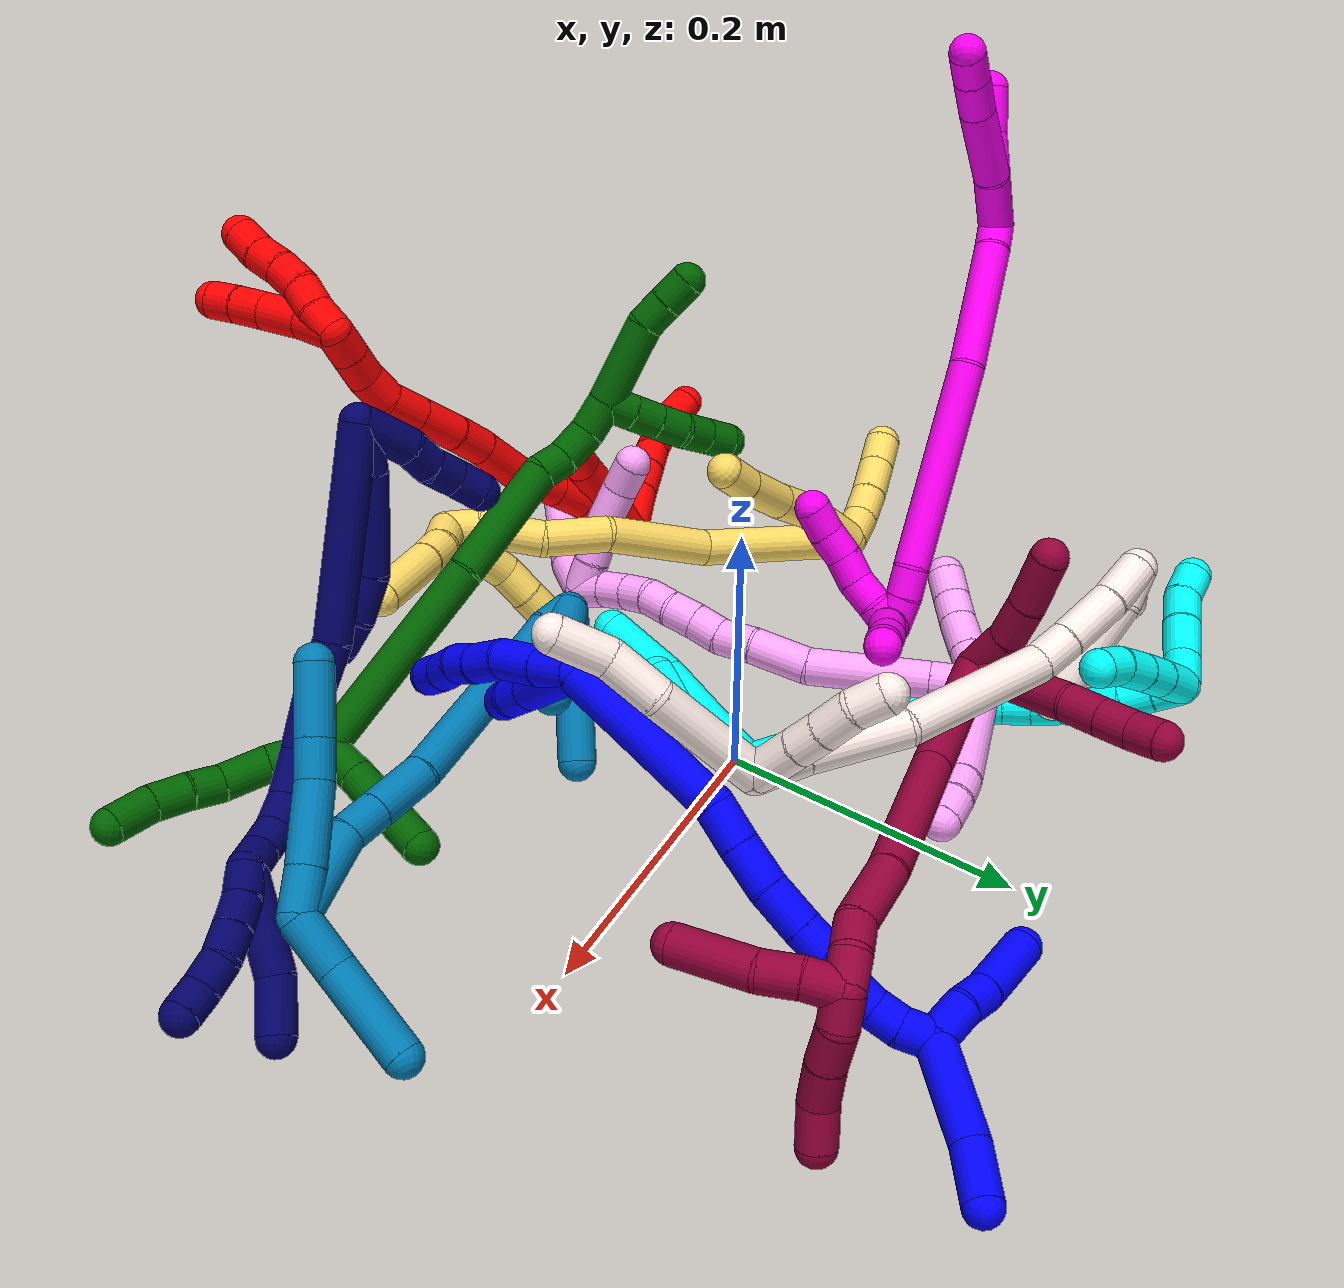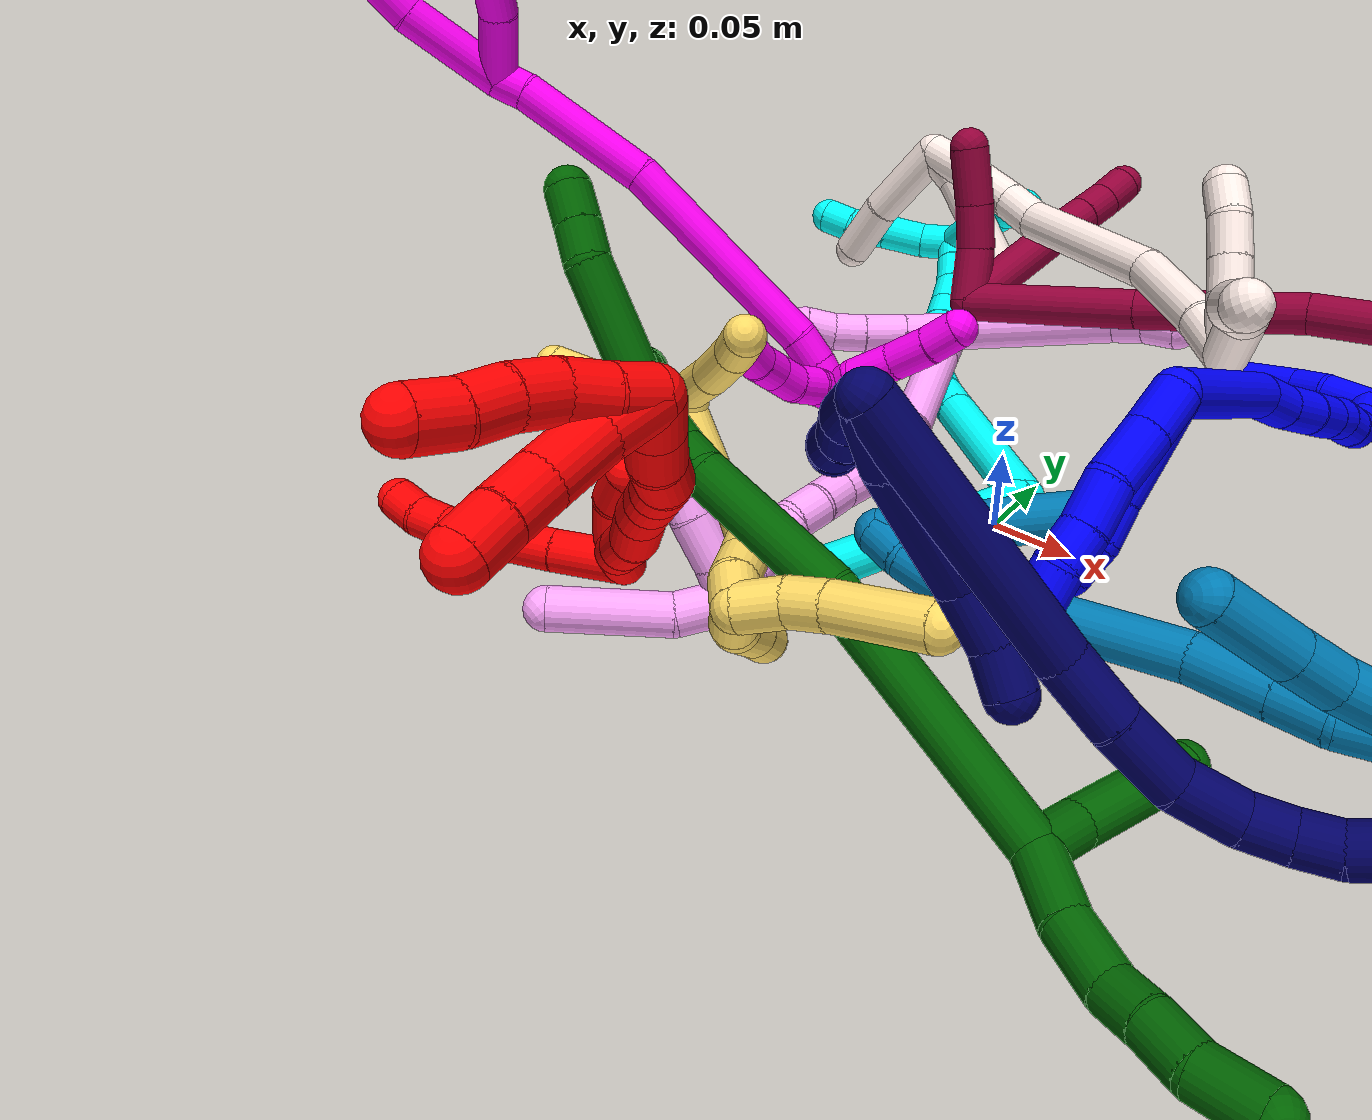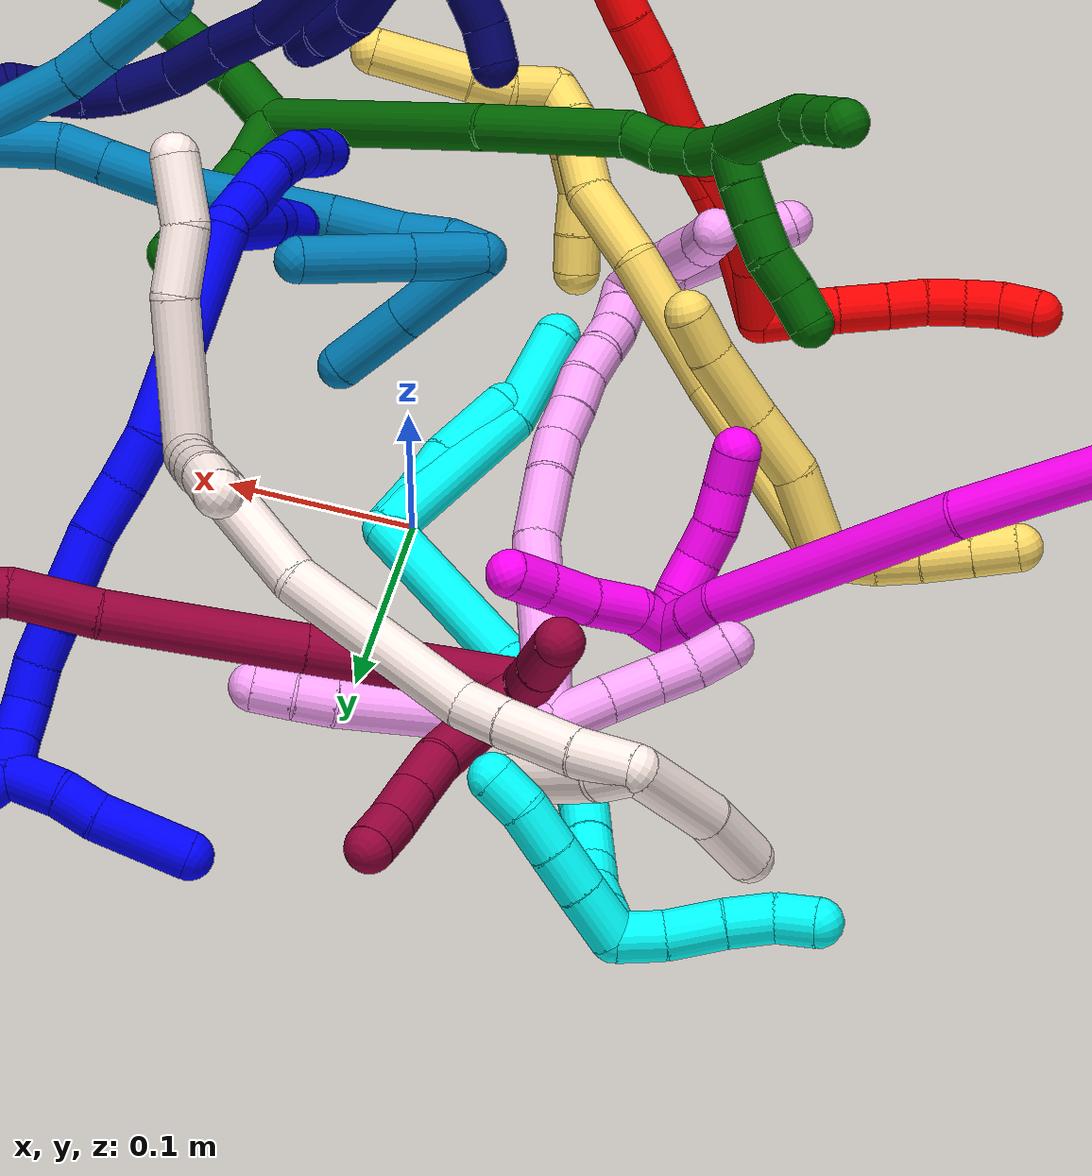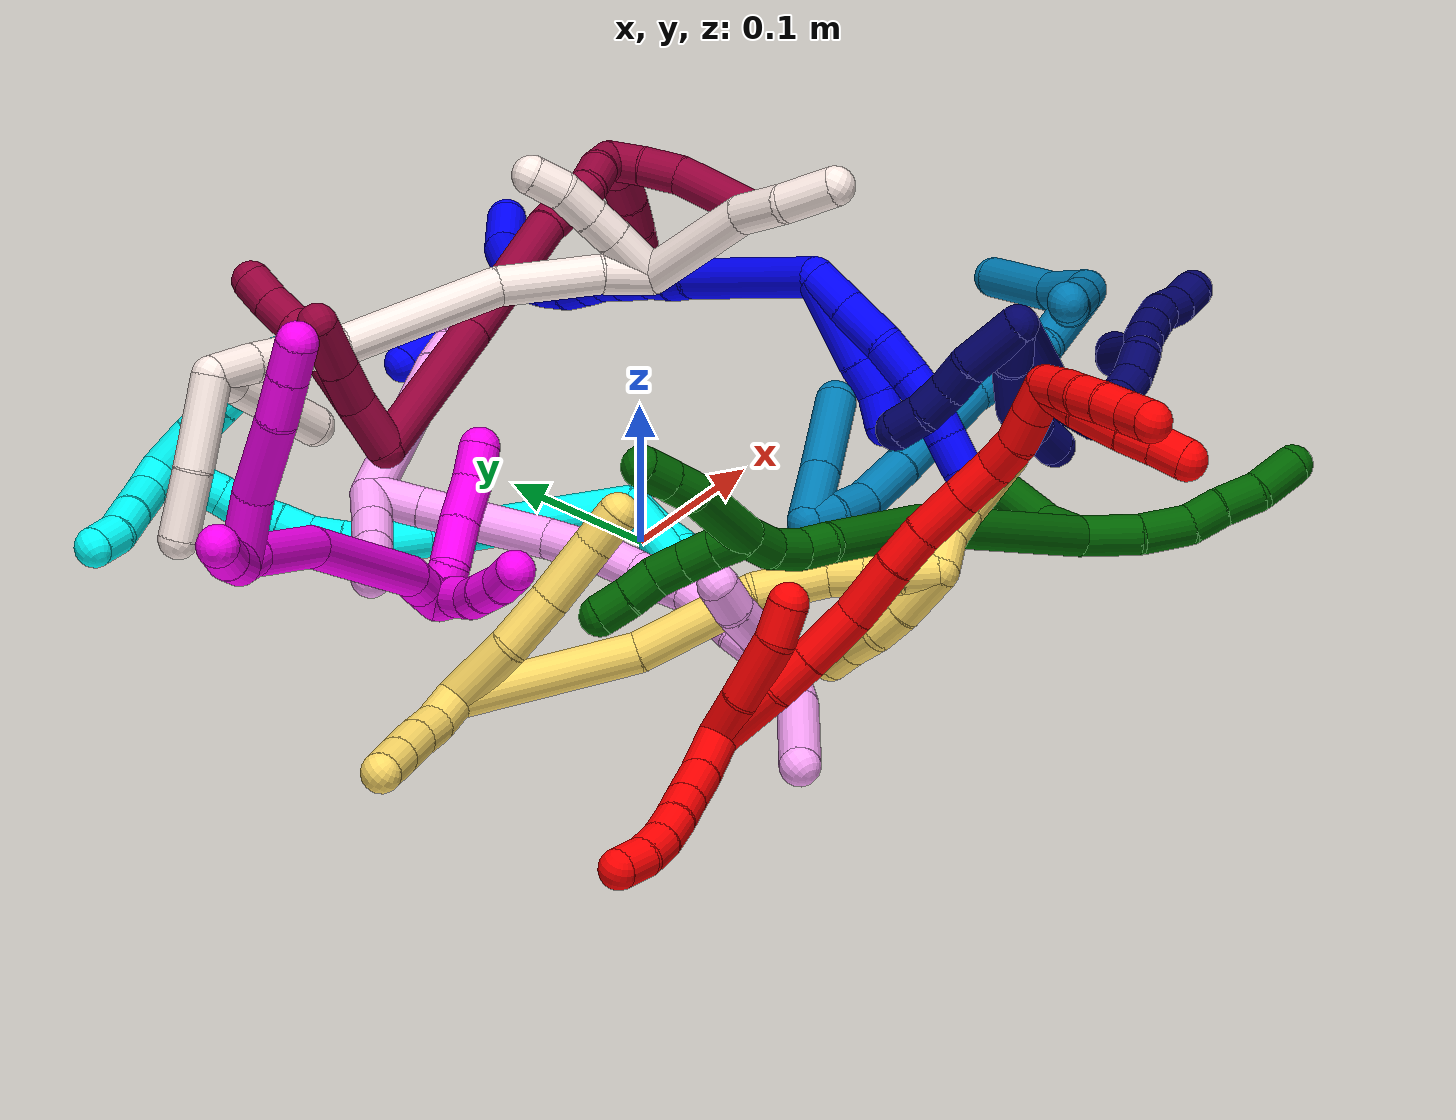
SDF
<sdf version="1.7">
 <world name="default">
  <plugin name="TubeGeneratorPlugin" filename="libtube_generator_plugin.so"/>
  <model name="photoneo_s_sensor">
   <static>1</static>
   <pose>0 0 2 1.57079 1.57079 3.14159</pose>
   <link name="link">
    <inertial><mass>0.1</mass></inertial>
    <sensor name="sensor" type="depth">
     <update_rate>30</update_rate>
     <camera>
      <horizontal_fov>1.22</horizontal_fov>
      <image><width>1920</width><height>1200</height><format>B8G8R8</format></image>
      <clip><near>0.1</near><far>4</far></clip>
      <depth_camera><output>points</output></depth_camera>
     </camera>
     <plugin name="camera_plugin" filename="libgazebo_ros_depth_camera.so">
      <baseline>0.2</baseline>
      <alwaysOn>1</alwaysOn>
      <updateRate>0.0</updateRate>
      <cameraName>camera_ir</cameraName>
      <imageTopicName>/camera/color/image_raw</imageTopicName>
      <cameraInfoTopicName>/camera/color/camera_info</cameraInfoTopicName>
      <depthImageTopicName>/camera/depth/image_raw</depthImageTopicName>
      <depthImageCameraInfoTopicName>/camera/depth/camera_info</depthImageCameraInfoTopicName>
      <pointCloudTopicName>/camera/depth/points</pointCloudTopicName>
      <frameName>fr_optical</frameName>
      <pointCloudCutoff>0.1</pointCloudCutoff>
      <pointCloudCutoffMax>2.0</pointCloudCutoffMax>
      <distortionK1>0</distortionK1>
      <distortionK2>0</distortionK2>
      <distortionK3>0</distortionK3>
      <distortionT1>0</distortionT1>
      <distortionT2>0</distortionT2>
      <CxPrime>0</CxPrime>
      <Cx>0</Cx>
      <Cy>0</Cy>
      <focalLength>0</focalLength>
      <hackBaseline>0</hackBaseline>
     </plugin>
    </sensor>
   </link>
  </model>
  <gravity>0 0 -9.8</gravity>
  <magnetic_field>6e-06 2.3e-05 -4.2e-05</magnetic_field>
  <atmosphere type="adiabatic"/>
  <physics name="default_physics" default="0" type="ode">
   <max_step_size>0.003</max_step_size>
   <real_time_factor>1</real_time_factor>
   <real_time_update_rate>1000</real_time_update_rate>
   <max_contacts>10000</max_contacts>
   <ode>
    <solver>
     <type>quick</type>
     <iters>100</iters>
     <sor>1.3</sor>
     <use_dynamic_moi_rescaling>0</use_dynamic_moi_rescaling>
    </solver>
    <constraints>
     <contact_max_correcting_vel>0</contact_max_correcting_vel>
     <contact_surface_layer>0.001</contact_surface_layer>
     <cfm>0</cfm>
     <erp>0.2</erp>
    </constraints>
   </ode>
  </physics>
  <scene><ambient>0.4 0.4 0.4 1</ambient><background>0.7 0.7 0.7 1</background><shadows>0</shadows></scene>
  <audio><device>default</device></audio>
  <spherical_coordinates>
   <surface_model>EARTH_WGS84</surface_model>
   <latitude_deg>0</latitude_deg>
   <longitude_deg>0</longitude_deg>
   <elevation>0</elevation>
   <heading_deg>0</heading_deg>
  </spherical_coordinates>
  <model name="bin">
   <static>1</static>
   <link name="bottom">
    <collision name="collision-bottom">
     <pose>0 0 -0.01 0 -0 0</pose>
     <geometry><box><size>0.8 0.6 0.02</size></box></geometry>
     <surface>
      <friction><ode><mu>100</mu><mu2>100</mu2></ode></friction>
      <contact><collide_bitmask>65535</collide_bitmask></contact>
     </surface>
    </collision>
   </link>
   <link name="west_wall">
    <collision name="collision-west_wall">
     <pose>-0.41 0 0.1 0 -0 0</pose>
     <geometry><box><size>0.02 0.6 0.2</size></box></geometry>
     <surface>
      <friction><ode><mu>100</mu><mu2>100</mu2></ode></friction>
      <contact><collide_bitmask>65535</collide_bitmask></contact>
     </surface>
    </collision>
   </link>
   <link name="east_wall">
    <collision name="collision-east_wall">
     <pose>0.41 0 0.1 0 -0 0</pose>
     <geometry><box><size>0.02 0.6 0.2</size></box></geometry>
     <surface>
      <friction><ode><mu>100</mu><mu2>100</mu2></ode></friction>
      <contact><collide_bitmask>65535</collide_bitmask></contact>
     </surface>
    </collision>
   </link>
   <link name="south_wall">
    <collision name="collision-south_wall">
     <pose>0 -0.31 0.1 0 -0 0</pose>
     <geometry><box><size>0.8 0.02 0.2</size></box></geometry>
     <surface>
      <friction><ode><mu>100</mu><mu2>100</mu2></ode></friction>
      <contact><collide_bitmask>65535</collide_bitmask></contact>
     </surface>
    </collision>
   </link>
   <link name="north_wall">
    <collision name="collision-north_wall">
     <pose>0 0.31 0.1 0 -0 0</pose>
     <geometry><box><size>0.8 0.02 0.2</size></box></geometry>
     <surface>
      <friction><ode><mu>100</mu><mu2>100</mu2></ode></friction>
      <contact><collide_bitmask>65535</collide_bitmask></contact>
     </surface>
    </collision>
   </link>
  </model>
  <model name="1">
   <static>0</static>
   <link name="1">
    <collision name="collision-cylinder-e_1_2_8">
     <pose>-0.000524 -0.013643 -0.0016 1.68757 -0.038134 -0.042867</pose>
     <geometry><cylinder><radius>0.0125</radius><length>0.027492</length></cylinder></geometry>
     <surface>
      <friction><ode><mu>1.16</mu><mu2>1.16</mu2><slip1>0</slip1><slip2>0</slip2></ode></friction>
      <contact><ode><kp>1e+06</kp><kd>1</kd><max_vel>0</max_vel><min_depth>0.001</min_depth></ode></contact>
     </surface>
    </collision>
    <visual name="visual-cylinder-e_1_2_8">
     <pose>-0.000524 -0.013643 -0.0016 1.68757 -0.038134 -0.042867</pose>
     <geometry><cylinder><radius>0.0125</radius><length>0.027492</length></cylinder></geometry>
     <material><ambient>0 0 1 1</ambient></material>
    </visual>
    <collision name="collision-cylinder-e_2_8_9">
     <pose>-0.001097 -0.043365 -0.004959 1.6797 -0.002995 -0.003341</pose>
     <geometry><cylinder><radius>0.0125</radius><length>0.03235</length></cylinder></geometry>
     <surface>
      <friction><ode><mu>1.16</mu><mu2>1.16</mu2><slip1>0</slip1><slip2>0</slip2></ode></friction>
      <contact><ode><kp>1e+06</kp><kd>1</kd><max_vel>0</max_vel><min_depth>0.001</min_depth></ode></contact>
     </surface>
    </collision>
    <visual name="visual-cylinder-e_2_8_9">
     <pose>-0.001097 -0.043365 -0.004959 1.6797 -0.002995 -0.003341</pose>
     <geometry><cylinder><radius>0.0125</radius><length>0.03235</length></cylinder></geometry>
     <material><ambient>0 0 1 1</ambient></material>
    </visual>
    <collision name="collision-cylinder-e_3_9_10">
     <pose>-0.004646 -0.071767 -0.008189 1.68969 -0.274922 -0.309198</pose>
     <geometry><cylinder><radius>0.0125</radius><length>0.025791</length></cylinder></geometry>
     <surface>
      <friction><ode><mu>1.16</mu><mu2>1.16</mu2><slip1>0</slip1><slip2>0</slip2></ode></friction>
      <contact><ode><kp>1e+06</kp><kd>1</kd><max_vel>0</max_vel><min_depth>0.001</min_depth></ode></contact>
     </surface>
    </collision>
    <visual name="visual-cylinder-e_3_9_10">
     <pose>-0.004646 -0.071767 -0.008189 1.68969 -0.274922 -0.309198</pose>
     <geometry><cylinder><radius>0.0125</radius><length>0.025791</length></cylinder></geometry>
     <material><ambient>0 0 1 1</ambient></material>
    </visual>
    <collision name="collision-cylinder-e_4_10_11">
     <pose>-0.010269 -0.094179 -0.009755 1.58011 -0.207362 -0.209288</pose>
     <geometry><cylinder><radius>0.0125</radius><length>0.020618</length></cylinder></geometry>
     <surface>
      <friction><ode><mu>1.16</mu><mu2>1.16</mu2><slip1>0</slip1><slip2>0</slip2></ode></friction>
      <contact><ode><kp>1e+06</kp><kd>1</kd><max_vel>0</max_vel><min_depth>0.001</min_depth></ode></contact>
     </surface>
    </collision>
    <visual name="visual-cylinder-e_4_10_11">
     <pose>-0.010269 -0.094179 -0.009755 1.58011 -0.207362 -0.209288</pose>
     <geometry><cylinder><radius>0.0125</radius><length>0.020618</length></cylinder></geometry>
     <material><ambient>0 0 1 1</ambient></material>
    </visual>
    <collision name="collision-cylinder-e_5_11_12">
     <pose>-0.017415 -0.114136 -0.009269 1.5121 -0.470156 -0.444237</pose>
     <geometry><cylinder><radius>0.0125</radius><length>0.02218</length></cylinder></geometry>
     <surface>
      <friction><ode><mu>1.16</mu><mu2>1.16</mu2><slip1>0</slip1><slip2>0</slip2></ode></friction>
      <contact><ode><kp>1e+06</kp><kd>1</kd><max_vel>0</max_vel><min_depth>0.001</min_depth></ode></contact>
     </surface>
    </collision>
    <visual name="visual-cylinder-e_5_11_12">
     <pose>-0.017415 -0.114136 -0.009269 1.5121 -0.470156 -0.444237</pose>
     <geometry><cylinder><radius>0.0125</radius><length>0.02218</length></cylinder></geometry>
     <material><ambient>0 0 1 1</ambient></material>
    </visual>
    <collision name="collision-cylinder-e_6_12_6">
     <pose>-0.026465 -0.133989 -0.00803 1.5049 -0.382505 -0.358632</pose>
     <geometry><cylinder><radius>0.0125</radius><length>0.021568</length></cylinder></geometry>
     <surface>
      <friction><ode><mu>1.16</mu><mu2>1.16</mu2><slip1>0</slip1><slip2>0</slip2></ode></friction>
      <contact><ode><kp>1e+06</kp><kd>1</kd><max_vel>0</max_vel><min_depth>0.001</min_depth></ode></contact>
     </surface>
    </collision>
    <visual name="visual-cylinder-e_6_12_6">
     <pose>-0.026465 -0.133989 -0.00803 1.5049 -0.382505 -0.358632</pose>
     <geometry><cylinder><radius>0.0125</radius><length>0.021568</length></cylinder></geometry>
     <material><ambient>0 0 1 1</ambient></material>
    </visual>
    <collision name="collision-cylinder-e_1_2_13">
     <pose>-0.012259 -0.026007 0.001321 1.52003 -0.439991 -0.418851</pose>
     <geometry><cylinder><radius>0.0125</radius><length>0.057563</length></cylinder></geometry>
     <surface>
      <friction><ode><mu>1.16</mu><mu2>1.16</mu2><slip1>0</slip1><slip2>0</slip2></ode></friction>
      <contact><ode><kp>1e+06</kp><kd>1</kd><max_vel>0</max_vel><min_depth>0.001</min_depth></ode></contact>
     </surface>
    </collision>
    <visual name="visual-cylinder-e_1_2_13">
     <pose>-0.012259 -0.026007 0.001321 1.52003 -0.439991 -0.418851</pose>
     <geometry><cylinder><radius>0.0125</radius><length>0.057563</length></cylinder></geometry>
     <material><ambient>0 0 1 1</ambient></material>
    </visual>
    <collision name="collision-cylinder-e_2_13_14">
     <pose>-0.028938 -0.061894 0.002107 1.62493 -0.420117 -0.442759</pose>
     <geometry><cylinder><radius>0.0125</radius><length>0.021675</length></cylinder></geometry>
     <surface>
      <friction><ode><mu>1.16</mu><mu2>1.16</mu2><slip1>0</slip1><slip2>0</slip2></ode></friction>
      <contact><ode><kp>1e+06</kp><kd>1</kd><max_vel>0</max_vel><min_depth>0.001</min_depth></ode></contact>
     </surface>
    </collision>
    <visual name="visual-cylinder-e_2_13_14">
     <pose>-0.028938 -0.061894 0.002107 1.62493 -0.420117 -0.442759</pose>
     <geometry><cylinder><radius>0.0125</radius><length>0.021675</length></cylinder></geometry>
     <material><ambient>0 0 1 1</ambient></material>
    </visual>
    <collision name="collision-cylinder-e_3_14_5">
     <pose>-0.037812 -0.080661 0.004566 1.24576 -0.443348 -0.320977</pose>
     <geometry><cylinder><radius>0.0125</radius><length>0.020762</length></cylinder></geometry>
     <surface>
      <friction><ode><mu>1.16</mu><mu2>1.16</mu2><slip1>0</slip1><slip2>0</slip2></ode></friction>
      <contact><ode><kp>1e+06</kp><kd>1</kd><max_vel>0</max_vel><min_depth>0.001</min_depth></ode></contact>
     </surface>
    </collision>
    <visual name="visual-cylinder-e_3_14_5">
     <pose>-0.037812 -0.080661 0.004566 1.24576 -0.443348 -0.320977</pose>
     <geometry><cylinder><radius>0.0125</radius><length>0.020762</length></cylinder></geometry>
     <material><ambient>0 0 1 1</ambient></material>
    </visual>
    <collision name="collision-cylinder-e_1_2_15">
     <pose>-0.039762 0.037946 0.012285 -1.25771 -0.783849 0.584055</pose>
     <geometry><cylinder><radius>0.0125</radius><length>0.112638</length></cylinder></geometry>
     <surface>
      <friction><ode><mu>1.16</mu><mu2>1.16</mu2><slip1>0</slip1><slip2>0</slip2></ode></friction>
      <contact><ode><kp>1e+06</kp><kd>1</kd><max_vel>0</max_vel><min_depth>0.001</min_depth></ode></contact>
     </surface>
    </collision>
    <visual name="visual-cylinder-e_1_2_15">
     <pose>-0.039762 0.037946 0.012285 -1.25771 -0.783849 0.584055</pose>
     <geometry><cylinder><radius>0.0125</radius><length>0.112638</length></cylinder></geometry>
     <material><ambient>0 0 1 1</ambient></material>
    </visual>
    <collision name="collision-cylinder-e_2_15_16">
     <pose>-0.090734 0.083637 0.024782 -1.54329 -0.966077 0.943625</pose>
     <geometry><cylinder><radius>0.0125</radius><length>0.027255</length></cylinder></geometry>
     <surface>
      <friction><ode><mu>1.16</mu><mu2>1.16</mu2><slip1>0</slip1><slip2>0</slip2></ode></friction>
      <contact><ode><kp>1e+06</kp><kd>1</kd><max_vel>0</max_vel><min_depth>0.001</min_depth></ode></contact>
     </surface>
    </collision>
    <visual name="visual-cylinder-e_2_15_16">
     <pose>-0.090734 0.083637 0.024782 -1.54329 -0.966077 0.943625</pose>
     <geometry><cylinder><radius>0.0125</radius><length>0.027255</length></cylinder></geometry>
     <material><ambient>0 0 1 1</ambient></material>
    </visual>
    <collision name="collision-cylinder-e_3_16_17">
     <pose>-0.113209 0.100935 0.024983 -1.57212 -0.867407 0.868419</pose>
     <geometry><cylinder><radius>0.0125</radius><length>0.02954</length></cylinder></geometry>
     <surface>
      <friction><ode><mu>1.16</mu><mu2>1.16</mu2><slip1>0</slip1><slip2>0</slip2></ode></friction>
      <contact><ode><kp>1e+06</kp><kd>1</kd><max_vel>0</max_vel><min_depth>0.001</min_depth></ode></contact>
     </surface>
    </collision>
    <visual name="visual-cylinder-e_3_16_17">
     <pose>-0.113209 0.100935 0.024983 -1.57212 -0.867407 0.868419</pose>
     <geometry><cylinder><radius>0.0125</radius><length>0.02954</length></cylinder></geometry>
     <material><ambient>0 0 1 1</ambient></material>
    </visual>
    <collision name="collision-cylinder-e_4_17_18">
     <pose>-0.135714 0.119782 0.027152 -1.34023 -0.866728 0.702882</pose>
     <geometry><cylinder><radius>0.0125</radius><length>0.029494</length></cylinder></geometry>
     <surface>
      <friction><ode><mu>1.16</mu><mu2>1.16</mu2><slip1>0</slip1><slip2>0</slip2></ode></friction>
      <contact><ode><kp>1e+06</kp><kd>1</kd><max_vel>0</max_vel><min_depth>0.001</min_depth></ode></contact>
     </surface>
    </collision>
    <visual name="visual-cylinder-e_4_17_18">
     <pose>-0.135714 0.119782 0.027152 -1.34023 -0.866728 0.702882</pose>
     <geometry><cylinder><radius>0.0125</radius><length>0.029494</length></cylinder></geometry>
     <material><ambient>0 0 1 1</ambient></material>
    </visual>
    <collision name="collision-cylinder-e_5_18_19">
     <pose>-0.154435 0.135813 0.031062 -1.31965 -0.821725 0.651877</pose>
     <geometry><cylinder><radius>0.0125</radius><length>0.020432</length></cylinder></geometry>
     <surface>
      <friction><ode><mu>1.16</mu><mu2>1.16</mu2><slip1>0</slip1><slip2>0</slip2></ode></friction>
      <contact><ode><kp>1e+06</kp><kd>1</kd><max_vel>0</max_vel><min_depth>0.001</min_depth></ode></contact>
     </surface>
    </collision>
    <visual name="visual-cylinder-e_5_18_19">
     <pose>-0.154435 0.135813 0.031062 -1.31965 -0.821725 0.651877</pose>
     <geometry><cylinder><radius>0.0125</radius><length>0.020432</length></cylinder></geometry>
     <material><ambient>0 0 1 1</ambient></material>
    </visual>
    <collision name="collision-cylinder-e_6_19_20">
     <pose>-0.170551 0.148003 0.034016 -1.3497 -0.996479 0.821145</pose>
     <geometry><cylinder><radius>0.0125</radius><length>0.020568</length></cylinder></geometry>
     <surface>
      <friction><ode><mu>1.16</mu><mu2>1.16</mu2><slip1>0</slip1><slip2>0</slip2></ode></friction>
      <contact><ode><kp>1e+06</kp><kd>1</kd><max_vel>0</max_vel><min_depth>0.001</min_depth></ode></contact>
     </surface>
    </collision>
    <visual name="visual-cylinder-e_6_19_20">
     <pose>-0.170551 0.148003 0.034016 -1.3497 -0.996479 0.821145</pose>
     <geometry><cylinder><radius>0.0125</radius><length>0.020568</length></cylinder></geometry>
     <material><ambient>0 0 1 1</ambient></material>
    </visual>
    <collision name="collision-cylinder-e_7_20_21">
     <pose>-0.186885 0.15922 0.038035 -1.11957 -0.876762 0.571472</pose>
     <geometry><cylinder><radius>0.0125</radius><length>0.020035</length></cylinder></geometry>
     <surface>
      <friction><ode><mu>1.16</mu><mu2>1.16</mu2><slip1>0</slip1><slip2>0</slip2></ode></friction>
      <contact><ode><kp>1e+06</kp><kd>1</kd><max_vel>0</max_vel><min_depth>0.001</min_depth></ode></contact>
     </surface>
    </collision>
    <visual name="visual-cylinder-e_7_20_21">
     <pose>-0.186885 0.15922 0.038035 -1.11957 -0.876762 0.571472</pose>
     <geometry><cylinder><radius>0.0125</radius><length>0.020035</length></cylinder></geometry>
     <material><ambient>0 0 1 1</ambient></material>
    </visual>
    <collision name="collision-cylinder-e_8_21_22">
     <pose>-0.200396 0.172599 0.043761 -1.20316 -0.618901 0.432101</pose>
     <geometry><cylinder><radius>0.0125</radius><length>0.020031</length></cylinder></geometry>
     <surface>
      <friction><ode><mu>1.16</mu><mu2>1.16</mu2><slip1>0</slip1><slip2>0</slip2></ode></friction>
      <contact><ode><kp>1e+06</kp><kd>1</kd><max_vel>0</max_vel><min_depth>0.001</min_depth></ode></contact>
     </surface>
    </collision>
    <visual name="visual-cylinder-e_8_21_22">
     <pose>-0.200396 0.172599 0.043761 -1.20316 -0.618901 0.432101</pose>
     <geometry><cylinder><radius>0.0125</radius><length>0.020031</length></cylinder></geometry>
     <material><ambient>0 0 1 1</ambient></material>
    </visual>
    <collision name="collision-cylinder-e_9_22_1">
     <pose>-0.209207 0.188932 0.050571 -1.15237 -0.304669 0.19884</pose>
     <geometry><cylinder><radius>0.0125</radius><length>0.020008</length></cylinder></geometry>
     <surface>
      <friction><ode><mu>1.16</mu><mu2>1.16</mu2><slip1>0</slip1><slip2>0</slip2></ode></friction>
      <contact><ode><kp>1e+06</kp><kd>1</kd><max_vel>0</max_vel><min_depth>0.001</min_depth></ode></contact>
     </surface>
    </collision>
    <visual name="visual-cylinder-e_9_22_1">
     <pose>-0.209207 0.188932 0.050571 -1.15237 -0.304669 0.19884</pose>
     <geometry><cylinder><radius>0.0125</radius><length>0.020008</length></cylinder></geometry>
     <material><ambient>0 0 1 1</ambient></material>
    </visual>
    <collision name="collision-cylinder-e_1_1_23">
     <pose>-0.231953 0.218169 0.042204 -2.10888 -0.690617 1.12954</pose>
     <geometry><cylinder><radius>0.0125</radius><length>0.061992</length></cylinder></geometry>
     <surface>
      <friction><ode><mu>1.16</mu><mu2>1.16</mu2><slip1>0</slip1><slip2>0</slip2></ode></friction>
      <contact><ode><kp>1e+06</kp><kd>1</kd><max_vel>0</max_vel><min_depth>0.001</min_depth></ode></contact>
     </surface>
    </collision>
    <visual name="visual-cylinder-e_1_1_23">
     <pose>-0.231953 0.218169 0.042204 -2.10888 -0.690617 1.12954</pose>
     <geometry><cylinder><radius>0.0125</radius><length>0.061992</length></cylinder></geometry>
     <material><ambient>0 0 1 1</ambient></material>
    </visual>
    <collision name="collision-cylinder-e_2_23_4">
     <pose>-0.259503 0.251653 0.018466 -2.29593 -0.423245 0.890887</pose>
     <geometry><cylinder><radius>0.0125</radius><length>0.038008</length></cylinder></geometry>
     <surface>
      <friction><ode><mu>1.16</mu><mu2>1.16</mu2><slip1>0</slip1><slip2>0</slip2></ode></friction>
      <contact><ode><kp>1e+06</kp><kd>1</kd><max_vel>0</max_vel><min_depth>0.001</min_depth></ode></contact>
     </surface>
    </collision>
    <visual name="visual-cylinder-e_2_23_4">
     <pose>-0.259503 0.251653 0.018466 -2.29593 -0.423245 0.890887</pose>
     <geometry><cylinder><radius>0.0125</radius><length>0.038008</length></cylinder></geometry>
     <material><ambient>0 0 1 1</ambient></material>
    </visual>
    <collision name="collision-cylinder-e_1_1_24">
     <pose>-0.20994 0.196358 0.06872 0.090385 0.156997 0.007115</pose>
     <geometry><cylinder><radius>0.0125</radius><length>0.029016</length></cylinder></geometry>
     <surface>
      <friction><ode><mu>1.16</mu><mu2>1.16</mu2><slip1>0</slip1><slip2>0</slip2></ode></friction>
      <contact><ode><kp>1e+06</kp><kd>1</kd><max_vel>0</max_vel><min_depth>0.001</min_depth></ode></contact>
     </surface>
    </collision>
    <visual name="visual-cylinder-e_1_1_24">
     <pose>-0.20994 0.196358 0.06872 0.090385 0.156997 0.007115</pose>
     <geometry><cylinder><radius>0.0125</radius><length>0.029016</length></cylinder></geometry>
     <material><ambient>0 0 1 1</ambient></material>
    </visual>
    <collision name="collision-cylinder-e_2_24_25">
     <pose>-0.208616 0.194257 0.093565 0.076258 -0.08887 -0.003392</pose>
     <geometry><cylinder><radius>0.0125</radius><length>0.021292</length></cylinder></geometry>
     <surface>
      <friction><ode><mu>1.16</mu><mu2>1.16</mu2><slip1>0</slip1><slip2>0</slip2></ode></friction>
      <contact><ode><kp>1e+06</kp><kd>1</kd><max_vel>0</max_vel><min_depth>0.001</min_depth></ode></contact>
     </surface>
    </collision>
    <visual name="visual-cylinder-e_2_24_25">
     <pose>-0.208616 0.194257 0.093565 0.076258 -0.08887 -0.003392</pose>
     <geometry><cylinder><radius>0.0125</radius><length>0.021292</length></cylinder></geometry>
     <material><ambient>0 0 1 1</ambient></material>
    </visual>
    <collision name="collision-cylinder-e_3_25_3">
     <pose>-0.209208 0.188181 0.128416 0.213669 0.014207 0.001524</pose>
     <geometry><cylinder><radius>0.0125</radius><length>0.049691</length></cylinder></geometry>
     <surface>
      <friction><ode><mu>1.16</mu><mu2>1.16</mu2><slip1>0</slip1><slip2>0</slip2></ode></friction>
      <contact><ode><kp>1e+06</kp><kd>1</kd><max_vel>0</max_vel><min_depth>0.001</min_depth></ode></contact>
     </surface>
    </collision>
    <visual name="visual-cylinder-e_3_25_3">
     <pose>-0.209208 0.188181 0.128416 0.213669 0.014207 0.001524</pose>
     <geometry><cylinder><radius>0.0125</radius><length>0.049691</length></cylinder></geometry>
     <material><ambient>0 0 1 1</ambient></material>
    </visual>
    <collision name="collision-sphere-3">
     <pose>-0.208855 0.182913 0.152694 0 -0 0</pose>
     <geometry><sphere><radius>0.0125</radius></sphere></geometry>
     <surface>
      <friction><ode><mu>1.16</mu><mu2>1.16</mu2><slip1>0</slip1><slip2>0</slip2></ode></friction>
      <contact><ode><kp>1e+06</kp><kd>1</kd><max_vel>0</max_vel><min_depth>0.001</min_depth></ode></contact>
     </surface>
    </collision>
    <visual name="visual-sphere-3">
     <pose>-0.208855 0.182913 0.152694 0 -0 0</pose>
     <geometry><sphere><radius>0.0125</radius></sphere></geometry>
     <material><ambient>0 0 1 1</ambient></material>
    </visual>
    <collision name="collision-sphere-25">
     <pose>-0.209561 0.193449 0.104138 0 -0 0</pose>
     <geometry><sphere><radius>0.0125</radius></sphere></geometry>
     <surface>
      <friction><ode><mu>1.16</mu><mu2>1.16</mu2><slip1>0</slip1><slip2>0</slip2></ode></friction>
      <contact><ode><kp>1e+06</kp><kd>1</kd><max_vel>0</max_vel><min_depth>0.001</min_depth></ode></contact>
     </surface>
    </collision>
    <visual name="visual-sphere-25">
     <pose>-0.209561 0.193449 0.104138 0 -0 0</pose>
     <geometry><sphere><radius>0.0125</radius></sphere></geometry>
     <material><ambient>0 0 1 1</ambient></material>
    </visual>
    <collision name="collision-sphere-24">
     <pose>-0.207671 0.195065 0.082991 0 -0 0</pose>
     <geometry><sphere><radius>0.0125</radius></sphere></geometry>
     <surface>
      <friction><ode><mu>1.16</mu><mu2>1.16</mu2><slip1>0</slip1><slip2>0</slip2></ode></friction>
      <contact><ode><kp>1e+06</kp><kd>1</kd><max_vel>0</max_vel><min_depth>0.001</min_depth></ode></contact>
     </surface>
    </collision>
    <visual name="visual-sphere-24">
     <pose>-0.207671 0.195065 0.082991 0 -0 0</pose>
     <geometry><sphere><radius>0.0125</radius></sphere></geometry>
     <material><ambient>0 0 1 1</ambient></material>
    </visual>
    <collision name="collision-sphere-4">
     <pose>-0.267308 0.264621 0.006975 0 -0 0</pose>
     <geometry><sphere><radius>0.0125</radius></sphere></geometry>
     <surface>
      <friction><ode><mu>1.16</mu><mu2>1.16</mu2><slip1>0</slip1><slip2>0</slip2></ode></friction>
      <contact><ode><kp>1e+06</kp><kd>1</kd><max_vel>0</max_vel><min_depth>0.001</min_depth></ode></contact>
     </surface>
    </collision>
    <visual name="visual-sphere-4">
     <pose>-0.267308 0.264621 0.006975 0 -0 0</pose>
     <geometry><sphere><radius>0.0125</radius></sphere></geometry>
     <material><ambient>0 0 1 1</ambient></material>
    </visual>
    <collision name="collision-sphere-23">
     <pose>-0.251698 0.238686 0.029958 0 -0 0</pose>
     <geometry><sphere><radius>0.0125</radius></sphere></geometry>
     <surface>
      <friction><ode><mu>1.16</mu><mu2>1.16</mu2><slip1>0</slip1><slip2>0</slip2></ode></friction>
      <contact><ode><kp>1e+06</kp><kd>1</kd><max_vel>0</max_vel><min_depth>0.001</min_depth></ode></contact>
     </surface>
    </collision>
    <visual name="visual-sphere-23">
     <pose>-0.251698 0.238686 0.029958 0 -0 0</pose>
     <geometry><sphere><radius>0.0125</radius></sphere></geometry>
     <material><ambient>0 0 1 1</ambient></material>
    </visual>
    <collision name="collision-sphere-1">
     <pose>-0.212208 0.197652 0.054449 0 -0 0</pose>
     <geometry><sphere><radius>0.0125</radius></sphere></geometry>
     <surface>
      <friction><ode><mu>1.16</mu><mu2>1.16</mu2><slip1>0</slip1><slip2>0</slip2></ode></friction>
      <contact><ode><kp>1e+06</kp><kd>1</kd><max_vel>0</max_vel><min_depth>0.001</min_depth></ode></contact>
     </surface>
    </collision>
    <visual name="visual-sphere-1">
     <pose>-0.212208 0.197652 0.054449 0 -0 0</pose>
     <geometry><sphere><radius>0.0125</radius></sphere></geometry>
     <material><ambient>0 0 1 1</ambient></material>
    </visual>
    <collision name="collision-sphere-22">
     <pose>-0.206206 0.180211 0.046693 0 -0 0</pose>
     <geometry><sphere><radius>0.0125</radius></sphere></geometry>
     <surface>
      <friction><ode><mu>1.16</mu><mu2>1.16</mu2><slip1>0</slip1><slip2>0</slip2></ode></friction>
      <contact><ode><kp>1e+06</kp><kd>1</kd><max_vel>0</max_vel><min_depth>0.001</min_depth></ode></contact>
     </surface>
    </collision>
    <visual name="visual-sphere-22">
     <pose>-0.206206 0.180211 0.046693 0 -0 0</pose>
     <geometry><sphere><radius>0.0125</radius></sphere></geometry>
     <material><ambient>0 0 1 1</ambient></material>
    </visual>
    <collision name="collision-sphere-21">
     <pose>-0.194585 0.164986 0.040829 0 -0 0</pose>
     <geometry><sphere><radius>0.0125</radius></sphere></geometry>
     <surface>
      <friction><ode><mu>1.16</mu><mu2>1.16</mu2><slip1>0</slip1><slip2>0</slip2></ode></friction>
      <contact><ode><kp>1e+06</kp><kd>1</kd><max_vel>0</max_vel><min_depth>0.001</min_depth></ode></contact>
     </surface>
    </collision>
    <visual name="visual-sphere-21">
     <pose>-0.194585 0.164986 0.040829 0 -0 0</pose>
     <geometry><sphere><radius>0.0125</radius></sphere></geometry>
     <material><ambient>0 0 1 1</ambient></material>
    </visual>
    <collision name="collision-sphere-12">
     <pose>-0.022439 -0.124006 -0.008689 0 -0 0</pose>
     <geometry><sphere><radius>0.0125</radius></sphere></geometry>
     <surface>
      <friction><ode><mu>1.16</mu><mu2>1.16</mu2><slip1>0</slip1><slip2>0</slip2></ode></friction>
      <contact><ode><kp>1e+06</kp><kd>1</kd><max_vel>0</max_vel><min_depth>0.001</min_depth></ode></contact>
     </surface>
    </collision>
    <visual name="visual-sphere-12">
     <pose>-0.022439 -0.124006 -0.008689 0 -0 0</pose>
     <geometry><sphere><radius>0.0125</radius></sphere></geometry>
     <material><ambient>0 0 1 1</ambient></material>
    </visual>
    <collision name="collision-sphere-11">
     <pose>-0.012391 -0.104267 -0.009849 0 -0 0</pose>
     <geometry><sphere><radius>0.0125</radius></sphere></geometry>
     <surface>
      <friction><ode><mu>1.16</mu><mu2>1.16</mu2><slip1>0</slip1><slip2>0</slip2></ode></friction>
      <contact><ode><kp>1e+06</kp><kd>1</kd><max_vel>0</max_vel><min_depth>0.001</min_depth></ode></contact>
     </surface>
    </collision>
    <visual name="visual-sphere-11">
     <pose>-0.012391 -0.104267 -0.009849 0 -0 0</pose>
     <geometry><sphere><radius>0.0125</radius></sphere></geometry>
     <material><ambient>0 0 1 1</ambient></material>
    </visual>
    <collision name="collision-sphere-10">
     <pose>-0.008147 -0.084091 -0.009661 0 -0 0</pose>
     <geometry><sphere><radius>0.0125</radius></sphere></geometry>
     <surface>
      <friction><ode><mu>1.16</mu><mu2>1.16</mu2><slip1>0</slip1><slip2>0</slip2></ode></friction>
      <contact><ode><kp>1e+06</kp><kd>1</kd><max_vel>0</max_vel><min_depth>0.001</min_depth></ode></contact>
     </surface>
    </collision>
    <visual name="visual-sphere-10">
     <pose>-0.008147 -0.084091 -0.009661 0 -0 0</pose>
     <geometry><sphere><radius>0.0125</radius></sphere></geometry>
     <material><ambient>0 0 1 1</ambient></material>
    </visual>
    <collision name="collision-sphere-9">
     <pose>-0.001145 -0.059444 -0.006717 0 -0 0</pose>
     <geometry><sphere><radius>0.0125</radius></sphere></geometry>
     <surface>
      <friction><ode><mu>1.16</mu><mu2>1.16</mu2><slip1>0</slip1><slip2>0</slip2></ode></friction>
      <contact><ode><kp>1e+06</kp><kd>1</kd><max_vel>0</max_vel><min_depth>0.001</min_depth></ode></contact>
     </surface>
    </collision>
    <visual name="visual-sphere-9">
     <pose>-0.001145 -0.059444 -0.006717 0 -0 0</pose>
     <geometry><sphere><radius>0.0125</radius></sphere></geometry>
     <material><ambient>0 0 1 1</ambient></material>
    </visual>
    <collision name="collision-sphere-2">
     <geometry><sphere><radius>0.0125</radius></sphere></geometry>
     <surface>
      <friction><ode><mu>1.16</mu><mu2>1.16</mu2><slip1>0</slip1><slip2>0</slip2></ode></friction>
      <contact><ode><kp>1e+06</kp><kd>1</kd><max_vel>0</max_vel><min_depth>0.001</min_depth></ode></contact>
     </surface>
    </collision>
    <visual name="visual-sphere-2">
     <geometry><sphere><radius>0.0125</radius></sphere></geometry>
     <material><ambient>0 0 1 1</ambient></material>
    </visual>
    <collision name="collision-sphere-19">
     <pose>-0.161917 0.142552 0.032791 0 -0 0</pose>
     <geometry><sphere><radius>0.0125</radius></sphere></geometry>
     <surface>
      <friction><ode><mu>1.16</mu><mu2>1.16</mu2><slip1>0</slip1><slip2>0</slip2></ode></friction>
      <contact><ode><kp>1e+06</kp><kd>1</kd><max_vel>0</max_vel><min_depth>0.001</min_depth></ode></contact>
     </surface>
    </collision>
    <visual name="visual-sphere-19">
     <pose>-0.161917 0.142552 0.032791 0 -0 0</pose>
     <geometry><sphere><radius>0.0125</radius></sphere></geometry>
     <material><ambient>0 0 1 1</ambient></material>
    </visual>
    <collision name="collision-sphere-8">
     <pose>-0.001048 -0.027285 -0.003201 0 -0 0</pose>
     <geometry><sphere><radius>0.0125</radius></sphere></geometry>
     <surface>
      <friction><ode><mu>1.16</mu><mu2>1.16</mu2><slip1>0</slip1><slip2>0</slip2></ode></friction>
      <contact><ode><kp>1e+06</kp><kd>1</kd><max_vel>0</max_vel><min_depth>0.001</min_depth></ode></contact>
     </surface>
    </collision>
    <visual name="visual-sphere-8">
     <pose>-0.001048 -0.027285 -0.003201 0 -0 0</pose>
     <geometry><sphere><radius>0.0125</radius></sphere></geometry>
     <material><ambient>0 0 1 1</ambient></material>
    </visual>
    <collision name="collision-sphere-6">
     <pose>-0.03049 -0.143972 -0.007371 0 -0 0</pose>
     <geometry><sphere><radius>0.0125</radius></sphere></geometry>
     <surface>
      <friction><ode><mu>1.16</mu><mu2>1.16</mu2><slip1>0</slip1><slip2>0</slip2></ode></friction>
      <contact><ode><kp>1e+06</kp><kd>1</kd><max_vel>0</max_vel><min_depth>0.001</min_depth></ode></contact>
     </surface>
    </collision>
    <visual name="visual-sphere-6">
     <pose>-0.03049 -0.143972 -0.007371 0 -0 0</pose>
     <geometry><sphere><radius>0.0125</radius></sphere></geometry>
     <material><ambient>0 0 1 1</ambient></material>
    </visual>
    <collision name="collision-sphere-13">
     <pose>-0.024518 -0.052014 0.002643 0 -0 0</pose>
     <geometry><sphere><radius>0.0125</radius></sphere></geometry>
     <surface>
      <friction><ode><mu>1.16</mu><mu2>1.16</mu2><slip1>0</slip1><slip2>0</slip2></ode></friction>
      <contact><ode><kp>1e+06</kp><kd>1</kd><max_vel>0</max_vel><min_depth>0.001</min_depth></ode></contact>
     </surface>
    </collision>
    <visual name="visual-sphere-13">
     <pose>-0.024518 -0.052014 0.002643 0 -0 0</pose>
     <geometry><sphere><radius>0.0125</radius></sphere></geometry>
     <material><ambient>0 0 1 1</ambient></material>
    </visual>
    <collision name="collision-sphere-14">
     <pose>-0.033358 -0.071775 0.001572 0 -0 0</pose>
     <geometry><sphere><radius>0.0125</radius></sphere></geometry>
     <surface>
      <friction><ode><mu>1.16</mu><mu2>1.16</mu2><slip1>0</slip1><slip2>0</slip2></ode></friction>
      <contact><ode><kp>1e+06</kp><kd>1</kd><max_vel>0</max_vel><min_depth>0.001</min_depth></ode></contact>
     </surface>
    </collision>
    <visual name="visual-sphere-14">
     <pose>-0.033358 -0.071775 0.001572 0 -0 0</pose>
     <geometry><sphere><radius>0.0125</radius></sphere></geometry>
     <material><ambient>0 0 1 1</ambient></material>
    </visual>
    <collision name="collision-sphere-5">
     <pose>-0.042265 -0.089547 0.007561 0 -0 0</pose>
     <geometry><sphere><radius>0.0125</radius></sphere></geometry>
     <surface>
      <friction><ode><mu>1.16</mu><mu2>1.16</mu2><slip1>0</slip1><slip2>0</slip2></ode></friction>
      <contact><ode><kp>1e+06</kp><kd>1</kd><max_vel>0</max_vel><min_depth>0.001</min_depth></ode></contact>
     </surface>
    </collision>
    <visual name="visual-sphere-5">
     <pose>-0.042265 -0.089547 0.007561 0 -0 0</pose>
     <geometry><sphere><radius>0.0125</radius></sphere></geometry>
     <material><ambient>0 0 1 1</ambient></material>
    </visual>
    <collision name="collision-sphere-15">
     <pose>-0.079523 0.075892 0.024569 0 -0 0</pose>
     <geometry><sphere><radius>0.0125</radius></sphere></geometry>
     <surface>
      <friction><ode><mu>1.16</mu><mu2>1.16</mu2><slip1>0</slip1><slip2>0</slip2></ode></friction>
      <contact><ode><kp>1e+06</kp><kd>1</kd><max_vel>0</max_vel><min_depth>0.001</min_depth></ode></contact>
     </surface>
    </collision>
    <visual name="visual-sphere-15">
     <pose>-0.079523 0.075892 0.024569 0 -0 0</pose>
     <geometry><sphere><radius>0.0125</radius></sphere></geometry>
     <material><ambient>0 0 1 1</ambient></material>
    </visual>
    <collision name="collision-sphere-16">
     <pose>-0.101945 0.091382 0.024995 0 -0 0</pose>
     <geometry><sphere><radius>0.0125</radius></sphere></geometry>
     <surface>
      <friction><ode><mu>1.16</mu><mu2>1.16</mu2><slip1>0</slip1><slip2>0</slip2></ode></friction>
      <contact><ode><kp>1e+06</kp><kd>1</kd><max_vel>0</max_vel><min_depth>0.001</min_depth></ode></contact>
     </surface>
    </collision>
    <visual name="visual-sphere-16">
     <pose>-0.101945 0.091382 0.024995 0 -0 0</pose>
     <geometry><sphere><radius>0.0125</radius></sphere></geometry>
     <material><ambient>0 0 1 1</ambient></material>
    </visual>
    <collision name="collision-sphere-17">
     <pose>-0.124473 0.110488 0.02497 0 -0 0</pose>
     <geometry><sphere><radius>0.0125</radius></sphere></geometry>
     <surface>
      <friction><ode><mu>1.16</mu><mu2>1.16</mu2><slip1>0</slip1><slip2>0</slip2></ode></friction>
      <contact><ode><kp>1e+06</kp><kd>1</kd><max_vel>0</max_vel><min_depth>0.001</min_depth></ode></contact>
     </surface>
    </collision>
    <visual name="visual-sphere-17">
     <pose>-0.124473 0.110488 0.02497 0 -0 0</pose>
     <geometry><sphere><radius>0.0125</radius></sphere></geometry>
     <material><ambient>0 0 1 1</ambient></material>
    </visual>
    <collision name="collision-sphere-18">
     <pose>-0.146954 0.129075 0.029333 0 -0 0</pose>
     <geometry><sphere><radius>0.0125</radius></sphere></geometry>
     <surface>
      <friction><ode><mu>1.16</mu><mu2>1.16</mu2><slip1>0</slip1><slip2>0</slip2></ode></friction>
      <contact><ode><kp>1e+06</kp><kd>1</kd><max_vel>0</max_vel><min_depth>0.001</min_depth></ode></contact>
     </surface>
    </collision>
    <visual name="visual-sphere-18">
     <pose>-0.146954 0.129075 0.029333 0 -0 0</pose>
     <geometry><sphere><radius>0.0125</radius></sphere></geometry>
     <material><ambient>0 0 1 1</ambient></material>
    </visual>
    <collision name="collision-sphere-20">
     <pose>-0.179185 0.153454 0.035241 0 -0 0</pose>
     <geometry><sphere><radius>0.0125</radius></sphere></geometry>
     <surface>
      <friction><ode><mu>1.16</mu><mu2>1.16</mu2><slip1>0</slip1><slip2>0</slip2></ode></friction>
      <contact><ode><kp>1e+06</kp><kd>1</kd><max_vel>0</max_vel><min_depth>0.001</min_depth></ode></contact>
     </surface>
    </collision>
    <visual name="visual-sphere-20">
     <pose>-0.179185 0.153454 0.035241 0 -0 0</pose>
     <geometry><sphere><radius>0.0125</radius></sphere></geometry>
     <material><ambient>0 0 1 1</ambient></material>
    </visual>
    <inertial>
     <pose>-0.108712 0.074778 0.027319 0 -0 0</pose>
     <mass>0.75</mass>
     <inertia>
      <ixx>0.000179</ixx>
      <ixy>0</ixy>
      <ixz>0</ixz>
      <iyy>0.000181</iyy>
      <iyz>0</iyz>
      <izz>5.8e-05</izz>
     </inertia>
    </inertial>
   </link>
   <pose>0.109546 -0.048121 0.155624 1.94459 -1.14644 -2.17907</pose>
  </model>
  <model name="2">
   <static>0</static>
   <link name="2">
    <collision name="collision-cylinder-e_1_2_8">
     <pose>-0.01979 0.00657 0.000318 -1.52241 -1.24988 1.20432</pose>
     <geometry><cylinder><radius>0.0125</radius><length>0.041709</length></cylinder></geometry>
     <surface>
      <friction><ode><mu>1.16</mu><mu2>1.16</mu2><slip1>0</slip1><slip2>0</slip2></ode></friction>
      <contact><ode><kp>1e+06</kp><kd>1</kd><max_vel>0</max_vel><min_depth>0.001</min_depth></ode></contact>
     </surface>
    </collision>
    <visual name="visual-cylinder-e_1_2_8">
     <pose>-0.01979 0.00657 0.000318 -1.52241 -1.24988 1.20432</pose>
     <geometry><cylinder><radius>0.0125</radius><length>0.041709</length></cylinder></geometry>
     <material><ambient>1 0 0 1</ambient></material>
    </visual>
    <collision name="collision-cylinder-e_2_8_9">
     <pose>-0.052305 0.016653 0.000937 -1.4854 -1.30057 1.21919</pose>
     <geometry><cylinder><radius>0.0125</radius><length>0.026409</length></cylinder></geometry>
     <surface>
      <friction><ode><mu>1.16</mu><mu2>1.16</mu2><slip1>0</slip1><slip2>0</slip2></ode></friction>
      <contact><ode><kp>1e+06</kp><kd>1</kd><max_vel>0</max_vel><min_depth>0.001</min_depth></ode></contact>
     </surface>
    </collision>
    <visual name="visual-cylinder-e_2_8_9">
     <pose>-0.052305 0.016653 0.000937 -1.4854 -1.30057 1.21919</pose>
     <geometry><cylinder><radius>0.0125</radius><length>0.026409</length></cylinder></geometry>
     <material><ambient>1 0 0 1</ambient></material>
    </visual>
    <collision name="collision-cylinder-e_3_9_10">
     <pose>-0.074958 0.023096 0.001368 -1.52618 -1.28349 1.24097</pose>
     <geometry><cylinder><radius>0.0125</radius><length>0.020705</length></cylinder></geometry>
     <surface>
      <friction><ode><mu>1.16</mu><mu2>1.16</mu2><slip1>0</slip1><slip2>0</slip2></ode></friction>
      <contact><ode><kp>1e+06</kp><kd>1</kd><max_vel>0</max_vel><min_depth>0.001</min_depth></ode></contact>
     </surface>
    </collision>
    <visual name="visual-cylinder-e_3_9_10">
     <pose>-0.074958 0.023096 0.001368 -1.52618 -1.28349 1.24097</pose>
     <geometry><cylinder><radius>0.0125</radius><length>0.020705</length></cylinder></geometry>
     <material><ambient>1 0 0 1</ambient></material>
    </visual>
    <collision name="collision-cylinder-e_4_10_11">
     <pose>-0.094997 0.028136 0.002585 -1.09557 -1.34034 0.900712</pose>
     <geometry><cylinder><radius>0.0125</radius><length>0.02077</length></cylinder></geometry>
     <surface>
      <friction><ode><mu>1.16</mu><mu2>1.16</mu2><slip1>0</slip1><slip2>0</slip2></ode></friction>
      <contact><ode><kp>1e+06</kp><kd>1</kd><max_vel>0</max_vel><min_depth>0.001</min_depth></ode></contact>
     </surface>
    </collision>
    <visual name="visual-cylinder-e_4_10_11">
     <pose>-0.094997 0.028136 0.002585 -1.09557 -1.34034 0.900712</pose>
     <geometry><cylinder><radius>0.0125</radius><length>0.02077</length></cylinder></geometry>
     <material><ambient>1 0 0 1</ambient></material>
    </visual>
    <collision name="collision-cylinder-e_5_11_12">
     <pose>-0.115093 0.030878 0.004113 -0.960942 -1.49358 0.899004</pose>
     <geometry><cylinder><radius>0.0125</radius><length>0.020031</length></cylinder></geometry>
     <surface>
      <friction><ode><mu>1.16</mu><mu2>1.16</mu2><slip1>0</slip1><slip2>0</slip2></ode></friction>
      <contact><ode><kp>1e+06</kp><kd>1</kd><max_vel>0</max_vel><min_depth>0.001</min_depth></ode></contact>
     </surface>
    </collision>
    <visual name="visual-cylinder-e_5_11_12">
     <pose>-0.115093 0.030878 0.004113 -0.960942 -1.49358 0.899004</pose>
     <geometry><cylinder><radius>0.0125</radius><length>0.020031</length></cylinder></geometry>
     <material><ambient>1 0 0 1</ambient></material>
    </visual>
    <collision name="collision-cylinder-e_6_12_6">
     <pose>-0.135089 0.029649 0.004919 1.3777 -1.38339 -1.197</pose>
     <geometry><cylinder><radius>0.0125</radius><length>0.020376</length></cylinder></geometry>
     <surface>
      <friction><ode><mu>1.16</mu><mu2>1.16</mu2><slip1>0</slip1><slip2>0</slip2></ode></friction>
      <contact><ode><kp>1e+06</kp><kd>1</kd><max_vel>0</max_vel><min_depth>0.001</min_depth></ode></contact>
     </surface>
    </collision>
    <visual name="visual-cylinder-e_6_12_6">
     <pose>-0.135089 0.029649 0.004919 1.3777 -1.38339 -1.197</pose>
     <geometry><cylinder><radius>0.0125</radius><length>0.020376</length></cylinder></geometry>
     <material><ambient>1 0 0 1</ambient></material>
    </visual>
    <collision name="collision-cylinder-e_1_2_13">
     <pose>0.001088 0.002904 -0.015987 -2.96193 0.066844 -0.710852</pose>
     <geometry><cylinder><radius>0.0125</radius><length>0.032571</length></cylinder></geometry>
     <surface>
      <friction><ode><mu>1.16</mu><mu2>1.16</mu2><slip1>0</slip1><slip2>0</slip2></ode></friction>
      <contact><ode><kp>1e+06</kp><kd>1</kd><max_vel>0</max_vel><min_depth>0.001</min_depth></ode></contact>
     </surface>
    </collision>
    <visual name="visual-cylinder-e_1_2_13">
     <pose>0.001088 0.002904 -0.015987 -2.96193 0.066844 -0.710852</pose>
     <geometry><cylinder><radius>0.0125</radius><length>0.032571</length></cylinder></geometry>
     <material><ambient>1 0 0 1</ambient></material>
    </visual>
    <collision name="collision-cylinder-e_2_13_14">
     <pose>0.006772 0.008418 -0.053226 -3.01936 0.211455 -2.09551</pose>
     <geometry><cylinder><radius>0.0125</radius><length>0.043797</length></cylinder></geometry>
     <surface>
      <friction><ode><mu>1.16</mu><mu2>1.16</mu2><slip1>0</slip1><slip2>0</slip2></ode></friction>
      <contact><ode><kp>1e+06</kp><kd>1</kd><max_vel>0</max_vel><min_depth>0.001</min_depth></ode></contact>
     </surface>
    </collision>
    <visual name="visual-cylinder-e_2_13_14">
     <pose>0.006772 0.008418 -0.053226 -3.01936 0.211455 -2.09551</pose>
     <geometry><cylinder><radius>0.0125</radius><length>0.043797</length></cylinder></geometry>
     <material><ambient>1 0 0 1</ambient></material>
    </visual>
    <collision name="collision-cylinder-e_3_14_5">
     <pose>0.01555 0.009592 -0.085435 3.01128 0.361803 2.45625</pose>
     <geometry><cylinder><radius>0.0125</radius><length>0.023632</length></cylinder></geometry>
     <surface>
      <friction><ode><mu>1.16</mu><mu2>1.16</mu2><slip1>0</slip1><slip2>0</slip2></ode></friction>
      <contact><ode><kp>1e+06</kp><kd>1</kd><max_vel>0</max_vel><min_depth>0.001</min_depth></ode></contact>
     </surface>
    </collision>
    <visual name="visual-cylinder-e_3_14_5">
     <pose>0.01555 0.009592 -0.085435 3.01128 0.361803 2.45625</pose>
     <geometry><cylinder><radius>0.0125</radius><length>0.023632</length></cylinder></geometry>
     <material><ambient>1 0 0 1</ambient></material>
    </visual>
    <collision name="collision-cylinder-e_1_2_15">
     <pose>0.007318 0.009679 -0.020618 -2.70269 0.310896 -1.22495</pose>
     <geometry><cylinder><radius>0.0125</radius><length>0.047847</length></cylinder></geometry>
     <surface>
      <friction><ode><mu>1.16</mu><mu2>1.16</mu2><slip1>0</slip1><slip2>0</slip2></ode></friction>
      <contact><ode><kp>1e+06</kp><kd>1</kd><max_vel>0</max_vel><min_depth>0.001</min_depth></ode></contact>
     </surface>
    </collision>
    <visual name="visual-cylinder-e_1_2_15">
     <pose>0.007318 0.009679 -0.020618 -2.70269 0.310896 -1.22495</pose>
     <geometry><cylinder><radius>0.0125</radius><length>0.047847</length></cylinder></geometry>
     <material><ambient>1 0 0 1</ambient></material>
    </visual>
    <collision name="collision-cylinder-e_2_15_16">
     <pose>0.021 0.023814 -0.052417 -2.76231 0.486323 -1.82451</pose>
     <geometry><cylinder><radius>0.0125</radius><length>0.027231</length></cylinder></geometry>
     <surface>
      <friction><ode><mu>1.16</mu><mu2>1.16</mu2><slip1>0</slip1><slip2>0</slip2></ode></friction>
      <contact><ode><kp>1e+06</kp><kd>1</kd><max_vel>0</max_vel><min_depth>0.001</min_depth></ode></contact>
     </surface>
    </collision>
    <visual name="visual-cylinder-e_2_15_16">
     <pose>0.021 0.023814 -0.052417 -2.76231 0.486323 -1.82451</pose>
     <geometry><cylinder><radius>0.0125</radius><length>0.027231</length></cylinder></geometry>
     <material><ambient>1 0 0 1</ambient></material>
    </visual>
    <collision name="collision-cylinder-e_3_16_17">
     <pose>0.036597 0.033729 -0.079195 -2.80497 0.50956 -1.98543</pose>
     <geometry><cylinder><radius>0.0125</radius><length>0.037857</length></cylinder></geometry>
     <surface>
      <friction><ode><mu>1.16</mu><mu2>1.16</mu2><slip1>0</slip1><slip2>0</slip2></ode></friction>
      <contact><ode><kp>1e+06</kp><kd>1</kd><max_vel>0</max_vel><min_depth>0.001</min_depth></ode></contact>
     </surface>
    </collision>
    <visual name="visual-cylinder-e_3_16_17">
     <pose>0.036597 0.033729 -0.079195 -2.80497 0.50956 -1.98543</pose>
     <geometry><cylinder><radius>0.0125</radius><length>0.037857</length></cylinder></geometry>
     <material><ambient>1 0 0 1</ambient></material>
    </visual>
    <collision name="collision-cylinder-e_4_17_18">
     <pose>0.052661 0.043414 -0.11223 -2.90375 0.363696 -1.98913</pose>
     <geometry><cylinder><radius>0.0125</radius><length>0.0384</length></cylinder></geometry>
     <surface>
      <friction><ode><mu>1.16</mu><mu2>1.16</mu2><slip1>0</slip1><slip2>0</slip2></ode></friction>
      <contact><ode><kp>1e+06</kp><kd>1</kd><max_vel>0</max_vel><min_depth>0.001</min_depth></ode></contact>
     </surface>
    </collision>
    <visual name="visual-cylinder-e_4_17_18">
     <pose>0.052661 0.043414 -0.11223 -2.90375 0.363696 -1.98913</pose>
     <geometry><cylinder><radius>0.0125</radius><length>0.0384</length></cylinder></geometry>
     <material><ambient>1 0 0 1</ambient></material>
    </visual>
    <collision name="collision-cylinder-e_5_18_19">
     <pose>0.06531 0.050598 -0.141006 -2.88653 0.461001 -2.14141</pose>
     <geometry><cylinder><radius>0.0125</radius><length>0.026163</length></cylinder></geometry>
     <surface>
      <friction><ode><mu>1.16</mu><mu2>1.16</mu2><slip1>0</slip1><slip2>0</slip2></ode></friction>
      <contact><ode><kp>1e+06</kp><kd>1</kd><max_vel>0</max_vel><min_depth>0.001</min_depth></ode></contact>
     </surface>
    </collision>
    <visual name="visual-cylinder-e_5_18_19">
     <pose>0.06531 0.050598 -0.141006 -2.88653 0.461001 -2.14141</pose>
     <geometry><cylinder><radius>0.0125</radius><length>0.026163</length></cylinder></geometry>
     <material><ambient>1 0 0 1</ambient></material>
    </visual>
    <collision name="collision-cylinder-e_6_19_20">
     <pose>0.07818 0.058914 -0.165834 -2.76344 0.452124 -1.75365</pose>
     <geometry><cylinder><radius>0.0125</radius><length>0.032278</length></cylinder></geometry>
     <surface>
      <friction><ode><mu>1.16</mu><mu2>1.16</mu2><slip1>0</slip1><slip2>0</slip2></ode></friction>
      <contact><ode><kp>1e+06</kp><kd>1</kd><max_vel>0</max_vel><min_depth>0.001</min_depth></ode></contact>
     </surface>
    </collision>
    <visual name="visual-cylinder-e_6_19_20">
     <pose>0.07818 0.058914 -0.165834 -2.76344 0.452124 -1.75365</pose>
     <geometry><cylinder><radius>0.0125</radius><length>0.032278</length></cylinder></geometry>
     <material><ambient>1 0 0 1</ambient></material>
    </visual>
    <collision name="collision-cylinder-e_7_20_21">
     <pose>0.090955 0.068672 -0.190341 -2.76173 0.449683 -1.74358</pose>
     <geometry><cylinder><radius>0.0125</radius><length>0.02634</length></cylinder></geometry>
     <surface>
      <friction><ode><mu>1.16</mu><mu2>1.16</mu2><slip1>0</slip1><slip2>0</slip2></ode></friction>
      <contact><ode><kp>1e+06</kp><kd>1</kd><max_vel>0</max_vel><min_depth>0.001</min_depth></ode></contact>
     </surface>
    </collision>
    <visual name="visual-cylinder-e_7_20_21">
     <pose>0.090955 0.068672 -0.190341 -2.76173 0.449683 -1.74358</pose>
     <geometry><cylinder><radius>0.0125</radius><length>0.02634</length></cylinder></geometry>
     <material><ambient>1 0 0 1</ambient></material>
    </visual>
    <collision name="collision-cylinder-e_8_21_22">
     <pose>0.098223 0.076633 -0.211747 -2.81121 0.139577 -0.794079</pose>
     <geometry><cylinder><radius>0.0125</radius><length>0.022187</length></cylinder></geometry>
     <surface>
      <friction><ode><mu>1.16</mu><mu2>1.16</mu2><slip1>0</slip1><slip2>0</slip2></ode></friction>
      <contact><ode><kp>1e+06</kp><kd>1</kd><max_vel>0</max_vel><min_depth>0.001</min_depth></ode></contact>
     </surface>
    </collision>
    <visual name="visual-cylinder-e_8_21_22">
     <pose>0.098223 0.076633 -0.211747 -2.81121 0.139577 -0.794079</pose>
     <geometry><cylinder><radius>0.0125</radius><length>0.022187</length></cylinder></geometry>
     <material><ambient>1 0 0 1</ambient></material>
    </visual>
    <collision name="collision-cylinder-e_9_22_23">
     <pose>0.101034 0.081091 -0.232667 -3.05687 0.119405 -1.90795</pose>
     <geometry><cylinder><radius>0.0125</radius><length>0.021284</length></cylinder></geometry>
     <surface>
      <friction><ode><mu>1.16</mu><mu2>1.16</mu2><slip1>0</slip1><slip2>0</slip2></ode></friction>
      <contact><ode><kp>1e+06</kp><kd>1</kd><max_vel>0</max_vel><min_depth>0.001</min_depth></ode></contact>
     </surface>
    </collision>
    <visual name="visual-cylinder-e_9_22_23">
     <pose>0.101034 0.081091 -0.232667 -3.05687 0.119405 -1.90795</pose>
     <geometry><cylinder><radius>0.0125</radius><length>0.021284</length></cylinder></geometry>
     <material><ambient>1 0 0 1</ambient></material>
    </visual>
    <collision name="collision-cylinder-e_10_23_1">
     <pose>0.10347 0.082815 -0.253301 -3.05968 0.114669 -1.90148</pose>
     <geometry><cylinder><radius>0.0125</radius><length>0.020414</length></cylinder></geometry>
     <surface>
      <friction><ode><mu>1.16</mu><mu2>1.16</mu2><slip1>0</slip1><slip2>0</slip2></ode></friction>
      <contact><ode><kp>1e+06</kp><kd>1</kd><max_vel>0</max_vel><min_depth>0.001</min_depth></ode></contact>
     </surface>
    </collision>
    <visual name="visual-cylinder-e_10_23_1">
     <pose>0.10347 0.082815 -0.253301 -3.05968 0.114669 -1.90148</pose>
     <geometry><cylinder><radius>0.0125</radius><length>0.020414</length></cylinder></geometry>
     <material><ambient>1 0 0 1</ambient></material>
    </visual>
    <collision name="collision-cylinder-e_1_1_24">
     <pose>0.100961 0.091516 -0.268359 -2.13227 -0.376497 0.664219</pose>
     <geometry><cylinder><radius>0.0125</radius><length>0.02</length></cylinder></geometry>
     <surface>
      <friction><ode><mu>1.16</mu><mu2>1.16</mu2><slip1>0</slip1><slip2>0</slip2></ode></friction>
      <contact><ode><kp>1e+06</kp><kd>1</kd><max_vel>0</max_vel><min_depth>0.001</min_depth></ode></contact>
     </surface>
    </collision>
    <visual name="visual-cylinder-e_1_1_24">
     <pose>0.100961 0.091516 -0.268359 -2.13227 -0.376497 0.664219</pose>
     <geometry><cylinder><radius>0.0125</radius><length>0.02</length></cylinder></geometry>
     <material><ambient>1 0 0 1</ambient></material>
    </visual>
    <collision name="collision-cylinder-e_2_24_25">
     <pose>0.092135 0.106552 -0.278017 -2.15212 -0.540932 0.949462</pose>
     <geometry><cylinder><radius>0.0125</radius><length>0.02</length></cylinder></geometry>
     <surface>
      <friction><ode><mu>1.16</mu><mu2>1.16</mu2><slip1>0</slip1><slip2>0</slip2></ode></friction>
      <contact><ode><kp>1e+06</kp><kd>1</kd><max_vel>0</max_vel><min_depth>0.001</min_depth></ode></contact>
     </surface>
    </collision>
    <visual name="visual-cylinder-e_2_24_25">
     <pose>0.092135 0.106552 -0.278017 -2.15212 -0.540932 0.949462</pose>
     <geometry><cylinder><radius>0.0125</radius><length>0.02</length></cylinder></geometry>
     <material><ambient>1 0 0 1</ambient></material>
    </visual>
    <collision name="collision-cylinder-e_3_25_26">
     <pose>0.08376 0.122216 -0.28689 -2.02646 -0.328446 0.519502</pose>
     <geometry><cylinder><radius>0.0125</radius><length>0.02</length></cylinder></geometry>
     <surface>
      <friction><ode><mu>1.16</mu><mu2>1.16</mu2><slip1>0</slip1><slip2>0</slip2></ode></friction>
      <contact><ode><kp>1e+06</kp><kd>1</kd><max_vel>0</max_vel><min_depth>0.001</min_depth></ode></contact>
     </surface>
    </collision>
    <visual name="visual-cylinder-e_3_25_26">
     <pose>0.08376 0.122216 -0.28689 -2.02646 -0.328446 0.519502</pose>
     <geometry><cylinder><radius>0.0125</radius><length>0.02</length></cylinder></geometry>
     <material><ambient>1 0 0 1</ambient></material>
    </visual>
    <collision name="collision-cylinder-e_4_26_27">
     <pose>0.078132 0.139891 -0.294226 -1.9035 -0.24262 0.338933</pose>
     <geometry><cylinder><radius>0.0125</radius><length>0.02</length></cylinder></geometry>
     <surface>
      <friction><ode><mu>1.16</mu><mu2>1.16</mu2><slip1>0</slip1><slip2>0</slip2></ode></friction>
      <contact><ode><kp>1e+06</kp><kd>1</kd><max_vel>0</max_vel><min_depth>0.001</min_depth></ode></contact>
     </surface>
    </collision>
    <visual name="visual-cylinder-e_4_26_27">
     <pose>0.078132 0.139891 -0.294226 -1.9035 -0.24262 0.338933</pose>
     <geometry><cylinder><radius>0.0125</radius><length>0.02</length></cylinder></geometry>
     <material><ambient>1 0 0 1</ambient></material>
    </visual>
    <collision name="collision-cylinder-e_5_27_4">
     <pose>0.071975 0.157438 -0.301372 -2.01416 -0.384876 0.597994</pose>
     <geometry><cylinder><radius>0.0125</radius><length>0.02</length></cylinder></geometry>
     <surface>
      <friction><ode><mu>1.16</mu><mu2>1.16</mu2><slip1>0</slip1><slip2>0</slip2></ode></friction>
      <contact><ode><kp>1e+06</kp><kd>1</kd><max_vel>0</max_vel><min_depth>0.001</min_depth></ode></contact>
     </surface>
    </collision>
    <visual name="visual-cylinder-e_5_27_4">
     <pose>0.071975 0.157438 -0.301372 -2.01416 -0.384876 0.597994</pose>
     <geometry><cylinder><radius>0.0125</radius><length>0.02</length></cylinder></geometry>
     <material><ambient>1 0 0 1</ambient></material>
    </visual>
    <collision name="collision-cylinder-e_1_1_28">
     <pose>0.102158 0.09701 -0.264401 -1.64501 -0.182915 0.196931</pose>
     <geometry><cylinder><radius>0.0125</radius><length>0.027259</length></cylinder></geometry>
     <surface>
      <friction><ode><mu>1.16</mu><mu2>1.16</mu2><slip1>0</slip1><slip2>0</slip2></ode></friction>
      <contact><ode><kp>1e+06</kp><kd>1</kd><max_vel>0</max_vel><min_depth>0.001</min_depth></ode></contact>
     </surface>
    </collision>
    <visual name="visual-cylinder-e_1_1_28">
     <pose>0.102158 0.09701 -0.264401 -1.64501 -0.182915 0.196931</pose>
     <geometry><cylinder><radius>0.0125</radius><length>0.027259</length></cylinder></geometry>
     <material><ambient>1 0 0 1</ambient></material>
    </visual>
    <collision name="collision-cylinder-e_2_28_29">
     <pose>0.099047 0.125713 -0.266968 -1.67303 -0.040999 0.045419</pose>
     <geometry><cylinder><radius>0.0125</radius><length>0.030863</length></cylinder></geometry>
     <surface>
      <friction><ode><mu>1.16</mu><mu2>1.16</mu2><slip1>0</slip1><slip2>0</slip2></ode></friction>
      <contact><ode><kp>1e+06</kp><kd>1</kd><max_vel>0</max_vel><min_depth>0.001</min_depth></ode></contact>
     </surface>
    </collision>
    <visual name="visual-cylinder-e_2_28_29">
     <pose>0.099047 0.125713 -0.266968 -1.67303 -0.040999 0.045419</pose>
     <geometry><cylinder><radius>0.0125</radius><length>0.030863</length></cylinder></geometry>
     <material><ambient>1 0 0 1</ambient></material>
    </visual>
    <collision name="collision-cylinder-e_3_29_30">
     <pose>0.098527 0.151864 -0.270135 -1.71705 0.010313 -0.011944</pose>
     <geometry><cylinder><radius>0.0125</radius><length>0.021859</length></cylinder></geometry>
     <surface>
      <friction><ode><mu>1.16</mu><mu2>1.16</mu2><slip1>0</slip1><slip2>0</slip2></ode></friction>
      <contact><ode><kp>1e+06</kp><kd>1</kd><max_vel>0</max_vel><min_depth>0.001</min_depth></ode></contact>
     </surface>
    </collision>
    <visual name="visual-cylinder-e_3_29_30">
     <pose>0.098527 0.151864 -0.270135 -1.71705 0.010313 -0.011944</pose>
     <geometry><cylinder><radius>0.0125</radius><length>0.021859</length></cylinder></geometry>
     <material><ambient>1 0 0 1</ambient></material>
    </visual>
    <collision name="collision-cylinder-e_4_30_3">
     <pose>0.098729 0.172646 -0.272607 -1.65883 0.008944 -0.009768</pose>
     <geometry><cylinder><radius>0.0125</radius><length>0.020018</length></cylinder></geometry>
     <surface>
      <friction><ode><mu>1.16</mu><mu2>1.16</mu2><slip1>0</slip1><slip2>0</slip2></ode></friction>
      <contact><ode><kp>1e+06</kp><kd>1</kd><max_vel>0</max_vel><min_depth>0.001</min_depth></ode></contact>
     </surface>
    </collision>
    <visual name="visual-cylinder-e_4_30_3">
     <pose>0.098729 0.172646 -0.272607 -1.65883 0.008944 -0.009768</pose>
     <geometry><cylinder><radius>0.0125</radius><length>0.020018</length></cylinder></geometry>
     <material><ambient>1 0 0 1</ambient></material>
    </visual>
    <collision name="collision-sphere-3">
     <pose>0.098819 0.182616 -0.273487 0 -0 0</pose>
     <geometry><sphere><radius>0.0125</radius></sphere></geometry>
     <surface>
      <friction><ode><mu>1.16</mu><mu2>1.16</mu2><slip1>0</slip1><slip2>0</slip2></ode></friction>
      <contact><ode><kp>1e+06</kp><kd>1</kd><max_vel>0</max_vel><min_depth>0.001</min_depth></ode></contact>
     </surface>
    </collision>
    <visual name="visual-sphere-3">
     <pose>0.098819 0.182616 -0.273487 0 -0 0</pose>
     <geometry><sphere><radius>0.0125</radius></sphere></geometry>
     <material><ambient>1 0 0 1</ambient></material>
    </visual>
    <collision name="collision-sphere-30">
     <pose>0.09864 0.162676 -0.271727 0 -0 0</pose>
     <geometry><sphere><radius>0.0125</radius></sphere></geometry>
     <surface>
      <friction><ode><mu>1.16</mu><mu2>1.16</mu2><slip1>0</slip1><slip2>0</slip2></ode></friction>
      <contact><ode><kp>1e+06</kp><kd>1</kd><max_vel>0</max_vel><min_depth>0.001</min_depth></ode></contact>
     </surface>
    </collision>
    <visual name="visual-sphere-30">
     <pose>0.09864 0.162676 -0.271727 0 -0 0</pose>
     <geometry><sphere><radius>0.0125</radius></sphere></geometry>
     <material><ambient>1 0 0 1</ambient></material>
    </visual>
    <collision name="collision-sphere-29">
     <pose>0.098414 0.141052 -0.268542 0 -0 0</pose>
     <geometry><sphere><radius>0.0125</radius></sphere></geometry>
     <surface>
      <friction><ode><mu>1.16</mu><mu2>1.16</mu2><slip1>0</slip1><slip2>0</slip2></ode></friction>
      <contact><ode><kp>1e+06</kp><kd>1</kd><max_vel>0</max_vel><min_depth>0.001</min_depth></ode></contact>
     </surface>
    </collision>
    <visual name="visual-sphere-29">
     <pose>0.098414 0.141052 -0.268542 0 -0 0</pose>
     <geometry><sphere><radius>0.0125</radius></sphere></geometry>
     <material><ambient>1 0 0 1</ambient></material>
    </visual>
    <collision name="collision-sphere-28">
     <pose>0.099679 0.110375 -0.265395 0 -0 0</pose>
     <geometry><sphere><radius>0.0125</radius></sphere></geometry>
     <surface>
      <friction><ode><mu>1.16</mu><mu2>1.16</mu2><slip1>0</slip1><slip2>0</slip2></ode></friction>
      <contact><ode><kp>1e+06</kp><kd>1</kd><max_vel>0</max_vel><min_depth>0.001</min_depth></ode></contact>
     </surface>
    </collision>
    <visual name="visual-sphere-28">
     <pose>0.099679 0.110375 -0.265395 0 -0 0</pose>
     <geometry><sphere><radius>0.0125</radius></sphere></geometry>
     <material><ambient>1 0 0 1</ambient></material>
    </visual>
    <collision name="collision-sphere-4">
     <pose>0.06822 0.16581 -0.305348 0 -0 0</pose>
     <geometry><sphere><radius>0.0125</radius></sphere></geometry>
     <surface>
      <friction><ode><mu>1.16</mu><mu2>1.16</mu2><slip1>0</slip1><slip2>0</slip2></ode></friction>
      <contact><ode><kp>1e+06</kp><kd>1</kd><max_vel>0</max_vel><min_depth>0.001</min_depth></ode></contact>
     </surface>
    </collision>
    <visual name="visual-sphere-4">
     <pose>0.06822 0.16581 -0.305348 0 -0 0</pose>
     <geometry><sphere><radius>0.0125</radius></sphere></geometry>
     <material><ambient>1 0 0 1</ambient></material>
    </visual>
    <collision name="collision-sphere-27">
     <pose>0.075729 0.149066 -0.297396 0 -0 0</pose>
     <geometry><sphere><radius>0.0125</radius></sphere></geometry>
     <surface>
      <friction><ode><mu>1.16</mu><mu2>1.16</mu2><slip1>0</slip1><slip2>0</slip2></ode></friction>
      <contact><ode><kp>1e+06</kp><kd>1</kd><max_vel>0</max_vel><min_depth>0.001</min_depth></ode></contact>
     </surface>
    </collision>
    <visual name="visual-sphere-27">
     <pose>0.075729 0.149066 -0.297396 0 -0 0</pose>
     <geometry><sphere><radius>0.0125</radius></sphere></geometry>
     <material><ambient>1 0 0 1</ambient></material>
    </visual>
    <collision name="collision-sphere-26">
     <pose>0.080534 0.130716 -0.291055 0 -0 0</pose>
     <geometry><sphere><radius>0.0125</radius></sphere></geometry>
     <surface>
      <friction><ode><mu>1.16</mu><mu2>1.16</mu2><slip1>0</slip1><slip2>0</slip2></ode></friction>
      <contact><ode><kp>1e+06</kp><kd>1</kd><max_vel>0</max_vel><min_depth>0.001</min_depth></ode></contact>
     </surface>
    </collision>
    <visual name="visual-sphere-26">
     <pose>0.080534 0.130716 -0.291055 0 -0 0</pose>
     <geometry><sphere><radius>0.0125</radius></sphere></geometry>
     <material><ambient>1 0 0 1</ambient></material>
    </visual>
    <collision name="collision-sphere-25">
     <pose>0.086986 0.113717 -0.282725 0 -0 0</pose>
     <geometry><sphere><radius>0.0125</radius></sphere></geometry>
     <surface>
      <friction><ode><mu>1.16</mu><mu2>1.16</mu2><slip1>0</slip1><slip2>0</slip2></ode></friction>
      <contact><ode><kp>1e+06</kp><kd>1</kd><max_vel>0</max_vel><min_depth>0.001</min_depth></ode></contact>
     </surface>
    </collision>
    <visual name="visual-sphere-25">
     <pose>0.086986 0.113717 -0.282725 0 -0 0</pose>
     <geometry><sphere><radius>0.0125</radius></sphere></geometry>
     <material><ambient>1 0 0 1</ambient></material>
    </visual>
    <collision name="collision-sphere-24">
     <pose>0.097284 0.099388 -0.27331 0 -0 0</pose>
     <geometry><sphere><radius>0.0125</radius></sphere></geometry>
     <surface>
      <friction><ode><mu>1.16</mu><mu2>1.16</mu2><slip1>0</slip1><slip2>0</slip2></ode></friction>
      <contact><ode><kp>1e+06</kp><kd>1</kd><max_vel>0</max_vel><min_depth>0.001</min_depth></ode></contact>
     </surface>
    </collision>
    <visual name="visual-sphere-24">
     <pose>0.097284 0.099388 -0.27331 0 -0 0</pose>
     <geometry><sphere><radius>0.0125</radius></sphere></geometry>
     <material><ambient>1 0 0 1</ambient></material>
    </visual>
    <collision name="collision-sphere-1">
     <pose>0.104638 0.083645 -0.263407 0 -0 0</pose>
     <geometry><sphere><radius>0.0125</radius></sphere></geometry>
     <surface>
      <friction><ode><mu>1.16</mu><mu2>1.16</mu2><slip1>0</slip1><slip2>0</slip2></ode></friction>
      <contact><ode><kp>1e+06</kp><kd>1</kd><max_vel>0</max_vel><min_depth>0.001</min_depth></ode></contact>
     </surface>
    </collision>
    <visual name="visual-sphere-1">
     <pose>0.104638 0.083645 -0.263407 0 -0 0</pose>
     <geometry><sphere><radius>0.0125</radius></sphere></geometry>
     <material><ambient>1 0 0 1</ambient></material>
    </visual>
    <collision name="collision-sphere-23">
     <pose>0.102302 0.081985 -0.243195 0 -0 0</pose>
     <geometry><sphere><radius>0.0125</radius></sphere></geometry>
     <surface>
      <friction><ode><mu>1.16</mu><mu2>1.16</mu2><slip1>0</slip1><slip2>0</slip2></ode></friction>
      <contact><ode><kp>1e+06</kp><kd>1</kd><max_vel>0</max_vel><min_depth>0.001</min_depth></ode></contact>
     </surface>
    </collision>
    <visual name="visual-sphere-23">
     <pose>0.102302 0.081985 -0.243195 0 -0 0</pose>
     <geometry><sphere><radius>0.0125</radius></sphere></geometry>
     <material><ambient>1 0 0 1</ambient></material>
    </visual>
    <collision name="collision-sphere-22">
     <pose>0.099767 0.080197 -0.222139 0 -0 0</pose>
     <geometry><sphere><radius>0.0125</radius></sphere></geometry>
     <surface>
      <friction><ode><mu>1.16</mu><mu2>1.16</mu2><slip1>0</slip1><slip2>0</slip2></ode></friction>
      <contact><ode><kp>1e+06</kp><kd>1</kd><max_vel>0</max_vel><min_depth>0.001</min_depth></ode></contact>
     </surface>
    </collision>
    <visual name="visual-sphere-22">
     <pose>0.099767 0.080197 -0.222139 0 -0 0</pose>
     <geometry><sphere><radius>0.0125</radius></sphere></geometry>
     <material><ambient>1 0 0 1</ambient></material>
    </visual>
    <collision name="collision-sphere-21">
     <pose>0.09668 0.07307 -0.201356 0 -0 0</pose>
     <geometry><sphere><radius>0.0125</radius></sphere></geometry>
     <surface>
      <friction><ode><mu>1.16</mu><mu2>1.16</mu2><slip1>0</slip1><slip2>0</slip2></ode></friction>
      <contact><ode><kp>1e+06</kp><kd>1</kd><max_vel>0</max_vel><min_depth>0.001</min_depth></ode></contact>
     </surface>
    </collision>
    <visual name="visual-sphere-21">
     <pose>0.09668 0.07307 -0.201356 0 -0 0</pose>
     <geometry><sphere><radius>0.0125</radius></sphere></geometry>
     <material><ambient>1 0 0 1</ambient></material>
    </visual>
    <collision name="collision-sphere-12">
     <pose>-0.125079 0.031512 0.004555 0 -0 0</pose>
     <geometry><sphere><radius>0.0125</radius></sphere></geometry>
     <surface>
      <friction><ode><mu>1.16</mu><mu2>1.16</mu2><slip1>0</slip1><slip2>0</slip2></ode></friction>
      <contact><ode><kp>1e+06</kp><kd>1</kd><max_vel>0</max_vel><min_depth>0.001</min_depth></ode></contact>
     </surface>
    </collision>
    <visual name="visual-sphere-12">
     <pose>-0.125079 0.031512 0.004555 0 -0 0</pose>
     <geometry><sphere><radius>0.0125</radius></sphere></geometry>
     <material><ambient>1 0 0 1</ambient></material>
    </visual>
    <collision name="collision-sphere-11">
     <pose>-0.105107 0.030245 0.00367 0 -0 0</pose>
     <geometry><sphere><radius>0.0125</radius></sphere></geometry>
     <surface>
      <friction><ode><mu>1.16</mu><mu2>1.16</mu2><slip1>0</slip1><slip2>0</slip2></ode></friction>
      <contact><ode><kp>1e+06</kp><kd>1</kd><max_vel>0</max_vel><min_depth>0.001</min_depth></ode></contact>
     </surface>
    </collision>
    <visual name="visual-sphere-11">
     <pose>-0.105107 0.030245 0.00367 0 -0 0</pose>
     <geometry><sphere><radius>0.0125</radius></sphere></geometry>
     <material><ambient>1 0 0 1</ambient></material>
    </visual>
    <collision name="collision-sphere-10">
     <pose>-0.084887 0.026027 0.001499 0 -0 0</pose>
     <geometry><sphere><radius>0.0125</radius></sphere></geometry>
     <surface>
      <friction><ode><mu>1.16</mu><mu2>1.16</mu2><slip1>0</slip1><slip2>0</slip2></ode></friction>
      <contact><ode><kp>1e+06</kp><kd>1</kd><max_vel>0</max_vel><min_depth>0.001</min_depth></ode></contact>
     </surface>
    </collision>
    <visual name="visual-sphere-10">
     <pose>-0.084887 0.026027 0.001499 0 -0 0</pose>
     <geometry><sphere><radius>0.0125</radius></sphere></geometry>
     <material><ambient>1 0 0 1</ambient></material>
    </visual>
    <collision name="collision-sphere-9">
     <pose>-0.06503 0.020165 0.001238 0 -0 0</pose>
     <geometry><sphere><radius>0.0125</radius></sphere></geometry>
     <surface>
      <friction><ode><mu>1.16</mu><mu2>1.16</mu2><slip1>0</slip1><slip2>0</slip2></ode></friction>
      <contact><ode><kp>1e+06</kp><kd>1</kd><max_vel>0</max_vel><min_depth>0.001</min_depth></ode></contact>
     </surface>
    </collision>
    <visual name="visual-sphere-9">
     <pose>-0.06503 0.020165 0.001238 0 -0 0</pose>
     <geometry><sphere><radius>0.0125</radius></sphere></geometry>
     <material><ambient>1 0 0 1</ambient></material>
    </visual>
    <collision name="collision-sphere-2">
     <geometry><sphere><radius>0.0125</radius></sphere></geometry>
     <surface>
      <friction><ode><mu>1.16</mu><mu2>1.16</mu2><slip1>0</slip1><slip2>0</slip2></ode></friction>
      <contact><ode><kp>1e+06</kp><kd>1</kd><max_vel>0</max_vel><min_depth>0.001</min_depth></ode></contact>
     </surface>
    </collision>
    <visual name="visual-sphere-2">
     <geometry><sphere><radius>0.0125</radius></sphere></geometry>
     <material><ambient>1 0 0 1</ambient></material>
    </visual>
    <collision name="collision-sphere-19">
     <pose>0.071129 0.053554 -0.152342 0 -0 0</pose>
     <geometry><sphere><radius>0.0125</radius></sphere></geometry>
     <surface>
      <friction><ode><mu>1.16</mu><mu2>1.16</mu2><slip1>0</slip1><slip2>0</slip2></ode></friction>
      <contact><ode><kp>1e+06</kp><kd>1</kd><max_vel>0</max_vel><min_depth>0.001</min_depth></ode></contact>
     </surface>
    </collision>
    <visual name="visual-sphere-19">
     <pose>0.071129 0.053554 -0.152342 0 -0 0</pose>
     <geometry><sphere><radius>0.0125</radius></sphere></geometry>
     <material><ambient>1 0 0 1</ambient></material>
    </visual>
    <collision name="collision-sphere-8">
     <pose>-0.03958 0.013141 0.000636 0 -0 0</pose>
     <geometry><sphere><radius>0.0125</radius></sphere></geometry>
     <surface>
      <friction><ode><mu>1.16</mu><mu2>1.16</mu2><slip1>0</slip1><slip2>0</slip2></ode></friction>
      <contact><ode><kp>1e+06</kp><kd>1</kd><max_vel>0</max_vel><min_depth>0.001</min_depth></ode></contact>
     </surface>
    </collision>
    <visual name="visual-sphere-8">
     <pose>-0.03958 0.013141 0.000636 0 -0 0</pose>
     <geometry><sphere><radius>0.0125</radius></sphere></geometry>
     <material><ambient>1 0 0 1</ambient></material>
    </visual>
    <collision name="collision-sphere-6">
     <pose>-0.145098 0.027786 0.005283 0 -0 0</pose>
     <geometry><sphere><radius>0.0125</radius></sphere></geometry>
     <surface>
      <friction><ode><mu>1.16</mu><mu2>1.16</mu2><slip1>0</slip1><slip2>0</slip2></ode></friction>
      <contact><ode><kp>1e+06</kp><kd>1</kd><max_vel>0</max_vel><min_depth>0.001</min_depth></ode></contact>
     </surface>
    </collision>
    <visual name="visual-sphere-6">
     <pose>-0.145098 0.027786 0.005283 0 -0 0</pose>
     <geometry><sphere><radius>0.0125</radius></sphere></geometry>
     <material><ambient>1 0 0 1</ambient></material>
    </visual>
    <collision name="collision-sphere-13">
     <pose>0.002176 0.005807 -0.031975 0 -0 0</pose>
     <geometry><sphere><radius>0.0125</radius></sphere></geometry>
     <surface>
      <friction><ode><mu>1.16</mu><mu2>1.16</mu2><slip1>0</slip1><slip2>0</slip2></ode></friction>
      <contact><ode><kp>1e+06</kp><kd>1</kd><max_vel>0</max_vel><min_depth>0.001</min_depth></ode></contact>
     </surface>
    </collision>
    <visual name="visual-sphere-13">
     <pose>0.002176 0.005807 -0.031975 0 -0 0</pose>
     <geometry><sphere><radius>0.0125</radius></sphere></geometry>
     <material><ambient>1 0 0 1</ambient></material>
    </visual>
    <collision name="collision-sphere-14">
     <pose>0.011368 0.011028 -0.074477 0 -0 0</pose>
     <geometry><sphere><radius>0.0125</radius></sphere></geometry>
     <surface>
      <friction><ode><mu>1.16</mu><mu2>1.16</mu2><slip1>0</slip1><slip2>0</slip2></ode></friction>
      <contact><ode><kp>1e+06</kp><kd>1</kd><max_vel>0</max_vel><min_depth>0.001</min_depth></ode></contact>
     </surface>
    </collision>
    <visual name="visual-sphere-14">
     <pose>0.011368 0.011028 -0.074477 0 -0 0</pose>
     <geometry><sphere><radius>0.0125</radius></sphere></geometry>
     <material><ambient>1 0 0 1</ambient></material>
    </visual>
    <collision name="collision-sphere-5">
     <pose>0.019733 0.008156 -0.096392 0 -0 0</pose>
     <geometry><sphere><radius>0.0125</radius></sphere></geometry>
     <surface>
      <friction><ode><mu>1.16</mu><mu2>1.16</mu2><slip1>0</slip1><slip2>0</slip2></ode></friction>
      <contact><ode><kp>1e+06</kp><kd>1</kd><max_vel>0</max_vel><min_depth>0.001</min_depth></ode></contact>
     </surface>
    </collision>
    <visual name="visual-sphere-5">
     <pose>0.019733 0.008156 -0.096392 0 -0 0</pose>
     <geometry><sphere><radius>0.0125</radius></sphere></geometry>
     <material><ambient>1 0 0 1</ambient></material>
    </visual>
    <collision name="collision-sphere-15">
     <pose>0.014637 0.019357 -0.041235 0 -0 0</pose>
     <geometry><sphere><radius>0.0125</radius></sphere></geometry>
     <surface>
      <friction><ode><mu>1.16</mu><mu2>1.16</mu2><slip1>0</slip1><slip2>0</slip2></ode></friction>
      <contact><ode><kp>1e+06</kp><kd>1</kd><max_vel>0</max_vel><min_depth>0.001</min_depth></ode></contact>
     </surface>
    </collision>
    <visual name="visual-sphere-15">
     <pose>0.014637 0.019357 -0.041235 0 -0 0</pose>
     <geometry><sphere><radius>0.0125</radius></sphere></geometry>
     <material><ambient>1 0 0 1</ambient></material>
    </visual>
    <collision name="collision-sphere-16">
     <pose>0.027364 0.028271 -0.063598 0 -0 0</pose>
     <geometry><sphere><radius>0.0125</radius></sphere></geometry>
     <surface>
      <friction><ode><mu>1.16</mu><mu2>1.16</mu2><slip1>0</slip1><slip2>0</slip2></ode></friction>
      <contact><ode><kp>1e+06</kp><kd>1</kd><max_vel>0</max_vel><min_depth>0.001</min_depth></ode></contact>
     </surface>
    </collision>
    <visual name="visual-sphere-16">
     <pose>0.027364 0.028271 -0.063598 0 -0 0</pose>
     <geometry><sphere><radius>0.0125</radius></sphere></geometry>
     <material><ambient>1 0 0 1</ambient></material>
    </visual>
    <collision name="collision-sphere-17">
     <pose>0.045831 0.039187 -0.094791 0 -0 0</pose>
     <geometry><sphere><radius>0.0125</radius></sphere></geometry>
     <surface>
      <friction><ode><mu>1.16</mu><mu2>1.16</mu2><slip1>0</slip1><slip2>0</slip2></ode></friction>
      <contact><ode><kp>1e+06</kp><kd>1</kd><max_vel>0</max_vel><min_depth>0.001</min_depth></ode></contact>
     </surface>
    </collision>
    <visual name="visual-sphere-17">
     <pose>0.045831 0.039187 -0.094791 0 -0 0</pose>
     <geometry><sphere><radius>0.0125</radius></sphere></geometry>
     <material><ambient>1 0 0 1</ambient></material>
    </visual>
    <collision name="collision-sphere-18">
     <pose>0.05949 0.047642 -0.129669 0 -0 0</pose>
     <geometry><sphere><radius>0.0125</radius></sphere></geometry>
     <surface>
      <friction><ode><mu>1.16</mu><mu2>1.16</mu2><slip1>0</slip1><slip2>0</slip2></ode></friction>
      <contact><ode><kp>1e+06</kp><kd>1</kd><max_vel>0</max_vel><min_depth>0.001</min_depth></ode></contact>
     </surface>
    </collision>
    <visual name="visual-sphere-18">
     <pose>0.05949 0.047642 -0.129669 0 -0 0</pose>
     <geometry><sphere><radius>0.0125</radius></sphere></geometry>
     <material><ambient>1 0 0 1</ambient></material>
    </visual>
    <collision name="collision-sphere-20">
     <pose>0.085231 0.064274 -0.179326 0 -0 0</pose>
     <geometry><sphere><radius>0.0125</radius></sphere></geometry>
     <surface>
      <friction><ode><mu>1.16</mu><mu2>1.16</mu2><slip1>0</slip1><slip2>0</slip2></ode></friction>
      <contact><ode><kp>1e+06</kp><kd>1</kd><max_vel>0</max_vel><min_depth>0.001</min_depth></ode></contact>
     </surface>
    </collision>
    <visual name="visual-sphere-20">
     <pose>0.085231 0.064274 -0.179326 0 -0 0</pose>
     <geometry><sphere><radius>0.0125</radius></sphere></geometry>
     <material><ambient>1 0 0 1</ambient></material>
    </visual>
    <inertial>
     <pose>0.034427 0.058064 -0.131403 0 -0 0</pose>
     <mass>0.75</mass>
     <inertia><ixx>-3e-05</ixx><ixy>0</ixy><ixz>0</ixz><iyy>1.3e-05</iyy><iyz>0</iyz><izz>-6.3e-05</izz></inertia>
    </inertial>
   </link>
   <pose>-0.141115 -0.171926 0.011502 -2.91707 0.116848 0.1014</pose>
  </model>
  <model name="3">
   <static>0</static>
   <link name="3">
    <collision name="collision-cylinder-e_1_2_8">
     <pose>-0.013992 -0.002197 -0.046233 3.09411 -0.293578 -2.8231</pose>
     <geometry><cylinder><radius>0.0125</radius><length>0.096707</length></cylinder></geometry>
     <surface>
      <friction><ode><mu>1.16</mu><mu2>1.16</mu2><slip1>0</slip1><slip2>0</slip2></ode></friction>
      <contact><ode><kp>1e+06</kp><kd>1</kd><max_vel>0</max_vel><min_depth>0.001</min_depth></ode></contact>
     </surface>
    </collision>
    <visual name="visual-cylinder-e_1_2_8">
     <pose>-0.013992 -0.002197 -0.046233 3.09411 -0.293578 -2.8231</pose>
     <geometry><cylinder><radius>0.0125</radius><length>0.096707</length></cylinder></geometry>
     <material><ambient>0.003922 1 0.996078 1</ambient></material>
    </visual>
    <collision name="collision-cylinder-e_2_8_6">
     <pose>-0.040153 -0.012588 -0.11471 2.78867 -0.474202 -1.87014</pose>
     <geometry><cylinder><radius>0.0125</radius><length>0.053293</length></cylinder></geometry>
     <surface>
      <friction><ode><mu>1.16</mu><mu2>1.16</mu2><slip1>0</slip1><slip2>0</slip2></ode></friction>
      <contact><ode><kp>1e+06</kp><kd>1</kd><max_vel>0</max_vel><min_depth>0.001</min_depth></ode></contact>
     </surface>
    </collision>
    <visual name="visual-cylinder-e_2_8_6">
     <pose>-0.040153 -0.012588 -0.11471 2.78867 -0.474202 -1.87014</pose>
     <geometry><cylinder><radius>0.0125</radius><length>0.053293</length></cylinder></geometry>
     <material><ambient>0.003922 1 0.996078 1</ambient></material>
    </visual>
    <collision name="collision-cylinder-e_1_2_9">
     <pose>-0.002476 -0.002837 -0.014142 2.94363 -0.169981 -1.41813</pose>
     <geometry><cylinder><radius>0.0125</radius><length>0.02927</length></cylinder></geometry>
     <surface>
      <friction><ode><mu>1.16</mu><mu2>1.16</mu2><slip1>0</slip1><slip2>0</slip2></ode></friction>
      <contact><ode><kp>1e+06</kp><kd>1</kd><max_vel>0</max_vel><min_depth>0.001</min_depth></ode></contact>
     </surface>
    </collision>
    <visual name="visual-cylinder-e_1_2_9">
     <pose>-0.002476 -0.002837 -0.014142 2.94363 -0.169981 -1.41813</pose>
     <geometry><cylinder><radius>0.0125</radius><length>0.02927</length></cylinder></geometry>
     <material><ambient>0.003922 1 0.996078 1</ambient></material>
    </visual>
    <collision name="collision-cylinder-e_2_9_10">
     <pose>-0.009639 -0.008731 -0.04056 2.89753 -0.354913 -1.94199</pose>
     <geometry><cylinder><radius>0.0125</radius><length>0.026981</length></cylinder></geometry>
     <surface>
      <friction><ode><mu>1.16</mu><mu2>1.16</mu2><slip1>0</slip1><slip2>0</slip2></ode></friction>
      <contact><ode><kp>1e+06</kp><kd>1</kd><max_vel>0</max_vel><min_depth>0.001</min_depth></ode></contact>
     </surface>
    </collision>
    <visual name="visual-cylinder-e_2_9_10">
     <pose>-0.009639 -0.008731 -0.04056 2.89753 -0.354913 -1.94199</pose>
     <geometry><cylinder><radius>0.0125</radius><length>0.026981</length></cylinder></geometry>
     <material><ambient>0.003922 1 0.996078 1</ambient></material>
    </visual>
    <collision name="collision-cylinder-e_3_10_5">
     <pose>-0.022892 -0.011768 -0.072963 -3.14066 -0.402277 3.137</pose>
     <geometry><cylinder><radius>0.0125</radius><length>0.043749</length></cylinder></geometry>
     <surface>
      <friction><ode><mu>1.16</mu><mu2>1.16</mu2><slip1>0</slip1><slip2>0</slip2></ode></friction>
      <contact><ode><kp>1e+06</kp><kd>1</kd><max_vel>0</max_vel><min_depth>0.001</min_depth></ode></contact>
     </surface>
    </collision>
    <visual name="visual-cylinder-e_3_10_5">
     <pose>-0.022892 -0.011768 -0.072963 -3.14066 -0.402277 3.137</pose>
     <geometry><cylinder><radius>0.0125</radius><length>0.043749</length></cylinder></geometry>
     <material><ambient>0.003922 1 0.996078 1</ambient></material>
    </visual>
    <collision name="collision-cylinder-e_1_2_11">
     <pose>-0.001917 0.050299 0.007633 -1.42019 -0.037655 0.032373</pose>
     <geometry><cylinder><radius>0.0125</radius><length>0.101823</length></cylinder></geometry>
     <surface>
      <friction><ode><mu>1.16</mu><mu2>1.16</mu2><slip1>0</slip1><slip2>0</slip2></ode></friction>
      <contact><ode><kp>1e+06</kp><kd>1</kd><max_vel>0</max_vel><min_depth>0.001</min_depth></ode></contact>
     </surface>
    </collision>
    <visual name="visual-cylinder-e_1_2_11">
     <pose>-0.001917 0.050299 0.007633 -1.42019 -0.037655 0.032373</pose>
     <geometry><cylinder><radius>0.0125</radius><length>0.101823</length></cylinder></geometry>
     <material><ambient>0.003922 1 0.996078 1</ambient></material>
    </visual>
    <collision name="collision-cylinder-e_2_11_12">
     <pose>-0.004355 0.111609 0.01705 -1.41016 -0.046776 0.039809</pose>
     <geometry><cylinder><radius>0.0125</radius><length>0.022332</length></cylinder></geometry>
     <surface>
      <friction><ode><mu>1.16</mu><mu2>1.16</mu2><slip1>0</slip1><slip2>0</slip2></ode></friction>
      <contact><ode><kp>1e+06</kp><kd>1</kd><max_vel>0</max_vel><min_depth>0.001</min_depth></ode></contact>
     </surface>
    </collision>
    <visual name="visual-cylinder-e_2_11_12">
     <pose>-0.004355 0.111609 0.01705 -1.41016 -0.046776 0.039809</pose>
     <geometry><cylinder><radius>0.0125</radius><length>0.022332</length></cylinder></geometry>
     <material><ambient>0.003922 1 0.996078 1</ambient></material>
    </visual>
    <collision name="collision-cylinder-e_3_12_13">
     <pose>-0.002045 0.139373 0.024145 -1.26382 0.159804 -0.117099</pose>
     <geometry><cylinder><radius>0.0125</radius><length>0.035603</length></cylinder></geometry>
     <surface>
      <friction><ode><mu>1.16</mu><mu2>1.16</mu2><slip1>0</slip1><slip2>0</slip2></ode></friction>
      <contact><ode><kp>1e+06</kp><kd>1</kd><max_vel>0</max_vel><min_depth>0.001</min_depth></ode></contact>
     </surface>
    </collision>
    <visual name="visual-cylinder-e_3_12_13">
     <pose>-0.002045 0.139373 0.024145 -1.26382 0.159804 -0.117099</pose>
     <geometry><cylinder><radius>0.0125</radius><length>0.035603</length></cylinder></geometry>
     <material><ambient>0.003922 1 0.996078 1</ambient></material>
    </visual>
    <collision name="collision-cylinder-e_4_13_14">
     <pose>0.001029 0.164787 0.03448 -1.04519 0.024026 -0.01384</pose>
     <geometry><cylinder><radius>0.0125</radius><length>0.020032</length></cylinder></geometry>
     <surface>
      <friction><ode><mu>1.16</mu><mu2>1.16</mu2><slip1>0</slip1><slip2>0</slip2></ode></friction>
      <contact><ode><kp>1e+06</kp><kd>1</kd><max_vel>0</max_vel><min_depth>0.001</min_depth></ode></contact>
     </surface>
    </collision>
    <visual name="visual-cylinder-e_4_13_14">
     <pose>0.001029 0.164787 0.03448 -1.04519 0.024026 -0.01384</pose>
     <geometry><cylinder><radius>0.0125</radius><length>0.020032</length></cylinder></geometry>
     <material><ambient>0.003922 1 0.996078 1</ambient></material>
    </visual>
    <collision name="collision-cylinder-e_5_14_15">
     <pose>0.002041 0.181675 0.045299 -0.957023 0.076533 -0.039713</pose>
     <geometry><cylinder><radius>0.0125</radius><length>0.020183</length></cylinder></geometry>
     <surface>
      <friction><ode><mu>1.16</mu><mu2>1.16</mu2><slip1>0</slip1><slip2>0</slip2></ode></friction>
      <contact><ode><kp>1e+06</kp><kd>1</kd><max_vel>0</max_vel><min_depth>0.001</min_depth></ode></contact>
     </surface>
    </collision>
    <visual name="visual-cylinder-e_5_14_15">
     <pose>0.002041 0.181675 0.045299 -0.957023 0.076533 -0.039713</pose>
     <geometry><cylinder><radius>0.0125</radius><length>0.020183</length></cylinder></geometry>
     <material><ambient>0.003922 1 0.996078 1</ambient></material>
    </visual>
    <collision name="collision-cylinder-e_6_15_16">
     <pose>0.00197 0.196929 0.05817 -0.782022 -0.084246 0.034747</pose>
     <geometry><cylinder><radius>0.0125</radius><length>0.020018</length></cylinder></geometry>
     <surface>
      <friction><ode><mu>1.16</mu><mu2>1.16</mu2><slip1>0</slip1><slip2>0</slip2></ode></friction>
      <contact><ode><kp>1e+06</kp><kd>1</kd><max_vel>0</max_vel><min_depth>0.001</min_depth></ode></contact>
     </surface>
    </collision>
    <visual name="visual-cylinder-e_6_15_16">
     <pose>0.00197 0.196929 0.05817 -0.782022 -0.084246 0.034747</pose>
     <geometry><cylinder><radius>0.0125</radius><length>0.020018</length></cylinder></geometry>
     <material><ambient>0.003922 1 0.996078 1</ambient></material>
    </visual>
    <collision name="collision-cylinder-e_7_16_17">
     <pose>0.000843 0.211207 0.072132 -0.811243 -0.028439 0.012213</pose>
     <geometry><cylinder><radius>0.0125</radius><length>0.020005</length></cylinder></geometry>
     <surface>
      <friction><ode><mu>1.16</mu><mu2>1.16</mu2><slip1>0</slip1><slip2>0</slip2></ode></friction>
      <contact><ode><kp>1e+06</kp><kd>1</kd><max_vel>0</max_vel><min_depth>0.001</min_depth></ode></contact>
     </surface>
    </collision>
    <visual name="visual-cylinder-e_7_16_17">
     <pose>0.000843 0.211207 0.072132 -0.811243 -0.028439 0.012213</pose>
     <geometry><cylinder><radius>0.0125</radius><length>0.020005</length></cylinder></geometry>
     <material><ambient>0.003922 1 0.996078 1</ambient></material>
    </visual>
    <collision name="collision-cylinder-e_8_17_18">
     <pose>-0.002138 0.224686 0.086361 -0.703375 -0.273109 0.100757</pose>
     <geometry><cylinder><radius>0.0125</radius><length>0.020001</length></cylinder></geometry>
     <surface>
      <friction><ode><mu>1.16</mu><mu2>1.16</mu2><slip1>0</slip1><slip2>0</slip2></ode></friction>
      <contact><ode><kp>1e+06</kp><kd>1</kd><max_vel>0</max_vel><min_depth>0.001</min_depth></ode></contact>
     </surface>
    </collision>
    <visual name="visual-cylinder-e_8_17_18">
     <pose>-0.002138 0.224686 0.086361 -0.703375 -0.273109 0.100757</pose>
     <geometry><cylinder><radius>0.0125</radius><length>0.020001</length></cylinder></geometry>
     <material><ambient>0.003922 1 0.996078 1</ambient></material>
    </visual>
    <collision name="collision-cylinder-e_9_18_19">
     <pose>-0.007777 0.238335 0.09973 -0.888753 -0.298488 0.142942</pose>
     <geometry><cylinder><radius>0.0125</radius><length>0.020001</length></cylinder></geometry>
     <surface>
      <friction><ode><mu>1.16</mu><mu2>1.16</mu2><slip1>0</slip1><slip2>0</slip2></ode></friction>
      <contact><ode><kp>1e+06</kp><kd>1</kd><max_vel>0</max_vel><min_depth>0.001</min_depth></ode></contact>
     </surface>
    </collision>
    <visual name="visual-cylinder-e_9_18_19">
     <pose>-0.007777 0.238335 0.09973 -0.888753 -0.298488 0.142942</pose>
     <geometry><cylinder><radius>0.0125</radius><length>0.020001</length></cylinder></geometry>
     <material><ambient>0.003922 1 0.996078 1</ambient></material>
    </visual>
    <collision name="collision-cylinder-e_10_19_1">
     <pose>-0.013243 0.253578 0.11145 -0.941614 -0.255272 0.130454</pose>
     <geometry><cylinder><radius>0.0125</radius><length>0.020001</length></cylinder></geometry>
     <surface>
      <friction><ode><mu>1.16</mu><mu2>1.16</mu2><slip1>0</slip1><slip2>0</slip2></ode></friction>
      <contact><ode><kp>1e+06</kp><kd>1</kd><max_vel>0</max_vel><min_depth>0.001</min_depth></ode></contact>
     </surface>
    </collision>
    <visual name="visual-cylinder-e_10_19_1">
     <pose>-0.013243 0.253578 0.11145 -0.941614 -0.255272 0.130454</pose>
     <geometry><cylinder><radius>0.0125</radius><length>0.020001</length></cylinder></geometry>
     <material><ambient>0.003922 1 0.996078 1</ambient></material>
    </visual>
    <collision name="collision-cylinder-e_1_1_20">
     <pose>-0.024056 0.249554 0.120483 1.29619 -0.592544 -0.454303</pose>
     <geometry><cylinder><radius>0.0125</radius><length>0.029679</length></cylinder></geometry>
     <surface>
      <friction><ode><mu>1.16</mu><mu2>1.16</mu2><slip1>0</slip1><slip2>0</slip2></ode></friction>
      <contact><ode><kp>1e+06</kp><kd>1</kd><max_vel>0</max_vel><min_depth>0.001</min_depth></ode></contact>
     </surface>
    </collision>
    <visual name="visual-cylinder-e_1_1_20">
     <pose>-0.024056 0.249554 0.120483 1.29619 -0.592544 -0.454303</pose>
     <geometry><cylinder><radius>0.0125</radius><length>0.029679</length></cylinder></geometry>
     <material><ambient>0.003922 1 0.996078 1</ambient></material>
    </visual>
    <collision name="collision-cylinder-e_2_20_21">
     <pose>-0.038963 0.227701 0.126202 1.33712 -0.571959 -0.456441</pose>
     <geometry><cylinder><radius>0.0125</radius><length>0.024462</length></cylinder></geometry>
     <surface>
      <friction><ode><mu>1.16</mu><mu2>1.16</mu2><slip1>0</slip1><slip2>0</slip2></ode></friction>
      <contact><ode><kp>1e+06</kp><kd>1</kd><max_vel>0</max_vel><min_depth>0.001</min_depth></ode></contact>
     </surface>
    </collision>
    <visual name="visual-cylinder-e_2_20_21">
     <pose>-0.038963 0.227701 0.126202 1.33712 -0.571959 -0.456441</pose>
     <geometry><cylinder><radius>0.0125</radius><length>0.024462</length></cylinder></geometry>
     <material><ambient>0.003922 1 0.996078 1</ambient></material>
    </visual>
    <collision name="collision-cylinder-e_3_21_22">
     <pose>-0.052029 0.207104 0.130622 1.38064 -0.538646 -0.448273</pose>
     <geometry><cylinder><radius>0.0125</radius><length>0.025129</length></cylinder></geometry>
     <surface>
      <friction><ode><mu>1.16</mu><mu2>1.16</mu2><slip1>0</slip1><slip2>0</slip2></ode></friction>
      <contact><ode><kp>1e+06</kp><kd>1</kd><max_vel>0</max_vel><min_depth>0.001</min_depth></ode></contact>
     </surface>
    </collision>
    <visual name="visual-cylinder-e_3_21_22">
     <pose>-0.052029 0.207104 0.130622 1.38064 -0.538646 -0.448273</pose>
     <geometry><cylinder><radius>0.0125</radius><length>0.025129</length></cylinder></geometry>
     <material><ambient>0.003922 1 0.996078 1</ambient></material>
    </visual>
    <collision name="collision-cylinder-e_4_22_4">
     <pose>-0.061663 0.1869 0.134862 1.34568 -0.31271 -0.249936</pose>
     <geometry><cylinder><radius>0.0125</radius><length>0.02073</length></cylinder></geometry>
     <surface>
      <friction><ode><mu>1.16</mu><mu2>1.16</mu2><slip1>0</slip1><slip2>0</slip2></ode></friction>
      <contact><ode><kp>1e+06</kp><kd>1</kd><max_vel>0</max_vel><min_depth>0.001</min_depth></ode></contact>
     </surface>
    </collision>
    <visual name="visual-cylinder-e_4_22_4">
     <pose>-0.061663 0.1869 0.134862 1.34568 -0.31271 -0.249936</pose>
     <geometry><cylinder><radius>0.0125</radius><length>0.02073</length></cylinder></geometry>
     <material><ambient>0.003922 1 0.996078 1</ambient></material>
    </visual>
    <collision name="collision-cylinder-e_1_1_23">
     <pose>-0.018876 0.269556 0.108499 -2.38547 -0.255798 0.626289</pose>
     <geometry><cylinder><radius>0.0125</radius><length>0.024569</length></cylinder></geometry>
     <surface>
      <friction><ode><mu>1.16</mu><mu2>1.16</mu2><slip1>0</slip1><slip2>0</slip2></ode></friction>
      <contact><ode><kp>1e+06</kp><kd>1</kd><max_vel>0</max_vel><min_depth>0.001</min_depth></ode></contact>
     </surface>
    </collision>
    <visual name="visual-cylinder-e_1_1_23">
     <pose>-0.018876 0.269556 0.108499 -2.38547 -0.255798 0.626289</pose>
     <geometry><cylinder><radius>0.0125</radius><length>0.024569</length></cylinder></geometry>
     <material><ambient>0.003922 1 0.996078 1</ambient></material>
    </visual>
    <collision name="collision-cylinder-e_2_23_24">
     <pose>-0.028561 0.286348 0.089847 -2.42943 -0.46167 1.12708</pose>
     <geometry><cylinder><radius>0.0125</radius><length>0.029528</length></cylinder></geometry>
     <surface>
      <friction><ode><mu>1.16</mu><mu2>1.16</mu2><slip1>0</slip1><slip2>0</slip2></ode></friction>
      <contact><ode><kp>1e+06</kp><kd>1</kd><max_vel>0</max_vel><min_depth>0.001</min_depth></ode></contact>
     </surface>
    </collision>
    <visual name="visual-cylinder-e_2_23_24">
     <pose>-0.028561 0.286348 0.089847 -2.42943 -0.46167 1.12708</pose>
     <geometry><cylinder><radius>0.0125</radius><length>0.029528</length></cylinder></geometry>
     <material><ambient>0.003922 1 0.996078 1</ambient></material>
    </visual>
    <collision name="collision-cylinder-e_3_24_25">
     <pose>-0.039563 0.302746 0.071411 -2.39755 -0.368554 0.891293</pose>
     <geometry><cylinder><radius>0.0125</radius><length>0.024566</length></cylinder></geometry>
     <surface>
      <friction><ode><mu>1.16</mu><mu2>1.16</mu2><slip1>0</slip1><slip2>0</slip2></ode></friction>
      <contact><ode><kp>1e+06</kp><kd>1</kd><max_vel>0</max_vel><min_depth>0.001</min_depth></ode></contact>
     </surface>
    </collision>
    <visual name="visual-cylinder-e_3_24_25">
     <pose>-0.039563 0.302746 0.071411 -2.39755 -0.368554 0.891293</pose>
     <geometry><cylinder><radius>0.0125</radius><length>0.024566</length></cylinder></geometry>
     <material><ambient>0.003922 1 0.996078 1</ambient></material>
    </visual>
    <collision name="collision-cylinder-e_4_25_3">
     <pose>-0.047834 0.319273 0.058271 -2.06381 -0.368767 0.604702</pose>
     <geometry><cylinder><radius>0.0125</radius><length>0.021337</length></cylinder></geometry>
     <surface>
      <friction><ode><mu>1.16</mu><mu2>1.16</mu2><slip1>0</slip1><slip2>0</slip2></ode></friction>
      <contact><ode><kp>1e+06</kp><kd>1</kd><max_vel>0</max_vel><min_depth>0.001</min_depth></ode></contact>
     </surface>
    </collision>
    <visual name="visual-cylinder-e_4_25_3">
     <pose>-0.047834 0.319273 0.058271 -2.06381 -0.368767 0.604702</pose>
     <geometry><cylinder><radius>0.0125</radius><length>0.021337</length></cylinder></geometry>
     <material><ambient>0.003922 1 0.996078 1</ambient></material>
    </visual>
    <collision name="collision-sphere-3">
     <pose>-0.051679 0.328039 0.053561 0 -0 0</pose>
     <geometry><sphere><radius>0.0125</radius></sphere></geometry>
     <surface>
      <friction><ode><mu>1.16</mu><mu2>1.16</mu2><slip1>0</slip1><slip2>0</slip2></ode></friction>
      <contact><ode><kp>1e+06</kp><kd>1</kd><max_vel>0</max_vel><min_depth>0.001</min_depth></ode></contact>
     </surface>
    </collision>
    <visual name="visual-sphere-3">
     <pose>-0.051679 0.328039 0.053561 0 -0 0</pose>
     <geometry><sphere><radius>0.0125</radius></sphere></geometry>
     <material><ambient>0.003922 1 0.996078 1</ambient></material>
    </visual>
    <collision name="collision-sphere-25">
     <pose>-0.043988 0.310506 0.062981 0 -0 0</pose>
     <geometry><sphere><radius>0.0125</radius></sphere></geometry>
     <surface>
      <friction><ode><mu>1.16</mu><mu2>1.16</mu2><slip1>0</slip1><slip2>0</slip2></ode></friction>
      <contact><ode><kp>1e+06</kp><kd>1</kd><max_vel>0</max_vel><min_depth>0.001</min_depth></ode></contact>
     </surface>
    </collision>
    <visual name="visual-sphere-25">
     <pose>-0.043988 0.310506 0.062981 0 -0 0</pose>
     <geometry><sphere><radius>0.0125</radius></sphere></geometry>
     <material><ambient>0.003922 1 0.996078 1</ambient></material>
    </visual>
    <collision name="collision-sphere-24">
     <pose>-0.035138 0.294986 0.079841 0 -0 0</pose>
     <geometry><sphere><radius>0.0125</radius></sphere></geometry>
     <surface>
      <friction><ode><mu>1.16</mu><mu2>1.16</mu2><slip1>0</slip1><slip2>0</slip2></ode></friction>
      <contact><ode><kp>1e+06</kp><kd>1</kd><max_vel>0</max_vel><min_depth>0.001</min_depth></ode></contact>
     </surface>
    </collision>
    <visual name="visual-sphere-24">
     <pose>-0.035138 0.294986 0.079841 0 -0 0</pose>
     <geometry><sphere><radius>0.0125</radius></sphere></geometry>
     <material><ambient>0.003922 1 0.996078 1</ambient></material>
    </visual>
    <collision name="collision-sphere-23">
     <pose>-0.021984 0.27771 0.099853 0 -0 0</pose>
     <geometry><sphere><radius>0.0125</radius></sphere></geometry>
     <surface>
      <friction><ode><mu>1.16</mu><mu2>1.16</mu2><slip1>0</slip1><slip2>0</slip2></ode></friction>
      <contact><ode><kp>1e+06</kp><kd>1</kd><max_vel>0</max_vel><min_depth>0.001</min_depth></ode></contact>
     </surface>
    </collision>
    <visual name="visual-sphere-23">
     <pose>-0.021984 0.27771 0.099853 0 -0 0</pose>
     <geometry><sphere><radius>0.0125</radius></sphere></geometry>
     <material><ambient>0.003922 1 0.996078 1</ambient></material>
    </visual>
    <collision name="collision-sphere-4">
     <pose>-0.064852 0.177286 0.137064 0 -0 0</pose>
     <geometry><sphere><radius>0.0125</radius></sphere></geometry>
     <surface>
      <friction><ode><mu>1.16</mu><mu2>1.16</mu2><slip1>0</slip1><slip2>0</slip2></ode></friction>
      <contact><ode><kp>1e+06</kp><kd>1</kd><max_vel>0</max_vel><min_depth>0.001</min_depth></ode></contact>
     </surface>
    </collision>
    <visual name="visual-sphere-4">
     <pose>-0.064852 0.177286 0.137064 0 -0 0</pose>
     <geometry><sphere><radius>0.0125</radius></sphere></geometry>
     <material><ambient>0.003922 1 0.996078 1</ambient></material>
    </visual>
    <collision name="collision-sphere-22">
     <pose>-0.058475 0.196513 0.132661 0 -0 0</pose>
     <geometry><sphere><radius>0.0125</radius></sphere></geometry>
     <surface>
      <friction><ode><mu>1.16</mu><mu2>1.16</mu2><slip1>0</slip1><slip2>0</slip2></ode></friction>
      <contact><ode><kp>1e+06</kp><kd>1</kd><max_vel>0</max_vel><min_depth>0.001</min_depth></ode></contact>
     </surface>
    </collision>
    <visual name="visual-sphere-22">
     <pose>-0.058475 0.196513 0.132661 0 -0 0</pose>
     <geometry><sphere><radius>0.0125</radius></sphere></geometry>
     <material><ambient>0.003922 1 0.996078 1</ambient></material>
    </visual>
    <collision name="collision-sphere-21">
     <pose>-0.045584 0.217696 0.128584 0 -0 0</pose>
     <geometry><sphere><radius>0.0125</radius></sphere></geometry>
     <surface>
      <friction><ode><mu>1.16</mu><mu2>1.16</mu2><slip1>0</slip1><slip2>0</slip2></ode></friction>
      <contact><ode><kp>1e+06</kp><kd>1</kd><max_vel>0</max_vel><min_depth>0.001</min_depth></ode></contact>
     </surface>
    </collision>
    <visual name="visual-sphere-21">
     <pose>-0.045584 0.217696 0.128584 0 -0 0</pose>
     <geometry><sphere><radius>0.0125</radius></sphere></geometry>
     <material><ambient>0.003922 1 0.996078 1</ambient></material>
    </visual>
    <collision name="collision-sphere-20">
     <pose>-0.032343 0.237705 0.123821 0 -0 0</pose>
     <geometry><sphere><radius>0.0125</radius></sphere></geometry>
     <surface>
      <friction><ode><mu>1.16</mu><mu2>1.16</mu2><slip1>0</slip1><slip2>0</slip2></ode></friction>
      <contact><ode><kp>1e+06</kp><kd>1</kd><max_vel>0</max_vel><min_depth>0.001</min_depth></ode></contact>
     </surface>
    </collision>
    <visual name="visual-sphere-20">
     <pose>-0.032343 0.237705 0.123821 0 -0 0</pose>
     <geometry><sphere><radius>0.0125</radius></sphere></geometry>
     <material><ambient>0.003922 1 0.996078 1</ambient></material>
    </visual>
    <collision name="collision-sphere-5">
     <pose>-0.031456 -0.01175 -0.093091 0 -0 0</pose>
     <geometry><sphere><radius>0.0125</radius></sphere></geometry>
     <surface>
      <friction><ode><mu>1.16</mu><mu2>1.16</mu2><slip1>0</slip1><slip2>0</slip2></ode></friction>
      <contact><ode><kp>1e+06</kp><kd>1</kd><max_vel>0</max_vel><min_depth>0.001</min_depth></ode></contact>
     </surface>
    </collision>
    <visual name="visual-sphere-5">
     <pose>-0.031456 -0.01175 -0.093091 0 -0 0</pose>
     <geometry><sphere><radius>0.0125</radius></sphere></geometry>
     <material><ambient>0.003922 1 0.996078 1</ambient></material>
    </visual>
    <collision name="collision-sphere-10">
     <pose>-0.014328 -0.011787 -0.052835 0 -0 0</pose>
     <geometry><sphere><radius>0.0125</radius></sphere></geometry>
     <surface>
      <friction><ode><mu>1.16</mu><mu2>1.16</mu2><slip1>0</slip1><slip2>0</slip2></ode></friction>
      <contact><ode><kp>1e+06</kp><kd>1</kd><max_vel>0</max_vel><min_depth>0.001</min_depth></ode></contact>
     </surface>
    </collision>
    <visual name="visual-sphere-10">
     <pose>-0.014328 -0.011787 -0.052835 0 -0 0</pose>
     <geometry><sphere><radius>0.0125</radius></sphere></geometry>
     <material><ambient>0.003922 1 0.996078 1</ambient></material>
    </visual>
    <collision name="collision-sphere-6">
     <pose>-0.05232 -0.020782 -0.136955 0 -0 0</pose>
     <geometry><sphere><radius>0.0125</radius></sphere></geometry>
     <surface>
      <friction><ode><mu>1.16</mu><mu2>1.16</mu2><slip1>0</slip1><slip2>0</slip2></ode></friction>
      <contact><ode><kp>1e+06</kp><kd>1</kd><max_vel>0</max_vel><min_depth>0.001</min_depth></ode></contact>
     </surface>
    </collision>
    <visual name="visual-sphere-6">
     <pose>-0.05232 -0.020782 -0.136955 0 -0 0</pose>
     <geometry><sphere><radius>0.0125</radius></sphere></geometry>
     <material><ambient>0.003922 1 0.996078 1</ambient></material>
    </visual>
    <collision name="collision-sphere-9">
     <pose>-0.004951 -0.005674 -0.028285 0 -0 0</pose>
     <geometry><sphere><radius>0.0125</radius></sphere></geometry>
     <surface>
      <friction><ode><mu>1.16</mu><mu2>1.16</mu2><slip1>0</slip1><slip2>0</slip2></ode></friction>
      <contact><ode><kp>1e+06</kp><kd>1</kd><max_vel>0</max_vel><min_depth>0.001</min_depth></ode></contact>
     </surface>
    </collision>
    <visual name="visual-sphere-9">
     <pose>-0.004951 -0.005674 -0.028285 0 -0 0</pose>
     <geometry><sphere><radius>0.0125</radius></sphere></geometry>
     <material><ambient>0.003922 1 0.996078 1</ambient></material>
    </visual>
    <collision name="collision-sphere-2">
     <geometry><sphere><radius>0.0125</radius></sphere></geometry>
     <surface>
      <friction><ode><mu>1.16</mu><mu2>1.16</mu2><slip1>0</slip1><slip2>0</slip2></ode></friction>
      <contact><ode><kp>1e+06</kp><kd>1</kd><max_vel>0</max_vel><min_depth>0.001</min_depth></ode></contact>
     </surface>
    </collision>
    <visual name="visual-sphere-2">
     <geometry><sphere><radius>0.0125</radius></sphere></geometry>
     <material><ambient>0.003922 1 0.996078 1</ambient></material>
    </visual>
    <collision name="collision-sphere-19">
     <pose>-0.010718 0.245755 0.105756 0 -0 0</pose>
     <geometry><sphere><radius>0.0125</radius></sphere></geometry>
     <surface>
      <friction><ode><mu>1.16</mu><mu2>1.16</mu2><slip1>0</slip1><slip2>0</slip2></ode></friction>
      <contact><ode><kp>1e+06</kp><kd>1</kd><max_vel>0</max_vel><min_depth>0.001</min_depth></ode></contact>
     </surface>
    </collision>
    <visual name="visual-sphere-19">
     <pose>-0.010718 0.245755 0.105756 0 -0 0</pose>
     <geometry><sphere><radius>0.0125</radius></sphere></geometry>
     <material><ambient>0.003922 1 0.996078 1</ambient></material>
    </visual>
    <collision name="collision-sphere-8">
     <pose>-0.027985 -0.004394 -0.092465 0 -0 0</pose>
     <geometry><sphere><radius>0.0125</radius></sphere></geometry>
     <surface>
      <friction><ode><mu>1.16</mu><mu2>1.16</mu2><slip1>0</slip1><slip2>0</slip2></ode></friction>
      <contact><ode><kp>1e+06</kp><kd>1</kd><max_vel>0</max_vel><min_depth>0.001</min_depth></ode></contact>
     </surface>
    </collision>
    <visual name="visual-sphere-8">
     <pose>-0.027985 -0.004394 -0.092465 0 -0 0</pose>
     <geometry><sphere><radius>0.0125</radius></sphere></geometry>
     <material><ambient>0.003922 1 0.996078 1</ambient></material>
    </visual>
    <collision name="collision-sphere-11">
     <pose>-0.003833 0.100599 0.015266 0 -0 0</pose>
     <geometry><sphere><radius>0.0125</radius></sphere></geometry>
     <surface>
      <friction><ode><mu>1.16</mu><mu2>1.16</mu2><slip1>0</slip1><slip2>0</slip2></ode></friction>
      <contact><ode><kp>1e+06</kp><kd>1</kd><max_vel>0</max_vel><min_depth>0.001</min_depth></ode></contact>
     </surface>
    </collision>
    <visual name="visual-sphere-11">
     <pose>-0.003833 0.100599 0.015266 0 -0 0</pose>
     <geometry><sphere><radius>0.0125</radius></sphere></geometry>
     <material><ambient>0.003922 1 0.996078 1</ambient></material>
    </visual>
    <collision name="collision-sphere-12">
     <pose>-0.004877 0.122619 0.018834 0 -0 0</pose>
     <geometry><sphere><radius>0.0125</radius></sphere></geometry>
     <surface>
      <friction><ode><mu>1.16</mu><mu2>1.16</mu2><slip1>0</slip1><slip2>0</slip2></ode></friction>
      <contact><ode><kp>1e+06</kp><kd>1</kd><max_vel>0</max_vel><min_depth>0.001</min_depth></ode></contact>
     </surface>
    </collision>
    <visual name="visual-sphere-12">
     <pose>-0.004877 0.122619 0.018834 0 -0 0</pose>
     <geometry><sphere><radius>0.0125</radius></sphere></geometry>
     <material><ambient>0.003922 1 0.996078 1</ambient></material>
    </visual>
    <collision name="collision-sphere-13">
     <pose>0.000788 0.156126 0.029456 0 -0 0</pose>
     <geometry><sphere><radius>0.0125</radius></sphere></geometry>
     <surface>
      <friction><ode><mu>1.16</mu><mu2>1.16</mu2><slip1>0</slip1><slip2>0</slip2></ode></friction>
      <contact><ode><kp>1e+06</kp><kd>1</kd><max_vel>0</max_vel><min_depth>0.001</min_depth></ode></contact>
     </surface>
    </collision>
    <visual name="visual-sphere-13">
     <pose>0.000788 0.156126 0.029456 0 -0 0</pose>
     <geometry><sphere><radius>0.0125</radius></sphere></geometry>
     <material><ambient>0.003922 1 0.996078 1</ambient></material>
    </visual>
    <collision name="collision-sphere-14">
     <pose>0.001269 0.173449 0.039504 0 -0 0</pose>
     <geometry><sphere><radius>0.0125</radius></sphere></geometry>
     <surface>
      <friction><ode><mu>1.16</mu><mu2>1.16</mu2><slip1>0</slip1><slip2>0</slip2></ode></friction>
      <contact><ode><kp>1e+06</kp><kd>1</kd><max_vel>0</max_vel><min_depth>0.001</min_depth></ode></contact>
     </surface>
    </collision>
    <visual name="visual-sphere-14">
     <pose>0.001269 0.173449 0.039504 0 -0 0</pose>
     <geometry><sphere><radius>0.0125</radius></sphere></geometry>
     <material><ambient>0.003922 1 0.996078 1</ambient></material>
    </visual>
    <collision name="collision-sphere-15">
     <pose>0.002812 0.1899 0.051094 0 -0 0</pose>
     <geometry><sphere><radius>0.0125</radius></sphere></geometry>
     <surface>
      <friction><ode><mu>1.16</mu><mu2>1.16</mu2><slip1>0</slip1><slip2>0</slip2></ode></friction>
      <contact><ode><kp>1e+06</kp><kd>1</kd><max_vel>0</max_vel><min_depth>0.001</min_depth></ode></contact>
     </surface>
    </collision>
    <visual name="visual-sphere-15">
     <pose>0.002812 0.1899 0.051094 0 -0 0</pose>
     <geometry><sphere><radius>0.0125</radius></sphere></geometry>
     <material><ambient>0.003922 1 0.996078 1</ambient></material>
    </visual>
    <collision name="collision-sphere-16">
     <pose>0.001128 0.203957 0.065247 0 -0 0</pose>
     <geometry><sphere><radius>0.0125</radius></sphere></geometry>
     <surface>
      <friction><ode><mu>1.16</mu><mu2>1.16</mu2><slip1>0</slip1><slip2>0</slip2></ode></friction>
      <contact><ode><kp>1e+06</kp><kd>1</kd><max_vel>0</max_vel><min_depth>0.001</min_depth></ode></contact>
     </surface>
    </collision>
    <visual name="visual-sphere-16">
     <pose>0.001128 0.203957 0.065247 0 -0 0</pose>
     <geometry><sphere><radius>0.0125</radius></sphere></geometry>
     <material><ambient>0.003922 1 0.996078 1</ambient></material>
    </visual>
    <collision name="collision-sphere-17">
     <pose>0.000559 0.218458 0.079016 0 -0 0</pose>
     <geometry><sphere><radius>0.0125</radius></sphere></geometry>
     <surface>
      <friction><ode><mu>1.16</mu><mu2>1.16</mu2><slip1>0</slip1><slip2>0</slip2></ode></friction>
      <contact><ode><kp>1e+06</kp><kd>1</kd><max_vel>0</max_vel><min_depth>0.001</min_depth></ode></contact>
     </surface>
    </collision>
    <visual name="visual-sphere-17">
     <pose>0.000559 0.218458 0.079016 0 -0 0</pose>
     <geometry><sphere><radius>0.0125</radius></sphere></geometry>
     <material><ambient>0.003922 1 0.996078 1</ambient></material>
    </visual>
    <collision name="collision-sphere-18">
     <pose>-0.004836 0.230915 0.093705 0 -0 0</pose>
     <geometry><sphere><radius>0.0125</radius></sphere></geometry>
     <surface>
      <friction><ode><mu>1.16</mu><mu2>1.16</mu2><slip1>0</slip1><slip2>0</slip2></ode></friction>
      <contact><ode><kp>1e+06</kp><kd>1</kd><max_vel>0</max_vel><min_depth>0.001</min_depth></ode></contact>
     </surface>
    </collision>
    <visual name="visual-sphere-18">
     <pose>-0.004836 0.230915 0.093705 0 -0 0</pose>
     <geometry><sphere><radius>0.0125</radius></sphere></geometry>
     <material><ambient>0.003922 1 0.996078 1</ambient></material>
    </visual>
    <collision name="collision-sphere-1">
     <pose>-0.015768 0.261402 0.117145 0 -0 0</pose>
     <geometry><sphere><radius>0.0125</radius></sphere></geometry>
     <surface>
      <friction><ode><mu>1.16</mu><mu2>1.16</mu2><slip1>0</slip1><slip2>0</slip2></ode></friction>
      <contact><ode><kp>1e+06</kp><kd>1</kd><max_vel>0</max_vel><min_depth>0.001</min_depth></ode></contact>
     </surface>
    </collision>
    <visual name="visual-sphere-1">
     <pose>-0.015768 0.261402 0.117145 0 -0 0</pose>
     <geometry><sphere><radius>0.0125</radius></sphere></geometry>
     <material><ambient>0.003922 1 0.996078 1</ambient></material>
    </visual>
    <inertial>
     <pose>-0.017453 0.12228 0.023939 0 -0 0</pose>
     <mass>0.75</mass>
     <inertia><ixx>-1.3e-05</ixx><ixy>0</ixy><ixz>0</ixz><iyy>9.6e-05</iyy><iyz>0</iyz><izz>-6e-05</izz></inertia>
    </inertial>
   </link>
   <pose>0.009226 0.014935 0.015899 -0.255561 1.22768 0.832137</pose>
  </model>
  <model name="4">
   <static>0</static>
   <link name="4">
    <collision name="collision-cylinder-e_1_2_8">
     <pose>0.036591 -0.022987 0.033173 0.605985 0.736471 0.240078</pose>
     <geometry><cylinder><radius>0.0125</radius><length>0.108954</length></cylinder></geometry>
     <surface>
      <friction><ode><mu>1.16</mu><mu2>1.16</mu2><slip1>0</slip1><slip2>0</slip2></ode></friction>
      <contact><ode><kp>1e+06</kp><kd>1</kd><max_vel>0</max_vel><min_depth>0.001</min_depth></ode></contact>
     </surface>
    </collision>
    <visual name="visual-cylinder-e_1_2_8">
     <pose>0.036591 -0.022987 0.033173 0.605985 0.736471 0.240078</pose>
     <geometry><cylinder><radius>0.0125</radius><length>0.108954</length></cylinder></geometry>
     <material><ambient>1 0.65098 0.996078 1</ambient></material>
    </visual>
    <collision name="collision-cylinder-e_2_8_9">
     <pose>0.080506 -0.050621 0.071466 0.73682 0.814157 0.329863</pose>
     <geometry><cylinder><radius>0.0125</radius><length>0.020146</length></cylinder></geometry>
     <surface>
      <friction><ode><mu>1.16</mu><mu2>1.16</mu2><slip1>0</slip1><slip2>0</slip2></ode></friction>
      <contact><ode><kp>1e+06</kp><kd>1</kd><max_vel>0</max_vel><min_depth>0.001</min_depth></ode></contact>
     </surface>
    </collision>
    <visual name="visual-cylinder-e_2_8_9">
     <pose>0.080506 -0.050621 0.071466 0.73682 0.814157 0.329863</pose>
     <geometry><cylinder><radius>0.0125</radius><length>0.020146</length></cylinder></geometry>
     <material><ambient>1 0.65098 0.996078 1</ambient></material>
    </visual>
    <collision name="collision-cylinder-e_3_9_6">
     <pose>0.096355 -0.05971 0.080688 0.825449 0.953959 0.445072</pose>
     <geometry><cylinder><radius>0.0125</radius><length>0.0209</length></cylinder></geometry>
     <surface>
      <friction><ode><mu>1.16</mu><mu2>1.16</mu2><slip1>0</slip1><slip2>0</slip2></ode></friction>
      <contact><ode><kp>1e+06</kp><kd>1</kd><max_vel>0</max_vel><min_depth>0.001</min_depth></ode></contact>
     </surface>
    </collision>
    <visual name="visual-cylinder-e_3_9_6">
     <pose>0.096355 -0.05971 0.080688 0.825449 0.953959 0.445072</pose>
     <geometry><cylinder><radius>0.0125</radius><length>0.0209</length></cylinder></geometry>
     <material><ambient>1 0.65098 0.996078 1</ambient></material>
    </visual>
    <collision name="collision-cylinder-e_1_2_10">
     <pose>-0.009214 -0.000192 -0.012759 3.12654 -0.625399 -3.09504</pose>
     <geometry><cylinder><radius>0.0125</radius><length>0.03148</length></cylinder></geometry>
     <surface>
      <friction><ode><mu>1.16</mu><mu2>1.16</mu2><slip1>0</slip1><slip2>0</slip2></ode></friction>
      <contact><ode><kp>1e+06</kp><kd>1</kd><max_vel>0</max_vel><min_depth>0.001</min_depth></ode></contact>
     </surface>
    </collision>
    <visual name="visual-cylinder-e_1_2_10">
     <pose>-0.009214 -0.000192 -0.012759 3.12654 -0.625399 -3.09504</pose>
     <geometry><cylinder><radius>0.0125</radius><length>0.03148</length></cylinder></geometry>
     <material><ambient>1 0.65098 0.996078 1</ambient></material>
    </visual>
    <collision name="collision-cylinder-e_2_10_11">
     <pose>-0.026663 -0.000424 -0.036137 3.13787 -0.659621 -3.13073</pose>
     <geometry><cylinder><radius>0.0125</radius><length>0.026875</length></cylinder></geometry>
     <surface>
      <friction><ode><mu>1.16</mu><mu2>1.16</mu2><slip1>0</slip1><slip2>0</slip2></ode></friction>
      <contact><ode><kp>1e+06</kp><kd>1</kd><max_vel>0</max_vel><min_depth>0.001</min_depth></ode></contact>
     </surface>
    </collision>
    <visual name="visual-cylinder-e_2_10_11">
     <pose>-0.026663 -0.000424 -0.036137 3.13787 -0.659621 -3.13073</pose>
     <geometry><cylinder><radius>0.0125</radius><length>0.026875</length></cylinder></geometry>
     <material><ambient>1 0.65098 0.996078 1</ambient></material>
    </visual>
    <collision name="collision-cylinder-e_3_11_12">
     <pose>-0.04196 -0.00063 -0.054784 3.12085 -0.721346 -3.0866</pose>
     <geometry><cylinder><radius>0.0125</radius><length>0.021388</length></cylinder></geometry>
     <surface>
      <friction><ode><mu>1.16</mu><mu2>1.16</mu2><slip1>0</slip1><slip2>0</slip2></ode></friction>
      <contact><ode><kp>1e+06</kp><kd>1</kd><max_vel>0</max_vel><min_depth>0.001</min_depth></ode></contact>
     </surface>
    </collision>
    <visual name="visual-cylinder-e_3_11_12">
     <pose>-0.04196 -0.00063 -0.054784 3.12085 -0.721346 -3.0866</pose>
     <geometry><cylinder><radius>0.0125</radius><length>0.021388</length></cylinder></geometry>
     <material><ambient>1 0.65098 0.996078 1</ambient></material>
    </visual>
    <collision name="collision-cylinder-e_4_12_5">
     <pose>-0.056194 -0.002852 -0.069663 2.85007 -0.786729 -2.46157</pose>
     <geometry><cylinder><radius>0.0125</radius><length>0.020258</length></cylinder></geometry>
     <surface>
      <friction><ode><mu>1.16</mu><mu2>1.16</mu2><slip1>0</slip1><slip2>0</slip2></ode></friction>
      <contact><ode><kp>1e+06</kp><kd>1</kd><max_vel>0</max_vel><min_depth>0.001</min_depth></ode></contact>
     </surface>
    </collision>
    <visual name="visual-cylinder-e_4_12_5">
     <pose>-0.056194 -0.002852 -0.069663 2.85007 -0.786729 -2.46157</pose>
     <geometry><cylinder><radius>0.0125</radius><length>0.020258</length></cylinder></geometry>
     <material><ambient>1 0.65098 0.996078 1</ambient></material>
    </visual>
    <collision name="collision-cylinder-e_1_2_13">
     <pose>0.006712 -0.008104 -0.013143 2.58906 0.410034 1.26563</pose>
     <geometry><cylinder><radius>0.0125</radius><length>0.033673</length></cylinder></geometry>
     <surface>
      <friction><ode><mu>1.16</mu><mu2>1.16</mu2><slip1>0</slip1><slip2>0</slip2></ode></friction>
      <contact><ode><kp>1e+06</kp><kd>1</kd><max_vel>0</max_vel><min_depth>0.001</min_depth></ode></contact>
     </surface>
    </collision>
    <visual name="visual-cylinder-e_1_2_13">
     <pose>0.006712 -0.008104 -0.013143 2.58906 0.410034 1.26563</pose>
     <geometry><cylinder><radius>0.0125</radius><length>0.033673</length></cylinder></geometry>
     <material><ambient>1 0.65098 0.996078 1</ambient></material>
    </visual>
    <collision name="collision-cylinder-e_2_13_14">
     <pose>0.030162 -0.036209 -0.057689 2.57446 0.422507 1.26882</pose>
     <geometry><cylinder><radius>0.0125</radius><length>0.081642</length></cylinder></geometry>
     <surface>
      <friction><ode><mu>1.16</mu><mu2>1.16</mu2><slip1>0</slip1><slip2>0</slip2></ode></friction>
      <contact><ode><kp>1e+06</kp><kd>1</kd><max_vel>0</max_vel><min_depth>0.001</min_depth></ode></contact>
     </surface>
    </collision>
    <visual name="visual-cylinder-e_2_13_14">
     <pose>0.030162 -0.036209 -0.057689 2.57446 0.422507 1.26882</pose>
     <geometry><cylinder><radius>0.0125</radius><length>0.081642</length></cylinder></geometry>
     <material><ambient>1 0.65098 0.996078 1</ambient></material>
    </visual>
    <collision name="collision-cylinder-e_3_14_15">
     <pose>0.050173 -0.066463 -0.105644 2.58703 0.1665 0.570377</pose>
     <geometry><cylinder><radius>0.0125</radius><length>0.039486</length></cylinder></geometry>
     <surface>
      <friction><ode><mu>1.16</mu><mu2>1.16</mu2><slip1>0</slip1><slip2>0</slip2></ode></friction>
      <contact><ode><kp>1e+06</kp><kd>1</kd><max_vel>0</max_vel><min_depth>0.001</min_depth></ode></contact>
     </surface>
    </collision>
    <visual name="visual-cylinder-e_3_14_15">
     <pose>0.050173 -0.066463 -0.105644 2.58703 0.1665 0.570377</pose>
     <geometry><cylinder><radius>0.0125</radius><length>0.039486</length></cylinder></geometry>
     <material><ambient>1 0.65098 0.996078 1</ambient></material>
    </visual>
    <collision name="collision-cylinder-e_4_15_16">
     <pose>0.056161 -0.081485 -0.133219 2.73321 0.222437 0.989194</pose>
     <geometry><cylinder><radius>0.0125</radius><length>0.024628</length></cylinder></geometry>
     <surface>
      <friction><ode><mu>1.16</mu><mu2>1.16</mu2><slip1>0</slip1><slip2>0</slip2></ode></friction>
      <contact><ode><kp>1e+06</kp><kd>1</kd><max_vel>0</max_vel><min_depth>0.001</min_depth></ode></contact>
     </surface>
    </collision>
    <visual name="visual-cylinder-e_4_15_16">
     <pose>0.056161 -0.081485 -0.133219 2.73321 0.222437 0.989194</pose>
     <geometry><cylinder><radius>0.0125</radius><length>0.024628</length></cylinder></geometry>
     <material><ambient>1 0.65098 0.996078 1</ambient></material>
    </visual>
    <collision name="collision-cylinder-e_5_16_17">
     <pose>0.05858 -0.091024 -0.153266 2.65542 -0.029142 -0.117385</pose>
     <geometry><cylinder><radius>0.0125</radius><length>0.020423</length></cylinder></geometry>
     <surface>
      <friction><ode><mu>1.16</mu><mu2>1.16</mu2><slip1>0</slip1><slip2>0</slip2></ode></friction>
      <contact><ode><kp>1e+06</kp><kd>1</kd><max_vel>0</max_vel><min_depth>0.001</min_depth></ode></contact>
     </surface>
    </collision>
    <visual name="visual-cylinder-e_5_16_17">
     <pose>0.05858 -0.091024 -0.153266 2.65542 -0.029142 -0.117385</pose>
     <geometry><cylinder><radius>0.0125</radius><length>0.020423</length></cylinder></geometry>
     <material><ambient>1 0.65098 0.996078 1</ambient></material>
    </visual>
    <collision name="collision-cylinder-e_6_17_18">
     <pose>0.058707 -0.100571 -0.171068 2.64316 0.042462 0.166479</pose>
     <geometry><cylinder><radius>0.0125</radius><length>0.020007</length></cylinder></geometry>
     <surface>
      <friction><ode><mu>1.16</mu><mu2>1.16</mu2><slip1>0</slip1><slip2>0</slip2></ode></friction>
      <contact><ode><kp>1e+06</kp><kd>1</kd><max_vel>0</max_vel><min_depth>0.001</min_depth></ode></contact>
     </surface>
    </collision>
    <visual name="visual-cylinder-e_6_17_18">
     <pose>0.058707 -0.100571 -0.171068 2.64316 0.042462 0.166479</pose>
     <geometry><cylinder><radius>0.0125</radius><length>0.020007</length></cylinder></geometry>
     <material><ambient>1 0.65098 0.996078 1</ambient></material>
    </visual>
    <collision name="collision-cylinder-e_7_18_19">
     <pose>0.058905 -0.108411 -0.189433 2.83243 -0.022574 -0.144622</pose>
     <geometry><cylinder><radius>0.0125</radius><length>0.020133</length></cylinder></geometry>
     <surface>
      <friction><ode><mu>1.16</mu><mu2>1.16</mu2><slip1>0</slip1><slip2>0</slip2></ode></friction>
      <contact><ode><kp>1e+06</kp><kd>1</kd><max_vel>0</max_vel><min_depth>0.001</min_depth></ode></contact>
     </surface>
    </collision>
    <visual name="visual-cylinder-e_7_18_19">
     <pose>0.058905 -0.108411 -0.189433 2.83243 -0.022574 -0.144622</pose>
     <geometry><cylinder><radius>0.0125</radius><length>0.020133</length></cylinder></geometry>
     <material><ambient>1 0.65098 0.996078 1</ambient></material>
    </visual>
    <collision name="collision-cylinder-e_8_19_20">
     <pose>0.060304 -0.112368 -0.208848 3.0508 0.163364 2.12835</pose>
     <geometry><cylinder><radius>0.0125</radius><length>0.020004</length></cylinder></geometry>
     <surface>
      <friction><ode><mu>1.16</mu><mu2>1.16</mu2><slip1>0</slip1><slip2>0</slip2></ode></friction>
      <contact><ode><kp>1e+06</kp><kd>1</kd><max_vel>0</max_vel><min_depth>0.001</min_depth></ode></contact>
     </surface>
    </collision>
    <visual name="visual-cylinder-e_8_19_20">
     <pose>0.060304 -0.112368 -0.208848 3.0508 0.163364 2.12835</pose>
     <geometry><cylinder><radius>0.0125</radius><length>0.020004</length></cylinder></geometry>
     <material><ambient>1 0.65098 0.996078 1</ambient></material>
    </visual>
    <collision name="collision-cylinder-e_9_20_21">
     <pose>0.064629 -0.115088 -0.228132 2.95089 0.273115 1.92548</pose>
     <geometry><cylinder><radius>0.0125</radius><length>0.020003</length></cylinder></geometry>
     <surface>
      <friction><ode><mu>1.16</mu><mu2>1.16</mu2><slip1>0</slip1><slip2>0</slip2></ode></friction>
      <contact><ode><kp>1e+06</kp><kd>1</kd><max_vel>0</max_vel><min_depth>0.001</min_depth></ode></contact>
     </surface>
    </collision>
    <visual name="visual-cylinder-e_9_20_21">
     <pose>0.064629 -0.115088 -0.228132 2.95089 0.273115 1.92548</pose>
     <geometry><cylinder><radius>0.0125</radius><length>0.020003</length></cylinder></geometry>
     <material><ambient>1 0.65098 0.996078 1</ambient></material>
    </visual>
    <collision name="collision-cylinder-e_10_21_1">
     <pose>0.071084 -0.118272 -0.246757 2.99453 0.385143 2.41917</pose>
     <geometry><cylinder><radius>0.0125</radius><length>0.020002</length></cylinder></geometry>
     <surface>
      <friction><ode><mu>1.16</mu><mu2>1.16</mu2><slip1>0</slip1><slip2>0</slip2></ode></friction>
      <contact><ode><kp>1e+06</kp><kd>1</kd><max_vel>0</max_vel><min_depth>0.001</min_depth></ode></contact>
     </surface>
    </collision>
    <visual name="visual-cylinder-e_10_21_1">
     <pose>0.071084 -0.118272 -0.246757 2.99453 0.385143 2.41917</pose>
     <geometry><cylinder><radius>0.0125</radius><length>0.020002</length></cylinder></geometry>
     <material><ambient>1 0.65098 0.996078 1</ambient></material>
    </visual>
    <collision name="collision-cylinder-e_1_1_22">
     <pose>0.068126 -0.119366 -0.270276 -3.12318 -0.437595 3.05884</pose>
     <geometry><cylinder><radius>0.0125</radius><length>0.031693</length></cylinder></geometry>
     <surface>
      <friction><ode><mu>1.16</mu><mu2>1.16</mu2><slip1>0</slip1><slip2>0</slip2></ode></friction>
      <contact><ode><kp>1e+06</kp><kd>1</kd><max_vel>0</max_vel><min_depth>0.001</min_depth></ode></contact>
     </surface>
    </collision>
    <visual name="visual-cylinder-e_1_1_22">
     <pose>0.068126 -0.119366 -0.270276 -3.12318 -0.437595 3.05884</pose>
     <geometry><cylinder><radius>0.0125</radius><length>0.031693</length></cylinder></geometry>
     <material><ambient>1 0.65098 0.996078 1</ambient></material>
    </visual>
    <collision name="collision-cylinder-e_2_22_4">
     <pose>0.038864 -0.120577 -0.310239 3.08405 -0.721015 -2.98921</pose>
     <geometry><cylinder><radius>0.0125</radius><length>0.068307</length></cylinder></geometry>
     <surface>
      <friction><ode><mu>1.16</mu><mu2>1.16</mu2><slip1>0</slip1><slip2>0</slip2></ode></friction>
      <contact><ode><kp>1e+06</kp><kd>1</kd><max_vel>0</max_vel><min_depth>0.001</min_depth></ode></contact>
     </surface>
    </collision>
    <visual name="visual-cylinder-e_2_22_4">
     <pose>0.038864 -0.120577 -0.310239 3.08405 -0.721015 -2.98921</pose>
     <geometry><cylinder><radius>0.0125</radius><length>0.068307</length></cylinder></geometry>
     <material><ambient>1 0.65098 0.996078 1</ambient></material>
    </visual>
    <collision name="collision-cylinder-e_1_1_23">
     <pose>0.065208 -0.124839 -0.253586 1.14874 -1.03568 -0.706441</pose>
     <geometry><cylinder><radius>0.0125</radius><length>0.022397</length></cylinder></geometry>
     <surface>
      <friction><ode><mu>1.16</mu><mu2>1.16</mu2><slip1>0</slip1><slip2>0</slip2></ode></friction>
      <contact><ode><kp>1e+06</kp><kd>1</kd><max_vel>0</max_vel><min_depth>0.001</min_depth></ode></contact>
     </surface>
    </collision>
    <visual name="visual-cylinder-e_1_1_23">
     <pose>0.065208 -0.124839 -0.253586 1.14874 -1.03568 -0.706441</pose>
     <geometry><cylinder><radius>0.0125</radius><length>0.022397</length></cylinder></geometry>
     <material><ambient>1 0.65098 0.996078 1</ambient></material>
    </visual>
    <collision name="collision-cylinder-e_2_23_24">
     <pose>0.042845 -0.136274 -0.249495 1.2964 -1.10078 -0.87011</pose>
     <geometry><cylinder><radius>0.0125</radius><length>0.028557</length></cylinder></geometry>
     <surface>
      <friction><ode><mu>1.16</mu><mu2>1.16</mu2><slip1>0</slip1><slip2>0</slip2></ode></friction>
      <contact><ode><kp>1e+06</kp><kd>1</kd><max_vel>0</max_vel><min_depth>0.001</min_depth></ode></contact>
     </surface>
    </collision>
    <visual name="visual-cylinder-e_2_23_24">
     <pose>0.042845 -0.136274 -0.249495 1.2964 -1.10078 -0.87011</pose>
     <geometry><cylinder><radius>0.0125</radius><length>0.028557</length></cylinder></geometry>
     <material><ambient>1 0.65098 0.996078 1</ambient></material>
    </visual>
    <collision name="collision-cylinder-e_3_24_25">
     <pose>0.018093 -0.147841 -0.244069 0.968393 -1.07616 -0.608327</pose>
     <geometry><cylinder><radius>0.0125</radius><length>0.027316</length></cylinder></geometry>
     <surface>
      <friction><ode><mu>1.16</mu><mu2>1.16</mu2><slip1>0</slip1><slip2>0</slip2></ode></friction>
      <contact><ode><kp>1e+06</kp><kd>1</kd><max_vel>0</max_vel><min_depth>0.001</min_depth></ode></contact>
     </surface>
    </collision>
    <visual name="visual-cylinder-e_3_24_25">
     <pose>0.018093 -0.147841 -0.244069 0.968393 -1.07616 -0.608327</pose>
     <geometry><cylinder><radius>0.0125</radius><length>0.027316</length></cylinder></geometry>
     <material><ambient>1 0.65098 0.996078 1</ambient></material>
    </visual>
    <collision name="collision-cylinder-e_4_25_3">
     <pose>-0.00225 -0.15831 -0.235652 0.824277 -0.872573 -0.402159</pose>
     <geometry><cylinder><radius>0.0125</radius><length>0.02173</length></cylinder></geometry>
     <surface>
      <friction><ode><mu>1.16</mu><mu2>1.16</mu2><slip1>0</slip1><slip2>0</slip2></ode></friction>
      <contact><ode><kp>1e+06</kp><kd>1</kd><max_vel>0</max_vel><min_depth>0.001</min_depth></ode></contact>
     </surface>
    </collision>
    <visual name="visual-cylinder-e_4_25_3">
     <pose>-0.00225 -0.15831 -0.235652 0.824277 -0.872573 -0.402159</pose>
     <geometry><cylinder><radius>0.0125</radius><length>0.02173</length></cylinder></geometry>
     <material><ambient>1 0.65098 0.996078 1</ambient></material>
    </visual>
    <collision name="collision-sphere-3">
     <pose>-0.010572 -0.163437 -0.230909 0 -0 0</pose>
     <geometry><sphere><radius>0.0125</radius></sphere></geometry>
     <surface>
      <friction><ode><mu>1.16</mu><mu2>1.16</mu2><slip1>0</slip1><slip2>0</slip2></ode></friction>
      <contact><ode><kp>1e+06</kp><kd>1</kd><max_vel>0</max_vel><min_depth>0.001</min_depth></ode></contact>
     </surface>
    </collision>
    <visual name="visual-sphere-3">
     <pose>-0.010572 -0.163437 -0.230909 0 -0 0</pose>
     <geometry><sphere><radius>0.0125</radius></sphere></geometry>
     <material><ambient>1 0.65098 0.996078 1</ambient></material>
    </visual>
    <collision name="collision-sphere-25">
     <pose>0.006073 -0.153183 -0.240395 0 -0 0</pose>
     <geometry><sphere><radius>0.0125</radius></sphere></geometry>
     <surface>
      <friction><ode><mu>1.16</mu><mu2>1.16</mu2><slip1>0</slip1><slip2>0</slip2></ode></friction>
      <contact><ode><kp>1e+06</kp><kd>1</kd><max_vel>0</max_vel><min_depth>0.001</min_depth></ode></contact>
     </surface>
    </collision>
    <visual name="visual-sphere-25">
     <pose>0.006073 -0.153183 -0.240395 0 -0 0</pose>
     <geometry><sphere><radius>0.0125</radius></sphere></geometry>
     <material><ambient>1 0.65098 0.996078 1</ambient></material>
    </visual>
    <collision name="collision-sphere-24">
     <pose>0.030114 -0.142498 -0.247742 0 -0 0</pose>
     <geometry><sphere><radius>0.0125</radius></sphere></geometry>
     <surface>
      <friction><ode><mu>1.16</mu><mu2>1.16</mu2><slip1>0</slip1><slip2>0</slip2></ode></friction>
      <contact><ode><kp>1e+06</kp><kd>1</kd><max_vel>0</max_vel><min_depth>0.001</min_depth></ode></contact>
     </surface>
    </collision>
    <visual name="visual-sphere-24">
     <pose>0.030114 -0.142498 -0.247742 0 -0 0</pose>
     <geometry><sphere><radius>0.0125</radius></sphere></geometry>
     <material><ambient>1 0.65098 0.996078 1</ambient></material>
    </visual>
    <collision name="collision-sphere-23">
     <pose>0.055575 -0.130049 -0.251247 0 -0 0</pose>
     <geometry><sphere><radius>0.0125</radius></sphere></geometry>
     <surface>
      <friction><ode><mu>1.16</mu><mu2>1.16</mu2><slip1>0</slip1><slip2>0</slip2></ode></friction>
      <contact><ode><kp>1e+06</kp><kd>1</kd><max_vel>0</max_vel><min_depth>0.001</min_depth></ode></contact>
     </surface>
    </collision>
    <visual name="visual-sphere-23">
     <pose>0.055575 -0.130049 -0.251247 0 -0 0</pose>
     <geometry><sphere><radius>0.0125</radius></sphere></geometry>
     <material><ambient>1 0.65098 0.996078 1</ambient></material>
    </visual>
    <collision name="collision-sphere-4">
     <pose>0.016318 -0.122052 -0.33585 0 -0 0</pose>
     <geometry><sphere><radius>0.0125</radius></sphere></geometry>
     <surface>
      <friction><ode><mu>1.16</mu><mu2>1.16</mu2><slip1>0</slip1><slip2>0</slip2></ode></friction>
      <contact><ode><kp>1e+06</kp><kd>1</kd><max_vel>0</max_vel><min_depth>0.001</min_depth></ode></contact>
     </surface>
    </collision>
    <visual name="visual-sphere-4">
     <pose>0.016318 -0.122052 -0.33585 0 -0 0</pose>
     <geometry><sphere><radius>0.0125</radius></sphere></geometry>
     <material><ambient>1 0.65098 0.996078 1</ambient></material>
    </visual>
    <collision name="collision-sphere-22">
     <pose>0.061411 -0.119101 -0.284627 0 -0 0</pose>
     <geometry><sphere><radius>0.0125</radius></sphere></geometry>
     <surface>
      <friction><ode><mu>1.16</mu><mu2>1.16</mu2><slip1>0</slip1><slip2>0</slip2></ode></friction>
      <contact><ode><kp>1e+06</kp><kd>1</kd><max_vel>0</max_vel><min_depth>0.001</min_depth></ode></contact>
     </surface>
    </collision>
    <visual name="visual-sphere-22">
     <pose>0.061411 -0.119101 -0.284627 0 -0 0</pose>
     <geometry><sphere><radius>0.0125</radius></sphere></geometry>
     <material><ambient>1 0.65098 0.996078 1</ambient></material>
    </visual>
    <collision name="collision-sphere-1">
     <pose>0.074841 -0.11963 -0.255925 0 -0 0</pose>
     <geometry><sphere><radius>0.0125</radius></sphere></geometry>
     <surface>
      <friction><ode><mu>1.16</mu><mu2>1.16</mu2><slip1>0</slip1><slip2>0</slip2></ode></friction>
      <contact><ode><kp>1e+06</kp><kd>1</kd><max_vel>0</max_vel><min_depth>0.001</min_depth></ode></contact>
     </surface>
    </collision>
    <visual name="visual-sphere-1">
     <pose>0.074841 -0.11963 -0.255925 0 -0 0</pose>
     <geometry><sphere><radius>0.0125</radius></sphere></geometry>
     <material><ambient>1 0.65098 0.996078 1</ambient></material>
    </visual>
    <collision name="collision-sphere-21">
     <pose>0.067326 -0.116913 -0.237588 0 -0 0</pose>
     <geometry><sphere><radius>0.0125</radius></sphere></geometry>
     <surface>
      <friction><ode><mu>1.16</mu><mu2>1.16</mu2><slip1>0</slip1><slip2>0</slip2></ode></friction>
      <contact><ode><kp>1e+06</kp><kd>1</kd><max_vel>0</max_vel><min_depth>0.001</min_depth></ode></contact>
     </surface>
    </collision>
    <visual name="visual-sphere-21">
     <pose>0.067326 -0.116913 -0.237588 0 -0 0</pose>
     <geometry><sphere><radius>0.0125</radius></sphere></geometry>
     <material><ambient>1 0.65098 0.996078 1</ambient></material>
    </visual>
    <collision name="collision-sphere-11">
     <pose>-0.034898 -0.000463 -0.046755 0 -0 0</pose>
     <geometry><sphere><radius>0.0125</radius></sphere></geometry>
     <surface>
      <friction><ode><mu>1.16</mu><mu2>1.16</mu2><slip1>0</slip1><slip2>0</slip2></ode></friction>
      <contact><ode><kp>1e+06</kp><kd>1</kd><max_vel>0</max_vel><min_depth>0.001</min_depth></ode></contact>
     </surface>
    </collision>
    <visual name="visual-sphere-11">
     <pose>-0.034898 -0.000463 -0.046755 0 -0 0</pose>
     <geometry><sphere><radius>0.0125</radius></sphere></geometry>
     <material><ambient>1 0.65098 0.996078 1</ambient></material>
    </visual>
    <collision name="collision-sphere-10">
     <pose>-0.018429 -0.000384 -0.025519 0 -0 0</pose>
     <geometry><sphere><radius>0.0125</radius></sphere></geometry>
     <surface>
      <friction><ode><mu>1.16</mu><mu2>1.16</mu2><slip1>0</slip1><slip2>0</slip2></ode></friction>
      <contact><ode><kp>1e+06</kp><kd>1</kd><max_vel>0</max_vel><min_depth>0.001</min_depth></ode></contact>
     </surface>
    </collision>
    <visual name="visual-sphere-10">
     <pose>-0.018429 -0.000384 -0.025519 0 -0 0</pose>
     <geometry><sphere><radius>0.0125</radius></sphere></geometry>
     <material><ambient>1 0.65098 0.996078 1</ambient></material>
    </visual>
    <collision name="collision-sphere-6">
     <pose>0.10488 -0.064152 0.084787 0 -0 0</pose>
     <geometry><sphere><radius>0.0125</radius></sphere></geometry>
     <surface>
      <friction><ode><mu>1.16</mu><mu2>1.16</mu2><slip1>0</slip1><slip2>0</slip2></ode></friction>
      <contact><ode><kp>1e+06</kp><kd>1</kd><max_vel>0</max_vel><min_depth>0.001</min_depth></ode></contact>
     </surface>
    </collision>
    <visual name="visual-sphere-6">
     <pose>0.10488 -0.064152 0.084787 0 -0 0</pose>
     <geometry><sphere><radius>0.0125</radius></sphere></geometry>
     <material><ambient>1 0.65098 0.996078 1</ambient></material>
    </visual>
    <collision name="collision-sphere-9">
     <pose>0.087831 -0.055267 0.076588 0 -0 0</pose>
     <geometry><sphere><radius>0.0125</radius></sphere></geometry>
     <surface>
      <friction><ode><mu>1.16</mu><mu2>1.16</mu2><slip1>0</slip1><slip2>0</slip2></ode></friction>
      <contact><ode><kp>1e+06</kp><kd>1</kd><max_vel>0</max_vel><min_depth>0.001</min_depth></ode></contact>
     </surface>
    </collision>
    <visual name="visual-sphere-9">
     <pose>0.087831 -0.055267 0.076588 0 -0 0</pose>
     <geometry><sphere><radius>0.0125</radius></sphere></geometry>
     <material><ambient>1 0.65098 0.996078 1</ambient></material>
    </visual>
    <collision name="collision-sphere-2">
     <geometry><sphere><radius>0.0125</radius></sphere></geometry>
     <surface>
      <friction><ode><mu>1.16</mu><mu2>1.16</mu2><slip1>0</slip1><slip2>0</slip2></ode></friction>
      <contact><ode><kp>1e+06</kp><kd>1</kd><max_vel>0</max_vel><min_depth>0.001</min_depth></ode></contact>
     </surface>
    </collision>
    <visual name="visual-sphere-2">
     <geometry><sphere><radius>0.0125</radius></sphere></geometry>
     <material><ambient>1 0.65098 0.996078 1</ambient></material>
    </visual>
    <collision name="collision-sphere-19">
     <pose>0.058678 -0.111473 -0.19902 0 -0 0</pose>
     <geometry><sphere><radius>0.0125</radius></sphere></geometry>
     <surface>
      <friction><ode><mu>1.16</mu><mu2>1.16</mu2><slip1>0</slip1><slip2>0</slip2></ode></friction>
      <contact><ode><kp>1e+06</kp><kd>1</kd><max_vel>0</max_vel><min_depth>0.001</min_depth></ode></contact>
     </surface>
    </collision>
    <visual name="visual-sphere-19">
     <pose>0.058678 -0.111473 -0.19902 0 -0 0</pose>
     <geometry><sphere><radius>0.0125</radius></sphere></geometry>
     <material><ambient>1 0.65098 0.996078 1</ambient></material>
    </visual>
    <collision name="collision-sphere-8">
     <pose>0.073182 -0.045975 0.066345 0 -0 0</pose>
     <geometry><sphere><radius>0.0125</radius></sphere></geometry>
     <surface>
      <friction><ode><mu>1.16</mu><mu2>1.16</mu2><slip1>0</slip1><slip2>0</slip2></ode></friction>
      <contact><ode><kp>1e+06</kp><kd>1</kd><max_vel>0</max_vel><min_depth>0.001</min_depth></ode></contact>
     </surface>
    </collision>
    <visual name="visual-sphere-8">
     <pose>0.073182 -0.045975 0.066345 0 -0 0</pose>
     <geometry><sphere><radius>0.0125</radius></sphere></geometry>
     <material><ambient>1 0.65098 0.996078 1</ambient></material>
    </visual>
    <collision name="collision-sphere-12">
     <pose>-0.049022 -0.000796 -0.062812 0 -0 0</pose>
     <geometry><sphere><radius>0.0125</radius></sphere></geometry>
     <surface>
      <friction><ode><mu>1.16</mu><mu2>1.16</mu2><slip1>0</slip1><slip2>0</slip2></ode></friction>
      <contact><ode><kp>1e+06</kp><kd>1</kd><max_vel>0</max_vel><min_depth>0.001</min_depth></ode></contact>
     </surface>
    </collision>
    <visual name="visual-sphere-12">
     <pose>-0.049022 -0.000796 -0.062812 0 -0 0</pose>
     <geometry><sphere><radius>0.0125</radius></sphere></geometry>
     <material><ambient>1 0.65098 0.996078 1</ambient></material>
    </visual>
    <collision name="collision-sphere-5">
     <pose>-0.063366 -0.004908 -0.076514 0 -0 0</pose>
     <geometry><sphere><radius>0.0125</radius></sphere></geometry>
     <surface>
      <friction><ode><mu>1.16</mu><mu2>1.16</mu2><slip1>0</slip1><slip2>0</slip2></ode></friction>
      <contact><ode><kp>1e+06</kp><kd>1</kd><max_vel>0</max_vel><min_depth>0.001</min_depth></ode></contact>
     </surface>
    </collision>
    <visual name="visual-sphere-5">
     <pose>-0.063366 -0.004908 -0.076514 0 -0 0</pose>
     <geometry><sphere><radius>0.0125</radius></sphere></geometry>
     <material><ambient>1 0.65098 0.996078 1</ambient></material>
    </visual>
    <collision name="collision-sphere-13">
     <pose>0.013424 -0.016208 -0.026287 0 -0 0</pose>
     <geometry><sphere><radius>0.0125</radius></sphere></geometry>
     <surface>
      <friction><ode><mu>1.16</mu><mu2>1.16</mu2><slip1>0</slip1><slip2>0</slip2></ode></friction>
      <contact><ode><kp>1e+06</kp><kd>1</kd><max_vel>0</max_vel><min_depth>0.001</min_depth></ode></contact>
     </surface>
    </collision>
    <visual name="visual-sphere-13">
     <pose>0.013424 -0.016208 -0.026287 0 -0 0</pose>
     <geometry><sphere><radius>0.0125</radius></sphere></geometry>
     <material><ambient>1 0.65098 0.996078 1</ambient></material>
    </visual>
    <collision name="collision-sphere-14">
     <pose>0.046901 -0.056211 -0.089092 0 -0 0</pose>
     <geometry><sphere><radius>0.0125</radius></sphere></geometry>
     <surface>
      <friction><ode><mu>1.16</mu><mu2>1.16</mu2><slip1>0</slip1><slip2>0</slip2></ode></friction>
      <contact><ode><kp>1e+06</kp><kd>1</kd><max_vel>0</max_vel><min_depth>0.001</min_depth></ode></contact>
     </surface>
    </collision>
    <visual name="visual-sphere-14">
     <pose>0.046901 -0.056211 -0.089092 0 -0 0</pose>
     <geometry><sphere><radius>0.0125</radius></sphere></geometry>
     <material><ambient>1 0.65098 0.996078 1</ambient></material>
    </visual>
    <collision name="collision-sphere-15">
     <pose>0.053445 -0.076715 -0.122196 0 -0 0</pose>
     <geometry><sphere><radius>0.0125</radius></sphere></geometry>
     <surface>
      <friction><ode><mu>1.16</mu><mu2>1.16</mu2><slip1>0</slip1><slip2>0</slip2></ode></friction>
      <contact><ode><kp>1e+06</kp><kd>1</kd><max_vel>0</max_vel><min_depth>0.001</min_depth></ode></contact>
     </surface>
    </collision>
    <visual name="visual-sphere-15">
     <pose>0.053445 -0.076715 -0.122196 0 -0 0</pose>
     <geometry><sphere><radius>0.0125</radius></sphere></geometry>
     <material><ambient>1 0.65098 0.996078 1</ambient></material>
    </visual>
    <collision name="collision-sphere-16">
     <pose>0.058878 -0.086255 -0.144242 0 -0 0</pose>
     <geometry><sphere><radius>0.0125</radius></sphere></geometry>
     <surface>
      <friction><ode><mu>1.16</mu><mu2>1.16</mu2><slip1>0</slip1><slip2>0</slip2></ode></friction>
      <contact><ode><kp>1e+06</kp><kd>1</kd><max_vel>0</max_vel><min_depth>0.001</min_depth></ode></contact>
     </surface>
    </collision>
    <visual name="visual-sphere-16">
     <pose>0.058878 -0.086255 -0.144242 0 -0 0</pose>
     <geometry><sphere><radius>0.0125</radius></sphere></geometry>
     <material><ambient>1 0.65098 0.996078 1</ambient></material>
    </visual>
    <collision name="collision-sphere-17">
     <pose>0.058283 -0.095793 -0.16229 0 -0 0</pose>
     <geometry><sphere><radius>0.0125</radius></sphere></geometry>
     <surface>
      <friction><ode><mu>1.16</mu><mu2>1.16</mu2><slip1>0</slip1><slip2>0</slip2></ode></friction>
      <contact><ode><kp>1e+06</kp><kd>1</kd><max_vel>0</max_vel><min_depth>0.001</min_depth></ode></contact>
     </surface>
    </collision>
    <visual name="visual-sphere-17">
     <pose>0.058283 -0.095793 -0.16229 0 -0 0</pose>
     <geometry><sphere><radius>0.0125</radius></sphere></geometry>
     <material><ambient>1 0.65098 0.996078 1</ambient></material>
    </visual>
    <collision name="collision-sphere-18">
     <pose>0.059132 -0.105349 -0.179847 0 -0 0</pose>
     <geometry><sphere><radius>0.0125</radius></sphere></geometry>
     <surface>
      <friction><ode><mu>1.16</mu><mu2>1.16</mu2><slip1>0</slip1><slip2>0</slip2></ode></friction>
      <contact><ode><kp>1e+06</kp><kd>1</kd><max_vel>0</max_vel><min_depth>0.001</min_depth></ode></contact>
     </surface>
    </collision>
    <visual name="visual-sphere-18">
     <pose>0.059132 -0.105349 -0.179847 0 -0 0</pose>
     <geometry><sphere><radius>0.0125</radius></sphere></geometry>
     <material><ambient>1 0.65098 0.996078 1</ambient></material>
    </visual>
    <collision name="collision-sphere-20">
     <pose>0.061931 -0.113262 -0.218676 0 -0 0</pose>
     <geometry><sphere><radius>0.0125</radius></sphere></geometry>
     <surface>
      <friction><ode><mu>1.16</mu><mu2>1.16</mu2><slip1>0</slip1><slip2>0</slip2></ode></friction>
      <contact><ode><kp>1e+06</kp><kd>1</kd><max_vel>0</max_vel><min_depth>0.001</min_depth></ode></contact>
     </surface>
    </collision>
    <visual name="visual-sphere-20">
     <pose>0.061931 -0.113262 -0.218676 0 -0 0</pose>
     <geometry><sphere><radius>0.0125</radius></sphere></geometry>
     <material><ambient>1 0.65098 0.996078 1</ambient></material>
    </visual>
    <inertial>
     <pose>0.034738 -0.069168 -0.117617 0 -0 0</pose>
     <mass>0.75</mass>
     <inertia><ixx>0.000143</ixx><ixy>0</ixy><ixz>0</ixz><iyy>0.000194</iyy><iyz>0</iyz><izz>-4e-06</izz></inertia>
    </inertial>
   </link>
   <pose>-0.108759 0.122267 0.041984 -1.17317 0.493101 -0.108197</pose>
  </model>
  <model name="5">
   <static>0</static>
   <link name="5">
    <collision name="collision-cylinder-e_1_2_8">
     <pose>0.001372 -0.002314 -0.023745 3.04445 0.057442 1.06758</pose>
     <geometry><cylinder><radius>0.0125</radius><length>0.047795</length></cylinder></geometry>
     <surface>
      <friction><ode><mu>1.16</mu><mu2>1.16</mu2><slip1>0</slip1><slip2>0</slip2></ode></friction>
      <contact><ode><kp>1e+06</kp><kd>1</kd><max_vel>0</max_vel><min_depth>0.001</min_depth></ode></contact>
     </surface>
    </collision>
    <visual name="visual-cylinder-e_1_2_8">
     <pose>0.001372 -0.002314 -0.023745 3.04445 0.057442 1.06758</pose>
     <geometry><cylinder><radius>0.0125</radius><length>0.047795</length></cylinder></geometry>
     <material><ambient>1 0.858824 0.4 1</ambient></material>
    </visual>
    <collision name="collision-cylinder-e_2_8_9">
     <pose>0.003618 -0.01138 -0.064525 2.76418 0.047657 0.248302</pose>
     <geometry><cylinder><radius>0.0125</radius><length>0.036688</length></cylinder></geometry>
     <surface>
      <friction><ode><mu>1.16</mu><mu2>1.16</mu2><slip1>0</slip1><slip2>0</slip2></ode></friction>
      <contact><ode><kp>1e+06</kp><kd>1</kd><max_vel>0</max_vel><min_depth>0.001</min_depth></ode></contact>
     </surface>
    </collision>
    <visual name="visual-cylinder-e_2_8_9">
     <pose>0.003618 -0.01138 -0.064525 2.76418 0.047657 0.248302</pose>
     <geometry><cylinder><radius>0.0125</radius><length>0.036688</length></cylinder></geometry>
     <material><ambient>1 0.858824 0.4 1</ambient></material>
    </visual>
    <collision name="collision-cylinder-e_3_9_10">
     <pose>0.004293 -0.025081 -0.101097 2.79992 -0.009583 -0.055536</pose>
     <geometry><cylinder><radius>0.0125</radius><length>0.041478</length></cylinder></geometry>
     <surface>
      <friction><ode><mu>1.16</mu><mu2>1.16</mu2><slip1>0</slip1><slip2>0</slip2></ode></friction>
      <contact><ode><kp>1e+06</kp><kd>1</kd><max_vel>0</max_vel><min_depth>0.001</min_depth></ode></contact>
     </surface>
    </collision>
    <visual name="visual-cylinder-e_3_9_10">
     <pose>0.004293 -0.025081 -0.101097 2.79992 -0.009583 -0.055536</pose>
     <geometry><cylinder><radius>0.0125</radius><length>0.041478</length></cylinder></geometry>
     <material><ambient>1 0.858824 0.4 1</ambient></material>
    </visual>
    <collision name="collision-cylinder-e_4_10_6">
     <pose>0.003706 -0.034821 -0.132321 2.90714 -0.032341 -0.272942</pose>
     <geometry><cylinder><radius>0.0125</radius><length>0.024039</length></cylinder></geometry>
     <surface>
      <friction><ode><mu>1.16</mu><mu2>1.16</mu2><slip1>0</slip1><slip2>0</slip2></ode></friction>
      <contact><ode><kp>1e+06</kp><kd>1</kd><max_vel>0</max_vel><min_depth>0.001</min_depth></ode></contact>
     </surface>
    </collision>
    <visual name="visual-cylinder-e_4_10_6">
     <pose>0.003706 -0.034821 -0.132321 2.90714 -0.032341 -0.272942</pose>
     <geometry><cylinder><radius>0.0125</radius><length>0.024039</length></cylinder></geometry>
     <material><ambient>1 0.858824 0.4 1</ambient></material>
    </visual>
    <collision name="collision-cylinder-e_1_2_11">
     <pose>-0.00233 0.012081 0.004425 -1.21967 -0.179118 0.125316</pose>
     <geometry><cylinder><radius>0.0125</radius><length>0.026151</length></cylinder></geometry>
     <surface>
      <friction><ode><mu>1.16</mu><mu2>1.16</mu2><slip1>0</slip1><slip2>0</slip2></ode></friction>
      <contact><ode><kp>1e+06</kp><kd>1</kd><max_vel>0</max_vel><min_depth>0.001</min_depth></ode></contact>
     </surface>
    </collision>
    <visual name="visual-cylinder-e_1_2_11">
     <pose>-0.00233 0.012081 0.004425 -1.21967 -0.179118 0.125316</pose>
     <geometry><cylinder><radius>0.0125</radius><length>0.026151</length></cylinder></geometry>
     <material><ambient>1 0.858824 0.4 1</ambient></material>
    </visual>
    <collision name="collision-cylinder-e_2_11_12">
     <pose>-0.008414 0.035109 0.010271 -1.4418 -0.327914 0.288713</pose>
     <geometry><cylinder><radius>0.0125</radius><length>0.023319</length></cylinder></geometry>
     <surface>
      <friction><ode><mu>1.16</mu><mu2>1.16</mu2><slip1>0</slip1><slip2>0</slip2></ode></friction>
      <contact><ode><kp>1e+06</kp><kd>1</kd><max_vel>0</max_vel><min_depth>0.001</min_depth></ode></contact>
     </surface>
    </collision>
    <visual name="visual-cylinder-e_2_11_12">
     <pose>-0.008414 0.035109 0.010271 -1.4418 -0.327914 0.288713</pose>
     <geometry><cylinder><radius>0.0125</radius><length>0.023319</length></cylinder></geometry>
     <material><ambient>1 0.858824 0.4 1</ambient></material>
    </visual>
    <collision name="collision-cylinder-e_3_12_13">
     <pose>-0.015697 0.058826 0.012882 -1.47777 -0.268367 0.244744</pose>
     <geometry><cylinder><radius>0.0125</radius><length>0.026604</length></cylinder></geometry>
     <surface>
      <friction><ode><mu>1.16</mu><mu2>1.16</mu2><slip1>0</slip1><slip2>0</slip2></ode></friction>
      <contact><ode><kp>1e+06</kp><kd>1</kd><max_vel>0</max_vel><min_depth>0.001</min_depth></ode></contact>
     </surface>
    </collision>
    <visual name="visual-cylinder-e_3_12_13">
     <pose>-0.015697 0.058826 0.012882 -1.47777 -0.268367 0.244744</pose>
     <geometry><cylinder><radius>0.0125</radius><length>0.026604</length></cylinder></geometry>
     <material><ambient>1 0.858824 0.4 1</ambient></material>
    </visual>
    <collision name="collision-cylinder-e_4_13_5">
     <pose>-0.02236 0.083101 0.015031 -1.48781 -0.265263 0.244334</pose>
     <geometry><cylinder><radius>0.0125</radius><length>0.023926</length></cylinder></geometry>
     <surface>
      <friction><ode><mu>1.16</mu><mu2>1.16</mu2><slip1>0</slip1><slip2>0</slip2></ode></friction>
      <contact><ode><kp>1e+06</kp><kd>1</kd><max_vel>0</max_vel><min_depth>0.001</min_depth></ode></contact>
     </surface>
    </collision>
    <visual name="visual-cylinder-e_4_13_5">
     <pose>-0.02236 0.083101 0.015031 -1.48781 -0.265263 0.244334</pose>
     <geometry><cylinder><radius>0.0125</radius><length>0.023926</length></cylinder></geometry>
     <material><ambient>1 0.858824 0.4 1</ambient></material>
    </visual>
    <collision name="collision-cylinder-e_1_2_14">
     <pose>0.034171 -0.013938 -0.041923 2.82063 0.658347 2.25654</pose>
     <geometry><cylinder><radius>0.0125</radius><length>0.111704</length></cylinder></geometry>
     <surface>
      <friction><ode><mu>1.16</mu><mu2>1.16</mu2><slip1>0</slip1><slip2>0</slip2></ode></friction>
      <contact><ode><kp>1e+06</kp><kd>1</kd><max_vel>0</max_vel><min_depth>0.001</min_depth></ode></contact>
     </surface>
    </collision>
    <visual name="visual-cylinder-e_1_2_14">
     <pose>0.034171 -0.013938 -0.041923 2.82063 0.658347 2.25654</pose>
     <geometry><cylinder><radius>0.0125</radius><length>0.111704</length></cylinder></geometry>
     <material><ambient>1 0.858824 0.4 1</ambient></material>
    </visual>
    <collision name="collision-cylinder-e_2_14_15">
     <pose>0.083613 -0.03698 -0.118095 2.88176 0.406878 2.01245</pose>
     <geometry><cylinder><radius>0.0125</radius><length>0.077178</length></cylinder></geometry>
     <surface>
      <friction><ode><mu>1.16</mu><mu2>1.16</mu2><slip1>0</slip1><slip2>0</slip2></ode></friction>
      <contact><ode><kp>1e+06</kp><kd>1</kd><max_vel>0</max_vel><min_depth>0.001</min_depth></ode></contact>
     </surface>
    </collision>
    <visual name="visual-cylinder-e_2_14_15">
     <pose>0.083613 -0.03698 -0.118095 2.88176 0.406878 2.01245</pose>
     <geometry><cylinder><radius>0.0125</radius><length>0.077178</length></cylinder></geometry>
     <material><ambient>1 0.858824 0.4 1</ambient></material>
    </visual>
    <collision name="collision-cylinder-e_3_15_16">
     <pose>0.113308 -0.05184 -0.168784 2.80487 0.691621 2.26</pose>
     <geometry><cylinder><radius>0.0125</radius><length>0.045231</length></cylinder></geometry>
     <surface>
      <friction><ode><mu>1.16</mu><mu2>1.16</mu2><slip1>0</slip1><slip2>0</slip2></ode></friction>
      <contact><ode><kp>1e+06</kp><kd>1</kd><max_vel>0</max_vel><min_depth>0.001</min_depth></ode></contact>
     </surface>
    </collision>
    <visual name="visual-cylinder-e_3_15_16">
     <pose>0.113308 -0.05184 -0.168784 2.80487 0.691621 2.26</pose>
     <geometry><cylinder><radius>0.0125</radius><length>0.045231</length></cylinder></geometry>
     <material><ambient>1 0.858824 0.4 1</ambient></material>
    </visual>
    <collision name="collision-cylinder-e_4_16_17">
     <pose>0.135555 -0.056568 -0.193677 -3.02066 0.743109 -2.83331</pose>
     <geometry><cylinder><radius>0.0125</radius><length>0.023125</length></cylinder></geometry>
     <surface>
      <friction><ode><mu>1.16</mu><mu2>1.16</mu2><slip1>0</slip1><slip2>0</slip2></ode></friction>
      <contact><ode><kp>1e+06</kp><kd>1</kd><max_vel>0</max_vel><min_depth>0.001</min_depth></ode></contact>
     </surface>
    </collision>
    <visual name="visual-cylinder-e_4_16_17">
     <pose>0.135555 -0.056568 -0.193677 -3.02066 0.743109 -2.83331</pose>
     <geometry><cylinder><radius>0.0125</radius><length>0.023125</length></cylinder></geometry>
     <material><ambient>1 0.858824 0.4 1</ambient></material>
    </visual>
    <collision name="collision-cylinder-e_5_17_18">
     <pose>0.150465 -0.054337 -0.21018 -2.9931 0.716326 -2.74927</pose>
     <geometry><cylinder><radius>0.0125</radius><length>0.021587</length></cylinder></geometry>
     <surface>
      <friction><ode><mu>1.16</mu><mu2>1.16</mu2><slip1>0</slip1><slip2>0</slip2></ode></friction>
      <contact><ode><kp>1e+06</kp><kd>1</kd><max_vel>0</max_vel><min_depth>0.001</min_depth></ode></contact>
     </surface>
    </collision>
    <visual name="visual-cylinder-e_5_17_18">
     <pose>0.150465 -0.054337 -0.21018 -2.9931 0.716326 -2.74927</pose>
     <geometry><cylinder><radius>0.0125</radius><length>0.021587</length></cylinder></geometry>
     <material><ambient>1 0.858824 0.4 1</ambient></material>
    </visual>
    <collision name="collision-cylinder-e_6_18_1">
     <pose>0.165295 -0.054933 -0.225225 2.88956 0.820162 2.57445</pose>
     <geometry><cylinder><radius>0.0125</radius><length>0.021175</length></cylinder></geometry>
     <surface>
      <friction><ode><mu>1.16</mu><mu2>1.16</mu2><slip1>0</slip1><slip2>0</slip2></ode></friction>
      <contact><ode><kp>1e+06</kp><kd>1</kd><max_vel>0</max_vel><min_depth>0.001</min_depth></ode></contact>
     </surface>
    </collision>
    <visual name="visual-cylinder-e_6_18_1">
     <pose>0.165295 -0.054933 -0.225225 2.88956 0.820162 2.57445</pose>
     <geometry><cylinder><radius>0.0125</radius><length>0.021175</length></cylinder></geometry>
     <material><ambient>1 0.858824 0.4 1</ambient></material>
    </visual>
    <collision name="collision-cylinder-e_1_1_19">
     <pose>0.173371 -0.056149 -0.214691 -0.033387 0.019039 -0.000318</pose>
     <geometry><cylinder><radius>0.0125</radius><length>0.035082</length></cylinder></geometry>
     <surface>
      <friction><ode><mu>1.16</mu><mu2>1.16</mu2><slip1>0</slip1><slip2>0</slip2></ode></friction>
      <contact><ode><kp>1e+06</kp><kd>1</kd><max_vel>0</max_vel><min_depth>0.001</min_depth></ode></contact>
     </surface>
    </collision>
    <visual name="visual-cylinder-e_1_1_19">
     <pose>0.173371 -0.056149 -0.214691 -0.033387 0.019039 -0.000318</pose>
     <geometry><cylinder><radius>0.0125</radius><length>0.035082</length></cylinder></geometry>
     <material><ambient>1 0.858824 0.4 1</ambient></material>
    </visual>
    <collision name="collision-cylinder-e_2_19_20">
     <pose>0.172739 -0.056009 -0.186361 0.041253 -0.089061 -0.001838</pose>
     <geometry><cylinder><radius>0.0125</radius><length>0.021707</length></cylinder></geometry>
     <surface>
      <friction><ode><mu>1.16</mu><mu2>1.16</mu2><slip1>0</slip1><slip2>0</slip2></ode></friction>
      <contact><ode><kp>1e+06</kp><kd>1</kd><max_vel>0</max_vel><min_depth>0.001</min_depth></ode></contact>
     </surface>
    </collision>
    <visual name="visual-cylinder-e_2_19_20">
     <pose>0.172739 -0.056009 -0.186361 0.041253 -0.089061 -0.001838</pose>
     <geometry><cylinder><radius>0.0125</radius><length>0.021707</length></cylinder></geometry>
     <material><ambient>1 0.858824 0.4 1</ambient></material>
    </visual>
    <collision name="collision-cylinder-e_3_20_21">
     <pose>0.170553 -0.0605 -0.164934 0.363739 -0.10701 -0.019698</pose>
     <geometry><cylinder><radius>0.0125</radius><length>0.02287</length></cylinder></geometry>
     <surface>
      <friction><ode><mu>1.16</mu><mu2>1.16</mu2><slip1>0</slip1><slip2>0</slip2></ode></friction>
      <contact><ode><kp>1e+06</kp><kd>1</kd><max_vel>0</max_vel><min_depth>0.001</min_depth></ode></contact>
     </surface>
    </collision>
    <visual name="visual-cylinder-e_3_20_21">
     <pose>0.170553 -0.0605 -0.164934 0.363739 -0.10701 -0.019698</pose>
     <geometry><cylinder><radius>0.0125</radius><length>0.02287</length></cylinder></geometry>
     <material><ambient>1 0.858824 0.4 1</ambient></material>
    </visual>
    <collision name="collision-cylinder-e_4_21_4">
     <pose>0.168774 -0.06745 -0.144578 0.290139 -0.054852 -0.008016</pose>
     <geometry><cylinder><radius>0.0125</radius><length>0.020341</length></cylinder></geometry>
     <surface>
      <friction><ode><mu>1.16</mu><mu2>1.16</mu2><slip1>0</slip1><slip2>0</slip2></ode></friction>
      <contact><ode><kp>1e+06</kp><kd>1</kd><max_vel>0</max_vel><min_depth>0.001</min_depth></ode></contact>
     </surface>
    </collision>
    <visual name="visual-cylinder-e_4_21_4">
     <pose>0.168774 -0.06745 -0.144578 0.290139 -0.054852 -0.008016</pose>
     <geometry><cylinder><radius>0.0125</radius><length>0.020341</length></cylinder></geometry>
     <material><ambient>1 0.858824 0.4 1</ambient></material>
    </visual>
    <collision name="collision-cylinder-e_1_1_22">
     <pose>0.170935 -0.068377 -0.236513 1.92415 -0.16776 -0.240088</pose>
     <geometry><cylinder><radius>0.0125</radius><length>0.025172</length></cylinder></geometry>
     <surface>
      <friction><ode><mu>1.16</mu><mu2>1.16</mu2><slip1>0</slip1><slip2>0</slip2></ode></friction>
      <contact><ode><kp>1e+06</kp><kd>1</kd><max_vel>0</max_vel><min_depth>0.001</min_depth></ode></contact>
     </surface>
    </collision>
    <visual name="visual-cylinder-e_1_1_22">
     <pose>0.170935 -0.068377 -0.236513 1.92415 -0.16776 -0.240088</pose>
     <geometry><cylinder><radius>0.0125</radius><length>0.025172</length></cylinder></geometry>
     <material><ambient>1 0.858824 0.4 1</ambient></material>
    </visual>
    <collision name="collision-cylinder-e_2_22_23">
     <pose>0.169679 -0.089465 -0.246194 2.0891 0.077558 0.133386</pose>
     <geometry><cylinder><radius>0.0125</radius><length>0.021812</length></cylinder></geometry>
     <surface>
      <friction><ode><mu>1.16</mu><mu2>1.16</mu2><slip1>0</slip1><slip2>0</slip2></ode></friction>
      <contact><ode><kp>1e+06</kp><kd>1</kd><max_vel>0</max_vel><min_depth>0.001</min_depth></ode></contact>
     </surface>
    </collision>
    <visual name="visual-cylinder-e_2_22_23">
     <pose>0.169679 -0.089465 -0.246194 2.0891 0.077558 0.133386</pose>
     <geometry><cylinder><radius>0.0125</radius><length>0.021812</length></cylinder></geometry>
     <material><ambient>1 0.858824 0.4 1</ambient></material>
    </visual>
    <collision name="collision-cylinder-e_3_23_3">
     <pose>0.174743 -0.121445 -0.264886 2.10416 0.159862 0.278817</pose>
     <geometry><cylinder><radius>0.0125</radius><length>0.053016</length></cylinder></geometry>
     <surface>
      <friction><ode><mu>1.16</mu><mu2>1.16</mu2><slip1>0</slip1><slip2>0</slip2></ode></friction>
      <contact><ode><kp>1e+06</kp><kd>1</kd><max_vel>0</max_vel><min_depth>0.001</min_depth></ode></contact>
     </surface>
    </collision>
    <visual name="visual-cylinder-e_3_23_3">
     <pose>0.174743 -0.121445 -0.264886 2.10416 0.159862 0.278817</pose>
     <geometry><cylinder><radius>0.0125</radius><length>0.053016</length></cylinder></geometry>
     <material><ambient>1 0.858824 0.4 1</ambient></material>
    </visual>
    <collision name="collision-sphere-3">
     <pose>0.178963 -0.14398 -0.278192 0 -0 0</pose>
     <geometry><sphere><radius>0.0125</radius></sphere></geometry>
     <surface>
      <friction><ode><mu>1.16</mu><mu2>1.16</mu2><slip1>0</slip1><slip2>0</slip2></ode></friction>
      <contact><ode><kp>1e+06</kp><kd>1</kd><max_vel>0</max_vel><min_depth>0.001</min_depth></ode></contact>
     </surface>
    </collision>
    <visual name="visual-sphere-3">
     <pose>0.178963 -0.14398 -0.278192 0 -0 0</pose>
     <geometry><sphere><radius>0.0125</radius></sphere></geometry>
     <material><ambient>1 0.858824 0.4 1</ambient></material>
    </visual>
    <collision name="collision-sphere-23">
     <pose>0.170524 -0.09891 -0.251581 0 -0 0</pose>
     <geometry><sphere><radius>0.0125</radius></sphere></geometry>
     <surface>
      <friction><ode><mu>1.16</mu><mu2>1.16</mu2><slip1>0</slip1><slip2>0</slip2></ode></friction>
      <contact><ode><kp>1e+06</kp><kd>1</kd><max_vel>0</max_vel><min_depth>0.001</min_depth></ode></contact>
     </surface>
    </collision>
    <visual name="visual-sphere-23">
     <pose>0.170524 -0.09891 -0.251581 0 -0 0</pose>
     <geometry><sphere><radius>0.0125</radius></sphere></geometry>
     <material><ambient>1 0.858824 0.4 1</ambient></material>
    </visual>
    <collision name="collision-sphere-22">
     <pose>0.168834 -0.08002 -0.240807 0 -0 0</pose>
     <geometry><sphere><radius>0.0125</radius></sphere></geometry>
     <surface>
      <friction><ode><mu>1.16</mu><mu2>1.16</mu2><slip1>0</slip1><slip2>0</slip2></ode></friction>
      <contact><ode><kp>1e+06</kp><kd>1</kd><max_vel>0</max_vel><min_depth>0.001</min_depth></ode></contact>
     </surface>
    </collision>
    <visual name="visual-sphere-22">
     <pose>0.168834 -0.08002 -0.240807 0 -0 0</pose>
     <geometry><sphere><radius>0.0125</radius></sphere></geometry>
     <material><ambient>1 0.858824 0.4 1</ambient></material>
    </visual>
    <collision name="collision-sphere-4">
     <pose>0.168216 -0.070355 -0.134847 0 -0 0</pose>
     <geometry><sphere><radius>0.0125</radius></sphere></geometry>
     <surface>
      <friction><ode><mu>1.16</mu><mu2>1.16</mu2><slip1>0</slip1><slip2>0</slip2></ode></friction>
      <contact><ode><kp>1e+06</kp><kd>1</kd><max_vel>0</max_vel><min_depth>0.001</min_depth></ode></contact>
     </surface>
    </collision>
    <visual name="visual-sphere-4">
     <pose>0.168216 -0.070355 -0.134847 0 -0 0</pose>
     <geometry><sphere><radius>0.0125</radius></sphere></geometry>
     <material><ambient>1 0.858824 0.4 1</ambient></material>
    </visual>
    <collision name="collision-sphere-21">
     <pose>0.169331 -0.064545 -0.154308 0 -0 0</pose>
     <geometry><sphere><radius>0.0125</radius></sphere></geometry>
     <surface>
      <friction><ode><mu>1.16</mu><mu2>1.16</mu2><slip1>0</slip1><slip2>0</slip2></ode></friction>
      <contact><ode><kp>1e+06</kp><kd>1</kd><max_vel>0</max_vel><min_depth>0.001</min_depth></ode></contact>
     </surface>
    </collision>
    <visual name="visual-sphere-21">
     <pose>0.169331 -0.064545 -0.154308 0 -0 0</pose>
     <geometry><sphere><radius>0.0125</radius></sphere></geometry>
     <material><ambient>1 0.858824 0.4 1</ambient></material>
    </visual>
    <collision name="collision-sphere-20">
     <pose>0.171774 -0.056455 -0.175559 0 -0 0</pose>
     <geometry><sphere><radius>0.0125</radius></sphere></geometry>
     <surface>
      <friction><ode><mu>1.16</mu><mu2>1.16</mu2><slip1>0</slip1><slip2>0</slip2></ode></friction>
      <contact><ode><kp>1e+06</kp><kd>1</kd><max_vel>0</max_vel><min_depth>0.001</min_depth></ode></contact>
     </surface>
    </collision>
    <visual name="visual-sphere-20">
     <pose>0.171774 -0.056455 -0.175559 0 -0 0</pose>
     <geometry><sphere><radius>0.0125</radius></sphere></geometry>
     <material><ambient>1 0.858824 0.4 1</ambient></material>
    </visual>
    <collision name="collision-sphere-11">
     <pose>-0.004659 0.024163 0.008851 0 -0 0</pose>
     <geometry><sphere><radius>0.0125</radius></sphere></geometry>
     <surface>
      <friction><ode><mu>1.16</mu><mu2>1.16</mu2><slip1>0</slip1><slip2>0</slip2></ode></friction>
      <contact><ode><kp>1e+06</kp><kd>1</kd><max_vel>0</max_vel><min_depth>0.001</min_depth></ode></contact>
     </surface>
    </collision>
    <visual name="visual-sphere-11">
     <pose>-0.004659 0.024163 0.008851 0 -0 0</pose>
     <geometry><sphere><radius>0.0125</radius></sphere></geometry>
     <material><ambient>1 0.858824 0.4 1</ambient></material>
    </visual>
    <collision name="collision-sphere-6">
     <pose>0.003317 -0.037612 -0.144006 0 -0 0</pose>
     <geometry><sphere><radius>0.0125</radius></sphere></geometry>
     <surface>
      <friction><ode><mu>1.16</mu><mu2>1.16</mu2><slip1>0</slip1><slip2>0</slip2></ode></friction>
      <contact><ode><kp>1e+06</kp><kd>1</kd><max_vel>0</max_vel><min_depth>0.001</min_depth></ode></contact>
     </surface>
    </collision>
    <visual name="visual-sphere-6">
     <pose>0.003317 -0.037612 -0.144006 0 -0 0</pose>
     <geometry><sphere><radius>0.0125</radius></sphere></geometry>
     <material><ambient>1 0.858824 0.4 1</ambient></material>
    </visual>
    <collision name="collision-sphere-10">
     <pose>0.004094 -0.03203 -0.120637 0 -0 0</pose>
     <geometry><sphere><radius>0.0125</radius></sphere></geometry>
     <surface>
      <friction><ode><mu>1.16</mu><mu2>1.16</mu2><slip1>0</slip1><slip2>0</slip2></ode></friction>
      <contact><ode><kp>1e+06</kp><kd>1</kd><max_vel>0</max_vel><min_depth>0.001</min_depth></ode></contact>
     </surface>
    </collision>
    <visual name="visual-sphere-10">
     <pose>0.004094 -0.03203 -0.120637 0 -0 0</pose>
     <geometry><sphere><radius>0.0125</radius></sphere></geometry>
     <material><ambient>1 0.858824 0.4 1</ambient></material>
    </visual>
    <collision name="collision-sphere-9">
     <pose>0.004492 -0.018133 -0.081558 0 -0 0</pose>
     <geometry><sphere><radius>0.0125</radius></sphere></geometry>
     <surface>
      <friction><ode><mu>1.16</mu><mu2>1.16</mu2><slip1>0</slip1><slip2>0</slip2></ode></friction>
      <contact><ode><kp>1e+06</kp><kd>1</kd><max_vel>0</max_vel><min_depth>0.001</min_depth></ode></contact>
     </surface>
    </collision>
    <visual name="visual-sphere-9">
     <pose>0.004492 -0.018133 -0.081558 0 -0 0</pose>
     <geometry><sphere><radius>0.0125</radius></sphere></geometry>
     <material><ambient>1 0.858824 0.4 1</ambient></material>
    </visual>
    <collision name="collision-sphere-2">
     <geometry><sphere><radius>0.0125</radius></sphere></geometry>
     <surface>
      <friction><ode><mu>1.16</mu><mu2>1.16</mu2><slip1>0</slip1><slip2>0</slip2></ode></friction>
      <contact><ode><kp>1e+06</kp><kd>1</kd><max_vel>0</max_vel><min_depth>0.001</min_depth></ode></contact>
     </surface>
    </collision>
    <visual name="visual-sphere-2">
     <geometry><sphere><radius>0.0125</radius></sphere></geometry>
     <material><ambient>1 0.858824 0.4 1</ambient></material>
    </visual>
    <collision name="collision-sphere-19">
     <pose>0.173705 -0.055563 -0.197162 0 -0 0</pose>
     <geometry><sphere><radius>0.0125</radius></sphere></geometry>
     <surface>
      <friction><ode><mu>1.16</mu><mu2>1.16</mu2><slip1>0</slip1><slip2>0</slip2></ode></friction>
      <contact><ode><kp>1e+06</kp><kd>1</kd><max_vel>0</max_vel><min_depth>0.001</min_depth></ode></contact>
     </surface>
    </collision>
    <visual name="visual-sphere-19">
     <pose>0.173705 -0.055563 -0.197162 0 -0 0</pose>
     <geometry><sphere><radius>0.0125</radius></sphere></geometry>
     <material><ambient>1 0.858824 0.4 1</ambient></material>
    </visual>
    <collision name="collision-sphere-8">
     <pose>0.002744 -0.004628 -0.047491 0 -0 0</pose>
     <geometry><sphere><radius>0.0125</radius></sphere></geometry>
     <surface>
      <friction><ode><mu>1.16</mu><mu2>1.16</mu2><slip1>0</slip1><slip2>0</slip2></ode></friction>
      <contact><ode><kp>1e+06</kp><kd>1</kd><max_vel>0</max_vel><min_depth>0.001</min_depth></ode></contact>
     </surface>
    </collision>
    <visual name="visual-sphere-8">
     <pose>0.002744 -0.004628 -0.047491 0 -0 0</pose>
     <geometry><sphere><radius>0.0125</radius></sphere></geometry>
     <material><ambient>1 0.858824 0.4 1</ambient></material>
    </visual>
    <collision name="collision-sphere-12">
     <pose>-0.01217 0.046056 0.011691 0 -0 0</pose>
     <geometry><sphere><radius>0.0125</radius></sphere></geometry>
     <surface>
      <friction><ode><mu>1.16</mu><mu2>1.16</mu2><slip1>0</slip1><slip2>0</slip2></ode></friction>
      <contact><ode><kp>1e+06</kp><kd>1</kd><max_vel>0</max_vel><min_depth>0.001</min_depth></ode></contact>
     </surface>
    </collision>
    <visual name="visual-sphere-12">
     <pose>-0.01217 0.046056 0.011691 0 -0 0</pose>
     <geometry><sphere><radius>0.0125</radius></sphere></geometry>
     <material><ambient>1 0.858824 0.4 1</ambient></material>
    </visual>
    <collision name="collision-sphere-13">
     <pose>-0.019224 0.071596 0.014074 0 -0 0</pose>
     <geometry><sphere><radius>0.0125</radius></sphere></geometry>
     <surface>
      <friction><ode><mu>1.16</mu><mu2>1.16</mu2><slip1>0</slip1><slip2>0</slip2></ode></friction>
      <contact><ode><kp>1e+06</kp><kd>1</kd><max_vel>0</max_vel><min_depth>0.001</min_depth></ode></contact>
     </surface>
    </collision>
    <visual name="visual-sphere-13">
     <pose>-0.019224 0.071596 0.014074 0 -0 0</pose>
     <geometry><sphere><radius>0.0125</radius></sphere></geometry>
     <material><ambient>1 0.858824 0.4 1</ambient></material>
    </visual>
    <collision name="collision-sphere-5">
     <pose>-0.025496 0.094606 0.015988 0 -0 0</pose>
     <geometry><sphere><radius>0.0125</radius></sphere></geometry>
     <surface>
      <friction><ode><mu>1.16</mu><mu2>1.16</mu2><slip1>0</slip1><slip2>0</slip2></ode></friction>
      <contact><ode><kp>1e+06</kp><kd>1</kd><max_vel>0</max_vel><min_depth>0.001</min_depth></ode></contact>
     </surface>
    </collision>
    <visual name="visual-sphere-5">
     <pose>-0.025496 0.094606 0.015988 0 -0 0</pose>
     <geometry><sphere><radius>0.0125</radius></sphere></geometry>
     <material><ambient>1 0.858824 0.4 1</ambient></material>
    </visual>
    <collision name="collision-sphere-14">
     <pose>0.068341 -0.027876 -0.083846 0 -0 0</pose>
     <geometry><sphere><radius>0.0125</radius></sphere></geometry>
     <surface>
      <friction><ode><mu>1.16</mu><mu2>1.16</mu2><slip1>0</slip1><slip2>0</slip2></ode></friction>
      <contact><ode><kp>1e+06</kp><kd>1</kd><max_vel>0</max_vel><min_depth>0.001</min_depth></ode></contact>
     </surface>
    </collision>
    <visual name="visual-sphere-14">
     <pose>0.068341 -0.027876 -0.083846 0 -0 0</pose>
     <geometry><sphere><radius>0.0125</radius></sphere></geometry>
     <material><ambient>1 0.858824 0.4 1</ambient></material>
    </visual>
    <collision name="collision-sphere-15">
     <pose>0.098884 -0.046085 -0.152344 0 -0 0</pose>
     <geometry><sphere><radius>0.0125</radius></sphere></geometry>
     <surface>
      <friction><ode><mu>1.16</mu><mu2>1.16</mu2><slip1>0</slip1><slip2>0</slip2></ode></friction>
      <contact><ode><kp>1e+06</kp><kd>1</kd><max_vel>0</max_vel><min_depth>0.001</min_depth></ode></contact>
     </surface>
    </collision>
    <visual name="visual-sphere-15">
     <pose>0.098884 -0.046085 -0.152344 0 -0 0</pose>
     <geometry><sphere><radius>0.0125</radius></sphere></geometry>
     <material><ambient>1 0.858824 0.4 1</ambient></material>
    </visual>
    <collision name="collision-sphere-16">
     <pose>0.127732 -0.057595 -0.185225 0 -0 0</pose>
     <geometry><sphere><radius>0.0125</radius></sphere></geometry>
     <surface>
      <friction><ode><mu>1.16</mu><mu2>1.16</mu2><slip1>0</slip1><slip2>0</slip2></ode></friction>
      <contact><ode><kp>1e+06</kp><kd>1</kd><max_vel>0</max_vel><min_depth>0.001</min_depth></ode></contact>
     </surface>
    </collision>
    <visual name="visual-sphere-16">
     <pose>0.127732 -0.057595 -0.185225 0 -0 0</pose>
     <geometry><sphere><radius>0.0125</radius></sphere></geometry>
     <material><ambient>1 0.858824 0.4 1</ambient></material>
    </visual>
    <collision name="collision-sphere-17">
     <pose>0.143378 -0.055541 -0.202129 0 -0 0</pose>
     <geometry><sphere><radius>0.0125</radius></sphere></geometry>
     <surface>
      <friction><ode><mu>1.16</mu><mu2>1.16</mu2><slip1>0</slip1><slip2>0</slip2></ode></friction>
      <contact><ode><kp>1e+06</kp><kd>1</kd><max_vel>0</max_vel><min_depth>0.001</min_depth></ode></contact>
     </surface>
    </collision>
    <visual name="visual-sphere-17">
     <pose>0.143378 -0.055541 -0.202129 0 -0 0</pose>
     <geometry><sphere><radius>0.0125</radius></sphere></geometry>
     <material><ambient>1 0.858824 0.4 1</ambient></material>
    </visual>
    <collision name="collision-sphere-18">
     <pose>0.157552 -0.053132 -0.218231 0 -0 0</pose>
     <geometry><sphere><radius>0.0125</radius></sphere></geometry>
     <surface>
      <friction><ode><mu>1.16</mu><mu2>1.16</mu2><slip1>0</slip1><slip2>0</slip2></ode></friction>
      <contact><ode><kp>1e+06</kp><kd>1</kd><max_vel>0</max_vel><min_depth>0.001</min_depth></ode></contact>
     </surface>
    </collision>
    <visual name="visual-sphere-18">
     <pose>0.157552 -0.053132 -0.218231 0 -0 0</pose>
     <geometry><sphere><radius>0.0125</radius></sphere></geometry>
     <material><ambient>1 0.858824 0.4 1</ambient></material>
    </visual>
    <collision name="collision-sphere-1">
     <pose>0.173037 -0.056734 -0.232219 0 -0 0</pose>
     <geometry><sphere><radius>0.0125</radius></sphere></geometry>
     <surface>
      <friction><ode><mu>1.16</mu><mu2>1.16</mu2><slip1>0</slip1><slip2>0</slip2></ode></friction>
      <contact><ode><kp>1e+06</kp><kd>1</kd><max_vel>0</max_vel><min_depth>0.001</min_depth></ode></contact>
     </surface>
    </collision>
    <visual name="visual-sphere-1">
     <pose>0.173037 -0.056734 -0.232219 0 -0 0</pose>
     <geometry><sphere><radius>0.0125</radius></sphere></geometry>
     <material><ambient>1 0.858824 0.4 1</ambient></material>
    </visual>
    <inertial>
     <pose>0.078623 -0.032227 -0.118256 0 -0 0</pose>
     <mass>0.75</mass>
     <inertia>
      <ixx>0.000113</ixx>
      <ixy>0</ixy>
      <ixz>0</ixz>
      <iyy>0.000229</iyy>
      <iyz>0</iyz>
      <izz>-6.7e-05</izz>
     </inertia>
    </inertial>
   </link>
   <pose>-0.212552 -0.030653 0.016402 3.02138 0.664204 -1.0862</pose>
  </model>
  <model name="6">
   <static>0</static>
   <link name="6">
    <collision name="collision-cylinder-e_1_2_8">
     <pose>0.001867 0.008511 -0.016853 -2.67395 0.098553 -0.408341</pose>
     <geometry><cylinder><radius>0.0125</radius><length>0.037944</length></cylinder></geometry>
     <surface>
      <friction><ode><mu>1.16</mu><mu2>1.16</mu2><slip1>0</slip1><slip2>0</slip2></ode></friction>
      <contact><ode><kp>1e+06</kp><kd>1</kd><max_vel>0</max_vel><min_depth>0.001</min_depth></ode></contact>
     </surface>
    </collision>
    <visual name="visual-cylinder-e_1_2_8">
     <pose>0.001867 0.008511 -0.016853 -2.67395 0.098553 -0.408341</pose>
     <geometry><cylinder><radius>0.0125</radius><length>0.037944</length></cylinder></geometry>
     <material><ambient>0 0.392157 0.003922 1</ambient></material>
    </visual>
    <collision name="collision-cylinder-e_2_8_9">
     <pose>0.008663 0.023347 -0.048098 -2.72748 0.303882 -1.25974</pose>
     <geometry><cylinder><radius>0.0125</radius><length>0.032951</length></cylinder></geometry>
     <surface>
      <friction><ode><mu>1.16</mu><mu2>1.16</mu2><slip1>0</slip1><slip2>0</slip2></ode></friction>
      <contact><ode><kp>1e+06</kp><kd>1</kd><max_vel>0</max_vel><min_depth>0.001</min_depth></ode></contact>
     </surface>
    </collision>
    <visual name="visual-cylinder-e_2_8_9">
     <pose>0.008663 0.023347 -0.048098 -2.72748 0.303882 -1.25974</pose>
     <geometry><cylinder><radius>0.0125</radius><length>0.032951</length></cylinder></geometry>
     <material><ambient>0 0.392157 0.003922 1</ambient></material>
    </visual>
    <collision name="collision-cylinder-e_3_9_10">
     <pose>0.017639 0.030406 -0.072995 -3.07188 0.366765 -2.76992</pose>
     <geometry><cylinder><radius>0.0125</radius><length>0.022564</length></cylinder></geometry>
     <surface>
      <friction><ode><mu>1.16</mu><mu2>1.16</mu2><slip1>0</slip1><slip2>0</slip2></ode></friction>
      <contact><ode><kp>1e+06</kp><kd>1</kd><max_vel>0</max_vel><min_depth>0.001</min_depth></ode></contact>
     </surface>
    </collision>
    <visual name="visual-cylinder-e_3_9_10">
     <pose>0.017639 0.030406 -0.072995 -3.07188 0.366765 -2.76992</pose>
     <geometry><cylinder><radius>0.0125</radius><length>0.022564</length></cylinder></geometry>
     <material><ambient>0 0.392157 0.003922 1</ambient></material>
    </visual>
    <collision name="collision-cylinder-e_4_10_11">
     <pose>0.026232 0.033649 -0.095268 -2.93152 0.361364 -2.09474</pose>
     <geometry><cylinder><radius>0.0125</radius><length>0.025723</length></cylinder></geometry>
     <surface>
      <friction><ode><mu>1.16</mu><mu2>1.16</mu2><slip1>0</slip1><slip2>0</slip2></ode></friction>
      <contact><ode><kp>1e+06</kp><kd>1</kd><max_vel>0</max_vel><min_depth>0.001</min_depth></ode></contact>
     </surface>
    </collision>
    <visual name="visual-cylinder-e_4_10_11">
     <pose>0.026232 0.033649 -0.095268 -2.93152 0.361364 -2.09474</pose>
     <geometry><cylinder><radius>0.0125</radius><length>0.025723</length></cylinder></geometry>
     <material><ambient>0 0.392157 0.003922 1</ambient></material>
    </visual>
    <collision name="collision-cylinder-e_5_11_6">
     <pose>0.039982 0.037608 -0.119308 -3.02396 0.640028 -2.78989</pose>
     <geometry><cylinder><radius>0.0125</radius><length>0.030819</length></cylinder></geometry>
     <surface>
      <friction><ode><mu>1.16</mu><mu2>1.16</mu2><slip1>0</slip1><slip2>0</slip2></ode></friction>
      <contact><ode><kp>1e+06</kp><kd>1</kd><max_vel>0</max_vel><min_depth>0.001</min_depth></ode></contact>
     </surface>
    </collision>
    <visual name="visual-cylinder-e_5_11_6">
     <pose>0.039982 0.037608 -0.119308 -3.02396 0.640028 -2.78989</pose>
     <geometry><cylinder><radius>0.0125</radius><length>0.030819</length></cylinder></geometry>
     <material><ambient>0 0.392157 0.003922 1</ambient></material>
    </visual>
    <collision name="collision-cylinder-e_1_2_12">
     <pose>0.011595 -0.000614 0.00863 0.071016 0.929753 0.035628</pose>
     <geometry><cylinder><radius>0.0125</radius><length>0.028935</length></cylinder></geometry>
     <surface>
      <friction><ode><mu>1.16</mu><mu2>1.16</mu2><slip1>0</slip1><slip2>0</slip2></ode></friction>
      <contact><ode><kp>1e+06</kp><kd>1</kd><max_vel>0</max_vel><min_depth>0.001</min_depth></ode></contact>
     </surface>
    </collision>
    <visual name="visual-cylinder-e_1_2_12">
     <pose>0.011595 -0.000614 0.00863 0.071016 0.929753 0.035628</pose>
     <geometry><cylinder><radius>0.0125</radius><length>0.028935</length></cylinder></geometry>
     <material><ambient>0 0.392157 0.003922 1</ambient></material>
    </visual>
    <collision name="collision-cylinder-e_2_12_5">
     <pose>0.054421 -0.006918 0.033223 0.342449 1.07363 0.205088</pose>
     <geometry><cylinder><radius>0.0125</radius><length>0.071065</length></cylinder></geometry>
     <surface>
      <friction><ode><mu>1.16</mu><mu2>1.16</mu2><slip1>0</slip1><slip2>0</slip2></ode></friction>
      <contact><ode><kp>1e+06</kp><kd>1</kd><max_vel>0</max_vel><min_depth>0.001</min_depth></ode></contact>
     </surface>
    </collision>
    <visual name="visual-cylinder-e_2_12_5">
     <pose>0.054421 -0.006918 0.033223 0.342449 1.07363 0.205088</pose>
     <geometry><cylinder><radius>0.0125</radius><length>0.071065</length></cylinder></geometry>
     <material><ambient>0 0.392157 0.003922 1</ambient></material>
    </visual>
    <collision name="collision-cylinder-e_1_2_13">
     <pose>-0.039492 -0.049151 0.036458 0.932584 -0.573092 -0.294459</pose>
     <geometry><cylinder><radius>0.0125</radius><length>0.145666</length></cylinder></geometry>
     <surface>
      <friction><ode><mu>1.16</mu><mu2>1.16</mu2><slip1>0</slip1><slip2>0</slip2></ode></friction>
      <contact><ode><kp>1e+06</kp><kd>1</kd><max_vel>0</max_vel><min_depth>0.001</min_depth></ode></contact>
     </surface>
    </collision>
    <visual name="visual-cylinder-e_1_2_13">
     <pose>-0.039492 -0.049151 0.036458 0.932584 -0.573092 -0.294459</pose>
     <geometry><cylinder><radius>0.0125</radius><length>0.145666</length></cylinder></geometry>
     <material><ambient>0 0.392157 0.003922 1</ambient></material>
    </visual>
    <collision name="collision-cylinder-e_2_13_14">
     <pose>-0.107218 -0.121819 0.095438 0.807045 -0.714317 -0.315989</pose>
     <geometry><cylinder><radius>0.0125</radius><length>0.086197</length></cylinder></geometry>
     <surface>
      <friction><ode><mu>1.16</mu><mu2>1.16</mu2><slip1>0</slip1><slip2>0</slip2></ode></friction>
      <contact><ode><kp>1e+06</kp><kd>1</kd><max_vel>0</max_vel><min_depth>0.001</min_depth></ode></contact>
     </surface>
    </collision>
    <visual name="visual-cylinder-e_2_13_14">
     <pose>-0.107218 -0.121819 0.095438 0.807045 -0.714317 -0.315989</pose>
     <geometry><cylinder><radius>0.0125</radius><length>0.086197</length></cylinder></geometry>
     <material><ambient>0 0.392157 0.003922 1</ambient></material>
    </visual>
    <collision name="collision-cylinder-e_3_14_15">
     <pose>-0.140098 -0.149599 0.125724 0.501988 -0.483122 -0.126172</pose>
     <geometry><cylinder><radius>0.0125</radius><length>0.020003</length></cylinder></geometry>
     <surface>
      <friction><ode><mu>1.16</mu><mu2>1.16</mu2><slip1>0</slip1><slip2>0</slip2></ode></friction>
      <contact><ode><kp>1e+06</kp><kd>1</kd><max_vel>0</max_vel><min_depth>0.001</min_depth></ode></contact>
     </surface>
    </collision>
    <visual name="visual-cylinder-e_3_14_15">
     <pose>-0.140098 -0.149599 0.125724 0.501988 -0.483122 -0.126172</pose>
     <geometry><cylinder><radius>0.0125</radius><length>0.020003</length></cylinder></geometry>
     <material><ambient>0 0.392157 0.003922 1</ambient></material>
    </visual>
    <collision name="collision-cylinder-e_4_15_16">
     <pose>-0.150802 -0.161647 0.140209 0.858635 -0.532235 -0.248291</pose>
     <geometry><cylinder><radius>0.0125</radius><length>0.023874</length></cylinder></geometry>
     <surface>
      <friction><ode><mu>1.16</mu><mu2>1.16</mu2><slip1>0</slip1><slip2>0</slip2></ode></friction>
      <contact><ode><kp>1e+06</kp><kd>1</kd><max_vel>0</max_vel><min_depth>0.001</min_depth></ode></contact>
     </surface>
    </collision>
    <visual name="visual-cylinder-e_4_15_16">
     <pose>-0.150802 -0.161647 0.140209 0.858635 -0.532235 -0.248291</pose>
     <geometry><cylinder><radius>0.0125</radius><length>0.023874</length></cylinder></geometry>
     <material><ambient>0 0.392157 0.003922 1</ambient></material>
    </visual>
    <collision name="collision-cylinder-e_5_16_1">
     <pose>-0.16202 -0.179651 0.150944 1.19655 -0.439417 -0.302104</pose>
     <geometry><cylinder><radius>0.0125</radius><length>0.02426</length></cylinder></geometry>
     <surface>
      <friction><ode><mu>1.16</mu><mu2>1.16</mu2><slip1>0</slip1><slip2>0</slip2></ode></friction>
      <contact><ode><kp>1e+06</kp><kd>1</kd><max_vel>0</max_vel><min_depth>0.001</min_depth></ode></contact>
     </surface>
    </collision>
    <visual name="visual-cylinder-e_5_16_1">
     <pose>-0.16202 -0.179651 0.150944 1.19655 -0.439417 -0.302104</pose>
     <geometry><cylinder><radius>0.0125</radius><length>0.02426</length></cylinder></geometry>
     <material><ambient>0 0.392157 0.003922 1</ambient></material>
    </visual>
    <collision name="collision-cylinder-e_1_1_17">
     <pose>-0.17809 -0.216574 0.161016 1.34771 -0.379099 -0.304042</pose>
     <geometry><cylinder><radius>0.0125</radius><length>0.058955</length></cylinder></geometry>
     <surface>
      <friction><ode><mu>1.16</mu><mu2>1.16</mu2><slip1>0</slip1><slip2>0</slip2></ode></friction>
      <contact><ode><kp>1e+06</kp><kd>1</kd><max_vel>0</max_vel><min_depth>0.001</min_depth></ode></contact>
     </surface>
    </collision>
    <visual name="visual-cylinder-e_1_1_17">
     <pose>-0.17809 -0.216574 0.161016 1.34771 -0.379099 -0.304042</pose>
     <geometry><cylinder><radius>0.0125</radius><length>0.058955</length></cylinder></geometry>
     <material><ambient>0 0.392157 0.003922 1</ambient></material>
    </visual>
    <collision name="collision-cylinder-e_2_17_18">
     <pose>-0.191126 -0.252046 0.171756 1.08031 -0.210862 -0.126743</pose>
     <geometry><cylinder><radius>0.0125</radius><length>0.020326</length></cylinder></geometry>
     <surface>
      <friction><ode><mu>1.16</mu><mu2>1.16</mu2><slip1>0</slip1><slip2>0</slip2></ode></friction>
      <contact><ode><kp>1e+06</kp><kd>1</kd><max_vel>0</max_vel><min_depth>0.001</min_depth></ode></contact>
     </surface>
    </collision>
    <visual name="visual-cylinder-e_2_17_18">
     <pose>-0.191126 -0.252046 0.171756 1.08031 -0.210862 -0.126743</pose>
     <geometry><cylinder><radius>0.0125</radius><length>0.020326</length></cylinder></geometry>
     <material><ambient>0 0.392157 0.003922 1</ambient></material>
    </visual>
    <collision name="collision-cylinder-e_3_18_4">
     <pose>-0.195633 -0.269654 0.181284 1.06931 -0.231791 -0.137664</pose>
     <geometry><cylinder><radius>0.0125</radius><length>0.02072</length></cylinder></geometry>
     <surface>
      <friction><ode><mu>1.16</mu><mu2>1.16</mu2><slip1>0</slip1><slip2>0</slip2></ode></friction>
      <contact><ode><kp>1e+06</kp><kd>1</kd><max_vel>0</max_vel><min_depth>0.001</min_depth></ode></contact>
     </surface>
    </collision>
    <visual name="visual-cylinder-e_3_18_4">
     <pose>-0.195633 -0.269654 0.181284 1.06931 -0.231791 -0.137664</pose>
     <geometry><cylinder><radius>0.0125</radius><length>0.02072</length></cylinder></geometry>
     <material><ambient>0 0.392157 0.003922 1</ambient></material>
    </visual>
    <collision name="collision-cylinder-e_1_1_19">
     <pose>-0.165647 -0.188779 0.164779 -0.110422 0.15397 -0.008526</pose>
     <geometry><cylinder><radius>0.0125</radius><length>0.02</length></cylinder></geometry>
     <surface>
      <friction><ode><mu>1.16</mu><mu2>1.16</mu2><slip1>0</slip1><slip2>0</slip2></ode></friction>
      <contact><ode><kp>1e+06</kp><kd>1</kd><max_vel>0</max_vel><min_depth>0.001</min_depth></ode></contact>
     </surface>
    </collision>
    <visual name="visual-cylinder-e_1_1_19">
     <pose>-0.165647 -0.188779 0.164779 -0.110422 0.15397 -0.008526</pose>
     <geometry><cylinder><radius>0.0125</radius><length>0.02</length></cylinder></geometry>
     <material><ambient>0 0.392157 0.003922 1</ambient></material>
    </visual>
    <collision name="collision-cylinder-e_2_19_20">
     <pose>-0.163226 -0.186345 0.18447 -0.135543 0.088868 -0.006036</pose>
     <geometry><cylinder><radius>0.0125</radius><length>0.02</length></cylinder></geometry>
     <surface>
      <friction><ode><mu>1.16</mu><mu2>1.16</mu2><slip1>0</slip1><slip2>0</slip2></ode></friction>
      <contact><ode><kp>1e+06</kp><kd>1</kd><max_vel>0</max_vel><min_depth>0.001</min_depth></ode></contact>
     </surface>
    </collision>
    <visual name="visual-cylinder-e_2_19_20">
     <pose>-0.163226 -0.186345 0.18447 -0.135543 0.088868 -0.006036</pose>
     <geometry><cylinder><radius>0.0125</radius><length>0.02</length></cylinder></geometry>
     <material><ambient>0 0.392157 0.003922 1</ambient></material>
    </visual>
    <collision name="collision-cylinder-e_3_20_21">
     <pose>-0.161721 -0.183725 0.204238 -0.127991 0.061734 -0.003957</pose>
     <geometry><cylinder><radius>0.0125</radius><length>0.02</length></cylinder></geometry>
     <surface>
      <friction><ode><mu>1.16</mu><mu2>1.16</mu2><slip1>0</slip1><slip2>0</slip2></ode></friction>
      <contact><ode><kp>1e+06</kp><kd>1</kd><max_vel>0</max_vel><min_depth>0.001</min_depth></ode></contact>
     </surface>
    </collision>
    <visual name="visual-cylinder-e_3_20_21">
     <pose>-0.161721 -0.183725 0.204238 -0.127991 0.061734 -0.003957</pose>
     <geometry><cylinder><radius>0.0125</radius><length>0.02</length></cylinder></geometry>
     <material><ambient>0 0.392157 0.003922 1</ambient></material>
    </visual>
    <collision name="collision-cylinder-e_4_21_22">
     <pose>-0.163144 -0.180376 0.223705 -0.213538 -0.205415 0.022093</pose>
     <geometry><cylinder><radius>0.0125</radius><length>0.02</length></cylinder></geometry>
     <surface>
      <friction><ode><mu>1.16</mu><mu2>1.16</mu2><slip1>0</slip1><slip2>0</slip2></ode></friction>
      <contact><ode><kp>1e+06</kp><kd>1</kd><max_vel>0</max_vel><min_depth>0.001</min_depth></ode></contact>
     </surface>
    </collision>
    <visual name="visual-cylinder-e_4_21_22">
     <pose>-0.163144 -0.180376 0.223705 -0.213538 -0.205415 0.022093</pose>
     <geometry><cylinder><radius>0.0125</radius><length>0.02</length></cylinder></geometry>
     <material><ambient>0 0.392157 0.003922 1</ambient></material>
    </visual>
    <collision name="collision-cylinder-e_5_22_3">
     <pose>-0.166225 -0.176708 0.243089 -0.160865 -0.104338 0.008418</pose>
     <geometry><cylinder><radius>0.0125</radius><length>0.02</length></cylinder></geometry>
     <surface>
      <friction><ode><mu>1.16</mu><mu2>1.16</mu2><slip1>0</slip1><slip2>0</slip2></ode></friction>
      <contact><ode><kp>1e+06</kp><kd>1</kd><max_vel>0</max_vel><min_depth>0.001</min_depth></ode></contact>
     </surface>
    </collision>
    <visual name="visual-cylinder-e_5_22_3">
     <pose>-0.166225 -0.176708 0.243089 -0.160865 -0.104338 0.008418</pose>
     <geometry><cylinder><radius>0.0125</radius><length>0.02</length></cylinder></geometry>
     <material><ambient>0 0.392157 0.003922 1</ambient></material>
    </visual>
    <collision name="collision-sphere-3">
     <pose>-0.167267 -0.175115 0.252907 0 -0 0</pose>
     <geometry><sphere><radius>0.0125</radius></sphere></geometry>
     <surface>
      <friction><ode><mu>1.16</mu><mu2>1.16</mu2><slip1>0</slip1><slip2>0</slip2></ode></friction>
      <contact><ode><kp>1e+06</kp><kd>1</kd><max_vel>0</max_vel><min_depth>0.001</min_depth></ode></contact>
     </surface>
    </collision>
    <visual name="visual-sphere-3">
     <pose>-0.167267 -0.175115 0.252907 0 -0 0</pose>
     <geometry><sphere><radius>0.0125</radius></sphere></geometry>
     <material><ambient>0 0.392157 0.003922 1</ambient></material>
    </visual>
    <collision name="collision-sphere-22">
     <pose>-0.165184 -0.178301 0.233272 0 -0 0</pose>
     <geometry><sphere><radius>0.0125</radius></sphere></geometry>
     <surface>
      <friction><ode><mu>1.16</mu><mu2>1.16</mu2><slip1>0</slip1><slip2>0</slip2></ode></friction>
      <contact><ode><kp>1e+06</kp><kd>1</kd><max_vel>0</max_vel><min_depth>0.001</min_depth></ode></contact>
     </surface>
    </collision>
    <visual name="visual-sphere-22">
     <pose>-0.165184 -0.178301 0.233272 0 -0 0</pose>
     <geometry><sphere><radius>0.0125</radius></sphere></geometry>
     <material><ambient>0 0.392157 0.003922 1</ambient></material>
    </visual>
    <collision name="collision-sphere-21">
     <pose>-0.161104 -0.182451 0.214137 0 -0 0</pose>
     <geometry><sphere><radius>0.0125</radius></sphere></geometry>
     <surface>
      <friction><ode><mu>1.16</mu><mu2>1.16</mu2><slip1>0</slip1><slip2>0</slip2></ode></friction>
      <contact><ode><kp>1e+06</kp><kd>1</kd><max_vel>0</max_vel><min_depth>0.001</min_depth></ode></contact>
     </surface>
    </collision>
    <visual name="visual-sphere-21">
     <pose>-0.161104 -0.182451 0.214137 0 -0 0</pose>
     <geometry><sphere><radius>0.0125</radius></sphere></geometry>
     <material><ambient>0 0.392157 0.003922 1</ambient></material>
    </visual>
    <collision name="collision-sphere-20">
     <pose>-0.162338 -0.184999 0.194339 0 -0 0</pose>
     <geometry><sphere><radius>0.0125</radius></sphere></geometry>
     <surface>
      <friction><ode><mu>1.16</mu><mu2>1.16</mu2><slip1>0</slip1><slip2>0</slip2></ode></friction>
      <contact><ode><kp>1e+06</kp><kd>1</kd><max_vel>0</max_vel><min_depth>0.001</min_depth></ode></contact>
     </surface>
    </collision>
    <visual name="visual-sphere-20">
     <pose>-0.162338 -0.184999 0.194339 0 -0 0</pose>
     <geometry><sphere><radius>0.0125</radius></sphere></geometry>
     <material><ambient>0 0.392157 0.003922 1</ambient></material>
    </visual>
    <collision name="collision-sphere-19">
     <pose>-0.164113 -0.18769 0.1746 0 -0 0</pose>
     <geometry><sphere><radius>0.0125</radius></sphere></geometry>
     <surface>
      <friction><ode><mu>1.16</mu><mu2>1.16</mu2><slip1>0</slip1><slip2>0</slip2></ode></friction>
      <contact><ode><kp>1e+06</kp><kd>1</kd><max_vel>0</max_vel><min_depth>0.001</min_depth></ode></contact>
     </surface>
    </collision>
    <visual name="visual-sphere-19">
     <pose>-0.164113 -0.18769 0.1746 0 -0 0</pose>
     <geometry><sphere><radius>0.0125</radius></sphere></geometry>
     <material><ambient>0 0.392157 0.003922 1</ambient></material>
    </visual>
    <collision name="collision-sphere-6">
     <pose>0.049184 0.039059 -0.131582 0 -0 0</pose>
     <geometry><sphere><radius>0.0125</radius></sphere></geometry>
     <surface>
      <friction><ode><mu>1.16</mu><mu2>1.16</mu2><slip1>0</slip1><slip2>0</slip2></ode></friction>
      <contact><ode><kp>1e+06</kp><kd>1</kd><max_vel>0</max_vel><min_depth>0.001</min_depth></ode></contact>
     </surface>
    </collision>
    <visual name="visual-sphere-6">
     <pose>0.049184 0.039059 -0.131582 0 -0 0</pose>
     <geometry><sphere><radius>0.0125</radius></sphere></geometry>
     <material><ambient>0 0.392157 0.003922 1</ambient></material>
    </visual>
    <collision name="collision-sphere-11">
     <pose>0.030779 0.036158 -0.107034 0 -0 0</pose>
     <geometry><sphere><radius>0.0125</radius></sphere></geometry>
     <surface>
      <friction><ode><mu>1.16</mu><mu2>1.16</mu2><slip1>0</slip1><slip2>0</slip2></ode></friction>
      <contact><ode><kp>1e+06</kp><kd>1</kd><max_vel>0</max_vel><min_depth>0.001</min_depth></ode></contact>
     </surface>
    </collision>
    <visual name="visual-sphere-11">
     <pose>0.030779 0.036158 -0.107034 0 -0 0</pose>
     <geometry><sphere><radius>0.0125</radius></sphere></geometry>
     <material><ambient>0 0.392157 0.003922 1</ambient></material>
    </visual>
    <collision name="collision-sphere-10">
     <pose>0.021685 0.03114 -0.083501 0 -0 0</pose>
     <geometry><sphere><radius>0.0125</radius></sphere></geometry>
     <surface>
      <friction><ode><mu>1.16</mu><mu2>1.16</mu2><slip1>0</slip1><slip2>0</slip2></ode></friction>
      <contact><ode><kp>1e+06</kp><kd>1</kd><max_vel>0</max_vel><min_depth>0.001</min_depth></ode></contact>
     </surface>
    </collision>
    <visual name="visual-sphere-10">
     <pose>0.021685 0.03114 -0.083501 0 -0 0</pose>
     <geometry><sphere><radius>0.0125</radius></sphere></geometry>
     <material><ambient>0 0.392157 0.003922 1</ambient></material>
    </visual>
    <collision name="collision-sphere-9">
     <pose>0.013593 0.029673 -0.062489 0 -0 0</pose>
     <geometry><sphere><radius>0.0125</radius></sphere></geometry>
     <surface>
      <friction><ode><mu>1.16</mu><mu2>1.16</mu2><slip1>0</slip1><slip2>0</slip2></ode></friction>
      <contact><ode><kp>1e+06</kp><kd>1</kd><max_vel>0</max_vel><min_depth>0.001</min_depth></ode></contact>
     </surface>
    </collision>
    <visual name="visual-sphere-9">
     <pose>0.013593 0.029673 -0.062489 0 -0 0</pose>
     <geometry><sphere><radius>0.0125</radius></sphere></geometry>
     <material><ambient>0 0.392157 0.003922 1</ambient></material>
    </visual>
    <collision name="collision-sphere-2">
     <geometry><sphere><radius>0.0125</radius></sphere></geometry>
     <surface>
      <friction><ode><mu>1.16</mu><mu2>1.16</mu2><slip1>0</slip1><slip2>0</slip2></ode></friction>
      <contact><ode><kp>1e+06</kp><kd>1</kd><max_vel>0</max_vel><min_depth>0.001</min_depth></ode></contact>
     </surface>
    </collision>
    <visual name="visual-sphere-2">
     <geometry><sphere><radius>0.0125</radius></sphere></geometry>
     <material><ambient>0 0.392157 0.003922 1</ambient></material>
    </visual>
    <collision name="collision-sphere-8">
     <pose>0.003733 0.017022 -0.033706 0 -0 0</pose>
     <geometry><sphere><radius>0.0125</radius></sphere></geometry>
     <surface>
      <friction><ode><mu>1.16</mu><mu2>1.16</mu2><slip1>0</slip1><slip2>0</slip2></ode></friction>
      <contact><ode><kp>1e+06</kp><kd>1</kd><max_vel>0</max_vel><min_depth>0.001</min_depth></ode></contact>
     </surface>
    </collision>
    <visual name="visual-sphere-8">
     <pose>0.003733 0.017022 -0.033706 0 -0 0</pose>
     <geometry><sphere><radius>0.0125</radius></sphere></geometry>
     <material><ambient>0 0.392157 0.003922 1</ambient></material>
    </visual>
    <collision name="collision-sphere-12">
     <pose>0.02319 -0.001228 0.01726 0 -0 0</pose>
     <geometry><sphere><radius>0.0125</radius></sphere></geometry>
     <surface>
      <friction><ode><mu>1.16</mu><mu2>1.16</mu2><slip1>0</slip1><slip2>0</slip2></ode></friction>
      <contact><ode><kp>1e+06</kp><kd>1</kd><max_vel>0</max_vel><min_depth>0.001</min_depth></ode></contact>
     </surface>
    </collision>
    <visual name="visual-sphere-12">
     <pose>0.02319 -0.001228 0.01726 0 -0 0</pose>
     <geometry><sphere><radius>0.0125</radius></sphere></geometry>
     <material><ambient>0 0.392157 0.003922 1</ambient></material>
    </visual>
    <collision name="collision-sphere-5">
     <pose>0.085652 -0.012609 0.049186 0 -0 0</pose>
     <geometry><sphere><radius>0.0125</radius></sphere></geometry>
     <surface>
      <friction><ode><mu>1.16</mu><mu2>1.16</mu2><slip1>0</slip1><slip2>0</slip2></ode></friction>
      <contact><ode><kp>1e+06</kp><kd>1</kd><max_vel>0</max_vel><min_depth>0.001</min_depth></ode></contact>
     </surface>
    </collision>
    <visual name="visual-sphere-5">
     <pose>0.085652 -0.012609 0.049186 0 -0 0</pose>
     <geometry><sphere><radius>0.0125</radius></sphere></geometry>
     <material><ambient>0 0.392157 0.003922 1</ambient></material>
    </visual>
    <collision name="collision-sphere-13">
     <pose>-0.078985 -0.098301 0.072917 0 -0 0</pose>
     <geometry><sphere><radius>0.0125</radius></sphere></geometry>
     <surface>
      <friction><ode><mu>1.16</mu><mu2>1.16</mu2><slip1>0</slip1><slip2>0</slip2></ode></friction>
      <contact><ode><kp>1e+06</kp><kd>1</kd><max_vel>0</max_vel><min_depth>0.001</min_depth></ode></contact>
     </surface>
    </collision>
    <visual name="visual-sphere-13">
     <pose>-0.078985 -0.098301 0.072917 0 -0 0</pose>
     <geometry><sphere><radius>0.0125</radius></sphere></geometry>
     <material><ambient>0 0.392157 0.003922 1</ambient></material>
    </visual>
    <collision name="collision-sphere-14">
     <pose>-0.135452 -0.145337 0.11796 0 -0 0</pose>
     <geometry><sphere><radius>0.0125</radius></sphere></geometry>
     <surface>
      <friction><ode><mu>1.16</mu><mu2>1.16</mu2><slip1>0</slip1><slip2>0</slip2></ode></friction>
      <contact><ode><kp>1e+06</kp><kd>1</kd><max_vel>0</max_vel><min_depth>0.001</min_depth></ode></contact>
     </surface>
    </collision>
    <visual name="visual-sphere-14">
     <pose>-0.135452 -0.145337 0.11796 0 -0 0</pose>
     <geometry><sphere><radius>0.0125</radius></sphere></geometry>
     <material><ambient>0 0.392157 0.003922 1</ambient></material>
    </visual>
    <collision name="collision-sphere-15">
     <pose>-0.144745 -0.153861 0.133488 0 -0 0</pose>
     <geometry><sphere><radius>0.0125</radius></sphere></geometry>
     <surface>
      <friction><ode><mu>1.16</mu><mu2>1.16</mu2><slip1>0</slip1><slip2>0</slip2></ode></friction>
      <contact><ode><kp>1e+06</kp><kd>1</kd><max_vel>0</max_vel><min_depth>0.001</min_depth></ode></contact>
     </surface>
    </collision>
    <visual name="visual-sphere-15">
     <pose>-0.144745 -0.153861 0.133488 0 -0 0</pose>
     <geometry><sphere><radius>0.0125</radius></sphere></geometry>
     <material><ambient>0 0.392157 0.003922 1</ambient></material>
    </visual>
    <collision name="collision-sphere-16">
     <pose>-0.15686 -0.169433 0.146931 0 -0 0</pose>
     <geometry><sphere><radius>0.0125</radius></sphere></geometry>
     <surface>
      <friction><ode><mu>1.16</mu><mu2>1.16</mu2><slip1>0</slip1><slip2>0</slip2></ode></friction>
      <contact><ode><kp>1e+06</kp><kd>1</kd><max_vel>0</max_vel><min_depth>0.001</min_depth></ode></contact>
     </surface>
    </collision>
    <visual name="visual-sphere-16">
     <pose>-0.15686 -0.169433 0.146931 0 -0 0</pose>
     <geometry><sphere><radius>0.0125</radius></sphere></geometry>
     <material><ambient>0 0.392157 0.003922 1</ambient></material>
    </visual>
    <collision name="collision-sphere-1">
     <pose>-0.16718 -0.189868 0.154957 0 -0 0</pose>
     <geometry><sphere><radius>0.0125</radius></sphere></geometry>
     <surface>
      <friction><ode><mu>1.16</mu><mu2>1.16</mu2><slip1>0</slip1><slip2>0</slip2></ode></friction>
      <contact><ode><kp>1e+06</kp><kd>1</kd><max_vel>0</max_vel><min_depth>0.001</min_depth></ode></contact>
     </surface>
    </collision>
    <visual name="visual-sphere-1">
     <pose>-0.16718 -0.189868 0.154957 0 -0 0</pose>
     <geometry><sphere><radius>0.0125</radius></sphere></geometry>
     <material><ambient>0 0.392157 0.003922 1</ambient></material>
    </visual>
    <collision name="collision-sphere-18">
     <pose>-0.193253 -0.260812 0.176437 0 -0 0</pose>
     <geometry><sphere><radius>0.0125</radius></sphere></geometry>
     <surface>
      <friction><ode><mu>1.16</mu><mu2>1.16</mu2><slip1>0</slip1><slip2>0</slip2></ode></friction>
      <contact><ode><kp>1e+06</kp><kd>1</kd><max_vel>0</max_vel><min_depth>0.001</min_depth></ode></contact>
     </surface>
    </collision>
    <visual name="visual-sphere-18">
     <pose>-0.193253 -0.260812 0.176437 0 -0 0</pose>
     <geometry><sphere><radius>0.0125</radius></sphere></geometry>
     <material><ambient>0 0.392157 0.003922 1</ambient></material>
    </visual>
    <collision name="collision-sphere-17">
     <pose>-0.188999 -0.24328 0.167075 0 -0 0</pose>
     <geometry><sphere><radius>0.0125</radius></sphere></geometry>
     <surface>
      <friction><ode><mu>1.16</mu><mu2>1.16</mu2><slip1>0</slip1><slip2>0</slip2></ode></friction>
      <contact><ode><kp>1e+06</kp><kd>1</kd><max_vel>0</max_vel><min_depth>0.001</min_depth></ode></contact>
     </surface>
    </collision>
    <visual name="visual-sphere-17">
     <pose>-0.188999 -0.24328 0.167075 0 -0 0</pose>
     <geometry><sphere><radius>0.0125</radius></sphere></geometry>
     <material><ambient>0 0.392157 0.003922 1</ambient></material>
    </visual>
    <collision name="collision-sphere-4">
     <pose>-0.198013 -0.278495 0.186131 0 -0 0</pose>
     <geometry><sphere><radius>0.0125</radius></sphere></geometry>
     <surface>
      <friction><ode><mu>1.16</mu><mu2>1.16</mu2><slip1>0</slip1><slip2>0</slip2></ode></friction>
      <contact><ode><kp>1e+06</kp><kd>1</kd><max_vel>0</max_vel><min_depth>0.001</min_depth></ode></contact>
     </surface>
    </collision>
    <visual name="visual-sphere-4">
     <pose>-0.198013 -0.278495 0.186131 0 -0 0</pose>
     <geometry><sphere><radius>0.0125</radius></sphere></geometry>
     <material><ambient>0 0.392157 0.003922 1</ambient></material>
    </visual>
    <inertial>
     <pose>-0.071067 -0.089831 0.070425 0 -0 0</pose>
     <mass>0.75</mass>
     <inertia>
      <ixx>0.000207</ixx>
      <ixy>0</ixy>
      <ixz>0</ixz>
      <iyy>0.000174</iyy>
      <iyz>0</iyz>
      <izz>0.000401</izz>
     </inertia>
    </inertial>
   </link>
   <pose>0.145355 -0.222196 0.020995 -1.95187 0.034049 0.749139</pose>
  </model>
  <model name="7">
   <static>0</static>
   <link name="7">
    <collision name="collision-cylinder-e_1_2_8">
     <pose>-0.005928 -0.008834 -0.012969 2.54362 -0.361227 -1.06967</pose>
     <geometry><cylinder><radius>0.0125</radius><length>0.033548</length></cylinder></geometry>
     <surface>
      <friction><ode><mu>1.16</mu><mu2>1.16</mu2><slip1>0</slip1><slip2>0</slip2></ode></friction>
      <contact><ode><kp>1e+06</kp><kd>1</kd><max_vel>0</max_vel><min_depth>0.001</min_depth></ode></contact>
     </surface>
    </collision>
    <visual name="visual-cylinder-e_1_2_8">
     <pose>-0.005928 -0.008834 -0.012969 2.54362 -0.361227 -1.06967</pose>
     <geometry><cylinder><radius>0.0125</radius><length>0.033548</length></cylinder></geometry>
     <material><ambient>0.003922 0 0.403922 1</ambient></material>
    </visual>
    <collision name="collision-cylinder-e_2_8_9">
     <pose>-0.017051 -0.030857 -0.054942 2.7148 -0.161601 -0.715247</pose>
     <geometry><cylinder><radius>0.0125</radius><length>0.064567</length></cylinder></geometry>
     <surface>
      <friction><ode><mu>1.16</mu><mu2>1.16</mu2><slip1>0</slip1><slip2>0</slip2></ode></friction>
      <contact><ode><kp>1e+06</kp><kd>1</kd><max_vel>0</max_vel><min_depth>0.001</min_depth></ode></contact>
     </surface>
    </collision>
    <visual name="visual-cylinder-e_2_8_9">
     <pose>-0.017051 -0.030857 -0.054942 2.7148 -0.161601 -0.715247</pose>
     <geometry><cylinder><radius>0.0125</radius><length>0.064567</length></cylinder></geometry>
     <material><ambient>0.003922 0 0.403922 1</ambient></material>
    </visual>
    <collision name="collision-cylinder-e_3_9_10">
     <pose>-0.019766 -0.050501 -0.096908 2.67959 0.169618 0.693679</pose>
     <geometry><cylinder><radius>0.0125</radius><length>0.029379</length></cylinder></geometry>
     <surface>
      <friction><ode><mu>1.16</mu><mu2>1.16</mu2><slip1>0</slip1><slip2>0</slip2></ode></friction>
      <contact><ode><kp>1e+06</kp><kd>1</kd><max_vel>0</max_vel><min_depth>0.001</min_depth></ode></contact>
     </surface>
    </collision>
    <visual name="visual-cylinder-e_3_9_10">
     <pose>-0.019766 -0.050501 -0.096908 2.67959 0.169618 0.693679</pose>
     <geometry><cylinder><radius>0.0125</radius><length>0.029379</length></cylinder></geometry>
     <material><ambient>0.003922 0 0.403922 1</ambient></material>
    </visual>
    <collision name="collision-cylinder-e_4_10_6">
     <pose>-0.013908 -0.063668 -0.118244 2.46584 0.304878 0.824412</pose>
     <geometry><cylinder><radius>0.0125</radius><length>0.022506</length></cylinder></geometry>
     <surface>
      <friction><ode><mu>1.16</mu><mu2>1.16</mu2><slip1>0</slip1><slip2>0</slip2></ode></friction>
      <contact><ode><kp>1e+06</kp><kd>1</kd><max_vel>0</max_vel><min_depth>0.001</min_depth></ode></contact>
     </surface>
    </collision>
    <visual name="visual-cylinder-e_4_10_6">
     <pose>-0.013908 -0.063668 -0.118244 2.46584 0.304878 0.824412</pose>
     <geometry><cylinder><radius>0.0125</radius><length>0.022506</length></cylinder></geometry>
     <material><ambient>0.003922 0 0.403922 1</ambient></material>
    </visual>
    <collision name="collision-cylinder-e_1_2_11">
     <pose>-0.017768 -0.006925 -0.003887 2.08223 -1.15049 -1.67266</pose>
     <geometry><cylinder><radius>0.0125</radius><length>0.038925</length></cylinder></geometry>
     <surface>
      <friction><ode><mu>1.16</mu><mu2>1.16</mu2><slip1>0</slip1><slip2>0</slip2></ode></friction>
      <contact><ode><kp>1e+06</kp><kd>1</kd><max_vel>0</max_vel><min_depth>0.001</min_depth></ode></contact>
     </surface>
    </collision>
    <visual name="visual-cylinder-e_1_2_11">
     <pose>-0.017768 -0.006925 -0.003887 2.08223 -1.15049 -1.67266</pose>
     <geometry><cylinder><radius>0.0125</radius><length>0.038925</length></cylinder></geometry>
     <material><ambient>0.003922 0 0.403922 1</ambient></material>
    </visual>
    <collision name="collision-cylinder-e_2_11_12">
     <pose>-0.043444 -0.018716 -0.011508 2.22546 -0.911077 -1.56441</pose>
     <geometry><cylinder><radius>0.0125</radius><length>0.020014</length></cylinder></geometry>
     <surface>
      <friction><ode><mu>1.16</mu><mu2>1.16</mu2><slip1>0</slip1><slip2>0</slip2></ode></friction>
      <contact><ode><kp>1e+06</kp><kd>1</kd><max_vel>0</max_vel><min_depth>0.001</min_depth></ode></contact>
     </surface>
    </collision>
    <visual name="visual-cylinder-e_2_11_12">
     <pose>-0.043444 -0.018716 -0.011508 2.22546 -0.911077 -1.56441</pose>
     <geometry><cylinder><radius>0.0125</radius><length>0.020014</length></cylinder></geometry>
     <material><ambient>0.003922 0 0.403922 1</ambient></material>
    </visual>
    <collision name="collision-cylinder-e_3_12_13">
     <pose>-0.060662 -0.028039 -0.016999 1.94624 -1.09556 -1.4614</pose>
     <geometry><cylinder><radius>0.0125</radius><length>0.020943</length></cylinder></geometry>
     <surface>
      <friction><ode><mu>1.16</mu><mu2>1.16</mu2><slip1>0</slip1><slip2>0</slip2></ode></friction>
      <contact><ode><kp>1e+06</kp><kd>1</kd><max_vel>0</max_vel><min_depth>0.001</min_depth></ode></contact>
     </surface>
    </collision>
    <visual name="visual-cylinder-e_3_12_13">
     <pose>-0.060662 -0.028039 -0.016999 1.94624 -1.09556 -1.4614</pose>
     <geometry><cylinder><radius>0.0125</radius><length>0.020943</length></cylinder></geometry>
     <material><ambient>0.003922 0 0.403922 1</ambient></material>
    </visual>
    <collision name="collision-cylinder-e_4_13_5">
     <pose>-0.07932 -0.034665 -0.021776 2.51868 -1.19223 -2.25549</pose>
     <geometry><cylinder><radius>0.0125</radius><length>0.020118</length></cylinder></geometry>
     <surface>
      <friction><ode><mu>1.16</mu><mu2>1.16</mu2><slip1>0</slip1><slip2>0</slip2></ode></friction>
      <contact><ode><kp>1e+06</kp><kd>1</kd><max_vel>0</max_vel><min_depth>0.001</min_depth></ode></contact>
     </surface>
    </collision>
    <visual name="visual-cylinder-e_4_13_5">
     <pose>-0.07932 -0.034665 -0.021776 2.51868 -1.19223 -2.25549</pose>
     <geometry><cylinder><radius>0.0125</radius><length>0.020118</length></cylinder></geometry>
     <material><ambient>0.003922 0 0.403922 1</ambient></material>
    </visual>
    <collision name="collision-cylinder-e_1_2_14">
     <pose>-0.00053 -0.021911 -0.064684 2.81498 -0.007765 -0.047115</pose>
     <geometry><cylinder><radius>0.0125</radius><length>0.136593</length></cylinder></geometry>
     <surface>
      <friction><ode><mu>1.16</mu><mu2>1.16</mu2><slip1>0</slip1><slip2>0</slip2></ode></friction>
      <contact><ode><kp>1e+06</kp><kd>1</kd><max_vel>0</max_vel><min_depth>0.001</min_depth></ode></contact>
     </surface>
    </collision>
    <visual name="visual-cylinder-e_1_2_14">
     <pose>-0.00053 -0.021911 -0.064684 2.81498 -0.007765 -0.047115</pose>
     <geometry><cylinder><radius>0.0125</radius><length>0.136593</length></cylinder></geometry>
     <material><ambient>0.003922 0 0.403922 1</ambient></material>
    </visual>
    <collision name="collision-cylinder-e_2_14_15">
     <pose>0.002883 -0.048415 -0.145656 2.86678 0.228969 1.38738</pose>
     <geometry><cylinder><radius>0.0125</radius><length>0.034752</length></cylinder></geometry>
     <surface>
      <friction><ode><mu>1.16</mu><mu2>1.16</mu2><slip1>0</slip1><slip2>0</slip2></ode></friction>
      <contact><ode><kp>1e+06</kp><kd>1</kd><max_vel>0</max_vel><min_depth>0.001</min_depth></ode></contact>
     </surface>
    </collision>
    <visual name="visual-cylinder-e_2_14_15">
     <pose>0.002883 -0.048415 -0.145656 2.86678 0.228969 1.38738</pose>
     <geometry><cylinder><radius>0.0125</radius><length>0.034752</length></cylinder></geometry>
     <material><ambient>0.003922 0 0.403922 1</ambient></material>
    </visual>
    <collision name="collision-cylinder-e_3_15_16">
     <pose>0.009179 -0.056481 -0.179372 2.94489 0.131574 1.17742</pose>
     <geometry><cylinder><radius>0.0125</radius><length>0.035853</length></cylinder></geometry>
     <surface>
      <friction><ode><mu>1.16</mu><mu2>1.16</mu2><slip1>0</slip1><slip2>0</slip2></ode></friction>
      <contact><ode><kp>1e+06</kp><kd>1</kd><max_vel>0</max_vel><min_depth>0.001</min_depth></ode></contact>
     </surface>
    </collision>
    <visual name="visual-cylinder-e_3_15_16">
     <pose>0.009179 -0.056481 -0.179372 2.94489 0.131574 1.17742</pose>
     <geometry><cylinder><radius>0.0125</radius><length>0.035853</length></cylinder></geometry>
     <material><ambient>0.003922 0 0.403922 1</ambient></material>
    </visual>
    <collision name="collision-cylinder-e_4_16_17">
     <pose>0.014757 -0.058245 -0.211943 -3.02923 0.208648 -2.15576</pose>
     <geometry><cylinder><radius>0.0125</radius><length>0.031153</length></cylinder></geometry>
     <surface>
      <friction><ode><mu>1.16</mu><mu2>1.16</mu2><slip1>0</slip1><slip2>0</slip2></ode></friction>
      <contact><ode><kp>1e+06</kp><kd>1</kd><max_vel>0</max_vel><min_depth>0.001</min_depth></ode></contact>
     </surface>
    </collision>
    <visual name="visual-cylinder-e_4_16_17">
     <pose>0.014757 -0.058245 -0.211943 -3.02923 0.208648 -2.15576</pose>
     <geometry><cylinder><radius>0.0125</radius><length>0.031153</length></cylinder></geometry>
     <material><ambient>0.003922 0 0.403922 1</ambient></material>
    </visual>
    <collision name="collision-cylinder-e_5_17_18">
     <pose>0.021739 -0.052961 -0.23655 -2.78033 0.35539 -1.55405</pose>
     <geometry><cylinder><radius>0.0125</radius><length>0.021582</length></cylinder></geometry>
     <surface>
      <friction><ode><mu>1.16</mu><mu2>1.16</mu2><slip1>0</slip1><slip2>0</slip2></ode></friction>
      <contact><ode><kp>1e+06</kp><kd>1</kd><max_vel>0</max_vel><min_depth>0.001</min_depth></ode></contact>
     </surface>
    </collision>
    <visual name="visual-cylinder-e_5_17_18">
     <pose>0.021739 -0.052961 -0.23655 -2.78033 0.35539 -1.55405</pose>
     <geometry><cylinder><radius>0.0125</radius><length>0.021582</length></cylinder></geometry>
     <material><ambient>0.003922 0 0.403922 1</ambient></material>
    </visual>
    <collision name="collision-cylinder-e_6_18_19">
     <pose>0.030463 -0.044863 -0.253452 -2.59542 0.518744 -1.51679</pose>
     <geometry><cylinder><radius>0.0125</radius><length>0.020048</length></cylinder></geometry>
     <surface>
      <friction><ode><mu>1.16</mu><mu2>1.16</mu2><slip1>0</slip1><slip2>0</slip2></ode></friction>
      <contact><ode><kp>1e+06</kp><kd>1</kd><max_vel>0</max_vel><min_depth>0.001</min_depth></ode></contact>
     </surface>
    </collision>
    <visual name="visual-cylinder-e_6_18_19">
     <pose>0.030463 -0.044863 -0.253452 -2.59542 0.518744 -1.51679</pose>
     <geometry><cylinder><radius>0.0125</radius><length>0.020048</length></cylinder></geometry>
     <material><ambient>0.003922 0 0.403922 1</ambient></material>
    </visual>
    <collision name="collision-cylinder-e_7_19_1">
     <pose>0.03988 -0.033526 -0.266718 -2.27814 0.460417 -0.941164</pose>
     <geometry><cylinder><radius>0.0125</radius><length>0.020018</length></cylinder></geometry>
     <surface>
      <friction><ode><mu>1.16</mu><mu2>1.16</mu2><slip1>0</slip1><slip2>0</slip2></ode></friction>
      <contact><ode><kp>1e+06</kp><kd>1</kd><max_vel>0</max_vel><min_depth>0.001</min_depth></ode></contact>
     </surface>
    </collision>
    <visual name="visual-cylinder-e_7_19_1">
     <pose>0.03988 -0.033526 -0.266718 -2.27814 0.460417 -0.941164</pose>
     <geometry><cylinder><radius>0.0125</radius><length>0.020018</length></cylinder></geometry>
     <material><ambient>0.003922 0 0.403922 1</ambient></material>
    </visual>
    <collision name="collision-cylinder-e_1_1_20">
     <pose>0.03402 -0.024585 -0.303291 -3.07259 -0.322776 2.72378</pose>
     <geometry><cylinder><radius>0.0125</radius><length>0.064995</length></cylinder></geometry>
     <surface>
      <friction><ode><mu>1.16</mu><mu2>1.16</mu2><slip1>0</slip1><slip2>0</slip2></ode></friction>
      <contact><ode><kp>1e+06</kp><kd>1</kd><max_vel>0</max_vel><min_depth>0.001</min_depth></ode></contact>
     </surface>
    </collision>
    <visual name="visual-cylinder-e_1_1_20">
     <pose>0.03402 -0.024585 -0.303291 -3.07259 -0.322776 2.72378</pose>
     <geometry><cylinder><radius>0.0125</radius><length>0.064995</length></cylinder></geometry>
     <material><ambient>0.003922 0 0.403922 1</ambient></material>
    </visual>
    <collision name="collision-cylinder-e_2_20_4">
     <pose>0.022852 -0.019888 -0.351328 -2.9939 -0.049114 0.641118</pose>
     <geometry><cylinder><radius>0.0125</radius><length>0.035005</length></cylinder></geometry>
     <surface>
      <friction><ode><mu>1.16</mu><mu2>1.16</mu2><slip1>0</slip1><slip2>0</slip2></ode></friction>
      <contact><ode><kp>1e+06</kp><kd>1</kd><max_vel>0</max_vel><min_depth>0.001</min_depth></ode></contact>
     </surface>
    </collision>
    <visual name="visual-cylinder-e_2_20_4">
     <pose>0.022852 -0.019888 -0.351328 -2.9939 -0.049114 0.641118</pose>
     <geometry><cylinder><radius>0.0125</radius><length>0.035005</length></cylinder></geometry>
     <material><ambient>0.003922 0 0.403922 1</ambient></material>
    </visual>
    <collision name="collision-cylinder-e_1_1_21">
     <pose>0.045569 -0.02248 -0.281521 -2.70111 0.124449 -0.54287</pose>
     <geometry><cylinder><radius>0.0125</radius><length>0.02</length></cylinder></geometry>
     <surface>
      <friction><ode><mu>1.16</mu><mu2>1.16</mu2><slip1>0</slip1><slip2>0</slip2></ode></friction>
      <contact><ode><kp>1e+06</kp><kd>1</kd><max_vel>0</max_vel><min_depth>0.001</min_depth></ode></contact>
     </surface>
    </collision>
    <visual name="visual-cylinder-e_1_1_21">
     <pose>0.045569 -0.02248 -0.281521 -2.70111 0.124449 -0.54287</pose>
     <geometry><cylinder><radius>0.0125</radius><length>0.02</length></cylinder></geometry>
     <material><ambient>0.003922 0 0.403922 1</ambient></material>
    </visual>
    <collision name="collision-cylinder-e_2_21_22">
     <pose>0.049671 -0.014478 -0.299305 -2.73711 0.29008 -1.23794</pose>
     <geometry><cylinder><radius>0.0125</radius><length>0.02</length></cylinder></geometry>
     <surface>
      <friction><ode><mu>1.16</mu><mu2>1.16</mu2><slip1>0</slip1><slip2>0</slip2></ode></friction>
      <contact><ode><kp>1e+06</kp><kd>1</kd><max_vel>0</max_vel><min_depth>0.001</min_depth></ode></contact>
     </surface>
    </collision>
    <visual name="visual-cylinder-e_2_21_22">
     <pose>0.049671 -0.014478 -0.299305 -2.73711 0.29008 -1.23794</pose>
     <geometry><cylinder><radius>0.0125</radius><length>0.02</length></cylinder></geometry>
     <material><ambient>0.003922 0 0.403922 1</ambient></material>
    </visual>
    <collision name="collision-cylinder-e_3_22_23">
     <pose>0.055655 -0.007329 -0.316993 -2.77805 0.31773 -1.4339</pose>
     <geometry><cylinder><radius>0.0125</radius><length>0.02</length></cylinder></geometry>
     <surface>
      <friction><ode><mu>1.16</mu><mu2>1.16</mu2><slip1>0</slip1><slip2>0</slip2></ode></friction>
      <contact><ode><kp>1e+06</kp><kd>1</kd><max_vel>0</max_vel><min_depth>0.001</min_depth></ode></contact>
     </surface>
    </collision>
    <visual name="visual-cylinder-e_3_22_23">
     <pose>0.055655 -0.007329 -0.316993 -2.77805 0.31773 -1.4339</pose>
     <geometry><cylinder><radius>0.0125</radius><length>0.02</length></cylinder></geometry>
     <material><ambient>0.003922 0 0.403922 1</ambient></material>
    </visual>
    <collision name="collision-cylinder-e_4_23_24">
     <pose>0.063902 -0.003039 -0.334411 -3.03526 0.537865 -2.76011</pose>
     <geometry><cylinder><radius>0.0125</radius><length>0.02</length></cylinder></geometry>
     <surface>
      <friction><ode><mu>1.16</mu><mu2>1.16</mu2><slip1>0</slip1><slip2>0</slip2></ode></friction>
      <contact><ode><kp>1e+06</kp><kd>1</kd><max_vel>0</max_vel><min_depth>0.001</min_depth></ode></contact>
     </surface>
    </collision>
    <visual name="visual-cylinder-e_4_23_24">
     <pose>0.063902 -0.003039 -0.334411 -3.03526 0.537865 -2.76011</pose>
     <geometry><cylinder><radius>0.0125</radius><length>0.02</length></cylinder></geometry>
     <material><ambient>0.003922 0 0.403922 1</ambient></material>
    </visual>
    <collision name="collision-cylinder-e_5_24_3">
     <pose>0.074646 0.001366 -0.350447 -2.7055 0.596949 -1.89334</pose>
     <geometry><cylinder><radius>0.0125</radius><length>0.02</length></cylinder></geometry>
     <surface>
      <friction><ode><mu>1.16</mu><mu2>1.16</mu2><slip1>0</slip1><slip2>0</slip2></ode></friction>
      <contact><ode><kp>1e+06</kp><kd>1</kd><max_vel>0</max_vel><min_depth>0.001</min_depth></ode></contact>
     </surface>
    </collision>
    <visual name="visual-cylinder-e_5_24_3">
     <pose>0.074646 0.001366 -0.350447 -2.7055 0.596949 -1.89334</pose>
     <geometry><cylinder><radius>0.0125</radius><length>0.02</length></cylinder></geometry>
     <material><ambient>0.003922 0 0.403922 1</ambient></material>
    </visual>
    <collision name="collision-sphere-3">
     <pose>0.080268 0.004859 -0.357943 0 -0 0</pose>
     <geometry><sphere><radius>0.0125</radius></sphere></geometry>
     <surface>
      <friction><ode><mu>1.16</mu><mu2>1.16</mu2><slip1>0</slip1><slip2>0</slip2></ode></friction>
      <contact><ode><kp>1e+06</kp><kd>1</kd><max_vel>0</max_vel><min_depth>0.001</min_depth></ode></contact>
     </surface>
    </collision>
    <visual name="visual-sphere-3">
     <pose>0.080268 0.004859 -0.357943 0 -0 0</pose>
     <geometry><sphere><radius>0.0125</radius></sphere></geometry>
     <material><ambient>0.003922 0 0.403922 1</ambient></material>
    </visual>
    <collision name="collision-sphere-24">
     <pose>0.069025 -0.002128 -0.34295 0 -0 0</pose>
     <geometry><sphere><radius>0.0125</radius></sphere></geometry>
     <surface>
      <friction><ode><mu>1.16</mu><mu2>1.16</mu2><slip1>0</slip1><slip2>0</slip2></ode></friction>
      <contact><ode><kp>1e+06</kp><kd>1</kd><max_vel>0</max_vel><min_depth>0.001</min_depth></ode></contact>
     </surface>
    </collision>
    <visual name="visual-sphere-24">
     <pose>0.069025 -0.002128 -0.34295 0 -0 0</pose>
     <geometry><sphere><radius>0.0125</radius></sphere></geometry>
     <material><ambient>0.003922 0 0.403922 1</ambient></material>
    </visual>
    <collision name="collision-sphere-23">
     <pose>0.058779 -0.003951 -0.325871 0 -0 0</pose>
     <geometry><sphere><radius>0.0125</radius></sphere></geometry>
     <surface>
      <friction><ode><mu>1.16</mu><mu2>1.16</mu2><slip1>0</slip1><slip2>0</slip2></ode></friction>
      <contact><ode><kp>1e+06</kp><kd>1</kd><max_vel>0</max_vel><min_depth>0.001</min_depth></ode></contact>
     </surface>
    </collision>
    <visual name="visual-sphere-23">
     <pose>0.058779 -0.003951 -0.325871 0 -0 0</pose>
     <geometry><sphere><radius>0.0125</radius></sphere></geometry>
     <material><ambient>0.003922 0 0.403922 1</ambient></material>
    </visual>
    <collision name="collision-sphere-22">
     <pose>0.052531 -0.010707 -0.308114 0 -0 0</pose>
     <geometry><sphere><radius>0.0125</radius></sphere></geometry>
     <surface>
      <friction><ode><mu>1.16</mu><mu2>1.16</mu2><slip1>0</slip1><slip2>0</slip2></ode></friction>
      <contact><ode><kp>1e+06</kp><kd>1</kd><max_vel>0</max_vel><min_depth>0.001</min_depth></ode></contact>
     </surface>
    </collision>
    <visual name="visual-sphere-22">
     <pose>0.052531 -0.010707 -0.308114 0 -0 0</pose>
     <geometry><sphere><radius>0.0125</radius></sphere></geometry>
     <material><ambient>0.003922 0 0.403922 1</ambient></material>
    </visual>
    <collision name="collision-sphere-21">
     <pose>0.04681 -0.018249 -0.290496 0 -0 0</pose>
     <geometry><sphere><radius>0.0125</radius></sphere></geometry>
     <surface>
      <friction><ode><mu>1.16</mu><mu2>1.16</mu2><slip1>0</slip1><slip2>0</slip2></ode></friction>
      <contact><ode><kp>1e+06</kp><kd>1</kd><max_vel>0</max_vel><min_depth>0.001</min_depth></ode></contact>
     </surface>
    </collision>
    <visual name="visual-sphere-21">
     <pose>0.04681 -0.018249 -0.290496 0 -0 0</pose>
     <geometry><sphere><radius>0.0125</radius></sphere></geometry>
     <material><ambient>0.003922 0 0.403922 1</ambient></material>
    </visual>
    <collision name="collision-sphere-4">
     <pose>0.021993 -0.017316 -0.368619 0 -0 0</pose>
     <geometry><sphere><radius>0.0125</radius></sphere></geometry>
     <surface>
      <friction><ode><mu>1.16</mu><mu2>1.16</mu2><slip1>0</slip1><slip2>0</slip2></ode></friction>
      <contact><ode><kp>1e+06</kp><kd>1</kd><max_vel>0</max_vel><min_depth>0.001</min_depth></ode></contact>
     </surface>
    </collision>
    <visual name="visual-sphere-4">
     <pose>0.021993 -0.017316 -0.368619 0 -0 0</pose>
     <geometry><sphere><radius>0.0125</radius></sphere></geometry>
     <material><ambient>0.003922 0 0.403922 1</ambient></material>
    </visual>
    <collision name="collision-sphere-20">
     <pose>0.023711 -0.022461 -0.334037 0 -0 0</pose>
     <geometry><sphere><radius>0.0125</radius></sphere></geometry>
     <surface>
      <friction><ode><mu>1.16</mu><mu2>1.16</mu2><slip1>0</slip1><slip2>0</slip2></ode></friction>
      <contact><ode><kp>1e+06</kp><kd>1</kd><max_vel>0</max_vel><min_depth>0.001</min_depth></ode></contact>
     </surface>
    </collision>
    <visual name="visual-sphere-20">
     <pose>0.023711 -0.022461 -0.334037 0 -0 0</pose>
     <geometry><sphere><radius>0.0125</radius></sphere></geometry>
     <material><ambient>0.003922 0 0.403922 1</ambient></material>
    </visual>
    <collision name="collision-sphere-11">
     <pose>-0.035537 -0.013851 -0.007774 0 -0 0</pose>
     <geometry><sphere><radius>0.0125</radius></sphere></geometry>
     <surface>
      <friction><ode><mu>1.16</mu><mu2>1.16</mu2><slip1>0</slip1><slip2>0</slip2></ode></friction>
      <contact><ode><kp>1e+06</kp><kd>1</kd><max_vel>0</max_vel><min_depth>0.001</min_depth></ode></contact>
     </surface>
    </collision>
    <visual name="visual-sphere-11">
     <pose>-0.035537 -0.013851 -0.007774 0 -0 0</pose>
     <geometry><sphere><radius>0.0125</radius></sphere></geometry>
     <material><ambient>0.003922 0 0.403922 1</ambient></material>
    </visual>
    <collision name="collision-sphere-6">
     <pose>-0.01053 -0.070382 -0.126619 0 -0 0</pose>
     <geometry><sphere><radius>0.0125</radius></sphere></geometry>
     <surface>
      <friction><ode><mu>1.16</mu><mu2>1.16</mu2><slip1>0</slip1><slip2>0</slip2></ode></friction>
      <contact><ode><kp>1e+06</kp><kd>1</kd><max_vel>0</max_vel><min_depth>0.001</min_depth></ode></contact>
     </surface>
    </collision>
    <visual name="visual-sphere-6">
     <pose>-0.01053 -0.070382 -0.126619 0 -0 0</pose>
     <geometry><sphere><radius>0.0125</radius></sphere></geometry>
     <material><ambient>0.003922 0 0.403922 1</ambient></material>
    </visual>
    <collision name="collision-sphere-10">
     <pose>-0.017286 -0.056954 -0.109869 0 -0 0</pose>
     <geometry><sphere><radius>0.0125</radius></sphere></geometry>
     <surface>
      <friction><ode><mu>1.16</mu><mu2>1.16</mu2><slip1>0</slip1><slip2>0</slip2></ode></friction>
      <contact><ode><kp>1e+06</kp><kd>1</kd><max_vel>0</max_vel><min_depth>0.001</min_depth></ode></contact>
     </surface>
    </collision>
    <visual name="visual-sphere-10">
     <pose>-0.017286 -0.056954 -0.109869 0 -0 0</pose>
     <geometry><sphere><radius>0.0125</radius></sphere></geometry>
     <material><ambient>0.003922 0 0.403922 1</ambient></material>
    </visual>
    <collision name="collision-sphere-9">
     <pose>-0.022245 -0.044047 -0.083947 0 -0 0</pose>
     <geometry><sphere><radius>0.0125</radius></sphere></geometry>
     <surface>
      <friction><ode><mu>1.16</mu><mu2>1.16</mu2><slip1>0</slip1><slip2>0</slip2></ode></friction>
      <contact><ode><kp>1e+06</kp><kd>1</kd><max_vel>0</max_vel><min_depth>0.001</min_depth></ode></contact>
     </surface>
    </collision>
    <visual name="visual-sphere-9">
     <pose>-0.022245 -0.044047 -0.083947 0 -0 0</pose>
     <geometry><sphere><radius>0.0125</radius></sphere></geometry>
     <material><ambient>0.003922 0 0.403922 1</ambient></material>
    </visual>
    <collision name="collision-sphere-2">
     <geometry><sphere><radius>0.0125</radius></sphere></geometry>
     <surface>
      <friction><ode><mu>1.16</mu><mu2>1.16</mu2><slip1>0</slip1><slip2>0</slip2></ode></friction>
      <contact><ode><kp>1e+06</kp><kd>1</kd><max_vel>0</max_vel><min_depth>0.001</min_depth></ode></contact>
     </surface>
    </collision>
    <visual name="visual-sphere-2">
     <geometry><sphere><radius>0.0125</radius></sphere></geometry>
     <material><ambient>0.003922 0 0.403922 1</ambient></material>
    </visual>
    <collision name="collision-sphere-19">
     <pose>0.035433 -0.040342 -0.260891 0 -0 0</pose>
     <geometry><sphere><radius>0.0125</radius></sphere></geometry>
     <surface>
      <friction><ode><mu>1.16</mu><mu2>1.16</mu2><slip1>0</slip1><slip2>0</slip2></ode></friction>
      <contact><ode><kp>1e+06</kp><kd>1</kd><max_vel>0</max_vel><min_depth>0.001</min_depth></ode></contact>
     </surface>
    </collision>
    <visual name="visual-sphere-19">
     <pose>0.035433 -0.040342 -0.260891 0 -0 0</pose>
     <geometry><sphere><radius>0.0125</radius></sphere></geometry>
     <material><ambient>0.003922 0 0.403922 1</ambient></material>
    </visual>
    <collision name="collision-sphere-8">
     <pose>-0.011857 -0.017668 -0.025937 0 -0 0</pose>
     <geometry><sphere><radius>0.0125</radius></sphere></geometry>
     <surface>
      <friction><ode><mu>1.16</mu><mu2>1.16</mu2><slip1>0</slip1><slip2>0</slip2></ode></friction>
      <contact><ode><kp>1e+06</kp><kd>1</kd><max_vel>0</max_vel><min_depth>0.001</min_depth></ode></contact>
     </surface>
    </collision>
    <visual name="visual-sphere-8">
     <pose>-0.011857 -0.017668 -0.025937 0 -0 0</pose>
     <geometry><sphere><radius>0.0125</radius></sphere></geometry>
     <material><ambient>0.003922 0 0.403922 1</ambient></material>
    </visual>
    <collision name="collision-sphere-12">
     <pose>-0.051352 -0.023581 -0.015243 0 -0 0</pose>
     <geometry><sphere><radius>0.0125</radius></sphere></geometry>
     <surface>
      <friction><ode><mu>1.16</mu><mu2>1.16</mu2><slip1>0</slip1><slip2>0</slip2></ode></friction>
      <contact><ode><kp>1e+06</kp><kd>1</kd><max_vel>0</max_vel><min_depth>0.001</min_depth></ode></contact>
     </surface>
    </collision>
    <visual name="visual-sphere-12">
     <pose>-0.051352 -0.023581 -0.015243 0 -0 0</pose>
     <geometry><sphere><radius>0.0125</radius></sphere></geometry>
     <material><ambient>0.003922 0 0.403922 1</ambient></material>
    </visual>
    <collision name="collision-sphere-13">
     <pose>-0.069973 -0.032496 -0.018756 0 -0 0</pose>
     <geometry><sphere><radius>0.0125</radius></sphere></geometry>
     <surface>
      <friction><ode><mu>1.16</mu><mu2>1.16</mu2><slip1>0</slip1><slip2>0</slip2></ode></friction>
      <contact><ode><kp>1e+06</kp><kd>1</kd><max_vel>0</max_vel><min_depth>0.001</min_depth></ode></contact>
     </surface>
    </collision>
    <visual name="visual-sphere-13">
     <pose>-0.069973 -0.032496 -0.018756 0 -0 0</pose>
     <geometry><sphere><radius>0.0125</radius></sphere></geometry>
     <material><ambient>0.003922 0 0.403922 1</ambient></material>
    </visual>
    <collision name="collision-sphere-5">
     <pose>-0.088667 -0.036834 -0.024795 0 -0 0</pose>
     <geometry><sphere><radius>0.0125</radius></sphere></geometry>
     <surface>
      <friction><ode><mu>1.16</mu><mu2>1.16</mu2><slip1>0</slip1><slip2>0</slip2></ode></friction>
      <contact><ode><kp>1e+06</kp><kd>1</kd><max_vel>0</max_vel><min_depth>0.001</min_depth></ode></contact>
     </surface>
    </collision>
    <visual name="visual-sphere-5">
     <pose>-0.088667 -0.036834 -0.024795 0 -0 0</pose>
     <geometry><sphere><radius>0.0125</radius></sphere></geometry>
     <material><ambient>0.003922 0 0.403922 1</ambient></material>
    </visual>
    <collision name="collision-sphere-14">
     <pose>-0.001061 -0.043823 -0.129368 0 -0 0</pose>
     <geometry><sphere><radius>0.0125</radius></sphere></geometry>
     <surface>
      <friction><ode><mu>1.16</mu><mu2>1.16</mu2><slip1>0</slip1><slip2>0</slip2></ode></friction>
      <contact><ode><kp>1e+06</kp><kd>1</kd><max_vel>0</max_vel><min_depth>0.001</min_depth></ode></contact>
     </surface>
    </collision>
    <visual name="visual-sphere-14">
     <pose>-0.001061 -0.043823 -0.129368 0 -0 0</pose>
     <geometry><sphere><radius>0.0125</radius></sphere></geometry>
     <material><ambient>0.003922 0 0.403922 1</ambient></material>
    </visual>
    <collision name="collision-sphere-15">
     <pose>0.006827 -0.053007 -0.161943 0 -0 0</pose>
     <geometry><sphere><radius>0.0125</radius></sphere></geometry>
     <surface>
      <friction><ode><mu>1.16</mu><mu2>1.16</mu2><slip1>0</slip1><slip2>0</slip2></ode></friction>
      <contact><ode><kp>1e+06</kp><kd>1</kd><max_vel>0</max_vel><min_depth>0.001</min_depth></ode></contact>
     </surface>
    </collision>
    <visual name="visual-sphere-15">
     <pose>0.006827 -0.053007 -0.161943 0 -0 0</pose>
     <geometry><sphere><radius>0.0125</radius></sphere></geometry>
     <material><ambient>0.003922 0 0.403922 1</ambient></material>
    </visual>
    <collision name="collision-sphere-16">
     <pose>0.011531 -0.059954 -0.196801 0 -0 0</pose>
     <geometry><sphere><radius>0.0125</radius></sphere></geometry>
     <surface>
      <friction><ode><mu>1.16</mu><mu2>1.16</mu2><slip1>0</slip1><slip2>0</slip2></ode></friction>
      <contact><ode><kp>1e+06</kp><kd>1</kd><max_vel>0</max_vel><min_depth>0.001</min_depth></ode></contact>
     </surface>
    </collision>
    <visual name="visual-sphere-16">
     <pose>0.011531 -0.059954 -0.196801 0 -0 0</pose>
     <geometry><sphere><radius>0.0125</radius></sphere></geometry>
     <material><ambient>0.003922 0 0.403922 1</ambient></material>
    </visual>
    <collision name="collision-sphere-17">
     <pose>0.017984 -0.056537 -0.227086 0 -0 0</pose>
     <geometry><sphere><radius>0.0125</radius></sphere></geometry>
     <surface>
      <friction><ode><mu>1.16</mu><mu2>1.16</mu2><slip1>0</slip1><slip2>0</slip2></ode></friction>
      <contact><ode><kp>1e+06</kp><kd>1</kd><max_vel>0</max_vel><min_depth>0.001</min_depth></ode></contact>
     </surface>
    </collision>
    <visual name="visual-sphere-17">
     <pose>0.017984 -0.056537 -0.227086 0 -0 0</pose>
     <geometry><sphere><radius>0.0125</radius></sphere></geometry>
     <material><ambient>0.003922 0 0.403922 1</ambient></material>
    </visual>
    <collision name="collision-sphere-18">
     <pose>0.025493 -0.049385 -0.246013 0 -0 0</pose>
     <geometry><sphere><radius>0.0125</radius></sphere></geometry>
     <surface>
      <friction><ode><mu>1.16</mu><mu2>1.16</mu2><slip1>0</slip1><slip2>0</slip2></ode></friction>
      <contact><ode><kp>1e+06</kp><kd>1</kd><max_vel>0</max_vel><min_depth>0.001</min_depth></ode></contact>
     </surface>
    </collision>
    <visual name="visual-sphere-18">
     <pose>0.025493 -0.049385 -0.246013 0 -0 0</pose>
     <geometry><sphere><radius>0.0125</radius></sphere></geometry>
     <material><ambient>0.003922 0 0.403922 1</ambient></material>
    </visual>
    <collision name="collision-sphere-1">
     <pose>0.044328 -0.02671 -0.272545 0 -0 0</pose>
     <geometry><sphere><radius>0.0125</radius></sphere></geometry>
     <surface>
      <friction><ode><mu>1.16</mu><mu2>1.16</mu2><slip1>0</slip1><slip2>0</slip2></ode></friction>
      <contact><ode><kp>1e+06</kp><kd>1</kd><max_vel>0</max_vel><min_depth>0.001</min_depth></ode></contact>
     </surface>
    </collision>
    <visual name="visual-sphere-1">
     <pose>0.044328 -0.02671 -0.272545 0 -0 0</pose>
     <geometry><sphere><radius>0.0125</radius></sphere></geometry>
     <material><ambient>0.003922 0 0.403922 1</ambient></material>
    </visual>
    <inertial>
     <pose>0.006498 -0.028768 -0.155716 0 -0 0</pose>
     <mass>0.75</mass>
     <inertia>
      <ixx>0.000201</ixx>
      <ixy>0</ixy>
      <ixz>0</ixz>
      <iyy>-0.000225</iyy>
      <iyz>0</iyz>
      <izz>5.4e-05</izz>
     </inertia>
    </inertial>
   </link>
   <pose>0.057695 -0.238339 0.225396 0.943126 -0.308794 -0.833943</pose>
  </model>
  <model name="8">
   <static>0</static>
   <link name="8">
    <collision name="collision-cylinder-e_1_2_8">
     <pose>-0.00031 8.1e-05 0.040808 -0.001987 -0.007595 8e-06</pose>
     <geometry><cylinder><radius>0.0125</radius><length>0.081618</length></cylinder></geometry>
     <surface>
      <friction><ode><mu>1.16</mu><mu2>1.16</mu2><slip1>0</slip1><slip2>0</slip2></ode></friction>
      <contact><ode><kp>1e+06</kp><kd>1</kd><max_vel>0</max_vel><min_depth>0.001</min_depth></ode></contact>
     </surface>
    </collision>
    <visual name="visual-cylinder-e_1_2_8">
     <pose>-0.00031 8.1e-05 0.040808 -0.001987 -0.007595 8e-06</pose>
     <geometry><cylinder><radius>0.0125</radius><length>0.081618</length></cylinder></geometry>
     <material><ambient>0.584314 0 0.227451 1</ambient></material>
    </visual>
    <collision name="collision-cylinder-e_2_8_9">
     <pose>-0.001879 0.002417 0.094032 -0.179676 -0.099449 0.008966</pose>
     <geometry><cylinder><radius>0.0125</radius><length>0.025364</length></cylinder></geometry>
     <surface>
      <friction><ode><mu>1.16</mu><mu2>1.16</mu2><slip1>0</slip1><slip2>0</slip2></ode></friction>
      <contact><ode><kp>1e+06</kp><kd>1</kd><max_vel>0</max_vel><min_depth>0.001</min_depth></ode></contact>
     </surface>
    </collision>
    <visual name="visual-cylinder-e_2_8_9">
     <pose>-0.001879 0.002417 0.094032 -0.179676 -0.099449 0.008966</pose>
     <geometry><cylinder><radius>0.0125</radius><length>0.025364</length></cylinder></geometry>
     <material><ambient>0.584314 0 0.227451 1</ambient></material>
    </visual>
    <collision name="collision-cylinder-e_3_9_10">
     <pose>-0.00444 0.006661 0.117295 -0.181302 -0.117523 0.010695</pose>
     <geometry><cylinder><radius>0.0125</radius><length>0.022209</length></cylinder></geometry>
     <surface>
      <friction><ode><mu>1.16</mu><mu2>1.16</mu2><slip1>0</slip1><slip2>0</slip2></ode></friction>
      <contact><ode><kp>1e+06</kp><kd>1</kd><max_vel>0</max_vel><min_depth>0.001</min_depth></ode></contact>
     </surface>
    </collision>
    <visual name="visual-cylinder-e_3_9_10">
     <pose>-0.00444 0.006661 0.117295 -0.181302 -0.117523 0.010695</pose>
     <geometry><cylinder><radius>0.0125</radius><length>0.022209</length></cylinder></geometry>
     <material><ambient>0.584314 0 0.227451 1</ambient></material>
    </visual>
    <collision name="collision-cylinder-e_4_10_6">
     <pose>-0.00669 0.009343 0.13848 -0.066937 -0.091214 0.003056</pose>
     <geometry><cylinder><radius>0.0125</radius><length>0.020809</length></cylinder></geometry>
     <surface>
      <friction><ode><mu>1.16</mu><mu2>1.16</mu2><slip1>0</slip1><slip2>0</slip2></ode></friction>
      <contact><ode><kp>1e+06</kp><kd>1</kd><max_vel>0</max_vel><min_depth>0.001</min_depth></ode></contact>
     </surface>
    </collision>
    <visual name="visual-cylinder-e_4_10_6">
     <pose>-0.00669 0.009343 0.13848 -0.066937 -0.091214 0.003056</pose>
     <geometry><cylinder><radius>0.0125</radius><length>0.020809</length></cylinder></geometry>
     <material><ambient>0.584314 0 0.227451 1</ambient></material>
    </visual>
    <collision name="collision-cylinder-e_1_2_11">
     <pose>-0.00713 -0.010905 0.011574 0.755627 -0.421485 -0.169394</pose>
     <geometry><cylinder><radius>0.0125</radius><length>0.034855</length></cylinder></geometry>
     <surface>
      <friction><ode><mu>1.16</mu><mu2>1.16</mu2><slip1>0</slip1><slip2>0</slip2></ode></friction>
      <contact><ode><kp>1e+06</kp><kd>1</kd><max_vel>0</max_vel><min_depth>0.001</min_depth></ode></contact>
     </surface>
    </collision>
    <visual name="visual-cylinder-e_1_2_11">
     <pose>-0.00713 -0.010905 0.011574 0.755627 -0.421485 -0.169394</pose>
     <geometry><cylinder><radius>0.0125</radius><length>0.034855</length></cylinder></geometry>
     <material><ambient>0.584314 0 0.227451 1</ambient></material>
    </visual>
    <collision name="collision-cylinder-e_2_11_12">
     <pose>-0.019914 -0.033021 0.03003 1.02033 -0.405931 -0.22931</pose>
     <geometry><cylinder><radius>0.0125</radius><length>0.028637</length></cylinder></geometry>
     <surface>
      <friction><ode><mu>1.16</mu><mu2>1.16</mu2><slip1>0</slip1><slip2>0</slip2></ode></friction>
      <contact><ode><kp>1e+06</kp><kd>1</kd><max_vel>0</max_vel><min_depth>0.001</min_depth></ode></contact>
     </surface>
    </collision>
    <visual name="visual-cylinder-e_2_11_12">
     <pose>-0.019914 -0.033021 0.03003 1.02033 -0.405931 -0.22931</pose>
     <geometry><cylinder><radius>0.0125</radius><length>0.028637</length></cylinder></geometry>
     <material><ambient>0.584314 0 0.227451 1</ambient></material>
    </visual>
    <collision name="collision-cylinder-e_3_12_5">
     <pose>-0.032865 -0.05931 0.044166 1.12231 -0.411244 -0.260709</pose>
     <geometry><cylinder><radius>0.0125</radius><length>0.036508</length></cylinder></geometry>
     <surface>
      <friction><ode><mu>1.16</mu><mu2>1.16</mu2><slip1>0</slip1><slip2>0</slip2></ode></friction>
      <contact><ode><kp>1e+06</kp><kd>1</kd><max_vel>0</max_vel><min_depth>0.001</min_depth></ode></contact>
     </surface>
    </collision>
    <visual name="visual-cylinder-e_3_12_5">
     <pose>-0.032865 -0.05931 0.044166 1.12231 -0.411244 -0.260709</pose>
     <geometry><cylinder><radius>0.0125</radius><length>0.036508</length></cylinder></geometry>
     <material><ambient>0.584314 0 0.227451 1</ambient></material>
    </visual>
    <collision name="collision-cylinder-e_1_2_13">
     <pose>0.046749 -0.003102 0.028563 0.108189 1.01972 0.060537</pose>
     <geometry><cylinder><radius>0.0125</radius><length>0.109743</length></cylinder></geometry>
     <surface>
      <friction><ode><mu>1.16</mu><mu2>1.16</mu2><slip1>0</slip1><slip2>0</slip2></ode></friction>
      <contact><ode><kp>1e+06</kp><kd>1</kd><max_vel>0</max_vel><min_depth>0.001</min_depth></ode></contact>
     </surface>
    </collision>
    <visual name="visual-cylinder-e_1_2_13">
     <pose>0.046749 -0.003102 0.028563 0.108189 1.01972 0.060537</pose>
     <geometry><cylinder><radius>0.0125</radius><length>0.109743</length></cylinder></geometry>
     <material><ambient>0.584314 0 0.227451 1</ambient></material>
    </visual>
    <collision name="collision-cylinder-e_2_13_14">
     <pose>0.136551 -0.009855 0.084358 0.133261 1.00279 0.073118</pose>
     <geometry><cylinder><radius>0.0125</radius><length>0.102149</length></cylinder></geometry>
     <surface>
      <friction><ode><mu>1.16</mu><mu2>1.16</mu2><slip1>0</slip1><slip2>0</slip2></ode></friction>
      <contact><ode><kp>1e+06</kp><kd>1</kd><max_vel>0</max_vel><min_depth>0.001</min_depth></ode></contact>
     </surface>
    </collision>
    <visual name="visual-cylinder-e_2_13_14">
     <pose>0.136551 -0.009855 0.084358 0.133261 1.00279 0.073118</pose>
     <geometry><cylinder><radius>0.0125</radius><length>0.102149</length></cylinder></geometry>
     <material><ambient>0.584314 0 0.227451 1</ambient></material>
    </visual>
    <collision name="collision-cylinder-e_3_14_15">
     <pose>0.200505 -0.014649 0.120652 0.125485 1.15876 0.082164</pose>
     <geometry><cylinder><radius>0.0125</radius><length>0.045616</length></cylinder></geometry>
     <surface>
      <friction><ode><mu>1.16</mu><mu2>1.16</mu2><slip1>0</slip1><slip2>0</slip2></ode></friction>
      <contact><ode><kp>1e+06</kp><kd>1</kd><max_vel>0</max_vel><min_depth>0.001</min_depth></ode></contact>
     </surface>
    </collision>
    <visual name="visual-cylinder-e_3_14_15">
     <pose>0.200505 -0.014649 0.120652 0.125485 1.15876 0.082164</pose>
     <geometry><cylinder><radius>0.0125</radius><length>0.045616</length></cylinder></geometry>
     <material><ambient>0.584314 0 0.227451 1</ambient></material>
    </visual>
    <collision name="collision-cylinder-e_4_15_16">
     <pose>0.229616 -0.014143 0.136078 -0.253613 0.895763 -0.122352</pose>
     <geometry><cylinder><radius>0.0125</radius><length>0.021039</length></cylinder></geometry>
     <surface>
      <friction><ode><mu>1.16</mu><mu2>1.16</mu2><slip1>0</slip1><slip2>0</slip2></ode></friction>
      <contact><ode><kp>1e+06</kp><kd>1</kd><max_vel>0</max_vel><min_depth>0.001</min_depth></ode></contact>
     </surface>
    </collision>
    <visual name="visual-cylinder-e_4_15_16">
     <pose>0.229616 -0.014143 0.136078 -0.253613 0.895763 -0.122352</pose>
     <geometry><cylinder><radius>0.0125</radius><length>0.021039</length></cylinder></geometry>
     <material><ambient>0.584314 0 0.227451 1</ambient></material>
    </visual>
    <collision name="collision-cylinder-e_5_16_1">
     <pose>0.246338 -0.00809 0.147263 -0.740067 0.91628 -0.378009</pose>
     <geometry><cylinder><radius>0.0125</radius><length>0.021454</length></cylinder></geometry>
     <surface>
      <friction><ode><mu>1.16</mu><mu2>1.16</mu2><slip1>0</slip1><slip2>0</slip2></ode></friction>
      <contact><ode><kp>1e+06</kp><kd>1</kd><max_vel>0</max_vel><min_depth>0.001</min_depth></ode></contact>
     </surface>
    </collision>
    <visual name="visual-cylinder-e_5_16_1">
     <pose>0.246338 -0.00809 0.147263 -0.740067 0.91628 -0.378009</pose>
     <geometry><cylinder><radius>0.0125</radius><length>0.021454</length></cylinder></geometry>
     <material><ambient>0.584314 0 0.227451 1</ambient></material>
    </visual>
    <collision name="collision-cylinder-e_1_1_17">
     <pose>0.260728 0.005085 0.152192 -1.5587 0.590499 -0.583796</pose>
     <geometry><cylinder><radius>0.0125</radius><length>0.021121</length></cylinder></geometry>
     <surface>
      <friction><ode><mu>1.16</mu><mu2>1.16</mu2><slip1>0</slip1><slip2>0</slip2></ode></friction>
      <contact><ode><kp>1e+06</kp><kd>1</kd><max_vel>0</max_vel><min_depth>0.001</min_depth></ode></contact>
     </surface>
    </collision>
    <visual name="visual-cylinder-e_1_1_17">
     <pose>0.260728 0.005085 0.152192 -1.5587 0.590499 -0.583796</pose>
     <geometry><cylinder><radius>0.0125</radius><length>0.021121</length></cylinder></geometry>
     <material><ambient>0.584314 0 0.227451 1</ambient></material>
    </visual>
    <collision name="collision-cylinder-e_2_17_18">
     <pose>0.271863 0.024911 0.148669 -1.88801 0.424211 -0.578048</pose>
     <geometry><cylinder><radius>0.0125</radius><length>0.025532</length></cylinder></geometry>
     <surface>
      <friction><ode><mu>1.16</mu><mu2>1.16</mu2><slip1>0</slip1><slip2>0</slip2></ode></friction>
      <contact><ode><kp>1e+06</kp><kd>1</kd><max_vel>0</max_vel><min_depth>0.001</min_depth></ode></contact>
     </surface>
    </collision>
    <visual name="visual-cylinder-e_2_17_18">
     <pose>0.271863 0.024911 0.148669 -1.88801 0.424211 -0.578048</pose>
     <geometry><cylinder><radius>0.0125</radius><length>0.025532</length></cylinder></geometry>
     <material><ambient>0.584314 0 0.227451 1</ambient></material>
    </visual>
    <collision name="collision-cylinder-e_3_18_19">
     <pose>0.281848 0.047908 0.142151 -1.80813 0.367528 -0.46386</pose>
     <geometry><cylinder><radius>0.0125</radius><length>0.026333</length></cylinder></geometry>
     <surface>
      <friction><ode><mu>1.16</mu><mu2>1.16</mu2><slip1>0</slip1><slip2>0</slip2></ode></friction>
      <contact><ode><kp>1e+06</kp><kd>1</kd><max_vel>0</max_vel><min_depth>0.001</min_depth></ode></contact>
     </surface>
    </collision>
    <visual name="visual-cylinder-e_3_18_19">
     <pose>0.281848 0.047908 0.142151 -1.80813 0.367528 -0.46386</pose>
     <geometry><cylinder><radius>0.0125</radius><length>0.026333</length></cylinder></geometry>
     <material><ambient>0.584314 0 0.227451 1</ambient></material>
    </visual>
    <collision name="collision-cylinder-e_4_19_4">
     <pose>0.29245 0.071999 0.139885 -1.51957 0.449715 -0.427944</pose>
     <geometry><cylinder><radius>0.0125</radius><length>0.027014</length></cylinder></geometry>
     <surface>
      <friction><ode><mu>1.16</mu><mu2>1.16</mu2><slip1>0</slip1><slip2>0</slip2></ode></friction>
      <contact><ode><kp>1e+06</kp><kd>1</kd><max_vel>0</max_vel><min_depth>0.001</min_depth></ode></contact>
     </surface>
    </collision>
    <visual name="visual-cylinder-e_4_19_4">
     <pose>0.29245 0.071999 0.139885 -1.51957 0.449715 -0.427944</pose>
     <geometry><cylinder><radius>0.0125</radius><length>0.027014</length></cylinder></geometry>
     <material><ambient>0.584314 0 0.227451 1</ambient></material>
    </visual>
    <collision name="collision-cylinder-e_1_1_20">
     <pose>0.260801 -0.008544 0.143353 2.63395 0.537243 1.63009</pose>
     <geometry><cylinder><radius>0.0125</radius><length>0.023263</length></cylinder></geometry>
     <surface>
      <friction><ode><mu>1.16</mu><mu2>1.16</mu2><slip1>0</slip1><slip2>0</slip2></ode></friction>
      <contact><ode><kp>1e+06</kp><kd>1</kd><max_vel>0</max_vel><min_depth>0.001</min_depth></ode></contact>
     </surface>
    </collision>
    <visual name="visual-cylinder-e_1_1_20">
     <pose>0.260801 -0.008544 0.143353 2.63395 0.537243 1.63009</pose>
     <geometry><cylinder><radius>0.0125</radius><length>0.023263</length></cylinder></geometry>
     <material><ambient>0.584314 0 0.227451 1</ambient></material>
    </visual>
    <collision name="collision-cylinder-e_2_20_21">
     <pose>0.27399 -0.016999 0.125154 2.77846 0.620472 2.10145</pose>
     <geometry><cylinder><radius>0.0125</radius><length>0.024893</length></cylinder></geometry>
     <surface>
      <friction><ode><mu>1.16</mu><mu2>1.16</mu2><slip1>0</slip1><slip2>0</slip2></ode></friction>
      <contact><ode><kp>1e+06</kp><kd>1</kd><max_vel>0</max_vel><min_depth>0.001</min_depth></ode></contact>
     </surface>
    </collision>
    <visual name="visual-cylinder-e_2_20_21">
     <pose>0.27399 -0.016999 0.125154 2.77846 0.620472 2.10145</pose>
     <geometry><cylinder><radius>0.0125</radius><length>0.024893</length></cylinder></geometry>
     <material><ambient>0.584314 0 0.227451 1</ambient></material>
    </visual>
    <collision name="collision-cylinder-e_3_21_3">
     <pose>0.291026 -0.026776 0.092499 2.88113 0.387638 1.96476</pose>
     <geometry><cylinder><radius>0.0125</radius><length>0.051844</length></cylinder></geometry>
     <surface>
      <friction><ode><mu>1.16</mu><mu2>1.16</mu2><slip1>0</slip1><slip2>0</slip2></ode></friction>
      <contact><ode><kp>1e+06</kp><kd>1</kd><max_vel>0</max_vel><min_depth>0.001</min_depth></ode></contact>
     </surface>
    </collision>
    <visual name="visual-cylinder-e_3_21_3">
     <pose>0.291026 -0.026776 0.092499 2.88113 0.387638 1.96476</pose>
     <geometry><cylinder><radius>0.0125</radius><length>0.051844</length></cylinder></geometry>
     <material><ambient>0.584314 0 0.227451 1</ambient></material>
    </visual>
    <collision name="collision-sphere-3">
     <pose>0.300824 -0.032956 0.069309 0 -0 0</pose>
     <geometry><sphere><radius>0.0125</radius></sphere></geometry>
     <surface>
      <friction><ode><mu>1.16</mu><mu2>1.16</mu2><slip1>0</slip1><slip2>0</slip2></ode></friction>
      <contact><ode><kp>1e+06</kp><kd>1</kd><max_vel>0</max_vel><min_depth>0.001</min_depth></ode></contact>
     </surface>
    </collision>
    <visual name="visual-sphere-3">
     <pose>0.300824 -0.032956 0.069309 0 -0 0</pose>
     <geometry><sphere><radius>0.0125</radius></sphere></geometry>
     <material><ambient>0.584314 0 0.227451 1</ambient></material>
    </visual>
    <collision name="collision-sphere-21">
     <pose>0.281227 -0.020596 0.115688 0 -0 0</pose>
     <geometry><sphere><radius>0.0125</radius></sphere></geometry>
     <surface>
      <friction><ode><mu>1.16</mu><mu2>1.16</mu2><slip1>0</slip1><slip2>0</slip2></ode></friction>
      <contact><ode><kp>1e+06</kp><kd>1</kd><max_vel>0</max_vel><min_depth>0.001</min_depth></ode></contact>
     </surface>
    </collision>
    <visual name="visual-sphere-21">
     <pose>0.281227 -0.020596 0.115688 0 -0 0</pose>
     <geometry><sphere><radius>0.0125</radius></sphere></geometry>
     <material><ambient>0.584314 0 0.227451 1</ambient></material>
    </visual>
    <collision name="collision-sphere-20">
     <pose>0.266754 -0.013402 0.13462 0 -0 0</pose>
     <geometry><sphere><radius>0.0125</radius></sphere></geometry>
     <surface>
      <friction><ode><mu>1.16</mu><mu2>1.16</mu2><slip1>0</slip1><slip2>0</slip2></ode></friction>
      <contact><ode><kp>1e+06</kp><kd>1</kd><max_vel>0</max_vel><min_depth>0.001</min_depth></ode></contact>
     </surface>
    </collision>
    <visual name="visual-sphere-20">
     <pose>0.266754 -0.013402 0.13462 0 -0 0</pose>
     <geometry><sphere><radius>0.0125</radius></sphere></geometry>
     <material><ambient>0.584314 0 0.227451 1</ambient></material>
    </visual>
    <collision name="collision-sphere-4">
     <pose>0.298322 0.084147 0.140508 0 -0 0</pose>
     <geometry><sphere><radius>0.0125</radius></sphere></geometry>
     <surface>
      <friction><ode><mu>1.16</mu><mu2>1.16</mu2><slip1>0</slip1><slip2>0</slip2></ode></friction>
      <contact><ode><kp>1e+06</kp><kd>1</kd><max_vel>0</max_vel><min_depth>0.001</min_depth></ode></contact>
     </surface>
    </collision>
    <visual name="visual-sphere-4">
     <pose>0.298322 0.084147 0.140508 0 -0 0</pose>
     <geometry><sphere><radius>0.0125</radius></sphere></geometry>
     <material><ambient>0.584314 0 0.227451 1</ambient></material>
    </visual>
    <collision name="collision-sphere-11">
     <pose>-0.01426 -0.02181 0.023149 0 -0 0</pose>
     <geometry><sphere><radius>0.0125</radius></sphere></geometry>
     <surface>
      <friction><ode><mu>1.16</mu><mu2>1.16</mu2><slip1>0</slip1><slip2>0</slip2></ode></friction>
      <contact><ode><kp>1e+06</kp><kd>1</kd><max_vel>0</max_vel><min_depth>0.001</min_depth></ode></contact>
     </surface>
    </collision>
    <visual name="visual-sphere-11">
     <pose>-0.01426 -0.02181 0.023149 0 -0 0</pose>
     <geometry><sphere><radius>0.0125</radius></sphere></geometry>
     <material><ambient>0.584314 0 0.227451 1</ambient></material>
    </visual>
    <collision name="collision-sphere-6">
     <pose>-0.007638 0.010036 0.148818 0 -0 0</pose>
     <geometry><sphere><radius>0.0125</radius></sphere></geometry>
     <surface>
      <friction><ode><mu>1.16</mu><mu2>1.16</mu2><slip1>0</slip1><slip2>0</slip2></ode></friction>
      <contact><ode><kp>1e+06</kp><kd>1</kd><max_vel>0</max_vel><min_depth>0.001</min_depth></ode></contact>
     </surface>
    </collision>
    <visual name="visual-sphere-6">
     <pose>-0.007638 0.010036 0.148818 0 -0 0</pose>
     <geometry><sphere><radius>0.0125</radius></sphere></geometry>
     <material><ambient>0.584314 0 0.227451 1</ambient></material>
    </visual>
    <collision name="collision-sphere-10">
     <pose>-0.005742 0.008649 0.128142 0 -0 0</pose>
     <geometry><sphere><radius>0.0125</radius></sphere></geometry>
     <surface>
      <friction><ode><mu>1.16</mu><mu2>1.16</mu2><slip1>0</slip1><slip2>0</slip2></ode></friction>
      <contact><ode><kp>1e+06</kp><kd>1</kd><max_vel>0</max_vel><min_depth>0.001</min_depth></ode></contact>
     </surface>
    </collision>
    <visual name="visual-sphere-10">
     <pose>-0.005742 0.008649 0.128142 0 -0 0</pose>
     <geometry><sphere><radius>0.0125</radius></sphere></geometry>
     <material><ambient>0.584314 0 0.227451 1</ambient></material>
    </visual>
    <collision name="collision-sphere-9">
     <pose>-0.003138 0.004673 0.106448 0 -0 0</pose>
     <geometry><sphere><radius>0.0125</radius></sphere></geometry>
     <surface>
      <friction><ode><mu>1.16</mu><mu2>1.16</mu2><slip1>0</slip1><slip2>0</slip2></ode></friction>
      <contact><ode><kp>1e+06</kp><kd>1</kd><max_vel>0</max_vel><min_depth>0.001</min_depth></ode></contact>
     </surface>
    </collision>
    <visual name="visual-sphere-9">
     <pose>-0.003138 0.004673 0.106448 0 -0 0</pose>
     <geometry><sphere><radius>0.0125</radius></sphere></geometry>
     <material><ambient>0.584314 0 0.227451 1</ambient></material>
    </visual>
    <collision name="collision-sphere-2">
     <geometry><sphere><radius>0.0125</radius></sphere></geometry>
     <surface>
      <friction><ode><mu>1.16</mu><mu2>1.16</mu2><slip1>0</slip1><slip2>0</slip2></ode></friction>
      <contact><ode><kp>1e+06</kp><kd>1</kd><max_vel>0</max_vel><min_depth>0.001</min_depth></ode></contact>
     </surface>
    </collision>
    <visual name="visual-sphere-2">
     <geometry><sphere><radius>0.0125</radius></sphere></geometry>
     <material><ambient>0.584314 0 0.227451 1</ambient></material>
    </visual>
    <collision name="collision-sphere-19">
     <pose>0.286579 0.059851 0.139262 0 -0 0</pose>
     <geometry><sphere><radius>0.0125</radius></sphere></geometry>
     <surface>
      <friction><ode><mu>1.16</mu><mu2>1.16</mu2><slip1>0</slip1><slip2>0</slip2></ode></friction>
      <contact><ode><kp>1e+06</kp><kd>1</kd><max_vel>0</max_vel><min_depth>0.001</min_depth></ode></contact>
     </surface>
    </collision>
    <visual name="visual-sphere-19">
     <pose>0.286579 0.059851 0.139262 0 -0 0</pose>
     <geometry><sphere><radius>0.0125</radius></sphere></geometry>
     <material><ambient>0.584314 0 0.227451 1</ambient></material>
    </visual>
    <collision name="collision-sphere-8">
     <pose>-0.00062 0.000162 0.081616 0 -0 0</pose>
     <geometry><sphere><radius>0.0125</radius></sphere></geometry>
     <surface>
      <friction><ode><mu>1.16</mu><mu2>1.16</mu2><slip1>0</slip1><slip2>0</slip2></ode></friction>
      <contact><ode><kp>1e+06</kp><kd>1</kd><max_vel>0</max_vel><min_depth>0.001</min_depth></ode></contact>
     </surface>
    </collision>
    <visual name="visual-sphere-8">
     <pose>-0.00062 0.000162 0.081616 0 -0 0</pose>
     <geometry><sphere><radius>0.0125</radius></sphere></geometry>
     <material><ambient>0.584314 0 0.227451 1</ambient></material>
    </visual>
    <collision name="collision-sphere-12">
     <pose>-0.025568 -0.044233 0.036911 0 -0 0</pose>
     <geometry><sphere><radius>0.0125</radius></sphere></geometry>
     <surface>
      <friction><ode><mu>1.16</mu><mu2>1.16</mu2><slip1>0</slip1><slip2>0</slip2></ode></friction>
      <contact><ode><kp>1e+06</kp><kd>1</kd><max_vel>0</max_vel><min_depth>0.001</min_depth></ode></contact>
     </surface>
    </collision>
    <visual name="visual-sphere-12">
     <pose>-0.025568 -0.044233 0.036911 0 -0 0</pose>
     <geometry><sphere><radius>0.0125</radius></sphere></geometry>
     <material><ambient>0.584314 0 0.227451 1</ambient></material>
    </visual>
    <collision name="collision-sphere-5">
     <pose>-0.040162 -0.074388 0.051421 0 -0 0</pose>
     <geometry><sphere><radius>0.0125</radius></sphere></geometry>
     <surface>
      <friction><ode><mu>1.16</mu><mu2>1.16</mu2><slip1>0</slip1><slip2>0</slip2></ode></friction>
      <contact><ode><kp>1e+06</kp><kd>1</kd><max_vel>0</max_vel><min_depth>0.001</min_depth></ode></contact>
     </surface>
    </collision>
    <visual name="visual-sphere-5">
     <pose>-0.040162 -0.074388 0.051421 0 -0 0</pose>
     <geometry><sphere><radius>0.0125</radius></sphere></geometry>
     <material><ambient>0.584314 0 0.227451 1</ambient></material>
    </visual>
    <collision name="collision-sphere-13">
     <pose>0.093497 -0.006205 0.057126 0 -0 0</pose>
     <geometry><sphere><radius>0.0125</radius></sphere></geometry>
     <surface>
      <friction><ode><mu>1.16</mu><mu2>1.16</mu2><slip1>0</slip1><slip2>0</slip2></ode></friction>
      <contact><ode><kp>1e+06</kp><kd>1</kd><max_vel>0</max_vel><min_depth>0.001</min_depth></ode></contact>
     </surface>
    </collision>
    <visual name="visual-sphere-13">
     <pose>0.093497 -0.006205 0.057126 0 -0 0</pose>
     <geometry><sphere><radius>0.0125</radius></sphere></geometry>
     <material><ambient>0.584314 0 0.227451 1</ambient></material>
    </visual>
    <collision name="collision-sphere-14">
     <pose>0.179606 -0.013506 0.11159 0 -0 0</pose>
     <geometry><sphere><radius>0.0125</radius></sphere></geometry>
     <surface>
      <friction><ode><mu>1.16</mu><mu2>1.16</mu2><slip1>0</slip1><slip2>0</slip2></ode></friction>
      <contact><ode><kp>1e+06</kp><kd>1</kd><max_vel>0</max_vel><min_depth>0.001</min_depth></ode></contact>
     </surface>
    </collision>
    <visual name="visual-sphere-14">
     <pose>0.179606 -0.013506 0.11159 0 -0 0</pose>
     <geometry><sphere><radius>0.0125</radius></sphere></geometry>
     <material><ambient>0.584314 0 0.227451 1</ambient></material>
    </visual>
    <collision name="collision-sphere-15">
     <pose>0.221404 -0.015792 0.129714 0 -0 0</pose>
     <geometry><sphere><radius>0.0125</radius></sphere></geometry>
     <surface>
      <friction><ode><mu>1.16</mu><mu2>1.16</mu2><slip1>0</slip1><slip2>0</slip2></ode></friction>
      <contact><ode><kp>1e+06</kp><kd>1</kd><max_vel>0</max_vel><min_depth>0.001</min_depth></ode></contact>
     </surface>
    </collision>
    <visual name="visual-sphere-15">
     <pose>0.221404 -0.015792 0.129714 0 -0 0</pose>
     <geometry><sphere><radius>0.0125</radius></sphere></geometry>
     <material><ambient>0.584314 0 0.227451 1</ambient></material>
    </visual>
    <collision name="collision-sphere-16">
     <pose>0.237828 -0.012493 0.142441 0 -0 0</pose>
     <geometry><sphere><radius>0.0125</radius></sphere></geometry>
     <surface>
      <friction><ode><mu>1.16</mu><mu2>1.16</mu2><slip1>0</slip1><slip2>0</slip2></ode></friction>
      <contact><ode><kp>1e+06</kp><kd>1</kd><max_vel>0</max_vel><min_depth>0.001</min_depth></ode></contact>
     </surface>
    </collision>
    <visual name="visual-sphere-16">
     <pose>0.237828 -0.012493 0.142441 0 -0 0</pose>
     <geometry><sphere><radius>0.0125</radius></sphere></geometry>
     <material><ambient>0.584314 0 0.227451 1</ambient></material>
    </visual>
    <collision name="collision-sphere-1">
     <pose>0.254849 -0.003686 0.152086 0 -0 0</pose>
     <geometry><sphere><radius>0.0125</radius></sphere></geometry>
     <surface>
      <friction><ode><mu>1.16</mu><mu2>1.16</mu2><slip1>0</slip1><slip2>0</slip2></ode></friction>
      <contact><ode><kp>1e+06</kp><kd>1</kd><max_vel>0</max_vel><min_depth>0.001</min_depth></ode></contact>
     </surface>
    </collision>
    <visual name="visual-sphere-1">
     <pose>0.254849 -0.003686 0.152086 0 -0 0</pose>
     <geometry><sphere><radius>0.0125</radius></sphere></geometry>
     <material><ambient>0.584314 0 0.227451 1</ambient></material>
    </visual>
    <collision name="collision-sphere-18">
     <pose>0.277117 0.035965 0.14504 0 -0 0</pose>
     <geometry><sphere><radius>0.0125</radius></sphere></geometry>
     <surface>
      <friction><ode><mu>1.16</mu><mu2>1.16</mu2><slip1>0</slip1><slip2>0</slip2></ode></friction>
      <contact><ode><kp>1e+06</kp><kd>1</kd><max_vel>0</max_vel><min_depth>0.001</min_depth></ode></contact>
     </surface>
    </collision>
    <visual name="visual-sphere-18">
     <pose>0.277117 0.035965 0.14504 0 -0 0</pose>
     <geometry><sphere><radius>0.0125</radius></sphere></geometry>
     <material><ambient>0.584314 0 0.227451 1</ambient></material>
    </visual>
    <collision name="collision-sphere-17">
     <pose>0.266608 0.013857 0.152298 0 -0 0</pose>
     <geometry><sphere><radius>0.0125</radius></sphere></geometry>
     <surface>
      <friction><ode><mu>1.16</mu><mu2>1.16</mu2><slip1>0</slip1><slip2>0</slip2></ode></friction>
      <contact><ode><kp>1e+06</kp><kd>1</kd><max_vel>0</max_vel><min_depth>0.001</min_depth></ode></contact>
     </surface>
    </collision>
    <visual name="visual-sphere-17">
     <pose>0.266608 0.013857 0.152298 0 -0 0</pose>
     <geometry><sphere><radius>0.0125</radius></sphere></geometry>
     <material><ambient>0.584314 0 0.227451 1</ambient></material>
    </visual>
    <inertial>
     <pose>0.122343 -0.004836 0.084178 0 -0 0</pose>
     <mass>0.75</mass>
     <inertia>
      <ixx>0.000222</ixx>
      <ixy>0</ixy>
      <ixz>0</ixz>
      <iyy>0.000306</iyy>
      <iyz>0</iyz>
      <izz>-0.000154</izz>
     </inertia>
    </inertial>
   </link>
   <pose>-0.095584 0.120135 0.069541 -1.19557 0.080391 -0.291536</pose>
  </model>
  <model name="9">
   <static>0</static>
   <link name="9">
    <collision name="collision-cylinder-e_1_2_8">
     <pose>-0.005583 -0.004019 -0.012532 2.83126 -0.40117 -1.83006</pose>
     <geometry><cylinder><radius>0.0125</radius><length>0.028592</length></cylinder></geometry>
     <surface>
      <friction><ode><mu>1.16</mu><mu2>1.16</mu2><slip1>0</slip1><slip2>0</slip2></ode></friction>
      <contact><ode><kp>1e+06</kp><kd>1</kd><max_vel>0</max_vel><min_depth>0.001</min_depth></ode></contact>
     </surface>
    </collision>
    <visual name="visual-cylinder-e_1_2_8">
     <pose>-0.005583 -0.004019 -0.012532 2.83126 -0.40117 -1.83006</pose>
     <geometry><cylinder><radius>0.0125</radius><length>0.028592</length></cylinder></geometry>
     <material><ambient>0 0.490196 0.709804 1</ambient></material>
    </visual>
    <collision name="collision-cylinder-e_2_8_9">
     <pose>-0.019502 -0.015742 -0.048061 2.81836 -0.331111 -1.5953</pose>
     <geometry><cylinder><radius>0.0125</radius><length>0.051291</length></cylinder></geometry>
     <surface>
      <friction><ode><mu>1.16</mu><mu2>1.16</mu2><slip1>0</slip1><slip2>0</slip2></ode></friction>
      <contact><ode><kp>1e+06</kp><kd>1</kd><max_vel>0</max_vel><min_depth>0.001</min_depth></ode></contact>
     </surface>
    </collision>
    <visual name="visual-cylinder-e_2_8_9">
     <pose>-0.019502 -0.015742 -0.048061 2.81836 -0.331111 -1.5953</pose>
     <geometry><cylinder><radius>0.0125</radius><length>0.051291</length></cylinder></geometry>
     <material><ambient>0 0.490196 0.709804 1</ambient></material>
    </visual>
    <collision name="collision-cylinder-e_3_9_10">
     <pose>-0.030087 -0.028365 -0.082525 2.73633 -0.178173 -0.820227</pose>
     <geometry><cylinder><radius>0.0125</radius><length>0.025357</length></cylinder></geometry>
     <surface>
      <friction><ode><mu>1.16</mu><mu2>1.16</mu2><slip1>0</slip1><slip2>0</slip2></ode></friction>
      <contact><ode><kp>1e+06</kp><kd>1</kd><max_vel>0</max_vel><min_depth>0.001</min_depth></ode></contact>
     </surface>
    </collision>
    <visual name="visual-cylinder-e_3_9_10">
     <pose>-0.030087 -0.028365 -0.082525 2.73633 -0.178173 -0.820227</pose>
     <geometry><cylinder><radius>0.0125</radius><length>0.025357</length></cylinder></geometry>
     <material><ambient>0 0.490196 0.709804 1</ambient></material>
    </visual>
    <collision name="collision-cylinder-e_4_10_6">
     <pose>-0.036056 -0.04237 -0.114103 2.71724 -0.167093 -0.741515</pose>
     <geometry><cylinder><radius>0.0125</radius><length>0.044759</length></cylinder></geometry>
     <surface>
      <friction><ode><mu>1.16</mu><mu2>1.16</mu2><slip1>0</slip1><slip2>0</slip2></ode></friction>
      <contact><ode><kp>1e+06</kp><kd>1</kd><max_vel>0</max_vel><min_depth>0.001</min_depth></ode></contact>
     </surface>
    </collision>
    <visual name="visual-cylinder-e_4_10_6">
     <pose>-0.036056 -0.04237 -0.114103 2.71724 -0.167093 -0.741515</pose>
     <geometry><cylinder><radius>0.0125</radius><length>0.044759</length></cylinder></geometry>
     <material><ambient>0 0.490196 0.709804 1</ambient></material>
    </visual>
    <collision name="collision-cylinder-e_1_2_11">
     <pose>-0.006485 0.001266 0.017201 -0.073471 -0.359626 0.013361</pose>
     <geometry><cylinder><radius>0.0125</radius><length>0.036853</length></cylinder></geometry>
     <surface>
      <friction><ode><mu>1.16</mu><mu2>1.16</mu2><slip1>0</slip1><slip2>0</slip2></ode></friction>
      <contact><ode><kp>1e+06</kp><kd>1</kd><max_vel>0</max_vel><min_depth>0.001</min_depth></ode></contact>
     </surface>
    </collision>
    <visual name="visual-cylinder-e_1_2_11">
     <pose>-0.006485 0.001266 0.017201 -0.073471 -0.359626 0.013361</pose>
     <geometry><cylinder><radius>0.0125</radius><length>0.036853</length></cylinder></geometry>
     <material><ambient>0 0.490196 0.709804 1</ambient></material>
    </visual>
    <collision name="collision-cylinder-e_2_11_5">
     <pose>-0.021567 -0.000146 0.064664 0.088277 -0.275795 -0.012259</pose>
     <geometry><cylinder><radius>0.0125</radius><length>0.063147</length></cylinder></geometry>
     <surface>
      <friction><ode><mu>1.16</mu><mu2>1.16</mu2><slip1>0</slip1><slip2>0</slip2></ode></friction>
      <contact><ode><kp>1e+06</kp><kd>1</kd><max_vel>0</max_vel><min_depth>0.001</min_depth></ode></contact>
     </surface>
    </collision>
    <visual name="visual-cylinder-e_2_11_5">
     <pose>-0.021567 -0.000146 0.064664 0.088277 -0.275795 -0.012259</pose>
     <geometry><cylinder><radius>0.0125</radius><length>0.063147</length></cylinder></geometry>
     <material><ambient>0 0.490196 0.709804 1</ambient></material>
    </visual>
    <collision name="collision-cylinder-e_1_2_12">
     <pose>-0.023498 -0.000369 -0.022235 3.125 -0.812933 -3.10304</pose>
     <geometry><cylinder><radius>0.0125</radius><length>0.064705</length></cylinder></geometry>
     <surface>
      <friction><ode><mu>1.16</mu><mu2>1.16</mu2><slip1>0</slip1><slip2>0</slip2></ode></friction>
      <contact><ode><kp>1e+06</kp><kd>1</kd><max_vel>0</max_vel><min_depth>0.001</min_depth></ode></contact>
     </surface>
    </collision>
    <visual name="visual-cylinder-e_1_2_12">
     <pose>-0.023498 -0.000369 -0.022235 3.125 -0.812933 -3.10304</pose>
     <geometry><cylinder><radius>0.0125</radius><length>0.064705</length></cylinder></geometry>
     <material><ambient>0 0.490196 0.709804 1</ambient></material>
    </visual>
    <collision name="collision-cylinder-e_2_12_13">
     <pose>-0.058695 -0.002357 -0.049929 2.85324 -1.11788 -2.68543</pose>
     <geometry><cylinder><radius>0.0125</radius><length>0.026022</length></cylinder></geometry>
     <surface>
      <friction><ode><mu>1.16</mu><mu2>1.16</mu2><slip1>0</slip1><slip2>0</slip2></ode></friction>
      <contact><ode><kp>1e+06</kp><kd>1</kd><max_vel>0</max_vel><min_depth>0.001</min_depth></ode></contact>
     </surface>
    </collision>
    <visual name="visual-cylinder-e_2_12_13">
     <pose>-0.058695 -0.002357 -0.049929 2.85324 -1.11788 -2.68543</pose>
     <geometry><cylinder><radius>0.0125</radius><length>0.026022</length></cylinder></geometry>
     <material><ambient>0 0.490196 0.709804 1</ambient></material>
    </visual>
    <collision name="collision-cylinder-e_3_13_14">
     <pose>-0.088467 -0.006544 -0.063866 2.84752 -1.11502 -2.67515</pose>
     <geometry><cylinder><radius>0.0125</radius><length>0.040254</length></cylinder></geometry>
     <surface>
      <friction><ode><mu>1.16</mu><mu2>1.16</mu2><slip1>0</slip1><slip2>0</slip2></ode></friction>
      <contact><ode><kp>1e+06</kp><kd>1</kd><max_vel>0</max_vel><min_depth>0.001</min_depth></ode></contact>
     </surface>
    </collision>
    <visual name="visual-cylinder-e_3_13_14">
     <pose>-0.088467 -0.006544 -0.063866 2.84752 -1.11502 -2.67515</pose>
     <geometry><cylinder><radius>0.0125</radius><length>0.040254</length></cylinder></geometry>
     <material><ambient>0 0.490196 0.709804 1</ambient></material>
    </visual>
    <collision name="collision-cylinder-e_4_14_15">
     <pose>-0.140649 -0.010037 -0.095856 3.10225 -0.966937 -3.06669</pose>
     <geometry><cylinder><radius>0.0125</radius><length>0.082877</length></cylinder></geometry>
     <surface>
      <friction><ode><mu>1.16</mu><mu2>1.16</mu2><slip1>0</slip1><slip2>0</slip2></ode></friction>
      <contact><ode><kp>1e+06</kp><kd>1</kd><max_vel>0</max_vel><min_depth>0.001</min_depth></ode></contact>
     </surface>
    </collision>
    <visual name="visual-cylinder-e_4_14_15">
     <pose>-0.140649 -0.010037 -0.095856 3.10225 -0.966937 -3.06669</pose>
     <geometry><cylinder><radius>0.0125</radius><length>0.082877</length></cylinder></geometry>
     <material><ambient>0 0.490196 0.709804 1</ambient></material>
    </visual>
    <collision name="collision-cylinder-e_5_15_16">
     <pose>-0.191173 -0.011869 -0.129527 3.05263 -1.01477 -2.9818</pose>
     <geometry><cylinder><radius>0.0125</radius><length>0.03865</length></cylinder></geometry>
     <surface>
      <friction><ode><mu>1.16</mu><mu2>1.16</mu2><slip1>0</slip1><slip2>0</slip2></ode></friction>
      <contact><ode><kp>1e+06</kp><kd>1</kd><max_vel>0</max_vel><min_depth>0.001</min_depth></ode></contact>
     </surface>
    </collision>
    <visual name="visual-cylinder-e_5_15_16">
     <pose>-0.191173 -0.011869 -0.129527 3.05263 -1.01477 -2.9818</pose>
     <geometry><cylinder><radius>0.0125</radius><length>0.03865</length></cylinder></geometry>
     <material><ambient>0 0.490196 0.709804 1</ambient></material>
    </visual>
    <collision name="collision-cylinder-e_6_16_17">
     <pose>-0.218176 -0.017172 -0.147215 2.61298 -0.882055 -2.10042</pose>
     <geometry><cylinder><radius>0.0125</radius><length>0.027432</length></cylinder></geometry>
     <surface>
      <friction><ode><mu>1.16</mu><mu2>1.16</mu2><slip1>0</slip1><slip2>0</slip2></ode></friction>
      <contact><ode><kp>1e+06</kp><kd>1</kd><max_vel>0</max_vel><min_depth>0.001</min_depth></ode></contact>
     </surface>
    </collision>
    <visual name="visual-cylinder-e_6_16_17">
     <pose>-0.218176 -0.017172 -0.147215 2.61298 -0.882055 -2.10042</pose>
     <geometry><cylinder><radius>0.0125</radius><length>0.027432</length></cylinder></geometry>
     <material><ambient>0 0.490196 0.709804 1</ambient></material>
    </visual>
    <collision name="collision-cylinder-e_7_17_1">
     <pose>-0.23746 -0.025373 -0.157988 2.27704 -1.04886 -1.79504</pose>
     <geometry><cylinder><radius>0.0125</radius><length>0.02006</length></cylinder></geometry>
     <surface>
      <friction><ode><mu>1.16</mu><mu2>1.16</mu2><slip1>0</slip1><slip2>0</slip2></ode></friction>
      <contact><ode><kp>1e+06</kp><kd>1</kd><max_vel>0</max_vel><min_depth>0.001</min_depth></ode></contact>
     </surface>
    </collision>
    <visual name="visual-cylinder-e_7_17_1">
     <pose>-0.23746 -0.025373 -0.157988 2.27704 -1.04886 -1.79504</pose>
     <geometry><cylinder><radius>0.0125</radius><length>0.02006</length></cylinder></geometry>
     <material><ambient>0 0.490196 0.709804 1</ambient></material>
    </visual>
    <collision name="collision-cylinder-e_1_1_18">
     <pose>-0.24241 -0.017956 -0.136033 -0.418936 0.134913 -0.028722</pose>
     <geometry><cylinder><radius>0.0125</radius><length>0.055678</length></cylinder></geometry>
     <surface>
      <friction><ode><mu>1.16</mu><mu2>1.16</mu2><slip1>0</slip1><slip2>0</slip2></ode></friction>
      <contact><ode><kp>1e+06</kp><kd>1</kd><max_vel>0</max_vel><min_depth>0.001</min_depth></ode></contact>
     </surface>
    </collision>
    <visual name="visual-cylinder-e_1_1_18">
     <pose>-0.24241 -0.017956 -0.136033 -0.418936 0.134913 -0.028722</pose>
     <geometry><cylinder><radius>0.0125</radius><length>0.055678</length></cylinder></geometry>
     <material><ambient>0 0.490196 0.709804 1</ambient></material>
    </visual>
    <collision name="collision-cylinder-e_2_18_4">
     <pose>-0.23532 0.002128 -0.090797 -0.416445 0.151544 -0.032078</pose>
     <geometry><cylinder><radius>0.0125</radius><length>0.044322</length></cylinder></geometry>
     <surface>
      <friction><ode><mu>1.16</mu><mu2>1.16</mu2><slip1>0</slip1><slip2>0</slip2></ode></friction>
      <contact><ode><kp>1e+06</kp><kd>1</kd><max_vel>0</max_vel><min_depth>0.001</min_depth></ode></contact>
     </surface>
    </collision>
    <visual name="visual-cylinder-e_2_18_4">
     <pose>-0.23532 0.002128 -0.090797 -0.416445 0.151544 -0.032078</pose>
     <geometry><cylinder><radius>0.0125</radius><length>0.044322</length></cylinder></geometry>
     <material><ambient>0 0.490196 0.709804 1</ambient></material>
    </visual>
    <collision name="collision-cylinder-e_1_1_19">
     <pose>-0.233933 -0.03446 -0.146512 0.344564 0.66333 0.119708</pose>
     <geometry><cylinder><radius>0.0125</radius><length>0.039697</length></cylinder></geometry>
     <surface>
      <friction><ode><mu>1.16</mu><mu2>1.16</mu2><slip1>0</slip1><slip2>0</slip2></ode></friction>
      <contact><ode><kp>1e+06</kp><kd>1</kd><max_vel>0</max_vel><min_depth>0.001</min_depth></ode></contact>
     </surface>
    </collision>
    <visual name="visual-cylinder-e_1_1_19">
     <pose>-0.233933 -0.03446 -0.146512 0.344564 0.66333 0.119708</pose>
     <geometry><cylinder><radius>0.0125</radius><length>0.039697</length></cylinder></geometry>
     <material><ambient>0 0.490196 0.709804 1</ambient></material>
    </visual>
    <collision name="collision-cylinder-e_2_19_3">
     <pose>-0.203241 -0.048517 -0.109635 0.377062 0.659352 0.130382</pose>
     <geometry><cylinder><radius>0.0125</radius><length>0.060303</length></cylinder></geometry>
     <surface>
      <friction><ode><mu>1.16</mu><mu2>1.16</mu2><slip1>0</slip1><slip2>0</slip2></ode></friction>
      <contact><ode><kp>1e+06</kp><kd>1</kd><max_vel>0</max_vel><min_depth>0.001</min_depth></ode></contact>
     </surface>
    </collision>
    <visual name="visual-cylinder-e_2_19_3">
     <pose>-0.203241 -0.048517 -0.109635 0.377062 0.659352 0.130382</pose>
     <geometry><cylinder><radius>0.0125</radius><length>0.060303</length></cylinder></geometry>
     <material><ambient>0 0.490196 0.709804 1</ambient></material>
    </visual>
    <collision name="collision-sphere-3">
     <pose>-0.18477 -0.057292 -0.087478 0 -0 0</pose>
     <geometry><sphere><radius>0.0125</radius></sphere></geometry>
     <surface>
      <friction><ode><mu>1.16</mu><mu2>1.16</mu2><slip1>0</slip1><slip2>0</slip2></ode></friction>
      <contact><ode><kp>1e+06</kp><kd>1</kd><max_vel>0</max_vel><min_depth>0.001</min_depth></ode></contact>
     </surface>
    </collision>
    <visual name="visual-sphere-3">
     <pose>-0.18477 -0.057292 -0.087478 0 -0 0</pose>
     <geometry><sphere><radius>0.0125</radius></sphere></geometry>
     <material><ambient>0 0.490196 0.709804 1</ambient></material>
    </visual>
    <collision name="collision-sphere-19">
     <pose>-0.221711 -0.039743 -0.131792 0 -0 0</pose>
     <geometry><sphere><radius>0.0125</radius></sphere></geometry>
     <surface>
      <friction><ode><mu>1.16</mu><mu2>1.16</mu2><slip1>0</slip1><slip2>0</slip2></ode></friction>
      <contact><ode><kp>1e+06</kp><kd>1</kd><max_vel>0</max_vel><min_depth>0.001</min_depth></ode></contact>
     </surface>
    </collision>
    <visual name="visual-sphere-19">
     <pose>-0.221711 -0.039743 -0.131792 0 -0 0</pose>
     <geometry><sphere><radius>0.0125</radius></sphere></geometry>
     <material><ambient>0 0.490196 0.709804 1</ambient></material>
    </visual>
    <collision name="collision-sphere-11">
     <pose>-0.01297 0.002532 0.034403 0 -0 0</pose>
     <geometry><sphere><radius>0.0125</radius></sphere></geometry>
     <surface>
      <friction><ode><mu>1.16</mu><mu2>1.16</mu2><slip1>0</slip1><slip2>0</slip2></ode></friction>
      <contact><ode><kp>1e+06</kp><kd>1</kd><max_vel>0</max_vel><min_depth>0.001</min_depth></ode></contact>
     </surface>
    </collision>
    <visual name="visual-sphere-11">
     <pose>-0.01297 0.002532 0.034403 0 -0 0</pose>
     <geometry><sphere><radius>0.0125</radius></sphere></geometry>
     <material><ambient>0 0.490196 0.709804 1</ambient></material>
    </visual>
    <collision name="collision-sphere-6">
     <pose>-0.039778 -0.051456 -0.134214 0 -0 0</pose>
     <geometry><sphere><radius>0.0125</radius></sphere></geometry>
     <surface>
      <friction><ode><mu>1.16</mu><mu2>1.16</mu2><slip1>0</slip1><slip2>0</slip2></ode></friction>
      <contact><ode><kp>1e+06</kp><kd>1</kd><max_vel>0</max_vel><min_depth>0.001</min_depth></ode></contact>
     </surface>
    </collision>
    <visual name="visual-sphere-6">
     <pose>-0.039778 -0.051456 -0.134214 0 -0 0</pose>
     <geometry><sphere><radius>0.0125</radius></sphere></geometry>
     <material><ambient>0 0.490196 0.709804 1</ambient></material>
    </visual>
    <collision name="collision-sphere-10">
     <pose>-0.032334 -0.033284 -0.093992 0 -0 0</pose>
     <geometry><sphere><radius>0.0125</radius></sphere></geometry>
     <surface>
      <friction><ode><mu>1.16</mu><mu2>1.16</mu2><slip1>0</slip1><slip2>0</slip2></ode></friction>
      <contact><ode><kp>1e+06</kp><kd>1</kd><max_vel>0</max_vel><min_depth>0.001</min_depth></ode></contact>
     </surface>
    </collision>
    <visual name="visual-sphere-10">
     <pose>-0.032334 -0.033284 -0.093992 0 -0 0</pose>
     <geometry><sphere><radius>0.0125</radius></sphere></geometry>
     <material><ambient>0 0.490196 0.709804 1</ambient></material>
    </visual>
    <collision name="collision-sphere-9">
     <pose>-0.02784 -0.023445 -0.071058 0 -0 0</pose>
     <geometry><sphere><radius>0.0125</radius></sphere></geometry>
     <surface>
      <friction><ode><mu>1.16</mu><mu2>1.16</mu2><slip1>0</slip1><slip2>0</slip2></ode></friction>
      <contact><ode><kp>1e+06</kp><kd>1</kd><max_vel>0</max_vel><min_depth>0.001</min_depth></ode></contact>
     </surface>
    </collision>
    <visual name="visual-sphere-9">
     <pose>-0.02784 -0.023445 -0.071058 0 -0 0</pose>
     <geometry><sphere><radius>0.0125</radius></sphere></geometry>
     <material><ambient>0 0.490196 0.709804 1</ambient></material>
    </visual>
    <collision name="collision-sphere-2">
     <geometry><sphere><radius>0.0125</radius></sphere></geometry>
     <surface>
      <friction><ode><mu>1.16</mu><mu2>1.16</mu2><slip1>0</slip1><slip2>0</slip2></ode></friction>
      <contact><ode><kp>1e+06</kp><kd>1</kd><max_vel>0</max_vel><min_depth>0.001</min_depth></ode></contact>
     </surface>
    </collision>
    <visual name="visual-sphere-2">
     <geometry><sphere><radius>0.0125</radius></sphere></geometry>
     <material><ambient>0 0.490196 0.709804 1</ambient></material>
    </visual>
    <collision name="collision-sphere-8">
     <pose>-0.011165 -0.008038 -0.025065 0 -0 0</pose>
     <geometry><sphere><radius>0.0125</radius></sphere></geometry>
     <surface>
      <friction><ode><mu>1.16</mu><mu2>1.16</mu2><slip1>0</slip1><slip2>0</slip2></ode></friction>
      <contact><ode><kp>1e+06</kp><kd>1</kd><max_vel>0</max_vel><min_depth>0.001</min_depth></ode></contact>
     </surface>
    </collision>
    <visual name="visual-sphere-8">
     <pose>-0.011165 -0.008038 -0.025065 0 -0 0</pose>
     <geometry><sphere><radius>0.0125</radius></sphere></geometry>
     <material><ambient>0 0.490196 0.709804 1</ambient></material>
    </visual>
    <collision name="collision-sphere-5">
     <pose>-0.030165 -0.002825 0.094926 0 -0 0</pose>
     <geometry><sphere><radius>0.0125</radius></sphere></geometry>
     <surface>
      <friction><ode><mu>1.16</mu><mu2>1.16</mu2><slip1>0</slip1><slip2>0</slip2></ode></friction>
      <contact><ode><kp>1e+06</kp><kd>1</kd><max_vel>0</max_vel><min_depth>0.001</min_depth></ode></contact>
     </surface>
    </collision>
    <visual name="visual-sphere-5">
     <pose>-0.030165 -0.002825 0.094926 0 -0 0</pose>
     <geometry><sphere><radius>0.0125</radius></sphere></geometry>
     <material><ambient>0 0.490196 0.709804 1</ambient></material>
    </visual>
    <collision name="collision-sphere-12">
     <pose>-0.046996 -0.000738 -0.044471 0 -0 0</pose>
     <geometry><sphere><radius>0.0125</radius></sphere></geometry>
     <surface>
      <friction><ode><mu>1.16</mu><mu2>1.16</mu2><slip1>0</slip1><slip2>0</slip2></ode></friction>
      <contact><ode><kp>1e+06</kp><kd>1</kd><max_vel>0</max_vel><min_depth>0.001</min_depth></ode></contact>
     </surface>
    </collision>
    <visual name="visual-sphere-12">
     <pose>-0.046996 -0.000738 -0.044471 0 -0 0</pose>
     <geometry><sphere><radius>0.0125</radius></sphere></geometry>
     <material><ambient>0 0.490196 0.709804 1</ambient></material>
    </visual>
    <collision name="collision-sphere-13">
     <pose>-0.070394 -0.003976 -0.055387 0 -0 0</pose>
     <geometry><sphere><radius>0.0125</radius></sphere></geometry>
     <surface>
      <friction><ode><mu>1.16</mu><mu2>1.16</mu2><slip1>0</slip1><slip2>0</slip2></ode></friction>
      <contact><ode><kp>1e+06</kp><kd>1</kd><max_vel>0</max_vel><min_depth>0.001</min_depth></ode></contact>
     </surface>
    </collision>
    <visual name="visual-sphere-13">
     <pose>-0.070394 -0.003976 -0.055387 0 -0 0</pose>
     <geometry><sphere><radius>0.0125</radius></sphere></geometry>
     <material><ambient>0 0.490196 0.709804 1</ambient></material>
    </visual>
    <collision name="collision-sphere-14">
     <pose>-0.106539 -0.009112 -0.072345 0 -0 0</pose>
     <geometry><sphere><radius>0.0125</radius></sphere></geometry>
     <surface>
      <friction><ode><mu>1.16</mu><mu2>1.16</mu2><slip1>0</slip1><slip2>0</slip2></ode></friction>
      <contact><ode><kp>1e+06</kp><kd>1</kd><max_vel>0</max_vel><min_depth>0.001</min_depth></ode></contact>
     </surface>
    </collision>
    <visual name="visual-sphere-14">
     <pose>-0.106539 -0.009112 -0.072345 0 -0 0</pose>
     <geometry><sphere><radius>0.0125</radius></sphere></geometry>
     <material><ambient>0 0.490196 0.709804 1</ambient></material>
    </visual>
    <collision name="collision-sphere-15">
     <pose>-0.174759 -0.010963 -0.119368 0 -0 0</pose>
     <geometry><sphere><radius>0.0125</radius></sphere></geometry>
     <surface>
      <friction><ode><mu>1.16</mu><mu2>1.16</mu2><slip1>0</slip1><slip2>0</slip2></ode></friction>
      <contact><ode><kp>1e+06</kp><kd>1</kd><max_vel>0</max_vel><min_depth>0.001</min_depth></ode></contact>
     </surface>
    </collision>
    <visual name="visual-sphere-15">
     <pose>-0.174759 -0.010963 -0.119368 0 -0 0</pose>
     <geometry><sphere><radius>0.0125</radius></sphere></geometry>
     <material><ambient>0 0.490196 0.709804 1</ambient></material>
    </visual>
    <collision name="collision-sphere-16">
     <pose>-0.207587 -0.012775 -0.139687 0 -0 0</pose>
     <geometry><sphere><radius>0.0125</radius></sphere></geometry>
     <surface>
      <friction><ode><mu>1.16</mu><mu2>1.16</mu2><slip1>0</slip1><slip2>0</slip2></ode></friction>
      <contact><ode><kp>1e+06</kp><kd>1</kd><max_vel>0</max_vel><min_depth>0.001</min_depth></ode></contact>
     </surface>
    </collision>
    <visual name="visual-sphere-16">
     <pose>-0.207587 -0.012775 -0.139687 0 -0 0</pose>
     <geometry><sphere><radius>0.0125</radius></sphere></geometry>
     <material><ambient>0 0.490196 0.709804 1</ambient></material>
    </visual>
    <collision name="collision-sphere-17">
     <pose>-0.228766 -0.021568 -0.154742 0 -0 0</pose>
     <geometry><sphere><radius>0.0125</radius></sphere></geometry>
     <surface>
      <friction><ode><mu>1.16</mu><mu2>1.16</mu2><slip1>0</slip1><slip2>0</slip2></ode></friction>
      <contact><ode><kp>1e+06</kp><kd>1</kd><max_vel>0</max_vel><min_depth>0.001</min_depth></ode></contact>
     </surface>
    </collision>
    <visual name="visual-sphere-17">
     <pose>-0.228766 -0.021568 -0.154742 0 -0 0</pose>
     <geometry><sphere><radius>0.0125</radius></sphere></geometry>
     <material><ambient>0 0.490196 0.709804 1</ambient></material>
    </visual>
    <collision name="collision-sphere-1">
     <pose>-0.246155 -0.029177 -0.161233 0 -0 0</pose>
     <geometry><sphere><radius>0.0125</radius></sphere></geometry>
     <surface>
      <friction><ode><mu>1.16</mu><mu2>1.16</mu2><slip1>0</slip1><slip2>0</slip2></ode></friction>
      <contact><ode><kp>1e+06</kp><kd>1</kd><max_vel>0</max_vel><min_depth>0.001</min_depth></ode></contact>
     </surface>
    </collision>
    <visual name="visual-sphere-1">
     <pose>-0.246155 -0.029177 -0.161233 0 -0 0</pose>
     <geometry><sphere><radius>0.0125</radius></sphere></geometry>
     <material><ambient>0 0.490196 0.709804 1</ambient></material>
    </visual>
    <collision name="collision-sphere-18">
     <pose>-0.238666 -0.006734 -0.110832 0 -0 0</pose>
     <geometry><sphere><radius>0.0125</radius></sphere></geometry>
     <surface>
      <friction><ode><mu>1.16</mu><mu2>1.16</mu2><slip1>0</slip1><slip2>0</slip2></ode></friction>
      <contact><ode><kp>1e+06</kp><kd>1</kd><max_vel>0</max_vel><min_depth>0.001</min_depth></ode></contact>
     </surface>
    </collision>
    <visual name="visual-sphere-18">
     <pose>-0.238666 -0.006734 -0.110832 0 -0 0</pose>
     <geometry><sphere><radius>0.0125</radius></sphere></geometry>
     <material><ambient>0 0.490196 0.709804 1</ambient></material>
    </visual>
    <collision name="collision-sphere-4">
     <pose>-0.231975 0.01099 -0.070762 0 -0 0</pose>
     <geometry><sphere><radius>0.0125</radius></sphere></geometry>
     <surface>
      <friction><ode><mu>1.16</mu><mu2>1.16</mu2><slip1>0</slip1><slip2>0</slip2></ode></friction>
      <contact><ode><kp>1e+06</kp><kd>1</kd><max_vel>0</max_vel><min_depth>0.001</min_depth></ode></contact>
     </surface>
    </collision>
    <visual name="visual-sphere-4">
     <pose>-0.231975 0.01099 -0.070762 0 -0 0</pose>
     <geometry><sphere><radius>0.0125</radius></sphere></geometry>
     <material><ambient>0 0.490196 0.709804 1</ambient></material>
    </visual>
    <inertial>
     <pose>-0.116013 -0.015092 -0.073065 0 -0 0</pose>
     <mass>0.75</mass>
     <inertia><ixx>-2e-05</ixx><ixy>0</ixy><ixz>0</ixz><iyy>0.000134</iyy><iyz>0</iyz><izz>8.3e-05</izz></inertia>
    </inertial>
   </link>
   <pose>0.294114 -0.116624 0.079856 -1.92412 -0.359631 -0.455621</pose>
  </model>
  <model name="10">
   <static>0</static>
   <link name="10">
    <collision name="collision-cylinder-e_1_2_8">
     <pose>0.000802 0.022367 0.005993 -1.30899 0.034627 -0.026571</pose>
     <geometry><cylinder><radius>0.0125</radius><length>0.04634</length></cylinder></geometry>
     <surface>
      <friction><ode><mu>1.16</mu><mu2>1.16</mu2><slip1>0</slip1><slip2>0</slip2></ode></friction>
      <contact><ode><kp>1e+06</kp><kd>1</kd><max_vel>0</max_vel><min_depth>0.001</min_depth></ode></contact>
     </surface>
    </collision>
    <visual name="visual-cylinder-e_1_2_8">
     <pose>0.000802 0.022367 0.005993 -1.30899 0.034627 -0.026571</pose>
     <geometry><cylinder><radius>0.0125</radius><length>0.04634</length></cylinder></geometry>
     <material><ambient>1 0 0.964706 1</ambient></material>
    </visual>
    <collision name="collision-cylinder-e_2_8_9">
     <pose>0.005603 0.068957 0.022497 -1.1614 0.15029 -0.098721</pose>
     <geometry><cylinder><radius>0.0125</radius><length>0.053412</length></cylinder></geometry>
     <surface>
      <friction><ode><mu>1.16</mu><mu2>1.16</mu2><slip1>0</slip1><slip2>0</slip2></ode></friction>
      <contact><ode><kp>1e+06</kp><kd>1</kd><max_vel>0</max_vel><min_depth>0.001</min_depth></ode></contact>
     </surface>
    </collision>
    <visual name="visual-cylinder-e_2_8_9">
     <pose>0.005603 0.068957 0.022497 -1.1614 0.15029 -0.098721</pose>
     <geometry><cylinder><radius>0.0125</radius><length>0.053412</length></cylinder></geometry>
     <material><ambient>1 0 0.964706 1</ambient></material>
    </visual>
    <collision name="collision-cylinder-e_3_9_10">
     <pose>0.010865 0.106729 0.036566 -1.31397 0.089932 -0.069383</pose>
     <geometry><cylinder><radius>0.0125</radius><length>0.028131</length></cylinder></geometry>
     <surface>
      <friction><ode><mu>1.16</mu><mu2>1.16</mu2><slip1>0</slip1><slip2>0</slip2></ode></friction>
      <contact><ode><kp>1e+06</kp><kd>1</kd><max_vel>0</max_vel><min_depth>0.001</min_depth></ode></contact>
     </surface>
    </collision>
    <visual name="visual-cylinder-e_3_9_10">
     <pose>0.010865 0.106729 0.036566 -1.31397 0.089932 -0.069383</pose>
     <geometry><cylinder><radius>0.0125</radius><length>0.028131</length></cylinder></geometry>
     <material><ambient>1 0 0.964706 1</ambient></material>
    </visual>
    <collision name="collision-cylinder-e_4_10_6">
     <pose>0.013056 0.13098 0.042751 -1.3301 0.084016 -0.065903</pose>
     <geometry><cylinder><radius>0.0125</radius><length>0.022117</length></cylinder></geometry>
     <surface>
      <friction><ode><mu>1.16</mu><mu2>1.16</mu2><slip1>0</slip1><slip2>0</slip2></ode></friction>
      <contact><ode><kp>1e+06</kp><kd>1</kd><max_vel>0</max_vel><min_depth>0.001</min_depth></ode></contact>
     </surface>
    </collision>
    <visual name="visual-cylinder-e_4_10_6">
     <pose>0.013056 0.13098 0.042751 -1.3301 0.084016 -0.065903</pose>
     <geometry><cylinder><radius>0.0125</radius><length>0.022117</length></cylinder></geometry>
     <material><ambient>1 0 0.964706 1</ambient></material>
    </visual>
    <collision name="collision-cylinder-e_1_2_11">
     <pose>0.00258 0.00802 0.032405 -0.242624 0.077141 -0.009409</pose>
     <geometry><cylinder><radius>0.0125</radius><length>0.066964</length></cylinder></geometry>
     <surface>
      <friction><ode><mu>1.16</mu><mu2>1.16</mu2><slip1>0</slip1><slip2>0</slip2></ode></friction>
      <contact><ode><kp>1e+06</kp><kd>1</kd><max_vel>0</max_vel><min_depth>0.001</min_depth></ode></contact>
     </surface>
    </collision>
    <visual name="visual-cylinder-e_1_2_11">
     <pose>0.00258 0.00802 0.032405 -0.242624 0.077141 -0.009409</pose>
     <geometry><cylinder><radius>0.0125</radius><length>0.066964</length></cylinder></geometry>
     <material><ambient>1 0 0.964706 1</ambient></material>
    </visual>
    <collision name="collision-cylinder-e_2_11_5">
     <pose>0.004732 0.022361 0.080064 -0.392786 -0.025937 0.005161</pose>
     <geometry><cylinder><radius>0.0125</radius><length>0.033036</length></cylinder></geometry>
     <surface>
      <friction><ode><mu>1.16</mu><mu2>1.16</mu2><slip1>0</slip1><slip2>0</slip2></ode></friction>
      <contact><ode><kp>1e+06</kp><kd>1</kd><max_vel>0</max_vel><min_depth>0.001</min_depth></ode></contact>
     </surface>
    </collision>
    <visual name="visual-cylinder-e_2_11_5">
     <pose>0.004732 0.022361 0.080064 -0.392786 -0.025937 0.005161</pose>
     <geometry><cylinder><radius>0.0125</radius><length>0.033036</length></cylinder></geometry>
     <material><ambient>1 0 0.964706 1</ambient></material>
    </visual>
    <collision name="collision-cylinder-e_1_2_12">
     <pose>0.001084 0.001009 -0.010205 -3.04302 0.105337 -1.63727</pose>
     <geometry><cylinder><radius>0.0125</radius><length>0.020625</length></cylinder></geometry>
     <surface>
      <friction><ode><mu>1.16</mu><mu2>1.16</mu2><slip1>0</slip1><slip2>0</slip2></ode></friction>
      <contact><ode><kp>1e+06</kp><kd>1</kd><max_vel>0</max_vel><min_depth>0.001</min_depth></ode></contact>
     </surface>
    </collision>
    <visual name="visual-cylinder-e_1_2_12">
     <pose>0.001084 0.001009 -0.010205 -3.04302 0.105337 -1.63727</pose>
     <geometry><cylinder><radius>0.0125</radius><length>0.020625</length></cylinder></geometry>
     <material><ambient>1 0 0.964706 1</ambient></material>
    </visual>
    <collision name="collision-cylinder-e_2_12_13">
     <pose>0.010008 -0.000977 -0.064698 3.07406 0.174814 2.40573</pose>
     <geometry><cylinder><radius>0.0125</radius><length>0.090152</length></cylinder></geometry>
     <surface>
      <friction><ode><mu>1.16</mu><mu2>1.16</mu2><slip1>0</slip1><slip2>0</slip2></ode></friction>
      <contact><ode><kp>1e+06</kp><kd>1</kd><max_vel>0</max_vel><min_depth>0.001</min_depth></ode></contact>
     </surface>
    </collision>
    <visual name="visual-cylinder-e_2_12_13">
     <pose>0.010008 -0.000977 -0.064698 3.07406 0.174814 2.40573</pose>
     <geometry><cylinder><radius>0.0125</radius><length>0.090152</length></cylinder></geometry>
     <material><ambient>1 0 0.964706 1</ambient></material>
    </visual>
    <collision name="collision-cylinder-e_3_13_14">
     <pose>0.035984 -0.02036 -0.177624 2.90723 0.251559 1.64225</pose>
     <geometry><cylinder><radius>0.0125</radius><length>0.14572</length></cylinder></geometry>
     <surface>
      <friction><ode><mu>1.16</mu><mu2>1.16</mu2><slip1>0</slip1><slip2>0</slip2></ode></friction>
      <contact><ode><kp>1e+06</kp><kd>1</kd><max_vel>0</max_vel><min_depth>0.001</min_depth></ode></contact>
     </surface>
    </collision>
    <visual name="visual-cylinder-e_3_13_14">
     <pose>0.035984 -0.02036 -0.177624 2.90723 0.251559 1.64225</pose>
     <geometry><cylinder><radius>0.0125</radius><length>0.14572</length></cylinder></geometry>
     <material><ambient>1 0 0.964706 1</ambient></material>
    </visual>
    <collision name="collision-cylinder-e_4_14_15">
     <pose>0.056661 -0.041078 -0.255298 2.69465 0.248362 1.00452</pose>
     <geometry><cylinder><radius>0.0125</radius><length>0.020675</length></cylinder></geometry>
     <surface>
      <friction><ode><mu>1.16</mu><mu2>1.16</mu2><slip1>0</slip1><slip2>0</slip2></ode></friction>
      <contact><ode><kp>1e+06</kp><kd>1</kd><max_vel>0</max_vel><min_depth>0.001</min_depth></ode></contact>
     </surface>
    </collision>
    <visual name="visual-cylinder-e_4_14_15">
     <pose>0.056661 -0.041078 -0.255298 2.69465 0.248362 1.00452</pose>
     <geometry><cylinder><radius>0.0125</radius><length>0.020675</length></cylinder></geometry>
     <material><ambient>1 0 0.964706 1</ambient></material>
    </visual>
    <collision name="collision-cylinder-e_5_15_1">
     <pose>0.063445 -0.050462 -0.273648 2.64452 0.380851 1.29918</pose>
     <geometry><cylinder><radius>0.0125</radius><length>0.022828</length></cylinder></geometry>
     <surface>
      <friction><ode><mu>1.16</mu><mu2>1.16</mu2><slip1>0</slip1><slip2>0</slip2></ode></friction>
      <contact><ode><kp>1e+06</kp><kd>1</kd><max_vel>0</max_vel><min_depth>0.001</min_depth></ode></contact>
     </surface>
    </collision>
    <visual name="visual-cylinder-e_5_15_1">
     <pose>0.063445 -0.050462 -0.273648 2.64452 0.380851 1.29918</pose>
     <geometry><cylinder><radius>0.0125</radius><length>0.022828</length></cylinder></geometry>
     <material><ambient>1 0 0.964706 1</ambient></material>
    </visual>
    <collision name="collision-cylinder-e_1_1_16">
     <pose>0.073564 -0.051361 -0.276018 -0.539092 0.628107 -0.178987</pose>
     <geometry><cylinder><radius>0.0125</radius><length>0.02</length></cylinder></geometry>
     <surface>
      <friction><ode><mu>1.16</mu><mu2>1.16</mu2><slip1>0</slip1><slip2>0</slip2></ode></friction>
      <contact><ode><kp>1e+06</kp><kd>1</kd><max_vel>0</max_vel><min_depth>0.001</min_depth></ode></contact>
     </surface>
    </collision>
    <visual name="visual-cylinder-e_1_1_16">
     <pose>0.073564 -0.051361 -0.276018 -0.539092 0.628107 -0.178987</pose>
     <geometry><cylinder><radius>0.0125</radius><length>0.02</length></cylinder></geometry>
     <material><ambient>1 0 0.964706 1</ambient></material>
    </visual>
    <collision name="collision-cylinder-e_2_16_17">
     <pose>0.085851 -0.044912 -0.26175 -0.303712 0.695858 -0.110892</pose>
     <geometry><cylinder><radius>0.0125</radius><length>0.02</length></cylinder></geometry>
     <surface>
      <friction><ode><mu>1.16</mu><mu2>1.16</mu2><slip1>0</slip1><slip2>0</slip2></ode></friction>
      <contact><ode><kp>1e+06</kp><kd>1</kd><max_vel>0</max_vel><min_depth>0.001</min_depth></ode></contact>
     </surface>
    </collision>
    <visual name="visual-cylinder-e_2_16_17">
     <pose>0.085851 -0.044912 -0.26175 -0.303712 0.695858 -0.110892</pose>
     <geometry><cylinder><radius>0.0125</radius><length>0.02</length></cylinder></geometry>
     <material><ambient>1 0 0.964706 1</ambient></material>
    </visual>
    <collision name="collision-cylinder-e_3_17_18">
     <pose>0.096636 -0.038157 -0.246618 -0.518857 0.45283 -0.12213</pose>
     <geometry><cylinder><radius>0.0125</radius><length>0.02</length></cylinder></geometry>
     <surface>
      <friction><ode><mu>1.16</mu><mu2>1.16</mu2><slip1>0</slip1><slip2>0</slip2></ode></friction>
      <contact><ode><kp>1e+06</kp><kd>1</kd><max_vel>0</max_vel><min_depth>0.001</min_depth></ode></contact>
     </surface>
    </collision>
    <visual name="visual-cylinder-e_3_17_18">
     <pose>0.096636 -0.038157 -0.246618 -0.518857 0.45283 -0.12213</pose>
     <geometry><cylinder><radius>0.0125</radius><length>0.02</length></cylinder></geometry>
     <material><ambient>1 0 0.964706 1</ambient></material>
    </visual>
    <collision name="collision-cylinder-e_4_18_19">
     <pose>0.106606 -0.028436 -0.232405 -0.687809 0.593736 -0.218243</pose>
     <geometry><cylinder><radius>0.0125</radius><length>0.02</length></cylinder></geometry>
     <surface>
      <friction><ode><mu>1.16</mu><mu2>1.16</mu2><slip1>0</slip1><slip2>0</slip2></ode></friction>
      <contact><ode><kp>1e+06</kp><kd>1</kd><max_vel>0</max_vel><min_depth>0.001</min_depth></ode></contact>
     </surface>
    </collision>
    <visual name="visual-cylinder-e_4_18_19">
     <pose>0.106606 -0.028436 -0.232405 -0.687809 0.593736 -0.218243</pose>
     <geometry><cylinder><radius>0.0125</radius><length>0.02</length></cylinder></geometry>
     <material><ambient>1 0 0.964706 1</ambient></material>
    </visual>
    <collision name="collision-cylinder-e_5_19_4">
     <pose>0.116408 -0.01674 -0.219606 -0.78839 0.434281 -0.183028</pose>
     <geometry><cylinder><radius>0.0125</radius><length>0.02</length></cylinder></geometry>
     <surface>
      <friction><ode><mu>1.16</mu><mu2>1.16</mu2><slip1>0</slip1><slip2>0</slip2></ode></friction>
      <contact><ode><kp>1e+06</kp><kd>1</kd><max_vel>0</max_vel><min_depth>0.001</min_depth></ode></contact>
     </surface>
    </collision>
    <visual name="visual-cylinder-e_5_19_4">
     <pose>0.116408 -0.01674 -0.219606 -0.78839 0.434281 -0.183028</pose>
     <geometry><cylinder><radius>0.0125</radius><length>0.02</length></cylinder></geometry>
     <material><ambient>1 0 0.964706 1</ambient></material>
    </visual>
    <collision name="collision-cylinder-e_1_1_20">
     <pose>0.068351 -0.045066 -0.286279 -1.87823 0.060434 -0.082572</pose>
     <geometry><cylinder><radius>0.0125</radius><length>0.021965</length></cylinder></geometry>
     <surface>
      <friction><ode><mu>1.16</mu><mu2>1.16</mu2><slip1>0</slip1><slip2>0</slip2></ode></friction>
      <contact><ode><kp>1e+06</kp><kd>1</kd><max_vel>0</max_vel><min_depth>0.001</min_depth></ode></contact>
     </surface>
    </collision>
    <visual name="visual-cylinder-e_1_1_20">
     <pose>0.068351 -0.045066 -0.286279 -1.87823 0.060434 -0.082572</pose>
     <geometry><cylinder><radius>0.0125</radius><length>0.021965</length></cylinder></geometry>
     <material><ambient>1 0 0.964706 1</ambient></material>
    </visual>
    <collision name="collision-cylinder-e_2_20_21">
     <pose>0.067635 -0.022752 -0.297813 -2.17645 -0.095262 0.181477</pose>
     <geometry><cylinder><radius>0.0125</radius><length>0.028998</length></cylinder></geometry>
     <surface>
      <friction><ode><mu>1.16</mu><mu2>1.16</mu2><slip1>0</slip1><slip2>0</slip2></ode></friction>
      <contact><ode><kp>1e+06</kp><kd>1</kd><max_vel>0</max_vel><min_depth>0.001</min_depth></ode></contact>
     </surface>
    </collision>
    <visual name="visual-cylinder-e_2_20_21">
     <pose>0.067635 -0.022752 -0.297813 -2.17645 -0.095262 0.181477</pose>
     <geometry><cylinder><radius>0.0125</radius><length>0.028998</length></cylinder></geometry>
     <material><ambient>1 0 0.964706 1</ambient></material>
    </visual>
    <collision name="collision-cylinder-e_3_21_22">
     <pose>0.066206 0.00111 -0.31284 -2.0871 -0.003667 0.006298</pose>
     <geometry><cylinder><radius>0.0125</radius><length>0.027589</length></cylinder></geometry>
     <surface>
      <friction><ode><mu>1.16</mu><mu2>1.16</mu2><slip1>0</slip1><slip2>0</slip2></ode></friction>
      <contact><ode><kp>1e+06</kp><kd>1</kd><max_vel>0</max_vel><min_depth>0.001</min_depth></ode></contact>
     </surface>
    </collision>
    <visual name="visual-cylinder-e_3_21_22">
     <pose>0.066206 0.00111 -0.31284 -2.0871 -0.003667 0.006298</pose>
     <geometry><cylinder><radius>0.0125</radius><length>0.027589</length></cylinder></geometry>
     <material><ambient>1 0 0.964706 1</ambient></material>
    </visual>
    <collision name="collision-cylinder-e_4_22_3">
     <pose>0.065254 0.022691 -0.324375 -2.02886 -0.084128 0.135149</pose>
     <geometry><cylinder><radius>0.0125</radius><length>0.021449</length></cylinder></geometry>
     <surface>
      <friction><ode><mu>1.16</mu><mu2>1.16</mu2><slip1>0</slip1><slip2>0</slip2></ode></friction>
      <contact><ode><kp>1e+06</kp><kd>1</kd><max_vel>0</max_vel><min_depth>0.001</min_depth></ode></contact>
     </surface>
    </collision>
    <visual name="visual-cylinder-e_4_22_3">
     <pose>0.065254 0.022691 -0.324375 -2.02886 -0.084128 0.135149</pose>
     <geometry><cylinder><radius>0.0125</radius><length>0.021449</length></cylinder></geometry>
     <material><ambient>1 0 0.964706 1</ambient></material>
    </visual>
    <collision name="collision-sphere-3">
     <pose>0.064353 0.032276 -0.329101 0 -0 0</pose>
     <geometry><sphere><radius>0.0125</radius></sphere></geometry>
     <surface>
      <friction><ode><mu>1.16</mu><mu2>1.16</mu2><slip1>0</slip1><slip2>0</slip2></ode></friction>
      <contact><ode><kp>1e+06</kp><kd>1</kd><max_vel>0</max_vel><min_depth>0.001</min_depth></ode></contact>
     </surface>
    </collision>
    <visual name="visual-sphere-3">
     <pose>0.064353 0.032276 -0.329101 0 -0 0</pose>
     <geometry><sphere><radius>0.0125</radius></sphere></geometry>
     <material><ambient>1 0 0.964706 1</ambient></material>
    </visual>
    <collision name="collision-sphere-22">
     <pose>0.066155 0.013107 -0.31965 0 -0 0</pose>
     <geometry><sphere><radius>0.0125</radius></sphere></geometry>
     <surface>
      <friction><ode><mu>1.16</mu><mu2>1.16</mu2><slip1>0</slip1><slip2>0</slip2></ode></friction>
      <contact><ode><kp>1e+06</kp><kd>1</kd><max_vel>0</max_vel><min_depth>0.001</min_depth></ode></contact>
     </surface>
    </collision>
    <visual name="visual-sphere-22">
     <pose>0.066155 0.013107 -0.31965 0 -0 0</pose>
     <geometry><sphere><radius>0.0125</radius></sphere></geometry>
     <material><ambient>1 0 0.964706 1</ambient></material>
    </visual>
    <collision name="collision-sphere-21">
     <pose>0.066256 -0.010886 -0.30603 0 -0 0</pose>
     <geometry><sphere><radius>0.0125</radius></sphere></geometry>
     <surface>
      <friction><ode><mu>1.16</mu><mu2>1.16</mu2><slip1>0</slip1><slip2>0</slip2></ode></friction>
      <contact><ode><kp>1e+06</kp><kd>1</kd><max_vel>0</max_vel><min_depth>0.001</min_depth></ode></contact>
     </surface>
    </collision>
    <visual name="visual-sphere-21">
     <pose>0.066256 -0.010886 -0.30603 0 -0 0</pose>
     <geometry><sphere><radius>0.0125</radius></sphere></geometry>
     <material><ambient>1 0 0.964706 1</ambient></material>
    </visual>
    <collision name="collision-sphere-20">
     <pose>0.069014 -0.034617 -0.289597 0 -0 0</pose>
     <geometry><sphere><radius>0.0125</radius></sphere></geometry>
     <surface>
      <friction><ode><mu>1.16</mu><mu2>1.16</mu2><slip1>0</slip1><slip2>0</slip2></ode></friction>
      <contact><ode><kp>1e+06</kp><kd>1</kd><max_vel>0</max_vel><min_depth>0.001</min_depth></ode></contact>
     </surface>
    </collision>
    <visual name="visual-sphere-20">
     <pose>0.069014 -0.034617 -0.289597 0 -0 0</pose>
     <geometry><sphere><radius>0.0125</radius></sphere></geometry>
     <material><ambient>1 0 0.964706 1</ambient></material>
    </visual>
    <collision name="collision-sphere-4">
     <pose>0.120616 -0.010306 -0.21321 0 -0 0</pose>
     <geometry><sphere><radius>0.0125</radius></sphere></geometry>
     <surface>
      <friction><ode><mu>1.16</mu><mu2>1.16</mu2><slip1>0</slip1><slip2>0</slip2></ode></friction>
      <contact><ode><kp>1e+06</kp><kd>1</kd><max_vel>0</max_vel><min_depth>0.001</min_depth></ode></contact>
     </surface>
    </collision>
    <visual name="visual-sphere-4">
     <pose>0.120616 -0.010306 -0.21321 0 -0 0</pose>
     <geometry><sphere><radius>0.0125</radius></sphere></geometry>
     <material><ambient>1 0 0.964706 1</ambient></material>
    </visual>
    <collision name="collision-sphere-11">
     <pose>0.005161 0.01604 0.064809 0 -0 0</pose>
     <geometry><sphere><radius>0.0125</radius></sphere></geometry>
     <surface>
      <friction><ode><mu>1.16</mu><mu2>1.16</mu2><slip1>0</slip1><slip2>0</slip2></ode></friction>
      <contact><ode><kp>1e+06</kp><kd>1</kd><max_vel>0</max_vel><min_depth>0.001</min_depth></ode></contact>
     </surface>
    </collision>
    <visual name="visual-sphere-11">
     <pose>0.005161 0.01604 0.064809 0 -0 0</pose>
     <geometry><sphere><radius>0.0125</radius></sphere></geometry>
     <material><ambient>1 0 0.964706 1</ambient></material>
    </visual>
    <collision name="collision-sphere-6">
     <pose>0.013984 0.141682 0.045378 0 -0 0</pose>
     <geometry><sphere><radius>0.0125</radius></sphere></geometry>
     <surface>
      <friction><ode><mu>1.16</mu><mu2>1.16</mu2><slip1>0</slip1><slip2>0</slip2></ode></friction>
      <contact><ode><kp>1e+06</kp><kd>1</kd><max_vel>0</max_vel><min_depth>0.001</min_depth></ode></contact>
     </surface>
    </collision>
    <visual name="visual-sphere-6">
     <pose>0.013984 0.141682 0.045378 0 -0 0</pose>
     <geometry><sphere><radius>0.0125</radius></sphere></geometry>
     <material><ambient>1 0 0.964706 1</ambient></material>
    </visual>
    <collision name="collision-sphere-10">
     <pose>0.012128 0.120278 0.040125 0 -0 0</pose>
     <geometry><sphere><radius>0.0125</radius></sphere></geometry>
     <surface>
      <friction><ode><mu>1.16</mu><mu2>1.16</mu2><slip1>0</slip1><slip2>0</slip2></ode></friction>
      <contact><ode><kp>1e+06</kp><kd>1</kd><max_vel>0</max_vel><min_depth>0.001</min_depth></ode></contact>
     </surface>
    </collision>
    <visual name="visual-sphere-10">
     <pose>0.012128 0.120278 0.040125 0 -0 0</pose>
     <geometry><sphere><radius>0.0125</radius></sphere></geometry>
     <material><ambient>1 0 0.964706 1</ambient></material>
    </visual>
    <collision name="collision-sphere-9">
     <pose>0.009601 0.09318 0.033008 0 -0 0</pose>
     <geometry><sphere><radius>0.0125</radius></sphere></geometry>
     <surface>
      <friction><ode><mu>1.16</mu><mu2>1.16</mu2><slip1>0</slip1><slip2>0</slip2></ode></friction>
      <contact><ode><kp>1e+06</kp><kd>1</kd><max_vel>0</max_vel><min_depth>0.001</min_depth></ode></contact>
     </surface>
    </collision>
    <visual name="visual-sphere-9">
     <pose>0.009601 0.09318 0.033008 0 -0 0</pose>
     <geometry><sphere><radius>0.0125</radius></sphere></geometry>
     <material><ambient>1 0 0.964706 1</ambient></material>
    </visual>
    <collision name="collision-sphere-2">
     <geometry><sphere><radius>0.0125</radius></sphere></geometry>
     <surface>
      <friction><ode><mu>1.16</mu><mu2>1.16</mu2><slip1>0</slip1><slip2>0</slip2></ode></friction>
      <contact><ode><kp>1e+06</kp><kd>1</kd><max_vel>0</max_vel><min_depth>0.001</min_depth></ode></contact>
     </surface>
    </collision>
    <visual name="visual-sphere-2">
     <geometry><sphere><radius>0.0125</radius></sphere></geometry>
     <material><ambient>1 0 0.964706 1</ambient></material>
    </visual>
    <collision name="collision-sphere-19">
     <pose>0.1122 -0.023174 -0.226001 0 -0 0</pose>
     <geometry><sphere><radius>0.0125</radius></sphere></geometry>
     <surface>
      <friction><ode><mu>1.16</mu><mu2>1.16</mu2><slip1>0</slip1><slip2>0</slip2></ode></friction>
      <contact><ode><kp>1e+06</kp><kd>1</kd><max_vel>0</max_vel><min_depth>0.001</min_depth></ode></contact>
     </surface>
    </collision>
    <visual name="visual-sphere-19">
     <pose>0.1122 -0.023174 -0.226001 0 -0 0</pose>
     <geometry><sphere><radius>0.0125</radius></sphere></geometry>
     <material><ambient>1 0 0.964706 1</ambient></material>
    </visual>
    <collision name="collision-sphere-8">
     <pose>0.001604 0.044734 0.011987 0 -0 0</pose>
     <geometry><sphere><radius>0.0125</radius></sphere></geometry>
     <surface>
      <friction><ode><mu>1.16</mu><mu2>1.16</mu2><slip1>0</slip1><slip2>0</slip2></ode></friction>
      <contact><ode><kp>1e+06</kp><kd>1</kd><max_vel>0</max_vel><min_depth>0.001</min_depth></ode></contact>
     </surface>
    </collision>
    <visual name="visual-sphere-8">
     <pose>0.001604 0.044734 0.011987 0 -0 0</pose>
     <geometry><sphere><radius>0.0125</radius></sphere></geometry>
     <material><ambient>1 0 0.964706 1</ambient></material>
    </visual>
    <collision name="collision-sphere-5">
     <pose>0.004304 0.028681 0.095319 0 -0 0</pose>
     <geometry><sphere><radius>0.0125</radius></sphere></geometry>
     <surface>
      <friction><ode><mu>1.16</mu><mu2>1.16</mu2><slip1>0</slip1><slip2>0</slip2></ode></friction>
      <contact><ode><kp>1e+06</kp><kd>1</kd><max_vel>0</max_vel><min_depth>0.001</min_depth></ode></contact>
     </surface>
    </collision>
    <visual name="visual-sphere-5">
     <pose>0.004304 0.028681 0.095319 0 -0 0</pose>
     <geometry><sphere><radius>0.0125</radius></sphere></geometry>
     <material><ambient>1 0 0.964706 1</ambient></material>
    </visual>
    <collision name="collision-sphere-12">
     <pose>0.002169 0.002018 -0.020411 0 -0 0</pose>
     <geometry><sphere><radius>0.0125</radius></sphere></geometry>
     <surface>
      <friction><ode><mu>1.16</mu><mu2>1.16</mu2><slip1>0</slip1><slip2>0</slip2></ode></friction>
      <contact><ode><kp>1e+06</kp><kd>1</kd><max_vel>0</max_vel><min_depth>0.001</min_depth></ode></contact>
     </surface>
    </collision>
    <visual name="visual-sphere-12">
     <pose>0.002169 0.002018 -0.020411 0 -0 0</pose>
     <geometry><sphere><radius>0.0125</radius></sphere></geometry>
     <material><ambient>1 0 0.964706 1</ambient></material>
    </visual>
    <collision name="collision-sphere-13">
     <pose>0.017848 -0.003973 -0.108986 0 -0 0</pose>
     <geometry><sphere><radius>0.0125</radius></sphere></geometry>
     <surface>
      <friction><ode><mu>1.16</mu><mu2>1.16</mu2><slip1>0</slip1><slip2>0</slip2></ode></friction>
      <contact><ode><kp>1e+06</kp><kd>1</kd><max_vel>0</max_vel><min_depth>0.001</min_depth></ode></contact>
     </surface>
    </collision>
    <visual name="visual-sphere-13">
     <pose>0.017848 -0.003973 -0.108986 0 -0 0</pose>
     <geometry><sphere><radius>0.0125</radius></sphere></geometry>
     <material><ambient>1 0 0.964706 1</ambient></material>
    </visual>
    <collision name="collision-sphere-14">
     <pose>0.05412 -0.036747 -0.246262 0 -0 0</pose>
     <geometry><sphere><radius>0.0125</radius></sphere></geometry>
     <surface>
      <friction><ode><mu>1.16</mu><mu2>1.16</mu2><slip1>0</slip1><slip2>0</slip2></ode></friction>
      <contact><ode><kp>1e+06</kp><kd>1</kd><max_vel>0</max_vel><min_depth>0.001</min_depth></ode></contact>
     </surface>
    </collision>
    <visual name="visual-sphere-14">
     <pose>0.05412 -0.036747 -0.246262 0 -0 0</pose>
     <geometry><sphere><radius>0.0125</radius></sphere></geometry>
     <material><ambient>1 0 0.964706 1</ambient></material>
    </visual>
    <collision name="collision-sphere-15">
     <pose>0.059202 -0.045409 -0.264334 0 -0 0</pose>
     <geometry><sphere><radius>0.0125</radius></sphere></geometry>
     <surface>
      <friction><ode><mu>1.16</mu><mu2>1.16</mu2><slip1>0</slip1><slip2>0</slip2></ode></friction>
      <contact><ode><kp>1e+06</kp><kd>1</kd><max_vel>0</max_vel><min_depth>0.001</min_depth></ode></contact>
     </surface>
    </collision>
    <visual name="visual-sphere-15">
     <pose>0.059202 -0.045409 -0.264334 0 -0 0</pose>
     <geometry><sphere><radius>0.0125</radius></sphere></geometry>
     <material><ambient>1 0 0.964706 1</ambient></material>
    </visual>
    <collision name="collision-sphere-1">
     <pose>0.067688 -0.055514 -0.282962 0 -0 0</pose>
     <geometry><sphere><radius>0.0125</radius></sphere></geometry>
     <surface>
      <friction><ode><mu>1.16</mu><mu2>1.16</mu2><slip1>0</slip1><slip2>0</slip2></ode></friction>
      <contact><ode><kp>1e+06</kp><kd>1</kd><max_vel>0</max_vel><min_depth>0.001</min_depth></ode></contact>
     </surface>
    </collision>
    <visual name="visual-sphere-1">
     <pose>0.067688 -0.055514 -0.282962 0 -0 0</pose>
     <geometry><sphere><radius>0.0125</radius></sphere></geometry>
     <material><ambient>1 0 0.964706 1</ambient></material>
    </visual>
    <collision name="collision-sphere-18">
     <pose>0.101011 -0.033698 -0.238809 0 -0 0</pose>
     <geometry><sphere><radius>0.0125</radius></sphere></geometry>
     <surface>
      <friction><ode><mu>1.16</mu><mu2>1.16</mu2><slip1>0</slip1><slip2>0</slip2></ode></friction>
      <contact><ode><kp>1e+06</kp><kd>1</kd><max_vel>0</max_vel><min_depth>0.001</min_depth></ode></contact>
     </surface>
    </collision>
    <visual name="visual-sphere-18">
     <pose>0.101011 -0.033698 -0.238809 0 -0 0</pose>
     <geometry><sphere><radius>0.0125</radius></sphere></geometry>
     <material><ambient>1 0 0.964706 1</ambient></material>
    </visual>
    <collision name="collision-sphere-16">
     <pose>0.07944 -0.047207 -0.269074 0 -0 0</pose>
     <geometry><sphere><radius>0.0125</radius></sphere></geometry>
     <surface>
      <friction><ode><mu>1.16</mu><mu2>1.16</mu2><slip1>0</slip1><slip2>0</slip2></ode></friction>
      <contact><ode><kp>1e+06</kp><kd>1</kd><max_vel>0</max_vel><min_depth>0.001</min_depth></ode></contact>
     </surface>
    </collision>
    <visual name="visual-sphere-16">
     <pose>0.07944 -0.047207 -0.269074 0 -0 0</pose>
     <geometry><sphere><radius>0.0125</radius></sphere></geometry>
     <material><ambient>1 0 0.964706 1</ambient></material>
    </visual>
    <collision name="collision-sphere-17">
     <pose>0.092261 -0.042616 -0.254427 0 -0 0</pose>
     <geometry><sphere><radius>0.0125</radius></sphere></geometry>
     <surface>
      <friction><ode><mu>1.16</mu><mu2>1.16</mu2><slip1>0</slip1><slip2>0</slip2></ode></friction>
      <contact><ode><kp>1e+06</kp><kd>1</kd><max_vel>0</max_vel><min_depth>0.001</min_depth></ode></contact>
     </surface>
    </collision>
    <visual name="visual-sphere-17">
     <pose>0.092261 -0.042616 -0.254427 0 -0 0</pose>
     <geometry><sphere><radius>0.0125</radius></sphere></geometry>
     <material><ambient>1 0 0.964706 1</ambient></material>
    </visual>
    <inertial>
     <pose>0.035091 0.002847 -0.120565 0 -0 0</pose>
     <mass>0.75</mass>
     <inertia>
      <ixx>0.000319</ixx>
      <ixy>0</ixy>
      <ixz>0</ixz>
      <iyy>0.000439</iyy>
      <iyz>0</iyz>
      <izz>-7.8e-05</izz>
     </inertia>
    </inertial>
   </link>
   <pose>-0.378242 -0.014 0.196498 1.13793 0.128367 -1.15721</pose>
  </model>
  <model name="11">
   <static>0</static>
   <link name="11">
    <collision name="collision-cylinder-e_1_2_8">
     <pose>0.02234 0.021608 -0.024427 -2.41735 0.600591 -1.37054</pose>
     <geometry><cylinder><radius>0.0125</radius><length>0.07906</length></cylinder></geometry>
     <surface>
      <friction><ode><mu>1.16</mu><mu2>1.16</mu2><slip1>0</slip1><slip2>0</slip2></ode></friction>
      <contact><ode><kp>1e+06</kp><kd>1</kd><max_vel>0</max_vel><min_depth>0.001</min_depth></ode></contact>
     </surface>
    </collision>
    <visual name="visual-cylinder-e_1_2_8">
     <pose>0.02234 0.021608 -0.024427 -2.41735 0.600591 -1.37054</pose>
     <geometry><cylinder><radius>0.0125</radius><length>0.07906</length></cylinder></geometry>
     <material><ambient>1 0.933333 0.909804 1</ambient></material>
    </visual>
    <collision name="collision-cylinder-e_2_8_9">
     <pose>0.057583 0.053551 -0.055259 -2.12563 0.81512 -1.31925</pose>
     <geometry><cylinder><radius>0.0125</radius><length>0.035459</length></cylinder></geometry>
     <surface>
      <friction><ode><mu>1.16</mu><mu2>1.16</mu2><slip1>0</slip1><slip2>0</slip2></ode></friction>
      <contact><ode><kp>1e+06</kp><kd>1</kd><max_vel>0</max_vel><min_depth>0.001</min_depth></ode></contact>
     </surface>
    </collision>
    <visual name="visual-cylinder-e_2_8_9">
     <pose>0.057583 0.053551 -0.055259 -2.12563 0.81512 -1.31925</pose>
     <geometry><cylinder><radius>0.0125</radius><length>0.035459</length></cylinder></geometry>
     <material><ambient>1 0.933333 0.909804 1</ambient></material>
    </visual>
    <collision name="collision-cylinder-e_3_9_6">
     <pose>0.08376 0.069819 -0.071829 -2.61327 0.845368 -2.05878</pose>
     <geometry><cylinder><radius>0.0125</radius><length>0.035481</length></cylinder></geometry>
     <surface>
      <friction><ode><mu>1.16</mu><mu2>1.16</mu2><slip1>0</slip1><slip2>0</slip2></ode></friction>
      <contact><ode><kp>1e+06</kp><kd>1</kd><max_vel>0</max_vel><min_depth>0.001</min_depth></ode></contact>
     </surface>
    </collision>
    <visual name="visual-cylinder-e_3_9_6">
     <pose>0.08376 0.069819 -0.071829 -2.61327 0.845368 -2.05878</pose>
     <geometry><cylinder><radius>0.0125</radius><length>0.035481</length></cylinder></geometry>
     <material><ambient>1 0.933333 0.909804 1</ambient></material>
    </visual>
    <collision name="collision-cylinder-e_1_2_10">
     <pose>-0.013499 0.009691 -0.003987 -1.96109 -0.91069 1.26237</pose>
     <geometry><cylinder><radius>0.0125</radius><length>0.034177</length></cylinder></geometry>
     <surface>
      <friction><ode><mu>1.16</mu><mu2>1.16</mu2><slip1>0</slip1><slip2>0</slip2></ode></friction>
      <contact><ode><kp>1e+06</kp><kd>1</kd><max_vel>0</max_vel><min_depth>0.001</min_depth></ode></contact>
     </surface>
    </collision>
    <visual name="visual-cylinder-e_1_2_10">
     <pose>-0.013499 0.009691 -0.003987 -1.96109 -0.91069 1.26237</pose>
     <geometry><cylinder><radius>0.0125</radius><length>0.034177</length></cylinder></geometry>
     <material><ambient>1 0.933333 0.909804 1</ambient></material>
    </visual>
    <collision name="collision-cylinder-e_2_10_11">
     <pose>-0.035049 0.025159 -0.009916 -1.89506 -0.922786 1.21018</pose>
     <geometry><cylinder><radius>0.0125</radius><length>0.020198</length></cylinder></geometry>
     <surface>
      <friction><ode><mu>1.16</mu><mu2>1.16</mu2><slip1>0</slip1><slip2>0</slip2></ode></friction>
      <contact><ode><kp>1e+06</kp><kd>1</kd><max_vel>0</max_vel><min_depth>0.001</min_depth></ode></contact>
     </surface>
    </collision>
    <visual name="visual-cylinder-e_2_10_11">
     <pose>-0.035049 0.025159 -0.009916 -1.89506 -0.922786 1.21018</pose>
     <geometry><cylinder><radius>0.0125</radius><length>0.020198</length></cylinder></geometry>
     <material><ambient>1 0.933333 0.909804 1</ambient></material>
    </visual>
    <collision name="collision-cylinder-e_3_11_12">
     <pose>-0.052438 0.038236 -0.013969 -1.85233 -0.887747 1.128</pose>
     <geometry><cylinder><radius>0.0125</radius><length>0.024075</length></cylinder></geometry>
     <surface>
      <friction><ode><mu>1.16</mu><mu2>1.16</mu2><slip1>0</slip1><slip2>0</slip2></ode></friction>
      <contact><ode><kp>1e+06</kp><kd>1</kd><max_vel>0</max_vel><min_depth>0.001</min_depth></ode></contact>
     </surface>
    </collision>
    <visual name="visual-cylinder-e_3_11_12">
     <pose>-0.052438 0.038236 -0.013969 -1.85233 -0.887747 1.128</pose>
     <geometry><cylinder><radius>0.0125</radius><length>0.024075</length></cylinder></geometry>
     <material><ambient>1 0.933333 0.909804 1</ambient></material>
    </visual>
    <collision name="collision-cylinder-e_4_12_5">
     <pose>-0.071198 0.050733 -0.015545 -1.4683 -1.06449 0.977003</pose>
     <geometry><cylinder><radius>0.0125</radius><length>0.02155</length></cylinder></geometry>
     <surface>
      <friction><ode><mu>1.16</mu><mu2>1.16</mu2><slip1>0</slip1><slip2>0</slip2></ode></friction>
      <contact><ode><kp>1e+06</kp><kd>1</kd><max_vel>0</max_vel><min_depth>0.001</min_depth></ode></contact>
     </surface>
    </collision>
    <visual name="visual-cylinder-e_4_12_5">
     <pose>-0.071198 0.050733 -0.015545 -1.4683 -1.06449 0.977003</pose>
     <geometry><cylinder><radius>0.0125</radius><length>0.02155</length></cylinder></geometry>
     <material><ambient>1 0.933333 0.909804 1</ambient></material>
    </visual>
    <collision name="collision-cylinder-e_1_2_13">
     <pose>-0.012574 0.006538 0.007433 -0.721442 -0.903855 0.362224</pose>
     <geometry><cylinder><radius>0.0125</radius><length>0.032008</length></cylinder></geometry>
     <surface>
      <friction><ode><mu>1.16</mu><mu2>1.16</mu2><slip1>0</slip1><slip2>0</slip2></ode></friction>
      <contact><ode><kp>1e+06</kp><kd>1</kd><max_vel>0</max_vel><min_depth>0.001</min_depth></ode></contact>
     </surface>
    </collision>
    <visual name="visual-cylinder-e_1_2_13">
     <pose>-0.012574 0.006538 0.007433 -0.721442 -0.903855 0.362224</pose>
     <geometry><cylinder><radius>0.0125</radius><length>0.032008</length></cylinder></geometry>
     <material><ambient>1 0.933333 0.909804 1</ambient></material>
    </visual>
    <collision name="collision-cylinder-e_2_13_14">
     <pose>-0.04987 0.022457 0.033415 -0.468187 -0.871677 0.221203</pose>
     <geometry><cylinder><radius>0.0125</radius><length>0.064597</length></cylinder></geometry>
     <surface>
      <friction><ode><mu>1.16</mu><mu2>1.16</mu2><slip1>0</slip1><slip2>0</slip2></ode></friction>
      <contact><ode><kp>1e+06</kp><kd>1</kd><max_vel>0</max_vel><min_depth>0.001</min_depth></ode></contact>
     </surface>
    </collision>
    <visual name="visual-cylinder-e_2_13_14">
     <pose>-0.04987 0.022457 0.033415 -0.468187 -0.871677 0.221203</pose>
     <geometry><cylinder><radius>0.0125</radius><length>0.064597</length></cylinder></geometry>
     <material><ambient>1 0.933333 0.909804 1</ambient></material>
    </visual>
    <collision name="collision-cylinder-e_3_14_15">
     <pose>-0.103441 0.0515 0.091738 -0.45914 -0.576515 0.138364</pose>
     <geometry><cylinder><radius>0.0125</radius><length>0.105848</length></cylinder></geometry>
     <surface>
      <friction><ode><mu>1.16</mu><mu2>1.16</mu2><slip1>0</slip1><slip2>0</slip2></ode></friction>
      <contact><ode><kp>1e+06</kp><kd>1</kd><max_vel>0</max_vel><min_depth>0.001</min_depth></ode></contact>
     </surface>
    </collision>
    <visual name="visual-cylinder-e_3_14_15">
     <pose>-0.103441 0.0515 0.091738 -0.45914 -0.576515 0.138364</pose>
     <geometry><cylinder><radius>0.0125</radius><length>0.105848</length></cylinder></geometry>
     <material><ambient>1 0.933333 0.909804 1</ambient></material>
    </visual>
    <collision name="collision-cylinder-e_4_15_16">
     <pose>-0.138949 0.078753 0.138855 -0.801943 -0.562611 0.243795</pose>
     <geometry><cylinder><radius>0.0125</radius><length>0.024966</length></cylinder></geometry>
     <surface>
      <friction><ode><mu>1.16</mu><mu2>1.16</mu2><slip1>0</slip1><slip2>0</slip2></ode></friction>
      <contact><ode><kp>1e+06</kp><kd>1</kd><max_vel>0</max_vel><min_depth>0.001</min_depth></ode></contact>
     </surface>
    </collision>
    <visual name="visual-cylinder-e_4_15_16">
     <pose>-0.138949 0.078753 0.138855 -0.801943 -0.562611 0.243795</pose>
     <geometry><cylinder><radius>0.0125</radius><length>0.024966</length></cylinder></geometry>
     <material><ambient>1 0.933333 0.909804 1</ambient></material>
    </visual>
    <collision name="collision-cylinder-e_5_16_17">
     <pose>-0.155543 0.099068 0.15867 -0.795447 -0.508643 0.217554</pose>
     <geometry><cylinder><radius>0.0125</radius><length>0.040803</length></cylinder></geometry>
     <surface>
      <friction><ode><mu>1.16</mu><mu2>1.16</mu2><slip1>0</slip1><slip2>0</slip2></ode></friction>
      <contact><ode><kp>1e+06</kp><kd>1</kd><max_vel>0</max_vel><min_depth>0.001</min_depth></ode></contact>
     </surface>
    </collision>
    <visual name="visual-cylinder-e_5_16_17">
     <pose>-0.155543 0.099068 0.15867 -0.795447 -0.508643 0.217554</pose>
     <geometry><cylinder><radius>0.0125</radius><length>0.040803</length></cylinder></geometry>
     <material><ambient>1 0.933333 0.909804 1</ambient></material>
    </visual>
    <collision name="collision-cylinder-e_6_17_1">
     <pose>-0.171455 0.122428 0.181323 -0.807166 -0.385646 0.166367</pose>
     <geometry><cylinder><radius>0.0125</radius><length>0.031778</length></cylinder></geometry>
     <surface>
      <friction><ode><mu>1.16</mu><mu2>1.16</mu2><slip1>0</slip1><slip2>0</slip2></ode></friction>
      <contact><ode><kp>1e+06</kp><kd>1</kd><max_vel>0</max_vel><min_depth>0.001</min_depth></ode></contact>
     </surface>
    </collision>
    <visual name="visual-cylinder-e_6_17_1">
     <pose>-0.171455 0.122428 0.181323 -0.807166 -0.385646 0.166367</pose>
     <geometry><cylinder><radius>0.0125</radius><length>0.031778</length></cylinder></geometry>
     <material><ambient>1 0.933333 0.909804 1</ambient></material>
    </visual>
    <collision name="collision-cylinder-e_1_1_18">
     <pose>-0.173926 0.121786 0.18904 1.78591 0.294921 0.364891</pose>
     <geometry><cylinder><radius>0.0125</radius><length>0.024124</length></cylinder></geometry>
     <surface>
      <friction><ode><mu>1.16</mu><mu2>1.16</mu2><slip1>0</slip1><slip2>0</slip2></ode></friction>
      <contact><ode><kp>1e+06</kp><kd>1</kd><max_vel>0</max_vel><min_depth>0.001</min_depth></ode></contact>
     </surface>
    </collision>
    <visual name="visual-cylinder-e_1_1_18">
     <pose>-0.173926 0.121786 0.18904 1.78591 0.294921 0.364891</pose>
     <geometry><cylinder><radius>0.0125</radius><length>0.024124</length></cylinder></geometry>
     <material><ambient>1 0.933333 0.909804 1</ambient></material>
    </visual>
    <collision name="collision-cylinder-e_2_18_4">
     <pose>-0.15156 0.077803 0.182863 1.68387 0.520275 0.579436</pose>
     <geometry><cylinder><radius>0.0125</radius><length>0.075876</length></cylinder></geometry>
     <surface>
      <friction><ode><mu>1.16</mu><mu2>1.16</mu2><slip1>0</slip1><slip2>0</slip2></ode></friction>
      <contact><ode><kp>1e+06</kp><kd>1</kd><max_vel>0</max_vel><min_depth>0.001</min_depth></ode></contact>
     </surface>
    </collision>
    <visual name="visual-cylinder-e_2_18_4">
     <pose>-0.15156 0.077803 0.182863 1.68387 0.520275 0.579436</pose>
     <geometry><cylinder><radius>0.0125</radius><length>0.075876</length></cylinder></geometry>
     <material><ambient>1 0.933333 0.909804 1</ambient></material>
    </visual>
    <collision name="collision-cylinder-e_1_1_19">
     <pose>-0.17062 0.127277 0.218995 0.207398 0.23786 0.024871</pose>
     <geometry><cylinder><radius>0.0125</radius><length>0.057815</length></cylinder></geometry>
     <surface>
      <friction><ode><mu>1.16</mu><mu2>1.16</mu2><slip1>0</slip1><slip2>0</slip2></ode></friction>
      <contact><ode><kp>1e+06</kp><kd>1</kd><max_vel>0</max_vel><min_depth>0.001</min_depth></ode></contact>
     </surface>
    </collision>
    <visual name="visual-cylinder-e_1_1_19">
     <pose>-0.17062 0.127277 0.218995 0.207398 0.23786 0.024871</pose>
     <geometry><cylinder><radius>0.0125</radius><length>0.057815</length></cylinder></geometry>
     <material><ambient>1 0.933333 0.909804 1</ambient></material>
    </visual>
    <collision name="collision-cylinder-e_2_19_3">
     <pose>-0.160146 0.114639 0.266096 0.336197 0.174538 0.029692</pose>
     <geometry><cylinder><radius>0.0125</radius><length>0.042185</length></cylinder></geometry>
     <surface>
      <friction><ode><mu>1.16</mu><mu2>1.16</mu2><slip1>0</slip1><slip2>0</slip2></ode></friction>
      <contact><ode><kp>1e+06</kp><kd>1</kd><max_vel>0</max_vel><min_depth>0.001</min_depth></ode></contact>
     </surface>
    </collision>
    <visual name="visual-cylinder-e_2_19_3">
     <pose>-0.160146 0.114639 0.266096 0.336197 0.174538 0.029692</pose>
     <geometry><cylinder><radius>0.0125</radius><length>0.042185</length></cylinder></geometry>
     <material><ambient>1 0.933333 0.909804 1</ambient></material>
    </visual>
    <collision name="collision-sphere-3">
     <pose>-0.156484 0.107786 0.285705 0 -0 0</pose>
     <geometry><sphere><radius>0.0125</radius></sphere></geometry>
     <surface>
      <friction><ode><mu>1.16</mu><mu2>1.16</mu2><slip1>0</slip1><slip2>0</slip2></ode></friction>
      <contact><ode><kp>1e+06</kp><kd>1</kd><max_vel>0</max_vel><min_depth>0.001</min_depth></ode></contact>
     </surface>
    </collision>
    <visual name="visual-sphere-3">
     <pose>-0.156484 0.107786 0.285705 0 -0 0</pose>
     <geometry><sphere><radius>0.0125</radius></sphere></geometry>
     <material><ambient>1 0.933333 0.909804 1</ambient></material>
    </visual>
    <collision name="collision-sphere-19">
     <pose>-0.163809 0.121492 0.246487 0 -0 0</pose>
     <geometry><sphere><radius>0.0125</radius></sphere></geometry>
     <surface>
      <friction><ode><mu>1.16</mu><mu2>1.16</mu2><slip1>0</slip1><slip2>0</slip2></ode></friction>
      <contact><ode><kp>1e+06</kp><kd>1</kd><max_vel>0</max_vel><min_depth>0.001</min_depth></ode></contact>
     </surface>
    </collision>
    <visual name="visual-sphere-19">
     <pose>-0.163809 0.121492 0.246487 0 -0 0</pose>
     <geometry><sphere><radius>0.0125</radius></sphere></geometry>
     <material><ambient>1 0.933333 0.909804 1</ambient></material>
    </visual>
    <collision name="collision-sphere-11">
     <pose>-0.043101 0.030937 -0.011858 0 -0 0</pose>
     <geometry><sphere><radius>0.0125</radius></sphere></geometry>
     <surface>
      <friction><ode><mu>1.16</mu><mu2>1.16</mu2><slip1>0</slip1><slip2>0</slip2></ode></friction>
      <contact><ode><kp>1e+06</kp><kd>1</kd><max_vel>0</max_vel><min_depth>0.001</min_depth></ode></contact>
     </surface>
    </collision>
    <visual name="visual-sphere-11">
     <pose>-0.043101 0.030937 -0.011858 0 -0 0</pose>
     <geometry><sphere><radius>0.0125</radius></sphere></geometry>
     <material><ambient>1 0.933333 0.909804 1</ambient></material>
    </visual>
    <collision name="collision-sphere-10">
     <pose>-0.026997 0.019381 -0.007973 0 -0 0</pose>
     <geometry><sphere><radius>0.0125</radius></sphere></geometry>
     <surface>
      <friction><ode><mu>1.16</mu><mu2>1.16</mu2><slip1>0</slip1><slip2>0</slip2></ode></friction>
      <contact><ode><kp>1e+06</kp><kd>1</kd><max_vel>0</max_vel><min_depth>0.001</min_depth></ode></contact>
     </surface>
    </collision>
    <visual name="visual-sphere-10">
     <pose>-0.026997 0.019381 -0.007973 0 -0 0</pose>
     <geometry><sphere><radius>0.0125</radius></sphere></geometry>
     <material><ambient>1 0.933333 0.909804 1</ambient></material>
    </visual>
    <collision name="collision-sphere-6">
     <pose>0.097034 0.075752 -0.081994 0 -0 0</pose>
     <geometry><sphere><radius>0.0125</radius></sphere></geometry>
     <surface>
      <friction><ode><mu>1.16</mu><mu2>1.16</mu2><slip1>0</slip1><slip2>0</slip2></ode></friction>
      <contact><ode><kp>1e+06</kp><kd>1</kd><max_vel>0</max_vel><min_depth>0.001</min_depth></ode></contact>
     </surface>
    </collision>
    <visual name="visual-sphere-6">
     <pose>0.097034 0.075752 -0.081994 0 -0 0</pose>
     <geometry><sphere><radius>0.0125</radius></sphere></geometry>
     <material><ambient>1 0.933333 0.909804 1</ambient></material>
    </visual>
    <collision name="collision-sphere-9">
     <pose>0.070487 0.063886 -0.061664 0 -0 0</pose>
     <geometry><sphere><radius>0.0125</radius></sphere></geometry>
     <surface>
      <friction><ode><mu>1.16</mu><mu2>1.16</mu2><slip1>0</slip1><slip2>0</slip2></ode></friction>
      <contact><ode><kp>1e+06</kp><kd>1</kd><max_vel>0</max_vel><min_depth>0.001</min_depth></ode></contact>
     </surface>
    </collision>
    <visual name="visual-sphere-9">
     <pose>0.070487 0.063886 -0.061664 0 -0 0</pose>
     <geometry><sphere><radius>0.0125</radius></sphere></geometry>
     <material><ambient>1 0.933333 0.909804 1</ambient></material>
    </visual>
    <collision name="collision-sphere-2">
     <geometry><sphere><radius>0.0125</radius></sphere></geometry>
     <surface>
      <friction><ode><mu>1.16</mu><mu2>1.16</mu2><slip1>0</slip1><slip2>0</slip2></ode></friction>
      <contact><ode><kp>1e+06</kp><kd>1</kd><max_vel>0</max_vel><min_depth>0.001</min_depth></ode></contact>
     </surface>
    </collision>
    <visual name="visual-sphere-2">
     <geometry><sphere><radius>0.0125</radius></sphere></geometry>
     <material><ambient>1 0.933333 0.909804 1</ambient></material>
    </visual>
    <collision name="collision-sphere-8">
     <pose>0.044679 0.043216 -0.048853 0 -0 0</pose>
     <geometry><sphere><radius>0.0125</radius></sphere></geometry>
     <surface>
      <friction><ode><mu>1.16</mu><mu2>1.16</mu2><slip1>0</slip1><slip2>0</slip2></ode></friction>
      <contact><ode><kp>1e+06</kp><kd>1</kd><max_vel>0</max_vel><min_depth>0.001</min_depth></ode></contact>
     </surface>
    </collision>
    <visual name="visual-sphere-8">
     <pose>0.044679 0.043216 -0.048853 0 -0 0</pose>
     <geometry><sphere><radius>0.0125</radius></sphere></geometry>
     <material><ambient>1 0.933333 0.909804 1</ambient></material>
    </visual>
    <collision name="collision-sphere-12">
     <pose>-0.061775 0.045535 -0.01608 0 -0 0</pose>
     <geometry><sphere><radius>0.0125</radius></sphere></geometry>
     <surface>
      <friction><ode><mu>1.16</mu><mu2>1.16</mu2><slip1>0</slip1><slip2>0</slip2></ode></friction>
      <contact><ode><kp>1e+06</kp><kd>1</kd><max_vel>0</max_vel><min_depth>0.001</min_depth></ode></contact>
     </surface>
    </collision>
    <visual name="visual-sphere-12">
     <pose>-0.061775 0.045535 -0.01608 0 -0 0</pose>
     <geometry><sphere><radius>0.0125</radius></sphere></geometry>
     <material><ambient>1 0.933333 0.909804 1</ambient></material>
    </visual>
    <collision name="collision-sphere-5">
     <pose>-0.080621 0.05593 -0.01501 0 -0 0</pose>
     <geometry><sphere><radius>0.0125</radius></sphere></geometry>
     <surface>
      <friction><ode><mu>1.16</mu><mu2>1.16</mu2><slip1>0</slip1><slip2>0</slip2></ode></friction>
      <contact><ode><kp>1e+06</kp><kd>1</kd><max_vel>0</max_vel><min_depth>0.001</min_depth></ode></contact>
     </surface>
    </collision>
    <visual name="visual-sphere-5">
     <pose>-0.080621 0.05593 -0.01501 0 -0 0</pose>
     <geometry><sphere><radius>0.0125</radius></sphere></geometry>
     <material><ambient>1 0.933333 0.909804 1</ambient></material>
    </visual>
    <collision name="collision-sphere-13">
     <pose>-0.025149 0.013077 0.014866 0 -0 0</pose>
     <geometry><sphere><radius>0.0125</radius></sphere></geometry>
     <surface>
      <friction><ode><mu>1.16</mu><mu2>1.16</mu2><slip1>0</slip1><slip2>0</slip2></ode></friction>
      <contact><ode><kp>1e+06</kp><kd>1</kd><max_vel>0</max_vel><min_depth>0.001</min_depth></ode></contact>
     </surface>
    </collision>
    <visual name="visual-sphere-13">
     <pose>-0.025149 0.013077 0.014866 0 -0 0</pose>
     <geometry><sphere><radius>0.0125</radius></sphere></geometry>
     <material><ambient>1 0.933333 0.909804 1</ambient></material>
    </visual>
    <collision name="collision-sphere-14">
     <pose>-0.074592 0.031836 0.051964 0 -0 0</pose>
     <geometry><sphere><radius>0.0125</radius></sphere></geometry>
     <surface>
      <friction><ode><mu>1.16</mu><mu2>1.16</mu2><slip1>0</slip1><slip2>0</slip2></ode></friction>
      <contact><ode><kp>1e+06</kp><kd>1</kd><max_vel>0</max_vel><min_depth>0.001</min_depth></ode></contact>
     </surface>
    </collision>
    <visual name="visual-sphere-14">
     <pose>-0.074592 0.031836 0.051964 0 -0 0</pose>
     <geometry><sphere><radius>0.0125</radius></sphere></geometry>
     <material><ambient>1 0.933333 0.909804 1</ambient></material>
    </visual>
    <collision name="collision-sphere-15">
     <pose>-0.13229 0.071164 0.131513 0 -0 0</pose>
     <geometry><sphere><radius>0.0125</radius></sphere></geometry>
     <surface>
      <friction><ode><mu>1.16</mu><mu2>1.16</mu2><slip1>0</slip1><slip2>0</slip2></ode></friction>
      <contact><ode><kp>1e+06</kp><kd>1</kd><max_vel>0</max_vel><min_depth>0.001</min_depth></ode></contact>
     </surface>
    </collision>
    <visual name="visual-sphere-15">
     <pose>-0.13229 0.071164 0.131513 0 -0 0</pose>
     <geometry><sphere><radius>0.0125</radius></sphere></geometry>
     <material><ambient>1 0.933333 0.909804 1</ambient></material>
    </visual>
    <collision name="collision-sphere-16">
     <pose>-0.145607 0.086342 0.146197 0 -0 0</pose>
     <geometry><sphere><radius>0.0125</radius></sphere></geometry>
     <surface>
      <friction><ode><mu>1.16</mu><mu2>1.16</mu2><slip1>0</slip1><slip2>0</slip2></ode></friction>
      <contact><ode><kp>1e+06</kp><kd>1</kd><max_vel>0</max_vel><min_depth>0.001</min_depth></ode></contact>
     </surface>
    </collision>
    <visual name="visual-sphere-16">
     <pose>-0.145607 0.086342 0.146197 0 -0 0</pose>
     <geometry><sphere><radius>0.0125</radius></sphere></geometry>
     <material><ambient>1 0.933333 0.909804 1</ambient></material>
    </visual>
    <collision name="collision-sphere-17">
     <pose>-0.165478 0.111794 0.171142 0 -0 0</pose>
     <geometry><sphere><radius>0.0125</radius></sphere></geometry>
     <surface>
      <friction><ode><mu>1.16</mu><mu2>1.16</mu2><slip1>0</slip1><slip2>0</slip2></ode></friction>
      <contact><ode><kp>1e+06</kp><kd>1</kd><max_vel>0</max_vel><min_depth>0.001</min_depth></ode></contact>
     </surface>
    </collision>
    <visual name="visual-sphere-17">
     <pose>-0.165478 0.111794 0.171142 0 -0 0</pose>
     <geometry><sphere><radius>0.0125</radius></sphere></geometry>
     <material><ambient>1 0.933333 0.909804 1</ambient></material>
    </visual>
    <collision name="collision-sphere-1">
     <pose>-0.177432 0.133062 0.191504 0 -0 0</pose>
     <geometry><sphere><radius>0.0125</radius></sphere></geometry>
     <surface>
      <friction><ode><mu>1.16</mu><mu2>1.16</mu2><slip1>0</slip1><slip2>0</slip2></ode></friction>
      <contact><ode><kp>1e+06</kp><kd>1</kd><max_vel>0</max_vel><min_depth>0.001</min_depth></ode></contact>
     </surface>
    </collision>
    <visual name="visual-sphere-1">
     <pose>-0.177432 0.133062 0.191504 0 -0 0</pose>
     <geometry><sphere><radius>0.0125</radius></sphere></geometry>
     <material><ambient>1 0.933333 0.909804 1</ambient></material>
    </visual>
    <collision name="collision-sphere-18">
     <pose>-0.17042 0.110511 0.186577 0 -0 0</pose>
     <geometry><sphere><radius>0.0125</radius></sphere></geometry>
     <surface>
      <friction><ode><mu>1.16</mu><mu2>1.16</mu2><slip1>0</slip1><slip2>0</slip2></ode></friction>
      <contact><ode><kp>1e+06</kp><kd>1</kd><max_vel>0</max_vel><min_depth>0.001</min_depth></ode></contact>
     </surface>
    </collision>
    <visual name="visual-sphere-18">
     <pose>-0.17042 0.110511 0.186577 0 -0 0</pose>
     <geometry><sphere><radius>0.0125</radius></sphere></geometry>
     <material><ambient>1 0.933333 0.909804 1</ambient></material>
    </visual>
    <collision name="collision-sphere-4">
     <pose>-0.1327 0.045095 0.179148 0 -0 0</pose>
     <geometry><sphere><radius>0.0125</radius></sphere></geometry>
     <surface>
      <friction><ode><mu>1.16</mu><mu2>1.16</mu2><slip1>0</slip1><slip2>0</slip2></ode></friction>
      <contact><ode><kp>1e+06</kp><kd>1</kd><max_vel>0</max_vel><min_depth>0.001</min_depth></ode></contact>
     </surface>
    </collision>
    <visual name="visual-sphere-4">
     <pose>-0.1327 0.045095 0.179148 0 -0 0</pose>
     <geometry><sphere><radius>0.0125</radius></sphere></geometry>
     <material><ambient>1 0.933333 0.909804 1</ambient></material>
    </visual>
    <inertial>
     <pose>-0.079119 0.062645 0.083579 0 -0 0</pose>
     <mass>0.75</mass>
     <inertia><ixx>0.000175</ixx><ixy>0</ixy><ixz>0</ixz><iyy>0.0002</iyy><iyz>0</iyz><izz>-0</izz></inertia>
    </inertial>
   </link>
   <pose>0.093775 0.066471 0.118748 2.27379 0.200314 -1.35405</pose>
  </model>
 </world>
</sdf>
